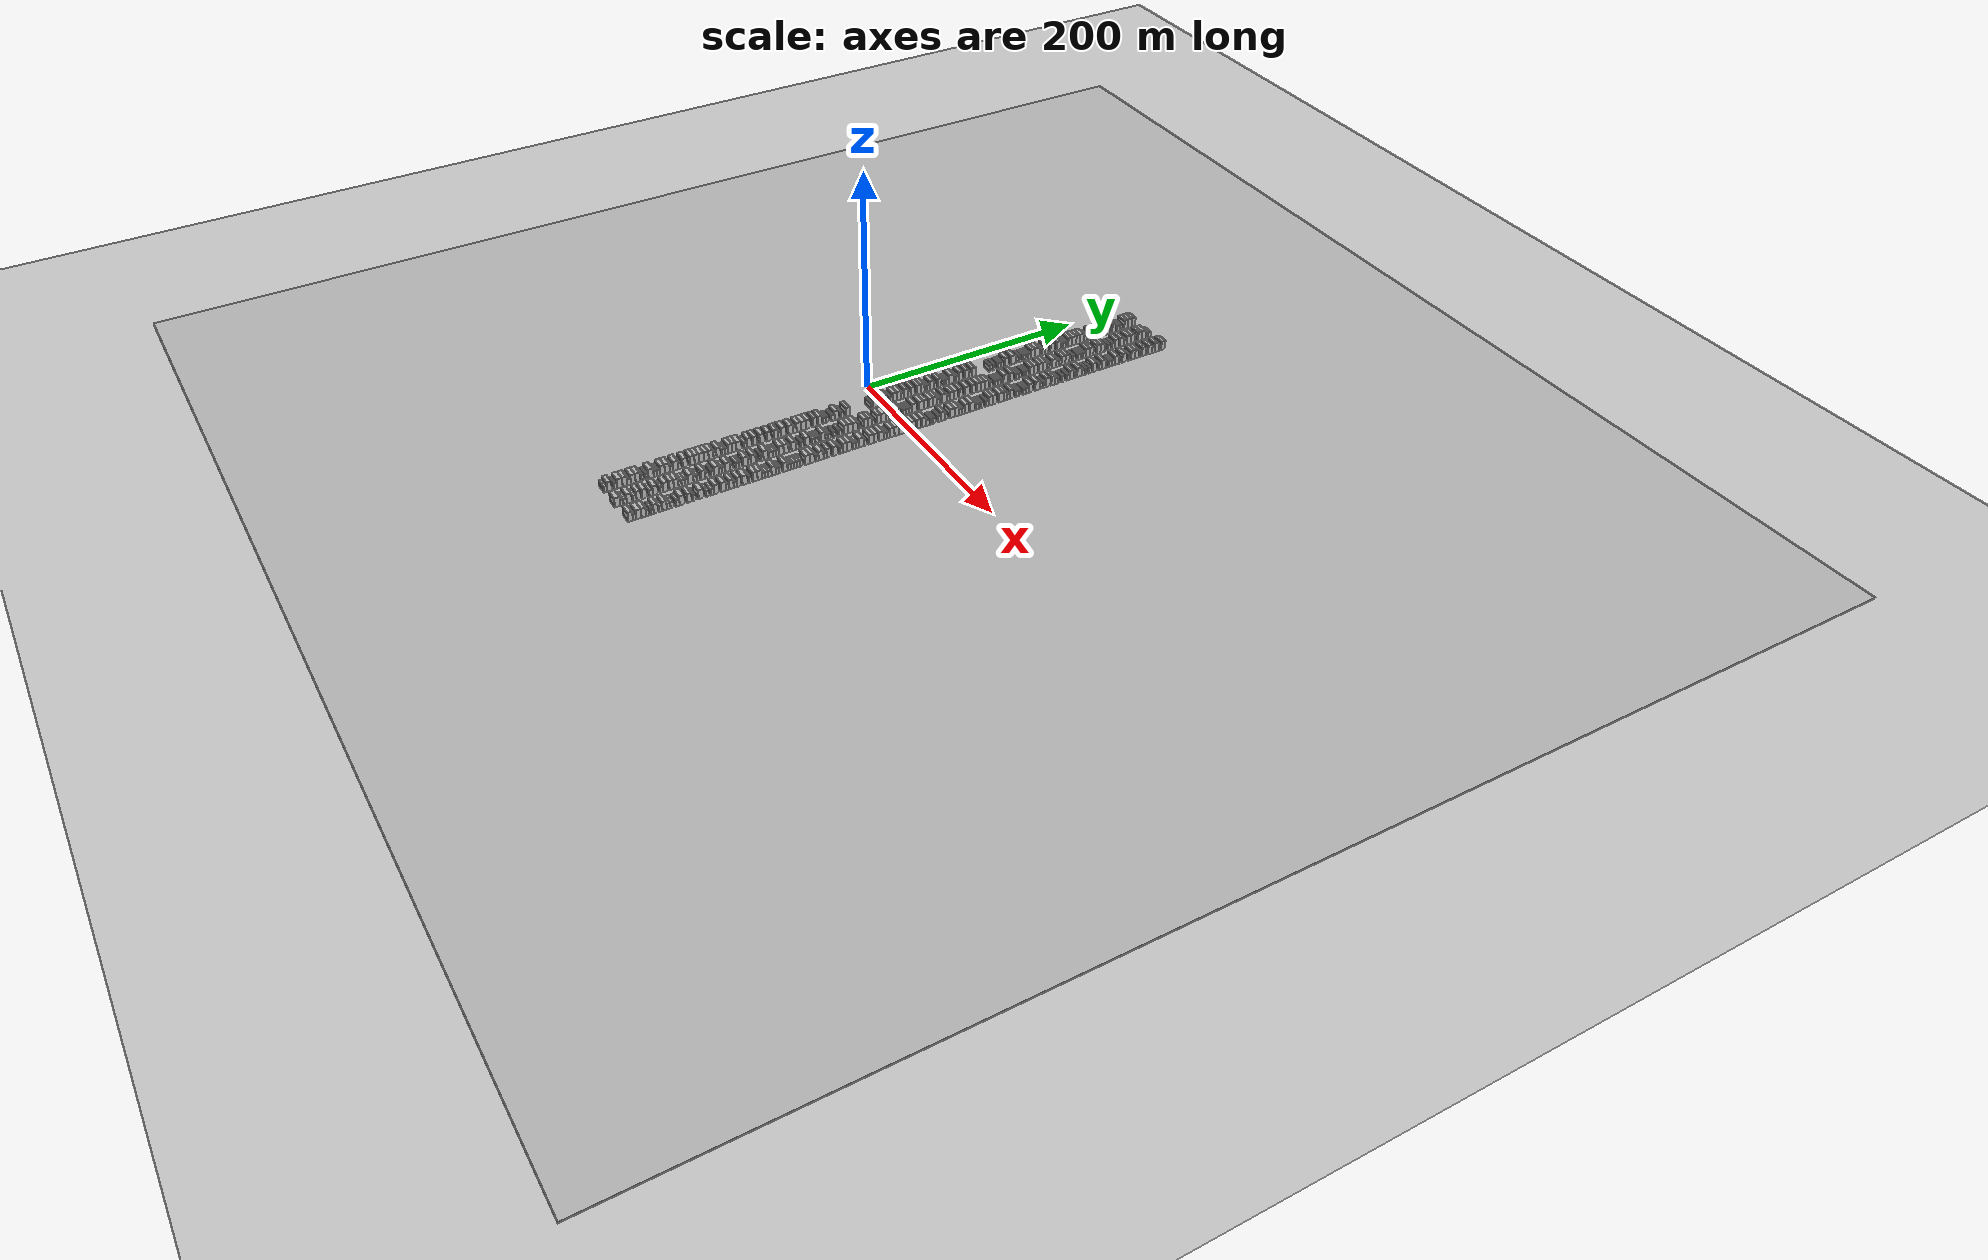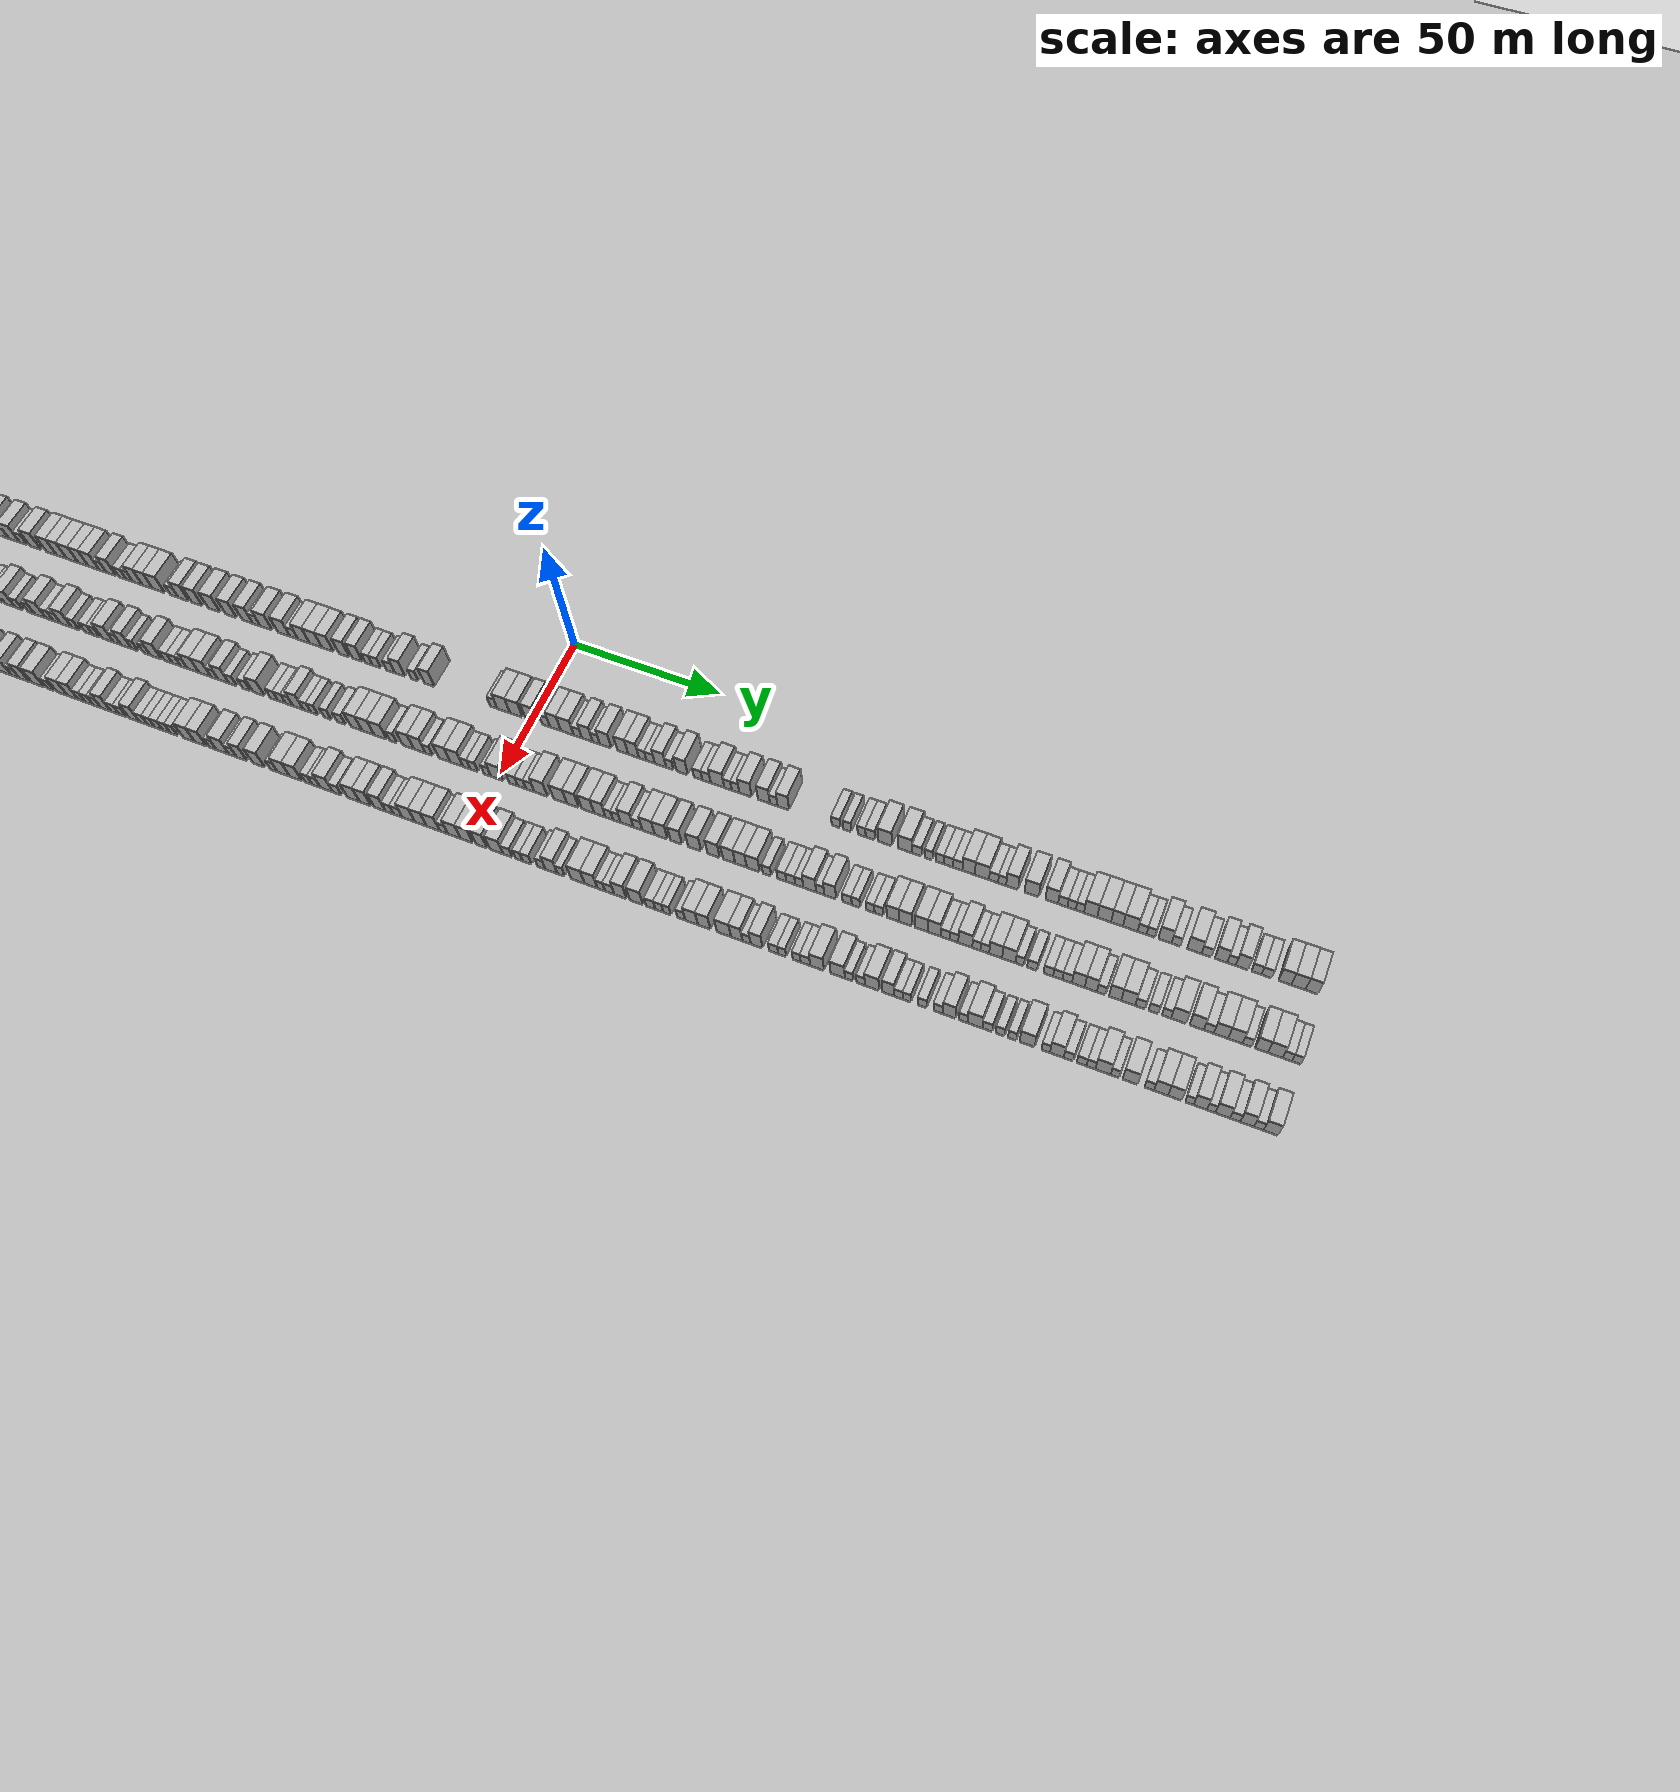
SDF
<?xml version="1.0" encoding="utf-8"?>

<sdf version="1.6">

   <world name="default">

      <gui fullscreen="0">

         <camera name="user_camera">

            <pose>-15 0 4.57585 0 0 0</pose>

            <view_controller>orbit</view_controller>

         </camera>

      </gui>

      <scene>

         <sky>

           <clouds>

             <speed>12</speed>

           </clouds>

         </sky>

         <ambient>0.4 0.4 0.4 1</ambient>

         <background>0.7 0.7 0.7 1</background>

         <shadows>1</shadows>

      </scene>

      <gravity>0 0 -9.8066</gravity>

      <magnetic_field>6e-06 2.3e-05 -4.2e-05</magnetic_field>

      <physics default="0" name="default_physics" type="ode">

         <ode>

            <solver>

               <type>quick</type>

               <iters>10</iters>

               <sor>1.0</sor>

               <use_dynamic_moi_rescaling>0</use_dynamic_moi_rescaling>

            </solver>

            <constraints>

               <cfm>0</cfm>

               <erp>0.2</erp>

               <contact_max_correcting_vel>100</contact_max_correcting_vel>

               <contact_surface_layer>0.001</contact_surface_layer>

            </constraints>

         </ode>

         <max_step_size>0.004</max_step_size>

         <real_time_factor>1</real_time_factor>

         <real_time_update_rate>250</real_time_update_rate>

      </physics>

      <light name="sun" type="directional">

         <cast_shadows>1</cast_shadows>

         <pose>0 0 10 0 0 0</pose>

         <diffuse>0.8 0.8 0.8 1</diffuse>

         <specular>0.2 0.2 0.2 1</specular>

         <attenuation>

            <range>1000</range>

            <constant>0.9</constant>

            <linear>0.01</linear>

            <quadratic>0.001</quadratic>

         </attenuation>

         <direction>-0.5 0.1 -0.9</direction>

      </light>

      <include>

         <name>ground_plane_1</name>

         <uri>model://HANNAS_ground_plane</uri>

         <pose>0 0 0  0 0 0</pose>

      </include>

      <include>

         <name>ground_plane_2</name>

         <uri>model://HANNAS_ground_plane</uri>

         <pose>100 0 0  0 0 0</pose>

      </include>

      <model name="building_1">

         <static>1</static>

         <pose frame="">25.0000 -246.6823 0 0.000000 0.000000 0.000000</pose>

         <link name="link">

            <pose frame="">0 0 3.00 0 0 0</pose>

            <collision name="collision">

               <geometry>

                  <box>

                     <size>10.0000 2.6353 6.0000</size>

                  </box>

               </geometry>

               <max_contacts>10</max_contacts>

               <surface>

                  <contact>

                     <ode/>

                  </contact>

                  <bounce/>

                  <friction>

                     <torsional>

                        <ode/>

                     </torsional>

                     <ode/>

                  </friction>

               </surface>

            </collision>

            <visual name="visual">

               <cast_shadows>0</cast_shadows>

               <geometry>

                  <box>

                     <size>10.0000 2.6353 6.0000</size>

                  </box>

               </geometry>

               <material>

                  <script>

                     <uri>model://HANNAS_wall/materials/scripts</uri>

                     <uri>model://HANNAS_wall/materials/textures</uri>

                     <name>vrc/HANNAS_wall</name>

                  </script>

               </material>

            </visual>

            <self_collide>0</self_collide>

            <enable_wind>0</enable_wind>

            <kinematic>0</kinematic>

         </link>

      </model>

      <model name="building_2">

         <static>1</static>

         <pose frame="">25.0000 -243.4748 0 0.000000 0.000000 0.000000</pose>

         <link name="link">

            <pose frame="">0 0 4.50 0 0 0</pose>

            <collision name="collision">

               <geometry>

                  <box>

                     <size>10.0000 3.7796 9.0000</size>

                  </box>

               </geometry>

               <max_contacts>10</max_contacts>

               <surface>

                  <contact>

                     <ode/>

                  </contact>

                  <bounce/>

                  <friction>

                     <torsional>

                        <ode/>

                     </torsional>

                     <ode/>

                  </friction>

               </surface>

            </collision>

            <visual name="visual">

               <cast_shadows>0</cast_shadows>

               <geometry>

                  <box>

                     <size>10.0000 3.7796 9.0000</size>

                  </box>

               </geometry>

               <material>

                  <script>

                     <uri>model://HANNAS_wall/materials/scripts</uri>

                     <uri>model://HANNAS_wall/materials/textures</uri>

                     <name>vrc/HANNAS_wall</name>

                  </script>

               </material>

            </visual>

            <self_collide>0</self_collide>

            <enable_wind>0</enable_wind>

            <kinematic>0</kinematic>

         </link>

      </model>

      <model name="building_3">

         <static>1</static>

         <pose frame="">25.0000 -238.3669 0 0.000000 0.000000 0.000000</pose>

         <link name="link">

            <pose frame="">0 0 3.00 0 0 0</pose>

            <collision name="collision">

               <geometry>

                  <box>

                     <size>10.0000 2.4362 6.0000</size>

                  </box>

               </geometry>

               <max_contacts>10</max_contacts>

               <surface>

                  <contact>

                     <ode/>

                  </contact>

                  <bounce/>

                  <friction>

                     <torsional>

                        <ode/>

                     </torsional>

                     <ode/>

                  </friction>

               </surface>

            </collision>

            <visual name="visual">

               <cast_shadows>0</cast_shadows>

               <geometry>

                  <box>

                     <size>10.0000 2.4362 6.0000</size>

                  </box>

               </geometry>

               <material>

                  <script>

                     <uri>model://HANNAS_wall/materials/scripts</uri>

                     <uri>model://HANNAS_wall/materials/textures</uri>

                     <name>vrc/HANNAS_wall</name>

                  </script>

               </material>

            </visual>

            <self_collide>0</self_collide>

            <enable_wind>0</enable_wind>

            <kinematic>0</kinematic>

         </link>

      </model>

      <model name="building_4">

         <static>1</static>

         <pose frame="">25.0000 -234.9206 0 0.000000 0.000000 0.000000</pose>

         <link name="link">

            <pose frame="">0 0 4.50 0 0 0</pose>

            <collision name="collision">

               <geometry>

                  <box>

                     <size>10.0000 4.4564 9.0000</size>

                  </box>

               </geometry>

               <max_contacts>10</max_contacts>

               <surface>

                  <contact>

                     <ode/>

                  </contact>

                  <bounce/>

                  <friction>

                     <torsional>

                        <ode/>

                     </torsional>

                     <ode/>

                  </friction>

               </surface>

            </collision>

            <visual name="visual">

               <cast_shadows>0</cast_shadows>

               <geometry>

                  <box>

                     <size>10.0000 4.4564 9.0000</size>

                  </box>

               </geometry>

               <material>

                  <script>

                     <uri>model://HANNAS_wall/materials/scripts</uri>

                     <uri>model://HANNAS_wall/materials/textures</uri>

                     <name>vrc/HANNAS_wall</name>

                  </script>

               </material>

            </visual>

            <self_collide>0</self_collide>

            <enable_wind>0</enable_wind>

            <kinematic>0</kinematic>

         </link>

      </model>

      <model name="building_5">

         <static>1</static>

         <pose frame="">25.0000 -230.7517 0 0.000000 0.000000 0.000000</pose>

         <link name="link">

            <pose frame="">0 0 4.50 0 0 0</pose>

            <collision name="collision">

               <geometry>

                  <box>

                     <size>10.0000 3.8816 9.0000</size>

                  </box>

               </geometry>

               <max_contacts>10</max_contacts>

               <surface>

                  <contact>

                     <ode/>

                  </contact>

                  <bounce/>

                  <friction>

                     <torsional>

                        <ode/>

                     </torsional>

                     <ode/>

                  </friction>

               </surface>

            </collision>

            <visual name="visual">

               <cast_shadows>0</cast_shadows>

               <geometry>

                  <box>

                     <size>10.0000 3.8816 9.0000</size>

                  </box>

               </geometry>

               <material>

                  <script>

                     <uri>model://HANNAS_wall/materials/scripts</uri>

                     <uri>model://HANNAS_wall/materials/textures</uri>

                     <name>vrc/HANNAS_wall</name>

                  </script>

               </material>

            </visual>

            <self_collide>0</self_collide>

            <enable_wind>0</enable_wind>

            <kinematic>0</kinematic>

         </link>

      </model>

      <model name="building_6">

         <static>1</static>

         <pose frame="">25.0000 -227.3172 0 0.000000 0.000000 0.000000</pose>

         <link name="link">

            <pose frame="">0 0 3.00 0 0 0</pose>

            <collision name="collision">

               <geometry>

                  <box>

                     <size>10.0000 2.9874 6.0000</size>

                  </box>

               </geometry>

               <max_contacts>10</max_contacts>

               <surface>

                  <contact>

                     <ode/>

                  </contact>

                  <bounce/>

                  <friction>

                     <torsional>

                        <ode/>

                     </torsional>

                     <ode/>

                  </friction>

               </surface>

            </collision>

            <visual name="visual">

               <cast_shadows>0</cast_shadows>

               <geometry>

                  <box>

                     <size>10.0000 2.9874 6.0000</size>

                  </box>

               </geometry>

               <material>

                  <script>

                     <uri>model://HANNAS_wall/materials/scripts</uri>

                     <uri>model://HANNAS_wall/materials/textures</uri>

                     <name>vrc/HANNAS_wall</name>

                  </script>

               </material>

            </visual>

            <self_collide>0</self_collide>

            <enable_wind>0</enable_wind>

            <kinematic>0</kinematic>

         </link>

      </model>

      <model name="building_7">

         <static>1</static>

         <pose frame="">25.0000 -223.8692 0 0.000000 0.000000 0.000000</pose>

         <link name="link">

            <pose frame="">0 0 4.50 0 0 0</pose>

            <collision name="collision">

               <geometry>

                  <box>

                     <size>10.0000 3.9086 9.0000</size>

                  </box>

               </geometry>

               <max_contacts>10</max_contacts>

               <surface>

                  <contact>

                     <ode/>

                  </contact>

                  <bounce/>

                  <friction>

                     <torsional>

                        <ode/>

                     </torsional>

                     <ode/>

                  </friction>

               </surface>

            </collision>

            <visual name="visual">

               <cast_shadows>0</cast_shadows>

               <geometry>

                  <box>

                     <size>10.0000 3.9086 9.0000</size>

                  </box>

               </geometry>

               <material>

                  <script>

                     <uri>model://HANNAS_wall/materials/scripts</uri>

                     <uri>model://HANNAS_wall/materials/textures</uri>

                     <name>vrc/HANNAS_wall</name>

                  </script>

               </material>

            </visual>

            <self_collide>0</self_collide>

            <enable_wind>0</enable_wind>

            <kinematic>0</kinematic>

         </link>

      </model>

      <model name="building_8">

         <static>1</static>

         <pose frame="">25.0000 -219.9311 0 0.000000 0.000000 0.000000</pose>

         <link name="link">

            <pose frame="">0 0 4.50 0 0 0</pose>

            <collision name="collision">

               <geometry>

                  <box>

                     <size>10.0000 3.9676 9.0000</size>

                  </box>

               </geometry>

               <max_contacts>10</max_contacts>

               <surface>

                  <contact>

                     <ode/>

                  </contact>

                  <bounce/>

                  <friction>

                     <torsional>

                        <ode/>

                     </torsional>

                     <ode/>

                  </friction>

               </surface>

            </collision>

            <visual name="visual">

               <cast_shadows>0</cast_shadows>

               <geometry>

                  <box>

                     <size>10.0000 3.9676 9.0000</size>

                  </box>

               </geometry>

               <material>

                  <script>

                     <uri>model://HANNAS_wall/materials/scripts</uri>

                     <uri>model://HANNAS_wall/materials/textures</uri>

                     <name>vrc/HANNAS_wall</name>

                  </script>

               </material>

            </visual>

            <self_collide>0</self_collide>

            <enable_wind>0</enable_wind>

            <kinematic>0</kinematic>

         </link>

      </model>

      <model name="building_9">

         <static>1</static>

         <pose frame="">25.0000 -215.7314 0 0.000000 0.000000 0.000000</pose>

         <link name="link">

            <pose frame="">0 0 3.00 0 0 0</pose>

            <collision name="collision">

               <geometry>

                  <box>

                     <size>10.0000 2.4318 6.0000</size>

                  </box>

               </geometry>

               <max_contacts>10</max_contacts>

               <surface>

                  <contact>

                     <ode/>

                  </contact>

                  <bounce/>

                  <friction>

                     <torsional>

                        <ode/>

                     </torsional>

                     <ode/>

                  </friction>

               </surface>

            </collision>

            <visual name="visual">

               <cast_shadows>0</cast_shadows>

               <geometry>

                  <box>

                     <size>10.0000 2.4318 6.0000</size>

                  </box>

               </geometry>

               <material>

                  <script>

                     <uri>model://HANNAS_wall/materials/scripts</uri>

                     <uri>model://HANNAS_wall/materials/textures</uri>

                     <name>vrc/HANNAS_wall</name>

                  </script>

               </material>

            </visual>

            <self_collide>0</self_collide>

            <enable_wind>0</enable_wind>

            <kinematic>0</kinematic>

         </link>

      </model>

      <model name="building_10">

         <static>1</static>

         <pose frame="">25.0000 -212.2890 0 0.000000 0.000000 0.000000</pose>

         <link name="link">

            <pose frame="">0 0 3.00 0 0 0</pose>

            <collision name="collision">

               <geometry>

                  <box>

                     <size>10.0000 2.4529 6.0000</size>

                  </box>

               </geometry>

               <max_contacts>10</max_contacts>

               <surface>

                  <contact>

                     <ode/>

                  </contact>

                  <bounce/>

                  <friction>

                     <torsional>

                        <ode/>

                     </torsional>

                     <ode/>

                  </friction>

               </surface>

            </collision>

            <visual name="visual">

               <cast_shadows>0</cast_shadows>

               <geometry>

                  <box>

                     <size>10.0000 2.4529 6.0000</size>

                  </box>

               </geometry>

               <material>

                  <script>

                     <uri>model://HANNAS_wall/materials/scripts</uri>

                     <uri>model://HANNAS_wall/materials/textures</uri>

                     <name>vrc/HANNAS_wall</name>

                  </script>

               </material>

            </visual>

            <self_collide>0</self_collide>

            <enable_wind>0</enable_wind>

            <kinematic>0</kinematic>

         </link>

      </model>

      <model name="building_11">

         <static>1</static>

         <pose frame="">25.0000 -208.8492 0 0.000000 0.000000 0.000000</pose>

         <link name="link">

            <pose frame="">0 0 4.50 0 0 0</pose>

            <collision name="collision">

               <geometry>

                  <box>

                     <size>10.0000 4.4268 9.0000</size>

                  </box>

               </geometry>

               <max_contacts>10</max_contacts>

               <surface>

                  <contact>

                     <ode/>

                  </contact>

                  <bounce/>

                  <friction>

                     <torsional>

                        <ode/>

                     </torsional>

                     <ode/>

                  </friction>

               </surface>

            </collision>

            <visual name="visual">

               <cast_shadows>0</cast_shadows>

               <geometry>

                  <box>

                     <size>10.0000 4.4268 9.0000</size>

                  </box>

               </geometry>

               <material>

                  <script>

                     <uri>model://HANNAS_wall/materials/scripts</uri>

                     <uri>model://HANNAS_wall/materials/textures</uri>

                     <name>vrc/HANNAS_wall</name>

                  </script>

               </material>

            </visual>

            <self_collide>0</self_collide>

            <enable_wind>0</enable_wind>

            <kinematic>0</kinematic>

         </link>

      </model>

      <model name="building_12">

         <static>1</static>

         <pose frame="">25.0000 -205.1444 0 0.000000 0.000000 0.000000</pose>

         <link name="link">

            <pose frame="">0 0 3.00 0 0 0</pose>

            <collision name="collision">

               <geometry>

                  <box>

                     <size>10.0000 2.9828 6.0000</size>

                  </box>

               </geometry>

               <max_contacts>10</max_contacts>

               <surface>

                  <contact>

                     <ode/>

                  </contact>

                  <bounce/>

                  <friction>

                     <torsional>

                        <ode/>

                     </torsional>

                     <ode/>

                  </friction>

               </surface>

            </collision>

            <visual name="visual">

               <cast_shadows>0</cast_shadows>

               <geometry>

                  <box>

                     <size>10.0000 2.9828 6.0000</size>

                  </box>

               </geometry>

               <material>

                  <script>

                     <uri>model://HANNAS_wall/materials/scripts</uri>

                     <uri>model://HANNAS_wall/materials/textures</uri>

                     <name>vrc/HANNAS_wall</name>

                  </script>

               </material>

            </visual>

            <self_collide>0</self_collide>

            <enable_wind>0</enable_wind>

            <kinematic>0</kinematic>

         </link>

      </model>

      <model name="building_13">

         <static>1</static>

         <pose frame="">25.0000 -202.4101 0 0.000000 0.000000 0.000000</pose>

         <link name="link">

            <pose frame="">0 0 3.00 0 0 0</pose>

            <collision name="collision">

               <geometry>

                  <box>

                     <size>10.0000 2.4857 6.0000</size>

                  </box>

               </geometry>

               <max_contacts>10</max_contacts>

               <surface>

                  <contact>

                     <ode/>

                  </contact>

                  <bounce/>

                  <friction>

                     <torsional>

                        <ode/>

                     </torsional>

                     <ode/>

                  </friction>

               </surface>

            </collision>

            <visual name="visual">

               <cast_shadows>0</cast_shadows>

               <geometry>

                  <box>

                     <size>10.0000 2.4857 6.0000</size>

                  </box>

               </geometry>

               <material>

                  <script>

                     <uri>model://HANNAS_wall/materials/scripts</uri>

                     <uri>model://HANNAS_wall/materials/textures</uri>

                     <name>vrc/HANNAS_wall</name>

                  </script>

               </material>

            </visual>

            <self_collide>0</self_collide>

            <enable_wind>0</enable_wind>

            <kinematic>0</kinematic>

         </link>

      </model>

      <model name="building_14">

         <static>1</static>

         <pose frame="">25.0000 -199.1796 0 0.000000 0.000000 0.000000</pose>

         <link name="link">

            <pose frame="">0 0 4.50 0 0 0</pose>

            <collision name="collision">

               <geometry>

                  <box>

                     <size>10.0000 3.9754 9.0000</size>

                  </box>

               </geometry>

               <max_contacts>10</max_contacts>

               <surface>

                  <contact>

                     <ode/>

                  </contact>

                  <bounce/>

                  <friction>

                     <torsional>

                        <ode/>

                     </torsional>

                     <ode/>

                  </friction>

               </surface>

            </collision>

            <visual name="visual">

               <cast_shadows>0</cast_shadows>

               <geometry>

                  <box>

                     <size>10.0000 3.9754 9.0000</size>

                  </box>

               </geometry>

               <material>

                  <script>

                     <uri>model://HANNAS_wall/materials/scripts</uri>

                     <uri>model://HANNAS_wall/materials/textures</uri>

                     <name>vrc/HANNAS_wall</name>

                  </script>

               </material>

            </visual>

            <self_collide>0</self_collide>

            <enable_wind>0</enable_wind>

            <kinematic>0</kinematic>

         </link>

      </model>

      <model name="building_15">

         <static>1</static>

         <pose frame="">25.0000 -195.0991 0 0.000000 0.000000 0.000000</pose>

         <link name="link">

            <pose frame="">0 0 4.50 0 0 0</pose>

            <collision name="collision">

               <geometry>

                  <box>

                     <size>10.0000 4.1856 9.0000</size>

                  </box>

               </geometry>

               <max_contacts>10</max_contacts>

               <surface>

                  <contact>

                     <ode/>

                  </contact>

                  <bounce/>

                  <friction>

                     <torsional>

                        <ode/>

                     </torsional>

                     <ode/>

                  </friction>

               </surface>

            </collision>

            <visual name="visual">

               <cast_shadows>0</cast_shadows>

               <geometry>

                  <box>

                     <size>10.0000 4.1856 9.0000</size>

                  </box>

               </geometry>

               <material>

                  <script>

                     <uri>model://HANNAS_wall/materials/scripts</uri>

                     <uri>model://HANNAS_wall/materials/textures</uri>

                     <name>vrc/HANNAS_wall</name>

                  </script>

               </material>

            </visual>

            <self_collide>0</self_collide>

            <enable_wind>0</enable_wind>

            <kinematic>0</kinematic>

         </link>

      </model>

      <model name="building_16">

         <static>1</static>

         <pose frame="">25.0000 -191.5469 0 0.000000 0.000000 0.000000</pose>

         <link name="link">

            <pose frame="">0 0 3.00 0 0 0</pose>

            <collision name="collision">

               <geometry>

                  <box>

                     <size>10.0000 2.9188 6.0000</size>

                  </box>

               </geometry>

               <max_contacts>10</max_contacts>

               <surface>

                  <contact>

                     <ode/>

                  </contact>

                  <bounce/>

                  <friction>

                     <torsional>

                        <ode/>

                     </torsional>

                     <ode/>

                  </friction>

               </surface>

            </collision>

            <visual name="visual">

               <cast_shadows>0</cast_shadows>

               <geometry>

                  <box>

                     <size>10.0000 2.9188 6.0000</size>

                  </box>

               </geometry>

               <material>

                  <script>

                     <uri>model://HANNAS_wall/materials/scripts</uri>

                     <uri>model://HANNAS_wall/materials/textures</uri>

                     <name>vrc/HANNAS_wall</name>

                  </script>

               </material>

            </visual>

            <self_collide>0</self_collide>

            <enable_wind>0</enable_wind>

            <kinematic>0</kinematic>

         </link>

      </model>

      <model name="building_17">

         <static>1</static>

         <pose frame="">25.0000 -188.0178 0 0.000000 0.000000 0.000000</pose>

         <link name="link">

            <pose frame="">0 0 4.50 0 0 0</pose>

            <collision name="collision">

               <geometry>

                  <box>

                     <size>10.0000 4.1394 9.0000</size>

                  </box>

               </geometry>

               <max_contacts>10</max_contacts>

               <surface>

                  <contact>

                     <ode/>

                  </contact>

                  <bounce/>

                  <friction>

                     <torsional>

                        <ode/>

                     </torsional>

                     <ode/>

                  </friction>

               </surface>

            </collision>

            <visual name="visual">

               <cast_shadows>0</cast_shadows>

               <geometry>

                  <box>

                     <size>10.0000 4.1394 9.0000</size>

                  </box>

               </geometry>

               <material>

                  <script>

                     <uri>model://HANNAS_wall/materials/scripts</uri>

                     <uri>model://HANNAS_wall/materials/textures</uri>

                     <name>vrc/HANNAS_wall</name>

                  </script>

               </material>

            </visual>

            <self_collide>0</self_collide>

            <enable_wind>0</enable_wind>

            <kinematic>0</kinematic>

         </link>

      </model>

      <model name="building_18">

         <static>1</static>

         <pose frame="">25.0000 -184.5007 0 0.000000 0.000000 0.000000</pose>

         <link name="link">

            <pose frame="">0 0 3.00 0 0 0</pose>

            <collision name="collision">

               <geometry>

                  <box>

                     <size>10.0000 2.8948 6.0000</size>

                  </box>

               </geometry>

               <max_contacts>10</max_contacts>

               <surface>

                  <contact>

                     <ode/>

                  </contact>

                  <bounce/>

                  <friction>

                     <torsional>

                        <ode/>

                     </torsional>

                     <ode/>

                  </friction>

               </surface>

            </collision>

            <visual name="visual">

               <cast_shadows>0</cast_shadows>

               <geometry>

                  <box>

                     <size>10.0000 2.8948 6.0000</size>

                  </box>

               </geometry>

               <material>

                  <script>

                     <uri>model://HANNAS_wall/materials/scripts</uri>

                     <uri>model://HANNAS_wall/materials/textures</uri>

                     <name>vrc/HANNAS_wall</name>

                  </script>

               </material>

            </visual>

            <self_collide>0</self_collide>

            <enable_wind>0</enable_wind>

            <kinematic>0</kinematic>

         </link>

      </model>

      <model name="building_19">

         <static>1</static>

         <pose frame="">25.0000 -179.9044 0 0.000000 0.000000 0.000000</pose>

         <link name="link">

            <pose frame="">0 0 4.50 0 0 0</pose>

            <collision name="collision">

               <geometry>

                  <box>

                     <size>10.0000 4.2978 9.0000</size>

                  </box>

               </geometry>

               <max_contacts>10</max_contacts>

               <surface>

                  <contact>

                     <ode/>

                  </contact>

                  <bounce/>

                  <friction>

                     <torsional>

                        <ode/>

                     </torsional>

                     <ode/>

                  </friction>

               </surface>

            </collision>

            <visual name="visual">

               <cast_shadows>0</cast_shadows>

               <geometry>

                  <box>

                     <size>10.0000 4.2978 9.0000</size>

                  </box>

               </geometry>

               <material>

                  <script>

                     <uri>model://HANNAS_wall/materials/scripts</uri>

                     <uri>model://HANNAS_wall/materials/textures</uri>

                     <name>vrc/HANNAS_wall</name>

                  </script>

               </material>

            </visual>

            <self_collide>0</self_collide>

            <enable_wind>0</enable_wind>

            <kinematic>0</kinematic>

         </link>

      </model>

      <model name="building_20">

         <static>1</static>

         <pose frame="">25.0000 -173.7915 0 0.000000 0.000000 0.000000</pose>

         <link name="link">

            <pose frame="">0 0 4.50 0 0 0</pose>

            <collision name="collision">

               <geometry>

                  <box>

                     <size>10.0000 3.9280 9.0000</size>

                  </box>

               </geometry>

               <max_contacts>10</max_contacts>

               <surface>

                  <contact>

                     <ode/>

                  </contact>

                  <bounce/>

                  <friction>

                     <torsional>

                        <ode/>

                     </torsional>

                     <ode/>

                  </friction>

               </surface>

            </collision>

            <visual name="visual">

               <cast_shadows>0</cast_shadows>

               <geometry>

                  <box>

                     <size>10.0000 3.9280 9.0000</size>

                  </box>

               </geometry>

               <material>

                  <script>

                     <uri>model://HANNAS_wall/materials/scripts</uri>

                     <uri>model://HANNAS_wall/materials/textures</uri>

                     <name>vrc/HANNAS_wall</name>

                  </script>

               </material>

            </visual>

            <self_collide>0</self_collide>

            <enable_wind>0</enable_wind>

            <kinematic>0</kinematic>

         </link>

      </model>

      <model name="building_21">

         <static>1</static>

         <pose frame="">25.0000 -169.8937 0 0.000000 0.000000 0.000000</pose>

         <link name="link">

            <pose frame="">0 0 4.50 0 0 0</pose>

            <collision name="collision">

               <geometry>

                  <box>

                     <size>10.0000 3.8677 9.0000</size>

                  </box>

               </geometry>

               <max_contacts>10</max_contacts>

               <surface>

                  <contact>

                     <ode/>

                  </contact>

                  <bounce/>

                  <friction>

                     <torsional>

                        <ode/>

                     </torsional>

                     <ode/>

                  </friction>

               </surface>

            </collision>

            <visual name="visual">

               <cast_shadows>0</cast_shadows>

               <geometry>

                  <box>

                     <size>10.0000 3.8677 9.0000</size>

                  </box>

               </geometry>

               <material>

                  <script>

                     <uri>model://HANNAS_wall/materials/scripts</uri>

                     <uri>model://HANNAS_wall/materials/textures</uri>

                     <name>vrc/HANNAS_wall</name>

                  </script>

               </material>

            </visual>

            <self_collide>0</self_collide>

            <enable_wind>0</enable_wind>

            <kinematic>0</kinematic>

         </link>

      </model>

      <model name="building_22">

         <static>1</static>

         <pose frame="">25.0000 -165.7522 0 0.000000 0.000000 0.000000</pose>

         <link name="link">

            <pose frame="">0 0 4.50 0 0 0</pose>

            <collision name="collision">

               <geometry>

                  <box>

                     <size>10.0000 4.4152 9.0000</size>

                  </box>

               </geometry>

               <max_contacts>10</max_contacts>

               <surface>

                  <contact>

                     <ode/>

                  </contact>

                  <bounce/>

                  <friction>

                     <torsional>

                        <ode/>

                     </torsional>

                     <ode/>

                  </friction>

               </surface>

            </collision>

            <visual name="visual">

               <cast_shadows>0</cast_shadows>

               <geometry>

                  <box>

                     <size>10.0000 4.4152 9.0000</size>

                  </box>

               </geometry>

               <material>

                  <script>

                     <uri>model://HANNAS_wall/materials/scripts</uri>

                     <uri>model://HANNAS_wall/materials/textures</uri>

                     <name>vrc/HANNAS_wall</name>

                  </script>

               </material>

            </visual>

            <self_collide>0</self_collide>

            <enable_wind>0</enable_wind>

            <kinematic>0</kinematic>

         </link>

      </model>

      <model name="building_23">

         <static>1</static>

         <pose frame="">25.0000 -161.6356 0 0.000000 0.000000 0.000000</pose>

         <link name="link">

            <pose frame="">0 0 4.50 0 0 0</pose>

            <collision name="collision">

               <geometry>

                  <box>

                     <size>10.0000 3.8179 9.0000</size>

                  </box>

               </geometry>

               <max_contacts>10</max_contacts>

               <surface>

                  <contact>

                     <ode/>

                  </contact>

                  <bounce/>

                  <friction>

                     <torsional>

                        <ode/>

                     </torsional>

                     <ode/>

                  </friction>

               </surface>

            </collision>

            <visual name="visual">

               <cast_shadows>0</cast_shadows>

               <geometry>

                  <box>

                     <size>10.0000 3.8179 9.0000</size>

                  </box>

               </geometry>

               <material>

                  <script>

                     <uri>model://HANNAS_wall/materials/scripts</uri>

                     <uri>model://HANNAS_wall/materials/textures</uri>

                     <name>vrc/HANNAS_wall</name>

                  </script>

               </material>

            </visual>

            <self_collide>0</self_collide>

            <enable_wind>0</enable_wind>

            <kinematic>0</kinematic>

         </link>

      </model>

      <model name="building_24">

         <static>1</static>

         <pose frame="">25.0000 -157.6680 0 0.000000 0.000000 0.000000</pose>

         <link name="link">

            <pose frame="">0 0 4.50 0 0 0</pose>

            <collision name="collision">

               <geometry>

                  <box>

                     <size>10.0000 4.1173 9.0000</size>

                  </box>

               </geometry>

               <max_contacts>10</max_contacts>

               <surface>

                  <contact>

                     <ode/>

                  </contact>

                  <bounce/>

                  <friction>

                     <torsional>

                        <ode/>

                     </torsional>

                     <ode/>

                  </friction>

               </surface>

            </collision>

            <visual name="visual">

               <cast_shadows>0</cast_shadows>

               <geometry>

                  <box>

                     <size>10.0000 4.1173 9.0000</size>

                  </box>

               </geometry>

               <material>

                  <script>

                     <uri>model://HANNAS_wall/materials/scripts</uri>

                     <uri>model://HANNAS_wall/materials/textures</uri>

                     <name>vrc/HANNAS_wall</name>

                  </script>

               </material>

            </visual>

            <self_collide>0</self_collide>

            <enable_wind>0</enable_wind>

            <kinematic>0</kinematic>

         </link>

      </model>

      <model name="building_25">

         <static>1</static>

         <pose frame="">25.0000 -154.2986 0 0.000000 0.000000 0.000000</pose>

         <link name="link">

            <pose frame="">0 0 3.00 0 0 0</pose>

            <collision name="collision">

               <geometry>

                  <box>

                     <size>10.0000 2.6216 6.0000</size>

                  </box>

               </geometry>

               <max_contacts>10</max_contacts>

               <surface>

                  <contact>

                     <ode/>

                  </contact>

                  <bounce/>

                  <friction>

                     <torsional>

                        <ode/>

                     </torsional>

                     <ode/>

                  </friction>

               </surface>

            </collision>

            <visual name="visual">

               <cast_shadows>0</cast_shadows>

               <geometry>

                  <box>

                     <size>10.0000 2.6216 6.0000</size>

                  </box>

               </geometry>

               <material>

                  <script>

                     <uri>model://HANNAS_wall/materials/scripts</uri>

                     <uri>model://HANNAS_wall/materials/textures</uri>

                     <name>vrc/HANNAS_wall</name>

                  </script>

               </material>

            </visual>

            <self_collide>0</self_collide>

            <enable_wind>0</enable_wind>

            <kinematic>0</kinematic>

         </link>

      </model>

      <model name="building_26">

         <static>1</static>

         <pose frame="">25.0000 -151.1317 0 0.000000 0.000000 0.000000</pose>

         <link name="link">

            <pose frame="">0 0 4.50 0 0 0</pose>

            <collision name="collision">

               <geometry>

                  <box>

                     <size>10.0000 3.7122 9.0000</size>

                  </box>

               </geometry>

               <max_contacts>10</max_contacts>

               <surface>

                  <contact>

                     <ode/>

                  </contact>

                  <bounce/>

                  <friction>

                     <torsional>

                        <ode/>

                     </torsional>

                     <ode/>

                  </friction>

               </surface>

            </collision>

            <visual name="visual">

               <cast_shadows>0</cast_shadows>

               <geometry>

                  <box>

                     <size>10.0000 3.7122 9.0000</size>

                  </box>

               </geometry>

               <material>

                  <script>

                     <uri>model://HANNAS_wall/materials/scripts</uri>

                     <uri>model://HANNAS_wall/materials/textures</uri>

                     <name>vrc/HANNAS_wall</name>

                  </script>

               </material>

            </visual>

            <self_collide>0</self_collide>

            <enable_wind>0</enable_wind>

            <kinematic>0</kinematic>

         </link>

      </model>

      <model name="building_27">

         <static>1</static>

         <pose frame="">25.0000 -146.8694 0 0.000000 0.000000 0.000000</pose>

         <link name="link">

            <pose frame="">0 0 3.00 0 0 0</pose>

            <collision name="collision">

               <geometry>

                  <box>

                     <size>10.0000 2.8124 6.0000</size>

                  </box>

               </geometry>

               <max_contacts>10</max_contacts>

               <surface>

                  <contact>

                     <ode/>

                  </contact>

                  <bounce/>

                  <friction>

                     <torsional>

                        <ode/>

                     </torsional>

                     <ode/>

                  </friction>

               </surface>

            </collision>

            <visual name="visual">

               <cast_shadows>0</cast_shadows>

               <geometry>

                  <box>

                     <size>10.0000 2.8124 6.0000</size>

                  </box>

               </geometry>

               <material>

                  <script>

                     <uri>model://HANNAS_wall/materials/scripts</uri>

                     <uri>model://HANNAS_wall/materials/textures</uri>

                     <name>vrc/HANNAS_wall</name>

                  </script>

               </material>

            </visual>

            <self_collide>0</self_collide>

            <enable_wind>0</enable_wind>

            <kinematic>0</kinematic>

         </link>

      </model>

      <model name="building_28">

         <static>1</static>

         <pose frame="">25.0000 -144.2595 0 0.000000 0.000000 0.000000</pose>

         <link name="link">

            <pose frame="">0 0 3.00 0 0 0</pose>

            <collision name="collision">

               <geometry>

                  <box>

                     <size>10.0000 2.4075 6.0000</size>

                  </box>

               </geometry>

               <max_contacts>10</max_contacts>

               <surface>

                  <contact>

                     <ode/>

                  </contact>

                  <bounce/>

                  <friction>

                     <torsional>

                        <ode/>

                     </torsional>

                     <ode/>

                  </friction>

               </surface>

            </collision>

            <visual name="visual">

               <cast_shadows>0</cast_shadows>

               <geometry>

                  <box>

                     <size>10.0000 2.4075 6.0000</size>

                  </box>

               </geometry>

               <material>

                  <script>

                     <uri>model://HANNAS_wall/materials/scripts</uri>

                     <uri>model://HANNAS_wall/materials/textures</uri>

                     <name>vrc/HANNAS_wall</name>

                  </script>

               </material>

            </visual>

            <self_collide>0</self_collide>

            <enable_wind>0</enable_wind>

            <kinematic>0</kinematic>

         </link>

      </model>

      <model name="building_29">

         <static>1</static>

         <pose frame="">25.0000 -141.2318 0 0.000000 0.000000 0.000000</pose>

         <link name="link">

            <pose frame="">0 0 4.50 0 0 0</pose>

            <collision name="collision">

               <geometry>

                  <box>

                     <size>10.0000 3.6478 9.0000</size>

                  </box>

               </geometry>

               <max_contacts>10</max_contacts>

               <surface>

                  <contact>

                     <ode/>

                  </contact>

                  <bounce/>

                  <friction>

                     <torsional>

                        <ode/>

                     </torsional>

                     <ode/>

                  </friction>

               </surface>

            </collision>

            <visual name="visual">

               <cast_shadows>0</cast_shadows>

               <geometry>

                  <box>

                     <size>10.0000 3.6478 9.0000</size>

                  </box>

               </geometry>

               <material>

                  <script>

                     <uri>model://HANNAS_wall/materials/scripts</uri>

                     <uri>model://HANNAS_wall/materials/textures</uri>

                     <name>vrc/HANNAS_wall</name>

                  </script>

               </material>

            </visual>

            <self_collide>0</self_collide>

            <enable_wind>0</enable_wind>

            <kinematic>0</kinematic>

         </link>

      </model>

      <model name="building_30">

         <static>1</static>

         <pose frame="">25.0000 -137.4980 0 0.000000 0.000000 0.000000</pose>

         <link name="link">

            <pose frame="">0 0 4.50 0 0 0</pose>

            <collision name="collision">

               <geometry>

                  <box>

                     <size>10.0000 3.8199 9.0000</size>

                  </box>

               </geometry>

               <max_contacts>10</max_contacts>

               <surface>

                  <contact>

                     <ode/>

                  </contact>

                  <bounce/>

                  <friction>

                     <torsional>

                        <ode/>

                     </torsional>

                     <ode/>

                  </friction>

               </surface>

            </collision>

            <visual name="visual">

               <cast_shadows>0</cast_shadows>

               <geometry>

                  <box>

                     <size>10.0000 3.8199 9.0000</size>

                  </box>

               </geometry>

               <material>

                  <script>

                     <uri>model://HANNAS_wall/materials/scripts</uri>

                     <uri>model://HANNAS_wall/materials/textures</uri>

                     <name>vrc/HANNAS_wall</name>

                  </script>

               </material>

            </visual>

            <self_collide>0</self_collide>

            <enable_wind>0</enable_wind>

            <kinematic>0</kinematic>

         </link>

      </model>

      <model name="building_31">

         <static>1</static>

         <pose frame="">25.0000 -133.3413 0 0.000000 0.000000 0.000000</pose>

         <link name="link">

            <pose frame="">0 0 4.50 0 0 0</pose>

            <collision name="collision">

               <geometry>

                  <box>

                     <size>10.0000 4.4935 9.0000</size>

                  </box>

               </geometry>

               <max_contacts>10</max_contacts>

               <surface>

                  <contact>

                     <ode/>

                  </contact>

                  <bounce/>

                  <friction>

                     <torsional>

                        <ode/>

                     </torsional>

                     <ode/>

                  </friction>

               </surface>

            </collision>

            <visual name="visual">

               <cast_shadows>0</cast_shadows>

               <geometry>

                  <box>

                     <size>10.0000 4.4935 9.0000</size>

                  </box>

               </geometry>

               <material>

                  <script>

                     <uri>model://HANNAS_wall/materials/scripts</uri>

                     <uri>model://HANNAS_wall/materials/textures</uri>

                     <name>vrc/HANNAS_wall</name>

                  </script>

               </material>

            </visual>

            <self_collide>0</self_collide>

            <enable_wind>0</enable_wind>

            <kinematic>0</kinematic>

         </link>

      </model>

      <model name="building_32">

         <static>1</static>

         <pose frame="">25.0000 -127.6372 0 0.000000 0.000000 0.000000</pose>

         <link name="link">

            <pose frame="">0 0 3.00 0 0 0</pose>

            <collision name="collision">

               <geometry>

                  <box>

                     <size>10.0000 2.9146 6.0000</size>

                  </box>

               </geometry>

               <max_contacts>10</max_contacts>

               <surface>

                  <contact>

                     <ode/>

                  </contact>

                  <bounce/>

                  <friction>

                     <torsional>

                        <ode/>

                     </torsional>

                     <ode/>

                  </friction>

               </surface>

            </collision>

            <visual name="visual">

               <cast_shadows>0</cast_shadows>

               <geometry>

                  <box>

                     <size>10.0000 2.9146 6.0000</size>

                  </box>

               </geometry>

               <material>

                  <script>

                     <uri>model://HANNAS_wall/materials/scripts</uri>

                     <uri>model://HANNAS_wall/materials/textures</uri>

                     <name>vrc/HANNAS_wall</name>

                  </script>

               </material>

            </visual>

            <self_collide>0</self_collide>

            <enable_wind>0</enable_wind>

            <kinematic>0</kinematic>

         </link>

      </model>

      <model name="building_33">

         <static>1</static>

         <pose frame="">25.0000 -124.1847 0 0.000000 0.000000 0.000000</pose>

         <link name="link">

            <pose frame="">0 0 4.50 0 0 0</pose>

            <collision name="collision">

               <geometry>

                  <box>

                     <size>10.0000 3.9905 9.0000</size>

                  </box>

               </geometry>

               <max_contacts>10</max_contacts>

               <surface>

                  <contact>

                     <ode/>

                  </contact>

                  <bounce/>

                  <friction>

                     <torsional>

                        <ode/>

                     </torsional>

                     <ode/>

                  </friction>

               </surface>

            </collision>

            <visual name="visual">

               <cast_shadows>0</cast_shadows>

               <geometry>

                  <box>

                     <size>10.0000 3.9905 9.0000</size>

                  </box>

               </geometry>

               <material>

                  <script>

                     <uri>model://HANNAS_wall/materials/scripts</uri>

                     <uri>model://HANNAS_wall/materials/textures</uri>

                     <name>vrc/HANNAS_wall</name>

                  </script>

               </material>

            </visual>

            <self_collide>0</self_collide>

            <enable_wind>0</enable_wind>

            <kinematic>0</kinematic>

         </link>

      </model>

      <model name="building_34">

         <static>1</static>

         <pose frame="">25.0000 -119.1687 0 0.000000 0.000000 0.000000</pose>

         <link name="link">

            <pose frame="">0 0 4.50 0 0 0</pose>

            <collision name="collision">

               <geometry>

                  <box>

                     <size>10.0000 4.0416 9.0000</size>

                  </box>

               </geometry>

               <max_contacts>10</max_contacts>

               <surface>

                  <contact>

                     <ode/>

                  </contact>

                  <bounce/>

                  <friction>

                     <torsional>

                        <ode/>

                     </torsional>

                     <ode/>

                  </friction>

               </surface>

            </collision>

            <visual name="visual">

               <cast_shadows>0</cast_shadows>

               <geometry>

                  <box>

                     <size>10.0000 4.0416 9.0000</size>

                  </box>

               </geometry>

               <material>

                  <script>

                     <uri>model://HANNAS_wall/materials/scripts</uri>

                     <uri>model://HANNAS_wall/materials/textures</uri>

                     <name>vrc/HANNAS_wall</name>

                  </script>

               </material>

            </visual>

            <self_collide>0</self_collide>

            <enable_wind>0</enable_wind>

            <kinematic>0</kinematic>

         </link>

      </model>

      <model name="building_35">

         <static>1</static>

         <pose frame="">25.0000 -112.9181 0 0.000000 0.000000 0.000000</pose>

         <link name="link">

            <pose frame="">0 0 4.50 0 0 0</pose>

            <collision name="collision">

               <geometry>

                  <box>

                     <size>10.0000 4.4596 9.0000</size>

                  </box>

               </geometry>

               <max_contacts>10</max_contacts>

               <surface>

                  <contact>

                     <ode/>

                  </contact>

                  <bounce/>

                  <friction>

                     <torsional>

                        <ode/>

                     </torsional>

                     <ode/>

                  </friction>

               </surface>

            </collision>

            <visual name="visual">

               <cast_shadows>0</cast_shadows>

               <geometry>

                  <box>

                     <size>10.0000 4.4596 9.0000</size>

                  </box>

               </geometry>

               <material>

                  <script>

                     <uri>model://HANNAS_wall/materials/scripts</uri>

                     <uri>model://HANNAS_wall/materials/textures</uri>

                     <name>vrc/HANNAS_wall</name>

                  </script>

               </material>

            </visual>

            <self_collide>0</self_collide>

            <enable_wind>0</enable_wind>

            <kinematic>0</kinematic>

         </link>

      </model>

      <model name="building_36">

         <static>1</static>

         <pose frame="">25.0000 -106.6314 0 0.000000 0.000000 0.000000</pose>

         <link name="link">

            <pose frame="">0 0 4.50 0 0 0</pose>

            <collision name="collision">

               <geometry>

                  <box>

                     <size>10.0000 4.1138 9.0000</size>

                  </box>

               </geometry>

               <max_contacts>10</max_contacts>

               <surface>

                  <contact>

                     <ode/>

                  </contact>

                  <bounce/>

                  <friction>

                     <torsional>

                        <ode/>

                     </torsional>

                     <ode/>

                  </friction>

               </surface>

            </collision>

            <visual name="visual">

               <cast_shadows>0</cast_shadows>

               <geometry>

                  <box>

                     <size>10.0000 4.1138 9.0000</size>

                  </box>

               </geometry>

               <material>

                  <script>

                     <uri>model://HANNAS_wall/materials/scripts</uri>

                     <uri>model://HANNAS_wall/materials/textures</uri>

                     <name>vrc/HANNAS_wall</name>

                  </script>

               </material>

            </visual>

            <self_collide>0</self_collide>

            <enable_wind>0</enable_wind>

            <kinematic>0</kinematic>

         </link>

      </model>

      <model name="building_37">

         <static>1</static>

         <pose frame="">25.0000 -100.6218 0 0.000000 0.000000 0.000000</pose>

         <link name="link">

            <pose frame="">0 0 4.50 0 0 0</pose>

            <collision name="collision">

               <geometry>

                  <box>

                     <size>10.0000 3.9053 9.0000</size>

                  </box>

               </geometry>

               <max_contacts>10</max_contacts>

               <surface>

                  <contact>

                     <ode/>

                  </contact>

                  <bounce/>

                  <friction>

                     <torsional>

                        <ode/>

                     </torsional>

                     <ode/>

                  </friction>

               </surface>

            </collision>

            <visual name="visual">

               <cast_shadows>0</cast_shadows>

               <geometry>

                  <box>

                     <size>10.0000 3.9053 9.0000</size>

                  </box>

               </geometry>

               <material>

                  <script>

                     <uri>model://HANNAS_wall/materials/scripts</uri>

                     <uri>model://HANNAS_wall/materials/textures</uri>

                     <name>vrc/HANNAS_wall</name>

                  </script>

               </material>

            </visual>

            <self_collide>0</self_collide>

            <enable_wind>0</enable_wind>

            <kinematic>0</kinematic>

         </link>

      </model>

      <model name="building_38">

         <static>1</static>

         <pose frame="">25.0000 -97.3314 0 0.000000 0.000000 0.000000</pose>

         <link name="link">

            <pose frame="">0 0 3.00 0 0 0</pose>

            <collision name="collision">

               <geometry>

                  <box>

                     <size>10.0000 2.6755 6.0000</size>

                  </box>

               </geometry>

               <max_contacts>10</max_contacts>

               <surface>

                  <contact>

                     <ode/>

                  </contact>

                  <bounce/>

                  <friction>

                     <torsional>

                        <ode/>

                     </torsional>

                     <ode/>

                  </friction>

               </surface>

            </collision>

            <visual name="visual">

               <cast_shadows>0</cast_shadows>

               <geometry>

                  <box>

                     <size>10.0000 2.6755 6.0000</size>

                  </box>

               </geometry>

               <material>

                  <script>

                     <uri>model://HANNAS_wall/materials/scripts</uri>

                     <uri>model://HANNAS_wall/materials/textures</uri>

                     <name>vrc/HANNAS_wall</name>

                  </script>

               </material>

            </visual>

            <self_collide>0</self_collide>

            <enable_wind>0</enable_wind>

            <kinematic>0</kinematic>

         </link>

      </model>

      <model name="building_39">

         <static>1</static>

         <pose frame="">25.0000 -93.7678 0 0.000000 0.000000 0.000000</pose>

         <link name="link">

            <pose frame="">0 0 4.50 0 0 0</pose>

            <collision name="collision">

               <geometry>

                  <box>

                     <size>10.0000 4.4518 9.0000</size>

                  </box>

               </geometry>

               <max_contacts>10</max_contacts>

               <surface>

                  <contact>

                     <ode/>

                  </contact>

                  <bounce/>

                  <friction>

                     <torsional>

                        <ode/>

                     </torsional>

                     <ode/>

                  </friction>

               </surface>

            </collision>

            <visual name="visual">

               <cast_shadows>0</cast_shadows>

               <geometry>

                  <box>

                     <size>10.0000 4.4518 9.0000</size>

                  </box>

               </geometry>

               <material>

                  <script>

                     <uri>model://HANNAS_wall/materials/scripts</uri>

                     <uri>model://HANNAS_wall/materials/textures</uri>

                     <name>vrc/HANNAS_wall</name>

                  </script>

               </material>

            </visual>

            <self_collide>0</self_collide>

            <enable_wind>0</enable_wind>

            <kinematic>0</kinematic>

         </link>

      </model>

      <model name="building_40">

         <static>1</static>

         <pose frame="">25.0000 -87.3503 0 0.000000 0.000000 0.000000</pose>

         <link name="link">

            <pose frame="">0 0 4.50 0 0 0</pose>

            <collision name="collision">

               <geometry>

                  <box>

                     <size>10.0000 4.3830 9.0000</size>

                  </box>

               </geometry>

               <max_contacts>10</max_contacts>

               <surface>

                  <contact>

                     <ode/>

                  </contact>

                  <bounce/>

                  <friction>

                     <torsional>

                        <ode/>

                     </torsional>

                     <ode/>

                  </friction>

               </surface>

            </collision>

            <visual name="visual">

               <cast_shadows>0</cast_shadows>

               <geometry>

                  <box>

                     <size>10.0000 4.3830 9.0000</size>

                  </box>

               </geometry>

               <material>

                  <script>

                     <uri>model://HANNAS_wall/materials/scripts</uri>

                     <uri>model://HANNAS_wall/materials/textures</uri>

                     <name>vrc/HANNAS_wall</name>

                  </script>

               </material>

            </visual>

            <self_collide>0</self_collide>

            <enable_wind>0</enable_wind>

            <kinematic>0</kinematic>

         </link>

      </model>

      <model name="building_41">

         <static>1</static>

         <pose frame="">25.0000 -83.7036 0 0.000000 0.000000 0.000000</pose>

         <link name="link">

            <pose frame="">0 0 3.00 0 0 0</pose>

            <collision name="collision">

               <geometry>

                  <box>

                     <size>10.0000 2.9104 6.0000</size>

                  </box>

               </geometry>

               <max_contacts>10</max_contacts>

               <surface>

                  <contact>

                     <ode/>

                  </contact>

                  <bounce/>

                  <friction>

                     <torsional>

                        <ode/>

                     </torsional>

                     <ode/>

                  </friction>

               </surface>

            </collision>

            <visual name="visual">

               <cast_shadows>0</cast_shadows>

               <geometry>

                  <box>

                     <size>10.0000 2.9104 6.0000</size>

                  </box>

               </geometry>

               <material>

                  <script>

                     <uri>model://HANNAS_wall/materials/scripts</uri>

                     <uri>model://HANNAS_wall/materials/textures</uri>

                     <name>vrc/HANNAS_wall</name>

                  </script>

               </material>

            </visual>

            <self_collide>0</self_collide>

            <enable_wind>0</enable_wind>

            <kinematic>0</kinematic>

         </link>

      </model>

      <model name="building_42">

         <static>1</static>

         <pose frame="">25.0000 -80.1847 0 0.000000 0.000000 0.000000</pose>

         <link name="link">

            <pose frame="">0 0 4.50 0 0 0</pose>

            <collision name="collision">

               <geometry>

                  <box>

                     <size>10.0000 4.1275 9.0000</size>

                  </box>

               </geometry>

               <max_contacts>10</max_contacts>

               <surface>

                  <contact>

                     <ode/>

                  </contact>

                  <bounce/>

                  <friction>

                     <torsional>

                        <ode/>

                     </torsional>

                     <ode/>

                  </friction>

               </surface>

            </collision>

            <visual name="visual">

               <cast_shadows>0</cast_shadows>

               <geometry>

                  <box>

                     <size>10.0000 4.1275 9.0000</size>

                  </box>

               </geometry>

               <material>

                  <script>

                     <uri>model://HANNAS_wall/materials/scripts</uri>

                     <uri>model://HANNAS_wall/materials/textures</uri>

                     <name>vrc/HANNAS_wall</name>

                  </script>

               </material>

            </visual>

            <self_collide>0</self_collide>

            <enable_wind>0</enable_wind>

            <kinematic>0</kinematic>

         </link>

      </model>

      <model name="building_43">

         <static>1</static>

         <pose frame="">25.0000 -75.8789 0 0.000000 0.000000 0.000000</pose>

         <link name="link">

            <pose frame="">0 0 4.50 0 0 0</pose>

            <collision name="collision">

               <geometry>

                  <box>

                     <size>10.0000 4.4840 9.0000</size>

                  </box>

               </geometry>

               <max_contacts>10</max_contacts>

               <surface>

                  <contact>

                     <ode/>

                  </contact>

                  <bounce/>

                  <friction>

                     <torsional>

                        <ode/>

                     </torsional>

                     <ode/>

                  </friction>

               </surface>

            </collision>

            <visual name="visual">

               <cast_shadows>0</cast_shadows>

               <geometry>

                  <box>

                     <size>10.0000 4.4840 9.0000</size>

                  </box>

               </geometry>

               <material>

                  <script>

                     <uri>model://HANNAS_wall/materials/scripts</uri>

                     <uri>model://HANNAS_wall/materials/textures</uri>

                     <name>vrc/HANNAS_wall</name>

                  </script>

               </material>

            </visual>

            <self_collide>0</self_collide>

            <enable_wind>0</enable_wind>

            <kinematic>0</kinematic>

         </link>

      </model>

      <model name="building_44">

         <static>1</static>

         <pose frame="">25.0000 -71.5884 0 0.000000 0.000000 0.000000</pose>

         <link name="link">

            <pose frame="">0 0 4.50 0 0 0</pose>

            <collision name="collision">

               <geometry>

                  <box>

                     <size>10.0000 4.0970 9.0000</size>

                  </box>

               </geometry>

               <max_contacts>10</max_contacts>

               <surface>

                  <contact>

                     <ode/>

                  </contact>

                  <bounce/>

                  <friction>

                     <torsional>

                        <ode/>

                     </torsional>

                     <ode/>

                  </friction>

               </surface>

            </collision>

            <visual name="visual">

               <cast_shadows>0</cast_shadows>

               <geometry>

                  <box>

                     <size>10.0000 4.0970 9.0000</size>

                  </box>

               </geometry>

               <material>

                  <script>

                     <uri>model://HANNAS_wall/materials/scripts</uri>

                     <uri>model://HANNAS_wall/materials/textures</uri>

                     <name>vrc/HANNAS_wall</name>

                  </script>

               </material>

            </visual>

            <self_collide>0</self_collide>

            <enable_wind>0</enable_wind>

            <kinematic>0</kinematic>

         </link>

      </model>

      <model name="building_45">

         <static>1</static>

         <pose frame="">25.0000 -65.6640 0 0.000000 0.000000 0.000000</pose>

         <link name="link">

            <pose frame="">0 0 4.50 0 0 0</pose>

            <collision name="collision">

               <geometry>

                  <box>

                     <size>10.0000 3.7519 9.0000</size>

                  </box>

               </geometry>

               <max_contacts>10</max_contacts>

               <surface>

                  <contact>

                     <ode/>

                  </contact>

                  <bounce/>

                  <friction>

                     <torsional>

                        <ode/>

                     </torsional>

                     <ode/>

                  </friction>

               </surface>

            </collision>

            <visual name="visual">

               <cast_shadows>0</cast_shadows>

               <geometry>

                  <box>

                     <size>10.0000 3.7519 9.0000</size>

                  </box>

               </geometry>

               <material>

                  <script>

                     <uri>model://HANNAS_wall/materials/scripts</uri>

                     <uri>model://HANNAS_wall/materials/textures</uri>

                     <name>vrc/HANNAS_wall</name>

                  </script>

               </material>

            </visual>

            <self_collide>0</self_collide>

            <enable_wind>0</enable_wind>

            <kinematic>0</kinematic>

         </link>

      </model>

      <model name="building_46">

         <static>1</static>

         <pose frame="">25.0000 -60.9775 0 0.000000 0.000000 0.000000</pose>

         <link name="link">

            <pose frame="">0 0 4.50 0 0 0</pose>

            <collision name="collision">

               <geometry>

                  <box>

                     <size>10.0000 3.6210 9.0000</size>

                  </box>

               </geometry>

               <max_contacts>10</max_contacts>

               <surface>

                  <contact>

                     <ode/>

                  </contact>

                  <bounce/>

                  <friction>

                     <torsional>

                        <ode/>

                     </torsional>

                     <ode/>

                  </friction>

               </surface>

            </collision>

            <visual name="visual">

               <cast_shadows>0</cast_shadows>

               <geometry>

                  <box>

                     <size>10.0000 3.6210 9.0000</size>

                  </box>

               </geometry>

               <material>

                  <script>

                     <uri>model://HANNAS_wall/materials/scripts</uri>

                     <uri>model://HANNAS_wall/materials/textures</uri>

                     <name>vrc/HANNAS_wall</name>

                  </script>

               </material>

            </visual>

            <self_collide>0</self_collide>

            <enable_wind>0</enable_wind>

            <kinematic>0</kinematic>

         </link>

      </model>

      <model name="building_47">

         <static>1</static>

         <pose frame="">25.0000 -56.8513 0 0.000000 0.000000 0.000000</pose>

         <link name="link">

            <pose frame="">0 0 3.00 0 0 0</pose>

            <collision name="collision">

               <geometry>

                  <box>

                     <size>10.0000 2.6314 6.0000</size>

                  </box>

               </geometry>

               <max_contacts>10</max_contacts>

               <surface>

                  <contact>

                     <ode/>

                  </contact>

                  <bounce/>

                  <friction>

                     <torsional>

                        <ode/>

                     </torsional>

                     <ode/>

                  </friction>

               </surface>

            </collision>

            <visual name="visual">

               <cast_shadows>0</cast_shadows>

               <geometry>

                  <box>

                     <size>10.0000 2.6314 6.0000</size>

                  </box>

               </geometry>

               <material>

                  <script>

                     <uri>model://HANNAS_wall/materials/scripts</uri>

                     <uri>model://HANNAS_wall/materials/textures</uri>

                     <name>vrc/HANNAS_wall</name>

                  </script>

               </material>

            </visual>

            <self_collide>0</self_collide>

            <enable_wind>0</enable_wind>

            <kinematic>0</kinematic>

         </link>

      </model>

      <model name="building_48">

         <static>1</static>

         <pose frame="">25.0000 -54.0766 0 0.000000 0.000000 0.000000</pose>

         <link name="link">

            <pose frame="">0 0 3.00 0 0 0</pose>

            <collision name="collision">

               <geometry>

                  <box>

                     <size>10.0000 2.9181 6.0000</size>

                  </box>

               </geometry>

               <max_contacts>10</max_contacts>

               <surface>

                  <contact>

                     <ode/>

                  </contact>

                  <bounce/>

                  <friction>

                     <torsional>

                        <ode/>

                     </torsional>

                     <ode/>

                  </friction>

               </surface>

            </collision>

            <visual name="visual">

               <cast_shadows>0</cast_shadows>

               <geometry>

                  <box>

                     <size>10.0000 2.9181 6.0000</size>

                  </box>

               </geometry>

               <material>

                  <script>

                     <uri>model://HANNAS_wall/materials/scripts</uri>

                     <uri>model://HANNAS_wall/materials/textures</uri>

                     <name>vrc/HANNAS_wall</name>

                  </script>

               </material>

            </visual>

            <self_collide>0</self_collide>

            <enable_wind>0</enable_wind>

            <kinematic>0</kinematic>

         </link>

      </model>

      <model name="building_49">

         <static>1</static>

         <pose frame="">25.0000 -49.1719 0 0.000000 0.000000 0.000000</pose>

         <link name="link">

            <pose frame="">0 0 3.00 0 0 0</pose>

            <collision name="collision">

               <geometry>

                  <box>

                     <size>10.0000 2.8913 6.0000</size>

                  </box>

               </geometry>

               <max_contacts>10</max_contacts>

               <surface>

                  <contact>

                     <ode/>

                  </contact>

                  <bounce/>

                  <friction>

                     <torsional>

                        <ode/>

                     </torsional>

                     <ode/>

                  </friction>

               </surface>

            </collision>

            <visual name="visual">

               <cast_shadows>0</cast_shadows>

               <geometry>

                  <box>

                     <size>10.0000 2.8913 6.0000</size>

                  </box>

               </geometry>

               <material>

                  <script>

                     <uri>model://HANNAS_wall/materials/scripts</uri>

                     <uri>model://HANNAS_wall/materials/textures</uri>

                     <name>vrc/HANNAS_wall</name>

                  </script>

               </material>

            </visual>

            <self_collide>0</self_collide>

            <enable_wind>0</enable_wind>

            <kinematic>0</kinematic>

         </link>

      </model>

      <model name="building_50">

         <static>1</static>

         <pose frame="">25.0000 -45.8430 0 0.000000 0.000000 0.000000</pose>

         <link name="link">

            <pose frame="">0 0 4.50 0 0 0</pose>

            <collision name="collision">

               <geometry>

                  <box>

                     <size>10.0000 3.7664 9.0000</size>

                  </box>

               </geometry>

               <max_contacts>10</max_contacts>

               <surface>

                  <contact>

                     <ode/>

                  </contact>

                  <bounce/>

                  <friction>

                     <torsional>

                        <ode/>

                     </torsional>

                     <ode/>

                  </friction>

               </surface>

            </collision>

            <visual name="visual">

               <cast_shadows>0</cast_shadows>

               <geometry>

                  <box>

                     <size>10.0000 3.7664 9.0000</size>

                  </box>

               </geometry>

               <material>

                  <script>

                     <uri>model://HANNAS_wall/materials/scripts</uri>

                     <uri>model://HANNAS_wall/materials/textures</uri>

                     <name>vrc/HANNAS_wall</name>

                  </script>

               </material>

            </visual>

            <self_collide>0</self_collide>

            <enable_wind>0</enable_wind>

            <kinematic>0</kinematic>

         </link>

      </model>

      <model name="building_51">

         <static>1</static>

         <pose frame="">25.0000 -40.6395 0 0.000000 0.000000 0.000000</pose>

         <link name="link">

            <pose frame="">0 0 3.00 0 0 0</pose>

            <collision name="collision">

               <geometry>

                  <box>

                     <size>10.0000 2.6405 6.0000</size>

                  </box>

               </geometry>

               <max_contacts>10</max_contacts>

               <surface>

                  <contact>

                     <ode/>

                  </contact>

                  <bounce/>

                  <friction>

                     <torsional>

                        <ode/>

                     </torsional>

                     <ode/>

                  </friction>

               </surface>

            </collision>

            <visual name="visual">

               <cast_shadows>0</cast_shadows>

               <geometry>

                  <box>

                     <size>10.0000 2.6405 6.0000</size>

                  </box>

               </geometry>

               <material>

                  <script>

                     <uri>model://HANNAS_wall/materials/scripts</uri>

                     <uri>model://HANNAS_wall/materials/textures</uri>

                     <name>vrc/HANNAS_wall</name>

                  </script>

               </material>

            </visual>

            <self_collide>0</self_collide>

            <enable_wind>0</enable_wind>

            <kinematic>0</kinematic>

         </link>

      </model>

      <model name="building_52">

         <static>1</static>

         <pose frame="">25.0000 -35.5148 0 0.000000 0.000000 0.000000</pose>

         <link name="link">

            <pose frame="">0 0 4.50 0 0 0</pose>

            <collision name="collision">

               <geometry>

                  <box>

                     <size>10.0000 3.6089 9.0000</size>

                  </box>

               </geometry>

               <max_contacts>10</max_contacts>

               <surface>

                  <contact>

                     <ode/>

                  </contact>

                  <bounce/>

                  <friction>

                     <torsional>

                        <ode/>

                     </torsional>

                     <ode/>

                  </friction>

               </surface>

            </collision>

            <visual name="visual">

               <cast_shadows>0</cast_shadows>

               <geometry>

                  <box>

                     <size>10.0000 3.6089 9.0000</size>

                  </box>

               </geometry>

               <material>

                  <script>

                     <uri>model://HANNAS_wall/materials/scripts</uri>

                     <uri>model://HANNAS_wall/materials/textures</uri>

                     <name>vrc/HANNAS_wall</name>

                  </script>

               </material>

            </visual>

            <self_collide>0</self_collide>

            <enable_wind>0</enable_wind>

            <kinematic>0</kinematic>

         </link>

      </model>

      <model name="building_53">

         <static>1</static>

         <pose frame="">25.0000 -13.0715 0 0.000000 0.000000 0.000000</pose>

         <link name="link">

            <pose frame="">0 0 3.00 0 0 0</pose>

            <collision name="collision">

               <geometry>

                  <box>

                     <size>10.0000 2.4259 6.0000</size>

                  </box>

               </geometry>

               <max_contacts>10</max_contacts>

               <surface>

                  <contact>

                     <ode/>

                  </contact>

                  <bounce/>

                  <friction>

                     <torsional>

                        <ode/>

                     </torsional>

                     <ode/>

                  </friction>

               </surface>

            </collision>

            <visual name="visual">

               <cast_shadows>0</cast_shadows>

               <geometry>

                  <box>

                     <size>10.0000 2.4259 6.0000</size>

                  </box>

               </geometry>

               <material>

                  <script>

                     <uri>model://HANNAS_wall/materials/scripts</uri>

                     <uri>model://HANNAS_wall/materials/textures</uri>

                     <name>vrc/HANNAS_wall</name>

                  </script>

               </material>

            </visual>

            <self_collide>0</self_collide>

            <enable_wind>0</enable_wind>

            <kinematic>0</kinematic>

         </link>

      </model>

      <model name="building_54">

         <static>1</static>

         <pose frame="">25.0000 -9.6508 0 0.000000 0.000000 0.000000</pose>

         <link name="link">

            <pose frame="">0 0 4.50 0 0 0</pose>

            <collision name="collision">

               <geometry>

                  <box>

                     <size>10.0000 4.4154 9.0000</size>

                  </box>

               </geometry>

               <max_contacts>10</max_contacts>

               <surface>

                  <contact>

                     <ode/>

                  </contact>

                  <bounce/>

                  <friction>

                     <torsional>

                        <ode/>

                     </torsional>

                     <ode/>

                  </friction>

               </surface>

            </collision>

            <visual name="visual">

               <cast_shadows>0</cast_shadows>

               <geometry>

                  <box>

                     <size>10.0000 4.4154 9.0000</size>

                  </box>

               </geometry>

               <material>

                  <script>

                     <uri>model://HANNAS_wall/materials/scripts</uri>

                     <uri>model://HANNAS_wall/materials/textures</uri>

                     <name>vrc/HANNAS_wall</name>

                  </script>

               </material>

            </visual>

            <self_collide>0</self_collide>

            <enable_wind>0</enable_wind>

            <kinematic>0</kinematic>

         </link>

      </model>

      <model name="building_55">

         <static>1</static>

         <pose frame="">25.0000 -5.2784 0 0.000000 0.000000 0.000000</pose>

         <link name="link">

            <pose frame="">0 0 4.50 0 0 0</pose>

            <collision name="collision">

               <geometry>

                  <box>

                     <size>10.0000 4.3294 9.0000</size>

                  </box>

               </geometry>

               <max_contacts>10</max_contacts>

               <surface>

                  <contact>

                     <ode/>

                  </contact>

                  <bounce/>

                  <friction>

                     <torsional>

                        <ode/>

                     </torsional>

                     <ode/>

                  </friction>

               </surface>

            </collision>

            <visual name="visual">

               <cast_shadows>0</cast_shadows>

               <geometry>

                  <box>

                     <size>10.0000 4.3294 9.0000</size>

                  </box>

               </geometry>

               <material>

                  <script>

                     <uri>model://HANNAS_wall/materials/scripts</uri>

                     <uri>model://HANNAS_wall/materials/textures</uri>

                     <name>vrc/HANNAS_wall</name>

                  </script>

               </material>

            </visual>

            <self_collide>0</self_collide>

            <enable_wind>0</enable_wind>

            <kinematic>0</kinematic>

         </link>

      </model>

      <model name="building_56">

         <static>1</static>

         <pose frame="">25.0000 -0.2715 0 0.000000 0.000000 0.000000</pose>

         <link name="link">

            <pose frame="">0 0 4.50 0 0 0</pose>

            <collision name="collision">

               <geometry>

                  <box>

                     <size>10.0000 3.6845 9.0000</size>

                  </box>

               </geometry>

               <max_contacts>10</max_contacts>

               <surface>

                  <contact>

                     <ode/>

                  </contact>

                  <bounce/>

                  <friction>

                     <torsional>

                        <ode/>

                     </torsional>

                     <ode/>

                  </friction>

               </surface>

            </collision>

            <visual name="visual">

               <cast_shadows>0</cast_shadows>

               <geometry>

                  <box>

                     <size>10.0000 3.6845 9.0000</size>

                  </box>

               </geometry>

               <material>

                  <script>

                     <uri>model://HANNAS_wall/materials/scripts</uri>

                     <uri>model://HANNAS_wall/materials/textures</uri>

                     <name>vrc/HANNAS_wall</name>

                  </script>

               </material>

            </visual>

            <self_collide>0</self_collide>

            <enable_wind>0</enable_wind>

            <kinematic>0</kinematic>

         </link>

      </model>

      <model name="building_57">

         <static>1</static>

         <pose frame="">25.0000 4.9167 0 0.000000 0.000000 0.000000</pose>

         <link name="link">

            <pose frame="">0 0 3.00 0 0 0</pose>

            <collision name="collision">

               <geometry>

                  <box>

                     <size>10.0000 2.6919 6.0000</size>

                  </box>

               </geometry>

               <max_contacts>10</max_contacts>

               <surface>

                  <contact>

                     <ode/>

                  </contact>

                  <bounce/>

                  <friction>

                     <torsional>

                        <ode/>

                     </torsional>

                     <ode/>

                  </friction>

               </surface>

            </collision>

            <visual name="visual">

               <cast_shadows>0</cast_shadows>

               <geometry>

                  <box>

                     <size>10.0000 2.6919 6.0000</size>

                  </box>

               </geometry>

               <material>

                  <script>

                     <uri>model://HANNAS_wall/materials/scripts</uri>

                     <uri>model://HANNAS_wall/materials/textures</uri>

                     <name>vrc/HANNAS_wall</name>

                  </script>

               </material>

            </visual>

            <self_collide>0</self_collide>

            <enable_wind>0</enable_wind>

            <kinematic>0</kinematic>

         </link>

      </model>

      <model name="building_58">

         <static>1</static>

         <pose frame="">25.0000 8.1320 0 0.000000 0.000000 0.000000</pose>

         <link name="link">

            <pose frame="">0 0 4.50 0 0 0</pose>

            <collision name="collision">

               <geometry>

                  <box>

                     <size>10.0000 3.7387 9.0000</size>

                  </box>

               </geometry>

               <max_contacts>10</max_contacts>

               <surface>

                  <contact>

                     <ode/>

                  </contact>

                  <bounce/>

                  <friction>

                     <torsional>

                        <ode/>

                     </torsional>

                     <ode/>

                  </friction>

               </surface>

            </collision>

            <visual name="visual">

               <cast_shadows>0</cast_shadows>

               <geometry>

                  <box>

                     <size>10.0000 3.7387 9.0000</size>

                  </box>

               </geometry>

               <material>

                  <script>

                     <uri>model://HANNAS_wall/materials/scripts</uri>

                     <uri>model://HANNAS_wall/materials/textures</uri>

                     <name>vrc/HANNAS_wall</name>

                  </script>

               </material>

            </visual>

            <self_collide>0</self_collide>

            <enable_wind>0</enable_wind>

            <kinematic>0</kinematic>

         </link>

      </model>

      <model name="building_59">

         <static>1</static>

         <pose frame="">25.0000 12.1919 0 0.000000 0.000000 0.000000</pose>

         <link name="link">

            <pose frame="">0 0 4.50 0 0 0</pose>

            <collision name="collision">

               <geometry>

                  <box>

                     <size>10.0000 4.3811 9.0000</size>

                  </box>

               </geometry>

               <max_contacts>10</max_contacts>

               <surface>

                  <contact>

                     <ode/>

                  </contact>

                  <bounce/>

                  <friction>

                     <torsional>

                        <ode/>

                     </torsional>

                     <ode/>

                  </friction>

               </surface>

            </collision>

            <visual name="visual">

               <cast_shadows>0</cast_shadows>

               <geometry>

                  <box>

                     <size>10.0000 4.3811 9.0000</size>

                  </box>

               </geometry>

               <material>

                  <script>

                     <uri>model://HANNAS_wall/materials/scripts</uri>

                     <uri>model://HANNAS_wall/materials/textures</uri>

                     <name>vrc/HANNAS_wall</name>

                  </script>

               </material>

            </visual>

            <self_collide>0</self_collide>

            <enable_wind>0</enable_wind>

            <kinematic>0</kinematic>

         </link>

      </model>

      <model name="building_60">

         <static>1</static>

         <pose frame="">25.0000 15.7522 0 0.000000 0.000000 0.000000</pose>

         <link name="link">

            <pose frame="">0 0 3.00 0 0 0</pose>

            <collision name="collision">

               <geometry>

                  <box>

                     <size>10.0000 2.7394 6.0000</size>

                  </box>

               </geometry>

               <max_contacts>10</max_contacts>

               <surface>

                  <contact>

                     <ode/>

                  </contact>

                  <bounce/>

                  <friction>

                     <torsional>

                        <ode/>

                     </torsional>

                     <ode/>

                  </friction>

               </surface>

            </collision>

            <visual name="visual">

               <cast_shadows>0</cast_shadows>

               <geometry>

                  <box>

                     <size>10.0000 2.7394 6.0000</size>

                  </box>

               </geometry>

               <material>

                  <script>

                     <uri>model://HANNAS_wall/materials/scripts</uri>

                     <uri>model://HANNAS_wall/materials/textures</uri>

                     <name>vrc/HANNAS_wall</name>

                  </script>

               </material>

            </visual>

            <self_collide>0</self_collide>

            <enable_wind>0</enable_wind>

            <kinematic>0</kinematic>

         </link>

      </model>

      <model name="building_61">

         <static>1</static>

         <pose frame="">25.0000 18.9589 0 0.000000 0.000000 0.000000</pose>

         <link name="link">

            <pose frame="">0 0 4.50 0 0 0</pose>

            <collision name="collision">

               <geometry>

                  <box>

                     <size>10.0000 3.6740 9.0000</size>

                  </box>

               </geometry>

               <max_contacts>10</max_contacts>

               <surface>

                  <contact>

                     <ode/>

                  </contact>

                  <bounce/>

                  <friction>

                     <torsional>

                        <ode/>

                     </torsional>

                     <ode/>

                  </friction>

               </surface>

            </collision>

            <visual name="visual">

               <cast_shadows>0</cast_shadows>

               <geometry>

                  <box>

                     <size>10.0000 3.6740 9.0000</size>

                  </box>

               </geometry>

               <material>

                  <script>

                     <uri>model://HANNAS_wall/materials/scripts</uri>

                     <uri>model://HANNAS_wall/materials/textures</uri>

                     <name>vrc/HANNAS_wall</name>

                  </script>

               </material>

            </visual>

            <self_collide>0</self_collide>

            <enable_wind>0</enable_wind>

            <kinematic>0</kinematic>

         </link>

      </model>

      <model name="building_62">

         <static>1</static>

         <pose frame="">25.0000 22.0451 0 0.000000 0.000000 0.000000</pose>

         <link name="link">

            <pose frame="">0 0 3.00 0 0 0</pose>

            <collision name="collision">

               <geometry>

                  <box>

                     <size>10.0000 2.4986 6.0000</size>

                  </box>

               </geometry>

               <max_contacts>10</max_contacts>

               <surface>

                  <contact>

                     <ode/>

                  </contact>

                  <bounce/>

                  <friction>

                     <torsional>

                        <ode/>

                     </torsional>

                     <ode/>

                  </friction>

               </surface>

            </collision>

            <visual name="visual">

               <cast_shadows>0</cast_shadows>

               <geometry>

                  <box>

                     <size>10.0000 2.4986 6.0000</size>

                  </box>

               </geometry>

               <material>

                  <script>

                     <uri>model://HANNAS_wall/materials/scripts</uri>

                     <uri>model://HANNAS_wall/materials/textures</uri>

                     <name>vrc/HANNAS_wall</name>

                  </script>

               </material>

            </visual>

            <self_collide>0</self_collide>

            <enable_wind>0</enable_wind>

            <kinematic>0</kinematic>

         </link>

      </model>

      <model name="building_63">

         <static>1</static>

         <pose frame="">25.0000 25.2321 0 0.000000 0.000000 0.000000</pose>

         <link name="link">

            <pose frame="">0 0 4.50 0 0 0</pose>

            <collision name="collision">

               <geometry>

                  <box>

                     <size>10.0000 3.8754 9.0000</size>

                  </box>

               </geometry>

               <max_contacts>10</max_contacts>

               <surface>

                  <contact>

                     <ode/>

                  </contact>

                  <bounce/>

                  <friction>

                     <torsional>

                        <ode/>

                     </torsional>

                     <ode/>

                  </friction>

               </surface>

            </collision>

            <visual name="visual">

               <cast_shadows>0</cast_shadows>

               <geometry>

                  <box>

                     <size>10.0000 3.8754 9.0000</size>

                  </box>

               </geometry>

               <material>

                  <script>

                     <uri>model://HANNAS_wall/materials/scripts</uri>

                     <uri>model://HANNAS_wall/materials/textures</uri>

                     <name>vrc/HANNAS_wall</name>

                  </script>

               </material>

            </visual>

            <self_collide>0</self_collide>

            <enable_wind>0</enable_wind>

            <kinematic>0</kinematic>

         </link>

      </model>

      <model name="building_64">

         <static>1</static>

         <pose frame="">25.0000 30.9867 0 0.000000 0.000000 0.000000</pose>

         <link name="link">

            <pose frame="">0 0 4.50 0 0 0</pose>

            <collision name="collision">

               <geometry>

                  <box>

                     <size>10.0000 3.6338 9.0000</size>

                  </box>

               </geometry>

               <max_contacts>10</max_contacts>

               <surface>

                  <contact>

                     <ode/>

                  </contact>

                  <bounce/>

                  <friction>

                     <torsional>

                        <ode/>

                     </torsional>

                     <ode/>

                  </friction>

               </surface>

            </collision>

            <visual name="visual">

               <cast_shadows>0</cast_shadows>

               <geometry>

                  <box>

                     <size>10.0000 3.6338 9.0000</size>

                  </box>

               </geometry>

               <material>

                  <script>

                     <uri>model://HANNAS_wall/materials/scripts</uri>

                     <uri>model://HANNAS_wall/materials/textures</uri>

                     <name>vrc/HANNAS_wall</name>

                  </script>

               </material>

            </visual>

            <self_collide>0</self_collide>

            <enable_wind>0</enable_wind>

            <kinematic>0</kinematic>

         </link>

      </model>

      <model name="building_65">

         <static>1</static>

         <pose frame="">25.0000 34.6218 0 0.000000 0.000000 0.000000</pose>

         <link name="link">

            <pose frame="">0 0 4.50 0 0 0</pose>

            <collision name="collision">

               <geometry>

                  <box>

                     <size>10.0000 3.6363 9.0000</size>

                  </box>

               </geometry>

               <max_contacts>10</max_contacts>

               <surface>

                  <contact>

                     <ode/>

                  </contact>

                  <bounce/>

                  <friction>

                     <torsional>

                        <ode/>

                     </torsional>

                     <ode/>

                  </friction>

               </surface>

            </collision>

            <visual name="visual">

               <cast_shadows>0</cast_shadows>

               <geometry>

                  <box>

                     <size>10.0000 3.6363 9.0000</size>

                  </box>

               </geometry>

               <material>

                  <script>

                     <uri>model://HANNAS_wall/materials/scripts</uri>

                     <uri>model://HANNAS_wall/materials/textures</uri>

                     <name>vrc/HANNAS_wall</name>

                  </script>

               </material>

            </visual>

            <self_collide>0</self_collide>

            <enable_wind>0</enable_wind>

            <kinematic>0</kinematic>

         </link>

      </model>

      <model name="building_66">

         <static>1</static>

         <pose frame="">25.0000 37.7038 0 0.000000 0.000000 0.000000</pose>

         <link name="link">

            <pose frame="">0 0 3.00 0 0 0</pose>

            <collision name="collision">

               <geometry>

                  <box>

                     <size>10.0000 2.5278 6.0000</size>

                  </box>

               </geometry>

               <max_contacts>10</max_contacts>

               <surface>

                  <contact>

                     <ode/>

                  </contact>

                  <bounce/>

                  <friction>

                     <torsional>

                        <ode/>

                     </torsional>

                     <ode/>

                  </friction>

               </surface>

            </collision>

            <visual name="visual">

               <cast_shadows>0</cast_shadows>

               <geometry>

                  <box>

                     <size>10.0000 2.5278 6.0000</size>

                  </box>

               </geometry>

               <material>

                  <script>

                     <uri>model://HANNAS_wall/materials/scripts</uri>

                     <uri>model://HANNAS_wall/materials/textures</uri>

                     <name>vrc/HANNAS_wall</name>

                  </script>

               </material>

            </visual>

            <self_collide>0</self_collide>

            <enable_wind>0</enable_wind>

            <kinematic>0</kinematic>

         </link>

      </model>

      <model name="building_67">

         <static>1</static>

         <pose frame="">25.0000 40.3643 0 0.000000 0.000000 0.000000</pose>

         <link name="link">

            <pose frame="">0 0 3.00 0 0 0</pose>

            <collision name="collision">

               <geometry>

                  <box>

                     <size>10.0000 2.7931 6.0000</size>

                  </box>

               </geometry>

               <max_contacts>10</max_contacts>

               <surface>

                  <contact>

                     <ode/>

                  </contact>

                  <bounce/>

                  <friction>

                     <torsional>

                        <ode/>

                     </torsional>

                     <ode/>

                  </friction>

               </surface>

            </collision>

            <visual name="visual">

               <cast_shadows>0</cast_shadows>

               <geometry>

                  <box>

                     <size>10.0000 2.7931 6.0000</size>

                  </box>

               </geometry>

               <material>

                  <script>

                     <uri>model://HANNAS_wall/materials/scripts</uri>

                     <uri>model://HANNAS_wall/materials/textures</uri>

                     <name>vrc/HANNAS_wall</name>

                  </script>

               </material>

            </visual>

            <self_collide>0</self_collide>

            <enable_wind>0</enable_wind>

            <kinematic>0</kinematic>

         </link>

      </model>

      <model name="building_68">

         <static>1</static>

         <pose frame="">25.0000 43.6511 0 0.000000 0.000000 0.000000</pose>

         <link name="link">

            <pose frame="">0 0 4.50 0 0 0</pose>

            <collision name="collision">

               <geometry>

                  <box>

                     <size>10.0000 3.7807 9.0000</size>

                  </box>

               </geometry>

               <max_contacts>10</max_contacts>

               <surface>

                  <contact>

                     <ode/>

                  </contact>

                  <bounce/>

                  <friction>

                     <torsional>

                        <ode/>

                     </torsional>

                     <ode/>

                  </friction>

               </surface>

            </collision>

            <visual name="visual">

               <cast_shadows>0</cast_shadows>

               <geometry>

                  <box>

                     <size>10.0000 3.7807 9.0000</size>

                  </box>

               </geometry>

               <material>

                  <script>

                     <uri>model://HANNAS_wall/materials/scripts</uri>

                     <uri>model://HANNAS_wall/materials/textures</uri>

                     <name>vrc/HANNAS_wall</name>

                  </script>

               </material>

            </visual>

            <self_collide>0</self_collide>

            <enable_wind>0</enable_wind>

            <kinematic>0</kinematic>

         </link>

      </model>

      <model name="building_69">

         <static>1</static>

         <pose frame="">25.0000 46.7654 0 0.000000 0.000000 0.000000</pose>

         <link name="link">

            <pose frame="">0 0 3.00 0 0 0</pose>

            <collision name="collision">

               <geometry>

                  <box>

                     <size>10.0000 2.4479 6.0000</size>

                  </box>

               </geometry>

               <max_contacts>10</max_contacts>

               <surface>

                  <contact>

                     <ode/>

                  </contact>

                  <bounce/>

                  <friction>

                     <torsional>

                        <ode/>

                     </torsional>

                     <ode/>

                  </friction>

               </surface>

            </collision>

            <visual name="visual">

               <cast_shadows>0</cast_shadows>

               <geometry>

                  <box>

                     <size>10.0000 2.4479 6.0000</size>

                  </box>

               </geometry>

               <material>

                  <script>

                     <uri>model://HANNAS_wall/materials/scripts</uri>

                     <uri>model://HANNAS_wall/materials/textures</uri>

                     <name>vrc/HANNAS_wall</name>

                  </script>

               </material>

            </visual>

            <self_collide>0</self_collide>

            <enable_wind>0</enable_wind>

            <kinematic>0</kinematic>

         </link>

      </model>

      <model name="building_70">

         <static>1</static>

         <pose frame="">25.0000 50.8747 0 0.000000 0.000000 0.000000</pose>

         <link name="link">

            <pose frame="">0 0 4.50 0 0 0</pose>

            <collision name="collision">

               <geometry>

                  <box>

                     <size>10.0000 3.7705 9.0000</size>

                  </box>

               </geometry>

               <max_contacts>10</max_contacts>

               <surface>

                  <contact>

                     <ode/>

                  </contact>

                  <bounce/>

                  <friction>

                     <torsional>

                        <ode/>

                     </torsional>

                     <ode/>

                  </friction>

               </surface>

            </collision>

            <visual name="visual">

               <cast_shadows>0</cast_shadows>

               <geometry>

                  <box>

                     <size>10.0000 3.7705 9.0000</size>

                  </box>

               </geometry>

               <material>

                  <script>

                     <uri>model://HANNAS_wall/materials/scripts</uri>

                     <uri>model://HANNAS_wall/materials/textures</uri>

                     <name>vrc/HANNAS_wall</name>

                  </script>

               </material>

            </visual>

            <self_collide>0</self_collide>

            <enable_wind>0</enable_wind>

            <kinematic>0</kinematic>

         </link>

      </model>

      <model name="building_71">

         <static>1</static>

         <pose frame="">25.0000 56.1491 0 0.000000 0.000000 0.000000</pose>

         <link name="link">

            <pose frame="">0 0 3.00 0 0 0</pose>

            <collision name="collision">

               <geometry>

                  <box>

                     <size>10.0000 2.7782 6.0000</size>

                  </box>

               </geometry>

               <max_contacts>10</max_contacts>

               <surface>

                  <contact>

                     <ode/>

                  </contact>

                  <bounce/>

                  <friction>

                     <torsional>

                        <ode/>

                     </torsional>

                     <ode/>

                  </friction>

               </surface>

            </collision>

            <visual name="visual">

               <cast_shadows>0</cast_shadows>

               <geometry>

                  <box>

                     <size>10.0000 2.7782 6.0000</size>

                  </box>

               </geometry>

               <material>

                  <script>

                     <uri>model://HANNAS_wall/materials/scripts</uri>

                     <uri>model://HANNAS_wall/materials/textures</uri>

                     <name>vrc/HANNAS_wall</name>

                  </script>

               </material>

            </visual>

            <self_collide>0</self_collide>

            <enable_wind>0</enable_wind>

            <kinematic>0</kinematic>

         </link>

      </model>

      <model name="building_72">

         <static>1</static>

         <pose frame="">25.0000 58.9557 0 0.000000 0.000000 0.000000</pose>

         <link name="link">

            <pose frame="">0 0 3.00 0 0 0</pose>

            <collision name="collision">

               <geometry>

                  <box>

                     <size>10.0000 2.8350 6.0000</size>

                  </box>

               </geometry>

               <max_contacts>10</max_contacts>

               <surface>

                  <contact>

                     <ode/>

                  </contact>

                  <bounce/>

                  <friction>

                     <torsional>

                        <ode/>

                     </torsional>

                     <ode/>

                  </friction>

               </surface>

            </collision>

            <visual name="visual">

               <cast_shadows>0</cast_shadows>

               <geometry>

                  <box>

                     <size>10.0000 2.8350 6.0000</size>

                  </box>

               </geometry>

               <material>

                  <script>

                     <uri>model://HANNAS_wall/materials/scripts</uri>

                     <uri>model://HANNAS_wall/materials/textures</uri>

                     <name>vrc/HANNAS_wall</name>

                  </script>

               </material>

            </visual>

            <self_collide>0</self_collide>

            <enable_wind>0</enable_wind>

            <kinematic>0</kinematic>

         </link>

      </model>

      <model name="building_73">

         <static>1</static>

         <pose frame="">25.0000 62.5901 0 0.000000 0.000000 0.000000</pose>

         <link name="link">

            <pose frame="">0 0 4.50 0 0 0</pose>

            <collision name="collision">

               <geometry>

                  <box>

                     <size>10.0000 4.4339 9.0000</size>

                  </box>

               </geometry>

               <max_contacts>10</max_contacts>

               <surface>

                  <contact>

                     <ode/>

                  </contact>

                  <bounce/>

                  <friction>

                     <torsional>

                        <ode/>

                     </torsional>

                     <ode/>

                  </friction>

               </surface>

            </collision>

            <visual name="visual">

               <cast_shadows>0</cast_shadows>

               <geometry>

                  <box>

                     <size>10.0000 4.4339 9.0000</size>

                  </box>

               </geometry>

               <material>

                  <script>

                     <uri>model://HANNAS_wall/materials/scripts</uri>

                     <uri>model://HANNAS_wall/materials/textures</uri>

                     <name>vrc/HANNAS_wall</name>

                  </script>

               </material>

            </visual>

            <self_collide>0</self_collide>

            <enable_wind>0</enable_wind>

            <kinematic>0</kinematic>

         </link>

      </model>

      <model name="building_74">

         <static>1</static>

         <pose frame="">25.0000 66.0363 0 0.000000 0.000000 0.000000</pose>

         <link name="link">

            <pose frame="">0 0 3.00 0 0 0</pose>

            <collision name="collision">

               <geometry>

                  <box>

                     <size>10.0000 2.4584 6.0000</size>

                  </box>

               </geometry>

               <max_contacts>10</max_contacts>

               <surface>

                  <contact>

                     <ode/>

                  </contact>

                  <bounce/>

                  <friction>

                     <torsional>

                        <ode/>

                     </torsional>

                     <ode/>

                  </friction>

               </surface>

            </collision>

            <visual name="visual">

               <cast_shadows>0</cast_shadows>

               <geometry>

                  <box>

                     <size>10.0000 2.4584 6.0000</size>

                  </box>

               </geometry>

               <material>

                  <script>

                     <uri>model://HANNAS_wall/materials/scripts</uri>

                     <uri>model://HANNAS_wall/materials/textures</uri>

                     <name>vrc/HANNAS_wall</name>

                  </script>

               </material>

            </visual>

            <self_collide>0</self_collide>

            <enable_wind>0</enable_wind>

            <kinematic>0</kinematic>

         </link>

      </model>

      <model name="building_75">

         <static>1</static>

         <pose frame="">25.0000 68.5160 0 0.000000 0.000000 0.000000</pose>

         <link name="link">

            <pose frame="">0 0 3.00 0 0 0</pose>

            <collision name="collision">

               <geometry>

                  <box>

                     <size>10.0000 2.5010 6.0000</size>

                  </box>

               </geometry>

               <max_contacts>10</max_contacts>

               <surface>

                  <contact>

                     <ode/>

                  </contact>

                  <bounce/>

                  <friction>

                     <torsional>

                        <ode/>

                     </torsional>

                     <ode/>

                  </friction>

               </surface>

            </collision>

            <visual name="visual">

               <cast_shadows>0</cast_shadows>

               <geometry>

                  <box>

                     <size>10.0000 2.5010 6.0000</size>

                  </box>

               </geometry>

               <material>

                  <script>

                     <uri>model://HANNAS_wall/materials/scripts</uri>

                     <uri>model://HANNAS_wall/materials/textures</uri>

                     <name>vrc/HANNAS_wall</name>

                  </script>

               </material>

            </visual>

            <self_collide>0</self_collide>

            <enable_wind>0</enable_wind>

            <kinematic>0</kinematic>

         </link>

      </model>

      <model name="building_76">

         <static>1</static>

         <pose frame="">25.0000 71.8077 0 0.000000 0.000000 0.000000</pose>

         <link name="link">

            <pose frame="">0 0 4.50 0 0 0</pose>

            <collision name="collision">

               <geometry>

                  <box>

                     <size>10.0000 4.0823 9.0000</size>

                  </box>

               </geometry>

               <max_contacts>10</max_contacts>

               <surface>

                  <contact>

                     <ode/>

                  </contact>

                  <bounce/>

                  <friction>

                     <torsional>

                        <ode/>

                     </torsional>

                     <ode/>

                  </friction>

               </surface>

            </collision>

            <visual name="visual">

               <cast_shadows>0</cast_shadows>

               <geometry>

                  <box>

                     <size>10.0000 4.0823 9.0000</size>

                  </box>

               </geometry>

               <material>

                  <script>

                     <uri>model://HANNAS_wall/materials/scripts</uri>

                     <uri>model://HANNAS_wall/materials/textures</uri>

                     <name>vrc/HANNAS_wall</name>

                  </script>

               </material>

            </visual>

            <self_collide>0</self_collide>

            <enable_wind>0</enable_wind>

            <kinematic>0</kinematic>

         </link>

      </model>

      <model name="building_77">

         <static>1</static>

         <pose frame="">25.0000 77.8161 0 0.000000 0.000000 0.000000</pose>

         <link name="link">

            <pose frame="">0 0 4.50 0 0 0</pose>

            <collision name="collision">

               <geometry>

                  <box>

                     <size>10.0000 3.9346 9.0000</size>

                  </box>

               </geometry>

               <max_contacts>10</max_contacts>

               <surface>

                  <contact>

                     <ode/>

                  </contact>

                  <bounce/>

                  <friction>

                     <torsional>

                        <ode/>

                     </torsional>

                     <ode/>

                  </friction>

               </surface>

            </collision>

            <visual name="visual">

               <cast_shadows>0</cast_shadows>

               <geometry>

                  <box>

                     <size>10.0000 3.9346 9.0000</size>

                  </box>

               </geometry>

               <material>

                  <script>

                     <uri>model://HANNAS_wall/materials/scripts</uri>

                     <uri>model://HANNAS_wall/materials/textures</uri>

                     <name>vrc/HANNAS_wall</name>

                  </script>

               </material>

            </visual>

            <self_collide>0</self_collide>

            <enable_wind>0</enable_wind>

            <kinematic>0</kinematic>

         </link>

      </model>

      <model name="building_78">

         <static>1</static>

         <pose frame="">25.0000 81.0321 0 0.000000 0.000000 0.000000</pose>

         <link name="link">

            <pose frame="">0 0 3.00 0 0 0</pose>

            <collision name="collision">

               <geometry>

                  <box>

                     <size>10.0000 2.4973 6.0000</size>

                  </box>

               </geometry>

               <max_contacts>10</max_contacts>

               <surface>

                  <contact>

                     <ode/>

                  </contact>

                  <bounce/>

                  <friction>

                     <torsional>

                        <ode/>

                     </torsional>

                     <ode/>

                  </friction>

               </surface>

            </collision>

            <visual name="visual">

               <cast_shadows>0</cast_shadows>

               <geometry>

                  <box>

                     <size>10.0000 2.4973 6.0000</size>

                  </box>

               </geometry>

               <material>

                  <script>

                     <uri>model://HANNAS_wall/materials/scripts</uri>

                     <uri>model://HANNAS_wall/materials/textures</uri>

                     <name>vrc/HANNAS_wall</name>

                  </script>

               </material>

            </visual>

            <self_collide>0</self_collide>

            <enable_wind>0</enable_wind>

            <kinematic>0</kinematic>

         </link>

      </model>

      <model name="building_79">

         <static>1</static>

         <pose frame="">25.0000 84.1722 0 0.000000 0.000000 0.000000</pose>

         <link name="link">

            <pose frame="">0 0 4.50 0 0 0</pose>

            <collision name="collision">

               <geometry>

                  <box>

                     <size>10.0000 3.7828 9.0000</size>

                  </box>

               </geometry>

               <max_contacts>10</max_contacts>

               <surface>

                  <contact>

                     <ode/>

                  </contact>

                  <bounce/>

                  <friction>

                     <torsional>

                        <ode/>

                     </torsional>

                     <ode/>

                  </friction>

               </surface>

            </collision>

            <visual name="visual">

               <cast_shadows>0</cast_shadows>

               <geometry>

                  <box>

                     <size>10.0000 3.7828 9.0000</size>

                  </box>

               </geometry>

               <material>

                  <script>

                     <uri>model://HANNAS_wall/materials/scripts</uri>

                     <uri>model://HANNAS_wall/materials/textures</uri>

                     <name>vrc/HANNAS_wall</name>

                  </script>

               </material>

            </visual>

            <self_collide>0</self_collide>

            <enable_wind>0</enable_wind>

            <kinematic>0</kinematic>

         </link>

      </model>

      <model name="building_80">

         <static>1</static>

         <pose frame="">25.0000 101.2119 0 0.000000 0.000000 0.000000</pose>

         <link name="link">

            <pose frame="">0 0 3.00 0 0 0</pose>

            <collision name="collision">

               <geometry>

                  <box>

                     <size>10.0000 2.7655 6.0000</size>

                  </box>

               </geometry>

               <max_contacts>10</max_contacts>

               <surface>

                  <contact>

                     <ode/>

                  </contact>

                  <bounce/>

                  <friction>

                     <torsional>

                        <ode/>

                     </torsional>

                     <ode/>

                  </friction>

               </surface>

            </collision>

            <visual name="visual">

               <cast_shadows>0</cast_shadows>

               <geometry>

                  <box>

                     <size>10.0000 2.7655 6.0000</size>

                  </box>

               </geometry>

               <material>

                  <script>

                     <uri>model://HANNAS_wall/materials/scripts</uri>

                     <uri>model://HANNAS_wall/materials/textures</uri>

                     <name>vrc/HANNAS_wall</name>

                  </script>

               </material>

            </visual>

            <self_collide>0</self_collide>

            <enable_wind>0</enable_wind>

            <kinematic>0</kinematic>

         </link>

      </model>

      <model name="building_81">

         <static>1</static>

         <pose frame="">25.0000 104.8791 0 0.000000 0.000000 0.000000</pose>

         <link name="link">

            <pose frame="">0 0 3.00 0 0 0</pose>

            <collision name="collision">

               <geometry>

                  <box>

                     <size>10.0000 2.5690 6.0000</size>

                  </box>

               </geometry>

               <max_contacts>10</max_contacts>

               <surface>

                  <contact>

                     <ode/>

                  </contact>

                  <bounce/>

                  <friction>

                     <torsional>

                        <ode/>

                     </torsional>

                     <ode/>

                  </friction>

               </surface>

            </collision>

            <visual name="visual">

               <cast_shadows>0</cast_shadows>

               <geometry>

                  <box>

                     <size>10.0000 2.5690 6.0000</size>

                  </box>

               </geometry>

               <material>

                  <script>

                     <uri>model://HANNAS_wall/materials/scripts</uri>

                     <uri>model://HANNAS_wall/materials/textures</uri>

                     <name>vrc/HANNAS_wall</name>

                  </script>

               </material>

            </visual>

            <self_collide>0</self_collide>

            <enable_wind>0</enable_wind>

            <kinematic>0</kinematic>

         </link>

      </model>

      <model name="building_82">

         <static>1</static>

         <pose frame="">25.0000 109.4383 0 0.000000 0.000000 0.000000</pose>

         <link name="link">

            <pose frame="">0 0 3.00 0 0 0</pose>

            <collision name="collision">

               <geometry>

                  <box>

                     <size>10.0000 2.5493 6.0000</size>

                  </box>

               </geometry>

               <max_contacts>10</max_contacts>

               <surface>

                  <contact>

                     <ode/>

                  </contact>

                  <bounce/>

                  <friction>

                     <torsional>

                        <ode/>

                     </torsional>

                     <ode/>

                  </friction>

               </surface>

            </collision>

            <visual name="visual">

               <cast_shadows>0</cast_shadows>

               <geometry>

                  <box>

                     <size>10.0000 2.5493 6.0000</size>

                  </box>

               </geometry>

               <material>

                  <script>

                     <uri>model://HANNAS_wall/materials/scripts</uri>

                     <uri>model://HANNAS_wall/materials/textures</uri>

                     <name>vrc/HANNAS_wall</name>

                  </script>

               </material>

            </visual>

            <self_collide>0</self_collide>

            <enable_wind>0</enable_wind>

            <kinematic>0</kinematic>

         </link>

      </model>

      <model name="building_83">

         <static>1</static>

         <pose frame="">25.0000 112.1952 0 0.000000 0.000000 0.000000</pose>

         <link name="link">

            <pose frame="">0 0 3.00 0 0 0</pose>

            <collision name="collision">

               <geometry>

                  <box>

                     <size>10.0000 2.9646 6.0000</size>

                  </box>

               </geometry>

               <max_contacts>10</max_contacts>

               <surface>

                  <contact>

                     <ode/>

                  </contact>

                  <bounce/>

                  <friction>

                     <torsional>

                        <ode/>

                     </torsional>

                     <ode/>

                  </friction>

               </surface>

            </collision>

            <visual name="visual">

               <cast_shadows>0</cast_shadows>

               <geometry>

                  <box>

                     <size>10.0000 2.9646 6.0000</size>

                  </box>

               </geometry>

               <material>

                  <script>

                     <uri>model://HANNAS_wall/materials/scripts</uri>

                     <uri>model://HANNAS_wall/materials/textures</uri>

                     <name>vrc/HANNAS_wall</name>

                  </script>

               </material>

            </visual>

            <self_collide>0</self_collide>

            <enable_wind>0</enable_wind>

            <kinematic>0</kinematic>

         </link>

      </model>

      <model name="building_84">

         <static>1</static>

         <pose frame="">25.0000 116.8782 0 0.000000 0.000000 0.000000</pose>

         <link name="link">

            <pose frame="">0 0 4.50 0 0 0</pose>

            <collision name="collision">

               <geometry>

                  <box>

                     <size>10.0000 4.4013 9.0000</size>

                  </box>

               </geometry>

               <max_contacts>10</max_contacts>

               <surface>

                  <contact>

                     <ode/>

                  </contact>

                  <bounce/>

                  <friction>

                     <torsional>

                        <ode/>

                     </torsional>

                     <ode/>

                  </friction>

               </surface>

            </collision>

            <visual name="visual">

               <cast_shadows>0</cast_shadows>

               <geometry>

                  <box>

                     <size>10.0000 4.4013 9.0000</size>

                  </box>

               </geometry>

               <material>

                  <script>

                     <uri>model://HANNAS_wall/materials/scripts</uri>

                     <uri>model://HANNAS_wall/materials/textures</uri>

                     <name>vrc/HANNAS_wall</name>

                  </script>

               </material>

            </visual>

            <self_collide>0</self_collide>

            <enable_wind>0</enable_wind>

            <kinematic>0</kinematic>

         </link>

      </model>

      <model name="building_85">

         <static>1</static>

         <pose frame="">25.0000 123.3040 0 0.000000 0.000000 0.000000</pose>

         <link name="link">

            <pose frame="">0 0 4.50 0 0 0</pose>

            <collision name="collision">

               <geometry>

                  <box>

                     <size>10.0000 4.4503 9.0000</size>

                  </box>

               </geometry>

               <max_contacts>10</max_contacts>

               <surface>

                  <contact>

                     <ode/>

                  </contact>

                  <bounce/>

                  <friction>

                     <torsional>

                        <ode/>

                     </torsional>

                     <ode/>

                  </friction>

               </surface>

            </collision>

            <visual name="visual">

               <cast_shadows>0</cast_shadows>

               <geometry>

                  <box>

                     <size>10.0000 4.4503 9.0000</size>

                  </box>

               </geometry>

               <material>

                  <script>

                     <uri>model://HANNAS_wall/materials/scripts</uri>

                     <uri>model://HANNAS_wall/materials/textures</uri>

                     <name>vrc/HANNAS_wall</name>

                  </script>

               </material>

            </visual>

            <self_collide>0</self_collide>

            <enable_wind>0</enable_wind>

            <kinematic>0</kinematic>

         </link>

      </model>

      <model name="building_86">

         <static>1</static>

         <pose frame="">25.0000 127.0189 0 0.000000 0.000000 0.000000</pose>

         <link name="link">

            <pose frame="">0 0 3.00 0 0 0</pose>

            <collision name="collision">

               <geometry>

                  <box>

                     <size>10.0000 2.9796 6.0000</size>

                  </box>

               </geometry>

               <max_contacts>10</max_contacts>

               <surface>

                  <contact>

                     <ode/>

                  </contact>

                  <bounce/>

                  <friction>

                     <torsional>

                        <ode/>

                     </torsional>

                     <ode/>

                  </friction>

               </surface>

            </collision>

            <visual name="visual">

               <cast_shadows>0</cast_shadows>

               <geometry>

                  <box>

                     <size>10.0000 2.9796 6.0000</size>

                  </box>

               </geometry>

               <material>

                  <script>

                     <uri>model://HANNAS_wall/materials/scripts</uri>

                     <uri>model://HANNAS_wall/materials/textures</uri>

                     <name>vrc/HANNAS_wall</name>

                  </script>

               </material>

            </visual>

            <self_collide>0</self_collide>

            <enable_wind>0</enable_wind>

            <kinematic>0</kinematic>

         </link>

      </model>

      <model name="building_87">

         <static>1</static>

         <pose frame="">25.0000 130.7237 0 0.000000 0.000000 0.000000</pose>

         <link name="link">

            <pose frame="">0 0 3.00 0 0 0</pose>

            <collision name="collision">

               <geometry>

                  <box>

                     <size>10.0000 2.4298 6.0000</size>

                  </box>

               </geometry>

               <max_contacts>10</max_contacts>

               <surface>

                  <contact>

                     <ode/>

                  </contact>

                  <bounce/>

                  <friction>

                     <torsional>

                        <ode/>

                     </torsional>

                     <ode/>

                  </friction>

               </surface>

            </collision>

            <visual name="visual">

               <cast_shadows>0</cast_shadows>

               <geometry>

                  <box>

                     <size>10.0000 2.4298 6.0000</size>

                  </box>

               </geometry>

               <material>

                  <script>

                     <uri>model://HANNAS_wall/materials/scripts</uri>

                     <uri>model://HANNAS_wall/materials/textures</uri>

                     <name>vrc/HANNAS_wall</name>

                  </script>

               </material>

            </visual>

            <self_collide>0</self_collide>

            <enable_wind>0</enable_wind>

            <kinematic>0</kinematic>

         </link>

      </model>

      <model name="building_88">

         <static>1</static>

         <pose frame="">25.0000 134.2324 0 0.000000 0.000000 0.000000</pose>

         <link name="link">

            <pose frame="">0 0 3.00 0 0 0</pose>

            <collision name="collision">

               <geometry>

                  <box>

                     <size>10.0000 2.5876 6.0000</size>

                  </box>

               </geometry>

               <max_contacts>10</max_contacts>

               <surface>

                  <contact>

                     <ode/>

                  </contact>

                  <bounce/>

                  <friction>

                     <torsional>

                        <ode/>

                     </torsional>

                     <ode/>

                  </friction>

               </surface>

            </collision>

            <visual name="visual">

               <cast_shadows>0</cast_shadows>

               <geometry>

                  <box>

                     <size>10.0000 2.5876 6.0000</size>

                  </box>

               </geometry>

               <material>

                  <script>

                     <uri>model://HANNAS_wall/materials/scripts</uri>

                     <uri>model://HANNAS_wall/materials/textures</uri>

                     <name>vrc/HANNAS_wall</name>

                  </script>

               </material>

            </visual>

            <self_collide>0</self_collide>

            <enable_wind>0</enable_wind>

            <kinematic>0</kinematic>

         </link>

      </model>

      <model name="building_89">

         <static>1</static>

         <pose frame="">25.0000 137.0098 0 0.000000 0.000000 0.000000</pose>

         <link name="link">

            <pose frame="">0 0 3.00 0 0 0</pose>

            <collision name="collision">

               <geometry>

                  <box>

                     <size>10.0000 2.9673 6.0000</size>

                  </box>

               </geometry>

               <max_contacts>10</max_contacts>

               <surface>

                  <contact>

                     <ode/>

                  </contact>

                  <bounce/>

                  <friction>

                     <torsional>

                        <ode/>

                     </torsional>

                     <ode/>

                  </friction>

               </surface>

            </collision>

            <visual name="visual">

               <cast_shadows>0</cast_shadows>

               <geometry>

                  <box>

                     <size>10.0000 2.9673 6.0000</size>

                  </box>

               </geometry>

               <material>

                  <script>

                     <uri>model://HANNAS_wall/materials/scripts</uri>

                     <uri>model://HANNAS_wall/materials/textures</uri>

                     <name>vrc/HANNAS_wall</name>

                  </script>

               </material>

            </visual>

            <self_collide>0</self_collide>

            <enable_wind>0</enable_wind>

            <kinematic>0</kinematic>

         </link>

      </model>

      <model name="building_90">

         <static>1</static>

         <pose frame="">25.0000 139.9342 0 0.000000 0.000000 0.000000</pose>

         <link name="link">

            <pose frame="">0 0 3.00 0 0 0</pose>

            <collision name="collision">

               <geometry>

                  <box>

                     <size>10.0000 2.8815 6.0000</size>

                  </box>

               </geometry>

               <max_contacts>10</max_contacts>

               <surface>

                  <contact>

                     <ode/>

                  </contact>

                  <bounce/>

                  <friction>

                     <torsional>

                        <ode/>

                     </torsional>

                     <ode/>

                  </friction>

               </surface>

            </collision>

            <visual name="visual">

               <cast_shadows>0</cast_shadows>

               <geometry>

                  <box>

                     <size>10.0000 2.8815 6.0000</size>

                  </box>

               </geometry>

               <material>

                  <script>

                     <uri>model://HANNAS_wall/materials/scripts</uri>

                     <uri>model://HANNAS_wall/materials/textures</uri>

                     <name>vrc/HANNAS_wall</name>

                  </script>

               </material>

            </visual>

            <self_collide>0</self_collide>

            <enable_wind>0</enable_wind>

            <kinematic>0</kinematic>

         </link>

      </model>

      <model name="building_91">

         <static>1</static>

         <pose frame="">25.0000 143.3357 0 0.000000 0.000000 0.000000</pose>

         <link name="link">

            <pose frame="">0 0 4.50 0 0 0</pose>

            <collision name="collision">

               <geometry>

                  <box>

                     <size>10.0000 3.9215 9.0000</size>

                  </box>

               </geometry>

               <max_contacts>10</max_contacts>

               <surface>

                  <contact>

                     <ode/>

                  </contact>

                  <bounce/>

                  <friction>

                     <torsional>

                        <ode/>

                     </torsional>

                     <ode/>

                  </friction>

               </surface>

            </collision>

            <visual name="visual">

               <cast_shadows>0</cast_shadows>

               <geometry>

                  <box>

                     <size>10.0000 3.9215 9.0000</size>

                  </box>

               </geometry>

               <material>

                  <script>

                     <uri>model://HANNAS_wall/materials/scripts</uri>

                     <uri>model://HANNAS_wall/materials/textures</uri>

                     <name>vrc/HANNAS_wall</name>

                  </script>

               </material>

            </visual>

            <self_collide>0</self_collide>

            <enable_wind>0</enable_wind>

            <kinematic>0</kinematic>

         </link>

      </model>

      <model name="building_92">

         <static>1</static>

         <pose frame="">25.0000 147.5176 0 0.000000 0.000000 0.000000</pose>

         <link name="link">

            <pose frame="">0 0 4.50 0 0 0</pose>

            <collision name="collision">

               <geometry>

                  <box>

                     <size>10.0000 4.4425 9.0000</size>

                  </box>

               </geometry>

               <max_contacts>10</max_contacts>

               <surface>

                  <contact>

                     <ode/>

                  </contact>

                  <bounce/>

                  <friction>

                     <torsional>

                        <ode/>

                     </torsional>

                     <ode/>

                  </friction>

               </surface>

            </collision>

            <visual name="visual">

               <cast_shadows>0</cast_shadows>

               <geometry>

                  <box>

                     <size>10.0000 4.4425 9.0000</size>

                  </box>

               </geometry>

               <material>

                  <script>

                     <uri>model://HANNAS_wall/materials/scripts</uri>

                     <uri>model://HANNAS_wall/materials/textures</uri>

                     <name>vrc/HANNAS_wall</name>

                  </script>

               </material>

            </visual>

            <self_collide>0</self_collide>

            <enable_wind>0</enable_wind>

            <kinematic>0</kinematic>

         </link>

      </model>

      <model name="building_93">

         <static>1</static>

         <pose frame="">25.0000 151.1389 0 0.000000 0.000000 0.000000</pose>

         <link name="link">

            <pose frame="">0 0 3.00 0 0 0</pose>

            <collision name="collision">

               <geometry>

                  <box>

                     <size>10.0000 2.7999 6.0000</size>

                  </box>

               </geometry>

               <max_contacts>10</max_contacts>

               <surface>

                  <contact>

                     <ode/>

                  </contact>

                  <bounce/>

                  <friction>

                     <torsional>

                        <ode/>

                     </torsional>

                     <ode/>

                  </friction>

               </surface>

            </collision>

            <visual name="visual">

               <cast_shadows>0</cast_shadows>

               <geometry>

                  <box>

                     <size>10.0000 2.7999 6.0000</size>

                  </box>

               </geometry>

               <material>

                  <script>

                     <uri>model://HANNAS_wall/materials/scripts</uri>

                     <uri>model://HANNAS_wall/materials/textures</uri>

                     <name>vrc/HANNAS_wall</name>

                  </script>

               </material>

            </visual>

            <self_collide>0</self_collide>

            <enable_wind>0</enable_wind>

            <kinematic>0</kinematic>

         </link>

      </model>

      <model name="building_94">

         <static>1</static>

         <pose frame="">25.0000 153.7896 0 0.000000 0.000000 0.000000</pose>

         <link name="link">

            <pose frame="">0 0 3.00 0 0 0</pose>

            <collision name="collision">

               <geometry>

                  <box>

                     <size>10.0000 2.5015 6.0000</size>

                  </box>

               </geometry>

               <max_contacts>10</max_contacts>

               <surface>

                  <contact>

                     <ode/>

                  </contact>

                  <bounce/>

                  <friction>

                     <torsional>

                        <ode/>

                     </torsional>

                     <ode/>

                  </friction>

               </surface>

            </collision>

            <visual name="visual">

               <cast_shadows>0</cast_shadows>

               <geometry>

                  <box>

                     <size>10.0000 2.5015 6.0000</size>

                  </box>

               </geometry>

               <material>

                  <script>

                     <uri>model://HANNAS_wall/materials/scripts</uri>

                     <uri>model://HANNAS_wall/materials/textures</uri>

                     <name>vrc/HANNAS_wall</name>

                  </script>

               </material>

            </visual>

            <self_collide>0</self_collide>

            <enable_wind>0</enable_wind>

            <kinematic>0</kinematic>

         </link>

      </model>

      <model name="building_95">

         <static>1</static>

         <pose frame="">25.0000 156.9067 0 0.000000 0.000000 0.000000</pose>

         <link name="link">

            <pose frame="">0 0 4.50 0 0 0</pose>

            <collision name="collision">

               <geometry>

                  <box>

                     <size>10.0000 3.7327 9.0000</size>

                  </box>

               </geometry>

               <max_contacts>10</max_contacts>

               <surface>

                  <contact>

                     <ode/>

                  </contact>

                  <bounce/>

                  <friction>

                     <torsional>

                        <ode/>

                     </torsional>

                     <ode/>

                  </friction>

               </surface>

            </collision>

            <visual name="visual">

               <cast_shadows>0</cast_shadows>

               <geometry>

                  <box>

                     <size>10.0000 3.7327 9.0000</size>

                  </box>

               </geometry>

               <material>

                  <script>

                     <uri>model://HANNAS_wall/materials/scripts</uri>

                     <uri>model://HANNAS_wall/materials/textures</uri>

                     <name>vrc/HANNAS_wall</name>

                  </script>

               </material>

            </visual>

            <self_collide>0</self_collide>

            <enable_wind>0</enable_wind>

            <kinematic>0</kinematic>

         </link>

      </model>

      <model name="building_96">

         <static>1</static>

         <pose frame="">25.0000 162.9964 0 0.000000 0.000000 0.000000</pose>

         <link name="link">

            <pose frame="">0 0 4.50 0 0 0</pose>

            <collision name="collision">

               <geometry>

                  <box>

                     <size>10.0000 4.4465 9.0000</size>

                  </box>

               </geometry>

               <max_contacts>10</max_contacts>

               <surface>

                  <contact>

                     <ode/>

                  </contact>

                  <bounce/>

                  <friction>

                     <torsional>

                        <ode/>

                     </torsional>

                     <ode/>

                  </friction>

               </surface>

            </collision>

            <visual name="visual">

               <cast_shadows>0</cast_shadows>

               <geometry>

                  <box>

                     <size>10.0000 4.4465 9.0000</size>

                  </box>

               </geometry>

               <material>

                  <script>

                     <uri>model://HANNAS_wall/materials/scripts</uri>

                     <uri>model://HANNAS_wall/materials/textures</uri>

                     <name>vrc/HANNAS_wall</name>

                  </script>

               </material>

            </visual>

            <self_collide>0</self_collide>

            <enable_wind>0</enable_wind>

            <kinematic>0</kinematic>

         </link>

      </model>

      <model name="building_97">

         <static>1</static>

         <pose frame="">25.0000 169.1531 0 0.000000 0.000000 0.000000</pose>

         <link name="link">

            <pose frame="">0 0 4.50 0 0 0</pose>

            <collision name="collision">

               <geometry>

                  <box>

                     <size>10.0000 3.8670 9.0000</size>

                  </box>

               </geometry>

               <max_contacts>10</max_contacts>

               <surface>

                  <contact>

                     <ode/>

                  </contact>

                  <bounce/>

                  <friction>

                     <torsional>

                        <ode/>

                     </torsional>

                     <ode/>

                  </friction>

               </surface>

            </collision>

            <visual name="visual">

               <cast_shadows>0</cast_shadows>

               <geometry>

                  <box>

                     <size>10.0000 3.8670 9.0000</size>

                  </box>

               </geometry>

               <material>

                  <script>

                     <uri>model://HANNAS_wall/materials/scripts</uri>

                     <uri>model://HANNAS_wall/materials/textures</uri>

                     <name>vrc/HANNAS_wall</name>

                  </script>

               </material>

            </visual>

            <self_collide>0</self_collide>

            <enable_wind>0</enable_wind>

            <kinematic>0</kinematic>

         </link>

      </model>

      <model name="building_98">

         <static>1</static>

         <pose frame="">25.0000 172.5302 0 0.000000 0.000000 0.000000</pose>

         <link name="link">

            <pose frame="">0 0 3.00 0 0 0</pose>

            <collision name="collision">

               <geometry>

                  <box>

                     <size>10.0000 2.8871 6.0000</size>

                  </box>

               </geometry>

               <max_contacts>10</max_contacts>

               <surface>

                  <contact>

                     <ode/>

                  </contact>

                  <bounce/>

                  <friction>

                     <torsional>

                        <ode/>

                     </torsional>

                     <ode/>

                  </friction>

               </surface>

            </collision>

            <visual name="visual">

               <cast_shadows>0</cast_shadows>

               <geometry>

                  <box>

                     <size>10.0000 2.8871 6.0000</size>

                  </box>

               </geometry>

               <material>

                  <script>

                     <uri>model://HANNAS_wall/materials/scripts</uri>

                     <uri>model://HANNAS_wall/materials/textures</uri>

                     <name>vrc/HANNAS_wall</name>

                  </script>

               </material>

            </visual>

            <self_collide>0</self_collide>

            <enable_wind>0</enable_wind>

            <kinematic>0</kinematic>

         </link>

      </model>

      <model name="building_99">

         <static>1</static>

         <pose frame="">25.0000 175.2540 0 0.000000 0.000000 0.000000</pose>

         <link name="link">

            <pose frame="">0 0 3.00 0 0 0</pose>

            <collision name="collision">

               <geometry>

                  <box>

                     <size>10.0000 2.5605 6.0000</size>

                  </box>

               </geometry>

               <max_contacts>10</max_contacts>

               <surface>

                  <contact>

                     <ode/>

                  </contact>

                  <bounce/>

                  <friction>

                     <torsional>

                        <ode/>

                     </torsional>

                     <ode/>

                  </friction>

               </surface>

            </collision>

            <visual name="visual">

               <cast_shadows>0</cast_shadows>

               <geometry>

                  <box>

                     <size>10.0000 2.5605 6.0000</size>

                  </box>

               </geometry>

               <material>

                  <script>

                     <uri>model://HANNAS_wall/materials/scripts</uri>

                     <uri>model://HANNAS_wall/materials/textures</uri>

                     <name>vrc/HANNAS_wall</name>

                  </script>

               </material>

            </visual>

            <self_collide>0</self_collide>

            <enable_wind>0</enable_wind>

            <kinematic>0</kinematic>

         </link>

      </model>

      <model name="building_100">

         <static>1</static>

         <pose frame="">25.0000 177.7992 0 0.000000 0.000000 0.000000</pose>

         <link name="link">

            <pose frame="">0 0 3.00 0 0 0</pose>

            <collision name="collision">

               <geometry>

                  <box>

                     <size>10.0000 2.5300 6.0000</size>

                  </box>

               </geometry>

               <max_contacts>10</max_contacts>

               <surface>

                  <contact>

                     <ode/>

                  </contact>

                  <bounce/>

                  <friction>

                     <torsional>

                        <ode/>

                     </torsional>

                     <ode/>

                  </friction>

               </surface>

            </collision>

            <visual name="visual">

               <cast_shadows>0</cast_shadows>

               <geometry>

                  <box>

                     <size>10.0000 2.5300 6.0000</size>

                  </box>

               </geometry>

               <material>

                  <script>

                     <uri>model://HANNAS_wall/materials/scripts</uri>

                     <uri>model://HANNAS_wall/materials/textures</uri>

                     <name>vrc/HANNAS_wall</name>

                  </script>

               </material>

            </visual>

            <self_collide>0</self_collide>

            <enable_wind>0</enable_wind>

            <kinematic>0</kinematic>

         </link>

      </model>

      <model name="building_101">

         <static>1</static>

         <pose frame="">25.0000 181.0884 0 0.000000 0.000000 0.000000</pose>

         <link name="link">

            <pose frame="">0 0 4.50 0 0 0</pose>

            <collision name="collision">

               <geometry>

                  <box>

                     <size>10.0000 4.0484 9.0000</size>

                  </box>

               </geometry>

               <max_contacts>10</max_contacts>

               <surface>

                  <contact>

                     <ode/>

                  </contact>

                  <bounce/>

                  <friction>

                     <torsional>

                        <ode/>

                     </torsional>

                     <ode/>

                  </friction>

               </surface>

            </collision>

            <visual name="visual">

               <cast_shadows>0</cast_shadows>

               <geometry>

                  <box>

                     <size>10.0000 4.0484 9.0000</size>

                  </box>

               </geometry>

               <material>

                  <script>

                     <uri>model://HANNAS_wall/materials/scripts</uri>

                     <uri>model://HANNAS_wall/materials/textures</uri>

                     <name>vrc/HANNAS_wall</name>

                  </script>

               </material>

            </visual>

            <self_collide>0</self_collide>

            <enable_wind>0</enable_wind>

            <kinematic>0</kinematic>

         </link>

      </model>

      <model name="building_102">

         <static>1</static>

         <pose frame="">25.0000 185.2376 0 0.000000 0.000000 0.000000</pose>

         <link name="link">

            <pose frame="">0 0 4.50 0 0 0</pose>

            <collision name="collision">

               <geometry>

                  <box>

                     <size>10.0000 4.2500 9.0000</size>

                  </box>

               </geometry>

               <max_contacts>10</max_contacts>

               <surface>

                  <contact>

                     <ode/>

                  </contact>

                  <bounce/>

                  <friction>

                     <torsional>

                        <ode/>

                     </torsional>

                     <ode/>

                  </friction>

               </surface>

            </collision>

            <visual name="visual">

               <cast_shadows>0</cast_shadows>

               <geometry>

                  <box>

                     <size>10.0000 4.2500 9.0000</size>

                  </box>

               </geometry>

               <material>

                  <script>

                     <uri>model://HANNAS_wall/materials/scripts</uri>

                     <uri>model://HANNAS_wall/materials/textures</uri>

                     <name>vrc/HANNAS_wall</name>

                  </script>

               </material>

            </visual>

            <self_collide>0</self_collide>

            <enable_wind>0</enable_wind>

            <kinematic>0</kinematic>

         </link>

      </model>

      <model name="building_103">

         <static>1</static>

         <pose frame="">25.0000 189.1665 0 0.000000 0.000000 0.000000</pose>

         <link name="link">

            <pose frame="">0 0 4.50 0 0 0</pose>

            <collision name="collision">

               <geometry>

                  <box>

                     <size>10.0000 3.6077 9.0000</size>

                  </box>

               </geometry>

               <max_contacts>10</max_contacts>

               <surface>

                  <contact>

                     <ode/>

                  </contact>

                  <bounce/>

                  <friction>

                     <torsional>

                        <ode/>

                     </torsional>

                     <ode/>

                  </friction>

               </surface>

            </collision>

            <visual name="visual">

               <cast_shadows>0</cast_shadows>

               <geometry>

                  <box>

                     <size>10.0000 3.6077 9.0000</size>

                  </box>

               </geometry>

               <material>

                  <script>

                     <uri>model://HANNAS_wall/materials/scripts</uri>

                     <uri>model://HANNAS_wall/materials/textures</uri>

                     <name>vrc/HANNAS_wall</name>

                  </script>

               </material>

            </visual>

            <self_collide>0</self_collide>

            <enable_wind>0</enable_wind>

            <kinematic>0</kinematic>

         </link>

      </model>

      <model name="building_104">

         <static>1</static>

         <pose frame="">25.0000 193.1754 0 0.000000 0.000000 0.000000</pose>

         <link name="link">

            <pose frame="">0 0 4.50 0 0 0</pose>

            <collision name="collision">

               <geometry>

                  <box>

                     <size>10.0000 4.4101 9.0000</size>

                  </box>

               </geometry>

               <max_contacts>10</max_contacts>

               <surface>

                  <contact>

                     <ode/>

                  </contact>

                  <bounce/>

                  <friction>

                     <torsional>

                        <ode/>

                     </torsional>

                     <ode/>

                  </friction>

               </surface>

            </collision>

            <visual name="visual">

               <cast_shadows>0</cast_shadows>

               <geometry>

                  <box>

                     <size>10.0000 4.4101 9.0000</size>

                  </box>

               </geometry>

               <material>

                  <script>

                     <uri>model://HANNAS_wall/materials/scripts</uri>

                     <uri>model://HANNAS_wall/materials/textures</uri>

                     <name>vrc/HANNAS_wall</name>

                  </script>

               </material>

            </visual>

            <self_collide>0</self_collide>

            <enable_wind>0</enable_wind>

            <kinematic>0</kinematic>

         </link>

      </model>

      <model name="building_105">

         <static>1</static>

         <pose frame="">25.0000 196.7265 0 0.000000 0.000000 0.000000</pose>

         <link name="link">

            <pose frame="">0 0 3.00 0 0 0</pose>

            <collision name="collision">

               <geometry>

                  <box>

                     <size>10.0000 2.6920 6.0000</size>

                  </box>

               </geometry>

               <max_contacts>10</max_contacts>

               <surface>

                  <contact>

                     <ode/>

                  </contact>

                  <bounce/>

                  <friction>

                     <torsional>

                        <ode/>

                     </torsional>

                     <ode/>

                  </friction>

               </surface>

            </collision>

            <visual name="visual">

               <cast_shadows>0</cast_shadows>

               <geometry>

                  <box>

                     <size>10.0000 2.6920 6.0000</size>

                  </box>

               </geometry>

               <material>

                  <script>

                     <uri>model://HANNAS_wall/materials/scripts</uri>

                     <uri>model://HANNAS_wall/materials/textures</uri>

                     <name>vrc/HANNAS_wall</name>

                  </script>

               </material>

            </visual>

            <self_collide>0</self_collide>

            <enable_wind>0</enable_wind>

            <kinematic>0</kinematic>

         </link>

      </model>

      <model name="building_106">

         <static>1</static>

         <pose frame="">25.0000 199.3588 0 0.000000 0.000000 0.000000</pose>

         <link name="link">

            <pose frame="">0 0 3.00 0 0 0</pose>

            <collision name="collision">

               <geometry>

                  <box>

                     <size>10.0000 2.5725 6.0000</size>

                  </box>

               </geometry>

               <max_contacts>10</max_contacts>

               <surface>

                  <contact>

                     <ode/>

                  </contact>

                  <bounce/>

                  <friction>

                     <torsional>

                        <ode/>

                     </torsional>

                     <ode/>

                  </friction>

               </surface>

            </collision>

            <visual name="visual">

               <cast_shadows>0</cast_shadows>

               <geometry>

                  <box>

                     <size>10.0000 2.5725 6.0000</size>

                  </box>

               </geometry>

               <material>

                  <script>

                     <uri>model://HANNAS_wall/materials/scripts</uri>

                     <uri>model://HANNAS_wall/materials/textures</uri>

                     <name>vrc/HANNAS_wall</name>

                  </script>

               </material>

            </visual>

            <self_collide>0</self_collide>

            <enable_wind>0</enable_wind>

            <kinematic>0</kinematic>

         </link>

      </model>

      <model name="building_107">

         <static>1</static>

         <pose frame="">25.0000 203.6347 0 0.000000 0.000000 0.000000</pose>

         <link name="link">

            <pose frame="">0 0 4.50 0 0 0</pose>

            <collision name="collision">

               <geometry>

                  <box>

                     <size>10.0000 3.9793 9.0000</size>

                  </box>

               </geometry>

               <max_contacts>10</max_contacts>

               <surface>

                  <contact>

                     <ode/>

                  </contact>

                  <bounce/>

                  <friction>

                     <torsional>

                        <ode/>

                     </torsional>

                     <ode/>

                  </friction>

               </surface>

            </collision>

            <visual name="visual">

               <cast_shadows>0</cast_shadows>

               <geometry>

                  <box>

                     <size>10.0000 3.9793 9.0000</size>

                  </box>

               </geometry>

               <material>

                  <script>

                     <uri>model://HANNAS_wall/materials/scripts</uri>

                     <uri>model://HANNAS_wall/materials/textures</uri>

                     <name>vrc/HANNAS_wall</name>

                  </script>

               </material>

            </visual>

            <self_collide>0</self_collide>

            <enable_wind>0</enable_wind>

            <kinematic>0</kinematic>

         </link>

      </model>

      <model name="building_108">

         <static>1</static>

         <pose frame="">25.0000 206.9692 0 0.000000 0.000000 0.000000</pose>

         <link name="link">

            <pose frame="">0 0 3.00 0 0 0</pose>

            <collision name="collision">

               <geometry>

                  <box>

                     <size>10.0000 2.6899 6.0000</size>

                  </box>

               </geometry>

               <max_contacts>10</max_contacts>

               <surface>

                  <contact>

                     <ode/>

                  </contact>

                  <bounce/>

                  <friction>

                     <torsional>

                        <ode/>

                     </torsional>

                     <ode/>

                  </friction>

               </surface>

            </collision>

            <visual name="visual">

               <cast_shadows>0</cast_shadows>

               <geometry>

                  <box>

                     <size>10.0000 2.6899 6.0000</size>

                  </box>

               </geometry>

               <material>

                  <script>

                     <uri>model://HANNAS_wall/materials/scripts</uri>

                     <uri>model://HANNAS_wall/materials/textures</uri>

                     <name>vrc/HANNAS_wall</name>

                  </script>

               </material>

            </visual>

            <self_collide>0</self_collide>

            <enable_wind>0</enable_wind>

            <kinematic>0</kinematic>

         </link>

      </model>

      <model name="building_109">

         <static>1</static>

         <pose frame="">25.0000 212.4853 0 0.000000 0.000000 0.000000</pose>

         <link name="link">

            <pose frame="">0 0 4.50 0 0 0</pose>

            <collision name="collision">

               <geometry>

                  <box>

                     <size>10.0000 4.3423 9.0000</size>

                  </box>

               </geometry>

               <max_contacts>10</max_contacts>

               <surface>

                  <contact>

                     <ode/>

                  </contact>

                  <bounce/>

                  <friction>

                     <torsional>

                        <ode/>

                     </torsional>

                     <ode/>

                  </friction>

               </surface>

            </collision>

            <visual name="visual">

               <cast_shadows>0</cast_shadows>

               <geometry>

                  <box>

                     <size>10.0000 4.3423 9.0000</size>

                  </box>

               </geometry>

               <material>

                  <script>

                     <uri>model://HANNAS_wall/materials/scripts</uri>

                     <uri>model://HANNAS_wall/materials/textures</uri>

                     <name>vrc/HANNAS_wall</name>

                  </script>

               </material>

            </visual>

            <self_collide>0</self_collide>

            <enable_wind>0</enable_wind>

            <kinematic>0</kinematic>

         </link>

      </model>

      <model name="building_110">

         <static>1</static>

         <pose frame="">25.0000 216.1326 0 0.000000 0.000000 0.000000</pose>

         <link name="link">

            <pose frame="">0 0 3.00 0 0 0</pose>

            <collision name="collision">

               <geometry>

                  <box>

                     <size>10.0000 2.9524 6.0000</size>

                  </box>

               </geometry>

               <max_contacts>10</max_contacts>

               <surface>

                  <contact>

                     <ode/>

                  </contact>

                  <bounce/>

                  <friction>

                     <torsional>

                        <ode/>

                     </torsional>

                     <ode/>

                  </friction>

               </surface>

            </collision>

            <visual name="visual">

               <cast_shadows>0</cast_shadows>

               <geometry>

                  <box>

                     <size>10.0000 2.9524 6.0000</size>

                  </box>

               </geometry>

               <material>

                  <script>

                     <uri>model://HANNAS_wall/materials/scripts</uri>

                     <uri>model://HANNAS_wall/materials/textures</uri>

                     <name>vrc/HANNAS_wall</name>

                  </script>

               </material>

            </visual>

            <self_collide>0</self_collide>

            <enable_wind>0</enable_wind>

            <kinematic>0</kinematic>

         </link>

      </model>

      <model name="building_111">

         <static>1</static>

         <pose frame="">25.0000 220.4530 0 0.000000 0.000000 0.000000</pose>

         <link name="link">

            <pose frame="">0 0 4.50 0 0 0</pose>

            <collision name="collision">

               <geometry>

                  <box>

                     <size>10.0000 3.6884 9.0000</size>

                  </box>

               </geometry>

               <max_contacts>10</max_contacts>

               <surface>

                  <contact>

                     <ode/>

                  </contact>

                  <bounce/>

                  <friction>

                     <torsional>

                        <ode/>

                     </torsional>

                     <ode/>

                  </friction>

               </surface>

            </collision>

            <visual name="visual">

               <cast_shadows>0</cast_shadows>

               <geometry>

                  <box>

                     <size>10.0000 3.6884 9.0000</size>

                  </box>

               </geometry>

               <material>

                  <script>

                     <uri>model://HANNAS_wall/materials/scripts</uri>

                     <uri>model://HANNAS_wall/materials/textures</uri>

                     <name>vrc/HANNAS_wall</name>

                  </script>

               </material>

            </visual>

            <self_collide>0</self_collide>

            <enable_wind>0</enable_wind>

            <kinematic>0</kinematic>

         </link>

      </model>

      <model name="building_112">

         <static>1</static>

         <pose frame="">25.0000 223.5583 0 0.000000 0.000000 0.000000</pose>

         <link name="link">

            <pose frame="">0 0 3.00 0 0 0</pose>

            <collision name="collision">

               <geometry>

                  <box>

                     <size>10.0000 2.5222 6.0000</size>

                  </box>

               </geometry>

               <max_contacts>10</max_contacts>

               <surface>

                  <contact>

                     <ode/>

                  </contact>

                  <bounce/>

                  <friction>

                     <torsional>

                        <ode/>

                     </torsional>

                     <ode/>

                  </friction>

               </surface>

            </collision>

            <visual name="visual">

               <cast_shadows>0</cast_shadows>

               <geometry>

                  <box>

                     <size>10.0000 2.5222 6.0000</size>

                  </box>

               </geometry>

               <material>

                  <script>

                     <uri>model://HANNAS_wall/materials/scripts</uri>

                     <uri>model://HANNAS_wall/materials/textures</uri>

                     <name>vrc/HANNAS_wall</name>

                  </script>

               </material>

            </visual>

            <self_collide>0</self_collide>

            <enable_wind>0</enable_wind>

            <kinematic>0</kinematic>

         </link>

      </model>

      <model name="building_113">

         <static>1</static>

         <pose frame="">25.0000 226.6686 0 0.000000 0.000000 0.000000</pose>

         <link name="link">

            <pose frame="">0 0 4.50 0 0 0</pose>

            <collision name="collision">

               <geometry>

                  <box>

                     <size>10.0000 3.6984 9.0000</size>

                  </box>

               </geometry>

               <max_contacts>10</max_contacts>

               <surface>

                  <contact>

                     <ode/>

                  </contact>

                  <bounce/>

                  <friction>

                     <torsional>

                        <ode/>

                     </torsional>

                     <ode/>

                  </friction>

               </surface>

            </collision>

            <visual name="visual">

               <cast_shadows>0</cast_shadows>

               <geometry>

                  <box>

                     <size>10.0000 3.6984 9.0000</size>

                  </box>

               </geometry>

               <material>

                  <script>

                     <uri>model://HANNAS_wall/materials/scripts</uri>

                     <uri>model://HANNAS_wall/materials/textures</uri>

                     <name>vrc/HANNAS_wall</name>

                  </script>

               </material>

            </visual>

            <self_collide>0</self_collide>

            <enable_wind>0</enable_wind>

            <kinematic>0</kinematic>

         </link>

      </model>

      <model name="building_114">

         <static>1</static>

         <pose frame="">25.0000 231.0175 0 0.000000 0.000000 0.000000</pose>

         <link name="link">

            <pose frame="">0 0 3.00 0 0 0</pose>

            <collision name="collision">

               <geometry>

                  <box>

                     <size>10.0000 2.9995 6.0000</size>

                  </box>

               </geometry>

               <max_contacts>10</max_contacts>

               <surface>

                  <contact>

                     <ode/>

                  </contact>

                  <bounce/>

                  <friction>

                     <torsional>

                        <ode/>

                     </torsional>

                     <ode/>

                  </friction>

               </surface>

            </collision>

            <visual name="visual">

               <cast_shadows>0</cast_shadows>

               <geometry>

                  <box>

                     <size>10.0000 2.9995 6.0000</size>

                  </box>

               </geometry>

               <material>

                  <script>

                     <uri>model://HANNAS_wall/materials/scripts</uri>

                     <uri>model://HANNAS_wall/materials/textures</uri>

                     <name>vrc/HANNAS_wall</name>

                  </script>

               </material>

            </visual>

            <self_collide>0</self_collide>

            <enable_wind>0</enable_wind>

            <kinematic>0</kinematic>

         </link>

      </model>

      <model name="building_115">

         <static>1</static>

         <pose frame="">25.0000 233.9949 0 0.000000 0.000000 0.000000</pose>

         <link name="link">

            <pose frame="">0 0 3.00 0 0 0</pose>

            <collision name="collision">

               <geometry>

                  <box>

                     <size>10.0000 2.9553 6.0000</size>

                  </box>

               </geometry>

               <max_contacts>10</max_contacts>

               <surface>

                  <contact>

                     <ode/>

                  </contact>

                  <bounce/>

                  <friction>

                     <torsional>

                        <ode/>

                     </torsional>

                     <ode/>

                  </friction>

               </surface>

            </collision>

            <visual name="visual">

               <cast_shadows>0</cast_shadows>

               <geometry>

                  <box>

                     <size>10.0000 2.9553 6.0000</size>

                  </box>

               </geometry>

               <material>

                  <script>

                     <uri>model://HANNAS_wall/materials/scripts</uri>

                     <uri>model://HANNAS_wall/materials/textures</uri>

                     <name>vrc/HANNAS_wall</name>

                  </script>

               </material>

            </visual>

            <self_collide>0</self_collide>

            <enable_wind>0</enable_wind>

            <kinematic>0</kinematic>

         </link>

      </model>

      <model name="building_116">

         <static>1</static>

         <pose frame="">25.0000 239.3454 0 0.000000 0.000000 0.000000</pose>

         <link name="link">

            <pose frame="">0 0 4.50 0 0 0</pose>

            <collision name="collision">

               <geometry>

                  <box>

                     <size>10.0000 3.7455 9.0000</size>

                  </box>

               </geometry>

               <max_contacts>10</max_contacts>

               <surface>

                  <contact>

                     <ode/>

                  </contact>

                  <bounce/>

                  <friction>

                     <torsional>

                        <ode/>

                     </torsional>

                     <ode/>

                  </friction>

               </surface>

            </collision>

            <visual name="visual">

               <cast_shadows>0</cast_shadows>

               <geometry>

                  <box>

                     <size>10.0000 3.7455 9.0000</size>

                  </box>

               </geometry>

               <material>

                  <script>

                     <uri>model://HANNAS_wall/materials/scripts</uri>

                     <uri>model://HANNAS_wall/materials/textures</uri>

                     <name>vrc/HANNAS_wall</name>

                  </script>

               </material>

            </visual>

            <self_collide>0</self_collide>

            <enable_wind>0</enable_wind>

            <kinematic>0</kinematic>

         </link>

      </model>

      <model name="building_117">

         <static>1</static>

         <pose frame="">25.0000 243.2962 0 0.000000 0.000000 0.000000</pose>

         <link name="link">

            <pose frame="">0 0 4.50 0 0 0</pose>

            <collision name="collision">

               <geometry>

                  <box>

                     <size>10.0000 4.1560 9.0000</size>

                  </box>

               </geometry>

               <max_contacts>10</max_contacts>

               <surface>

                  <contact>

                     <ode/>

                  </contact>

                  <bounce/>

                  <friction>

                     <torsional>

                        <ode/>

                     </torsional>

                     <ode/>

                  </friction>

               </surface>

            </collision>

            <visual name="visual">

               <cast_shadows>0</cast_shadows>

               <geometry>

                  <box>

                     <size>10.0000 4.1560 9.0000</size>

                  </box>

               </geometry>

               <material>

                  <script>

                     <uri>model://HANNAS_wall/materials/scripts</uri>

                     <uri>model://HANNAS_wall/materials/textures</uri>

                     <name>vrc/HANNAS_wall</name>

                  </script>

               </material>

            </visual>

            <self_collide>0</self_collide>

            <enable_wind>0</enable_wind>

            <kinematic>0</kinematic>

         </link>

      </model>

      <model name="building_118">

         <static>1</static>

         <pose frame="">25.0000 247.1995 0 0.000000 0.000000 0.000000</pose>

         <link name="link">

            <pose frame="">0 0 4.50 0 0 0</pose>

            <collision name="collision">

               <geometry>

                  <box>

                     <size>10.0000 3.6506 9.0000</size>

                  </box>

               </geometry>

               <max_contacts>10</max_contacts>

               <surface>

                  <contact>

                     <ode/>

                  </contact>

                  <bounce/>

                  <friction>

                     <torsional>

                        <ode/>

                     </torsional>

                     <ode/>

                  </friction>

               </surface>

            </collision>

            <visual name="visual">

               <cast_shadows>0</cast_shadows>

               <geometry>

                  <box>

                     <size>10.0000 3.6506 9.0000</size>

                  </box>

               </geometry>

               <material>

                  <script>

                     <uri>model://HANNAS_wall/materials/scripts</uri>

                     <uri>model://HANNAS_wall/materials/textures</uri>

                     <name>vrc/HANNAS_wall</name>

                  </script>

               </material>

            </visual>

            <self_collide>0</self_collide>

            <enable_wind>0</enable_wind>

            <kinematic>0</kinematic>

         </link>

      </model>

      <model name="building_119">

         <static>1</static>

         <pose frame="">47.0000 -245.7677 0 0.000000 0.000000 0.000000</pose>

         <link name="link">

            <pose frame="">0 0 4.50 0 0 0</pose>

            <collision name="collision">

               <geometry>

                  <box>

                     <size>10.0000 4.4645 9.0000</size>

                  </box>

               </geometry>

               <max_contacts>10</max_contacts>

               <surface>

                  <contact>

                     <ode/>

                  </contact>

                  <bounce/>

                  <friction>

                     <torsional>

                        <ode/>

                     </torsional>

                     <ode/>

                  </friction>

               </surface>

            </collision>

            <visual name="visual">

               <cast_shadows>0</cast_shadows>

               <geometry>

                  <box>

                     <size>10.0000 4.4645 9.0000</size>

                  </box>

               </geometry>

               <material>

                  <script>

                     <uri>model://HANNAS_wall/materials/scripts</uri>

                     <uri>model://HANNAS_wall/materials/textures</uri>

                     <name>vrc/HANNAS_wall</name>

                  </script>

               </material>

            </visual>

            <self_collide>0</self_collide>

            <enable_wind>0</enable_wind>

            <kinematic>0</kinematic>

         </link>

      </model>

      <model name="building_120">

         <static>1</static>

         <pose frame="">47.0000 -242.2309 0 0.000000 0.000000 0.000000</pose>

         <link name="link">

            <pose frame="">0 0 3.00 0 0 0</pose>

            <collision name="collision">

               <geometry>

                  <box>

                     <size>10.0000 2.6091 6.0000</size>

                  </box>

               </geometry>

               <max_contacts>10</max_contacts>

               <surface>

                  <contact>

                     <ode/>

                  </contact>

                  <bounce/>

                  <friction>

                     <torsional>

                        <ode/>

                     </torsional>

                     <ode/>

                  </friction>

               </surface>

            </collision>

            <visual name="visual">

               <cast_shadows>0</cast_shadows>

               <geometry>

                  <box>

                     <size>10.0000 2.6091 6.0000</size>

                  </box>

               </geometry>

               <material>

                  <script>

                     <uri>model://HANNAS_wall/materials/scripts</uri>

                     <uri>model://HANNAS_wall/materials/textures</uri>

                     <name>vrc/HANNAS_wall</name>

                  </script>

               </material>

            </visual>

            <self_collide>0</self_collide>

            <enable_wind>0</enable_wind>

            <kinematic>0</kinematic>

         </link>

      </model>

      <model name="building_121">

         <static>1</static>

         <pose frame="">47.0000 -239.5658 0 0.000000 0.000000 0.000000</pose>

         <link name="link">

            <pose frame="">0 0 3.00 0 0 0</pose>

            <collision name="collision">

               <geometry>

                  <box>

                     <size>10.0000 2.7212 6.0000</size>

                  </box>

               </geometry>

               <max_contacts>10</max_contacts>

               <surface>

                  <contact>

                     <ode/>

                  </contact>

                  <bounce/>

                  <friction>

                     <torsional>

                        <ode/>

                     </torsional>

                     <ode/>

                  </friction>

               </surface>

            </collision>

            <visual name="visual">

               <cast_shadows>0</cast_shadows>

               <geometry>

                  <box>

                     <size>10.0000 2.7212 6.0000</size>

                  </box>

               </geometry>

               <material>

                  <script>

                     <uri>model://HANNAS_wall/materials/scripts</uri>

                     <uri>model://HANNAS_wall/materials/textures</uri>

                     <name>vrc/HANNAS_wall</name>

                  </script>

               </material>

            </visual>

            <self_collide>0</self_collide>

            <enable_wind>0</enable_wind>

            <kinematic>0</kinematic>

         </link>

      </model>

      <model name="building_122">

         <static>1</static>

         <pose frame="">47.0000 -236.0998 0 0.000000 0.000000 0.000000</pose>

         <link name="link">

            <pose frame="">0 0 4.50 0 0 0</pose>

            <collision name="collision">

               <geometry>

                  <box>

                     <size>10.0000 4.2108 9.0000</size>

                  </box>

               </geometry>

               <max_contacts>10</max_contacts>

               <surface>

                  <contact>

                     <ode/>

                  </contact>

                  <bounce/>

                  <friction>

                     <torsional>

                        <ode/>

                     </torsional>

                     <ode/>

                  </friction>

               </surface>

            </collision>

            <visual name="visual">

               <cast_shadows>0</cast_shadows>

               <geometry>

                  <box>

                     <size>10.0000 4.2108 9.0000</size>

                  </box>

               </geometry>

               <material>

                  <script>

                     <uri>model://HANNAS_wall/materials/scripts</uri>

                     <uri>model://HANNAS_wall/materials/textures</uri>

                     <name>vrc/HANNAS_wall</name>

                  </script>

               </material>

            </visual>

            <self_collide>0</self_collide>

            <enable_wind>0</enable_wind>

            <kinematic>0</kinematic>

         </link>

      </model>

      <model name="building_123">

         <static>1</static>

         <pose frame="">47.0000 -231.5869 0 0.000000 0.000000 0.000000</pose>

         <link name="link">

            <pose frame="">0 0 3.00 0 0 0</pose>

            <collision name="collision">

               <geometry>

                  <box>

                     <size>10.0000 2.8149 6.0000</size>

                  </box>

               </geometry>

               <max_contacts>10</max_contacts>

               <surface>

                  <contact>

                     <ode/>

                  </contact>

                  <bounce/>

                  <friction>

                     <torsional>

                        <ode/>

                     </torsional>

                     <ode/>

                  </friction>

               </surface>

            </collision>

            <visual name="visual">

               <cast_shadows>0</cast_shadows>

               <geometry>

                  <box>

                     <size>10.0000 2.8149 6.0000</size>

                  </box>

               </geometry>

               <material>

                  <script>

                     <uri>model://HANNAS_wall/materials/scripts</uri>

                     <uri>model://HANNAS_wall/materials/textures</uri>

                     <name>vrc/HANNAS_wall</name>

                  </script>

               </material>

            </visual>

            <self_collide>0</self_collide>

            <enable_wind>0</enable_wind>

            <kinematic>0</kinematic>

         </link>

      </model>

      <model name="building_124">

         <static>1</static>

         <pose frame="">47.0000 -228.3459 0 0.000000 0.000000 0.000000</pose>

         <link name="link">

            <pose frame="">0 0 4.50 0 0 0</pose>

            <collision name="collision">

               <geometry>

                  <box>

                     <size>10.0000 3.6670 9.0000</size>

                  </box>

               </geometry>

               <max_contacts>10</max_contacts>

               <surface>

                  <contact>

                     <ode/>

                  </contact>

                  <bounce/>

                  <friction>

                     <torsional>

                        <ode/>

                     </torsional>

                     <ode/>

                  </friction>

               </surface>

            </collision>

            <visual name="visual">

               <cast_shadows>0</cast_shadows>

               <geometry>

                  <box>

                     <size>10.0000 3.6670 9.0000</size>

                  </box>

               </geometry>

               <material>

                  <script>

                     <uri>model://HANNAS_wall/materials/scripts</uri>

                     <uri>model://HANNAS_wall/materials/textures</uri>

                     <name>vrc/HANNAS_wall</name>

                  </script>

               </material>

            </visual>

            <self_collide>0</self_collide>

            <enable_wind>0</enable_wind>

            <kinematic>0</kinematic>

         </link>

      </model>

      <model name="building_125">

         <static>1</static>

         <pose frame="">47.0000 -223.4941 0 0.000000 0.000000 0.000000</pose>

         <link name="link">

            <pose frame="">0 0 4.50 0 0 0</pose>

            <collision name="collision">

               <geometry>

                  <box>

                     <size>10.0000 4.0366 9.0000</size>

                  </box>

               </geometry>

               <max_contacts>10</max_contacts>

               <surface>

                  <contact>

                     <ode/>

                  </contact>

                  <bounce/>

                  <friction>

                     <torsional>

                        <ode/>

                     </torsional>

                     <ode/>

                  </friction>

               </surface>

            </collision>

            <visual name="visual">

               <cast_shadows>0</cast_shadows>

               <geometry>

                  <box>

                     <size>10.0000 4.0366 9.0000</size>

                  </box>

               </geometry>

               <material>

                  <script>

                     <uri>model://HANNAS_wall/materials/scripts</uri>

                     <uri>model://HANNAS_wall/materials/textures</uri>

                     <name>vrc/HANNAS_wall</name>

                  </script>

               </material>

            </visual>

            <self_collide>0</self_collide>

            <enable_wind>0</enable_wind>

            <kinematic>0</kinematic>

         </link>

      </model>

      <model name="building_126">

         <static>1</static>

         <pose frame="">47.0000 -218.0312 0 0.000000 0.000000 0.000000</pose>

         <link name="link">

            <pose frame="">0 0 3.00 0 0 0</pose>

            <collision name="collision">

               <geometry>

                  <box>

                     <size>10.0000 2.8892 6.0000</size>

                  </box>

               </geometry>

               <max_contacts>10</max_contacts>

               <surface>

                  <contact>

                     <ode/>

                  </contact>

                  <bounce/>

                  <friction>

                     <torsional>

                        <ode/>

                     </torsional>

                     <ode/>

                  </friction>

               </surface>

            </collision>

            <visual name="visual">

               <cast_shadows>0</cast_shadows>

               <geometry>

                  <box>

                     <size>10.0000 2.8892 6.0000</size>

                  </box>

               </geometry>

               <material>

                  <script>

                     <uri>model://HANNAS_wall/materials/scripts</uri>

                     <uri>model://HANNAS_wall/materials/textures</uri>

                     <name>vrc/HANNAS_wall</name>

                  </script>

               </material>

            </visual>

            <self_collide>0</self_collide>

            <enable_wind>0</enable_wind>

            <kinematic>0</kinematic>

         </link>

      </model>

      <model name="building_127">

         <static>1</static>

         <pose frame="">47.0000 -214.5091 0 0.000000 0.000000 0.000000</pose>

         <link name="link">

            <pose frame="">0 0 4.50 0 0 0</pose>

            <collision name="collision">

               <geometry>

                  <box>

                     <size>10.0000 4.1549 9.0000</size>

                  </box>

               </geometry>

               <max_contacts>10</max_contacts>

               <surface>

                  <contact>

                     <ode/>

                  </contact>

                  <bounce/>

                  <friction>

                     <torsional>

                        <ode/>

                     </torsional>

                     <ode/>

                  </friction>

               </surface>

            </collision>

            <visual name="visual">

               <cast_shadows>0</cast_shadows>

               <geometry>

                  <box>

                     <size>10.0000 4.1549 9.0000</size>

                  </box>

               </geometry>

               <material>

                  <script>

                     <uri>model://HANNAS_wall/materials/scripts</uri>

                     <uri>model://HANNAS_wall/materials/textures</uri>

                     <name>vrc/HANNAS_wall</name>

                  </script>

               </material>

            </visual>

            <self_collide>0</self_collide>

            <enable_wind>0</enable_wind>

            <kinematic>0</kinematic>

         </link>

      </model>

      <model name="building_128">

         <static>1</static>

         <pose frame="">47.0000 -209.1983 0 0.000000 0.000000 0.000000</pose>

         <link name="link">

            <pose frame="">0 0 3.00 0 0 0</pose>

            <collision name="collision">

               <geometry>

                  <box>

                     <size>10.0000 2.4667 6.0000</size>

                  </box>

               </geometry>

               <max_contacts>10</max_contacts>

               <surface>

                  <contact>

                     <ode/>

                  </contact>

                  <bounce/>

                  <friction>

                     <torsional>

                        <ode/>

                     </torsional>

                     <ode/>

                  </friction>

               </surface>

            </collision>

            <visual name="visual">

               <cast_shadows>0</cast_shadows>

               <geometry>

                  <box>

                     <size>10.0000 2.4667 6.0000</size>

                  </box>

               </geometry>

               <material>

                  <script>

                     <uri>model://HANNAS_wall/materials/scripts</uri>

                     <uri>model://HANNAS_wall/materials/textures</uri>

                     <name>vrc/HANNAS_wall</name>

                  </script>

               </material>

            </visual>

            <self_collide>0</self_collide>

            <enable_wind>0</enable_wind>

            <kinematic>0</kinematic>

         </link>

      </model>

      <model name="building_129">

         <static>1</static>

         <pose frame="">47.0000 -205.8632 0 0.000000 0.000000 0.000000</pose>

         <link name="link">

            <pose frame="">0 0 4.50 0 0 0</pose>

            <collision name="collision">

               <geometry>

                  <box>

                     <size>10.0000 4.2034 9.0000</size>

                  </box>

               </geometry>

               <max_contacts>10</max_contacts>

               <surface>

                  <contact>

                     <ode/>

                  </contact>

                  <bounce/>

                  <friction>

                     <torsional>

                        <ode/>

                     </torsional>

                     <ode/>

                  </friction>

               </surface>

            </collision>

            <visual name="visual">

               <cast_shadows>0</cast_shadows>

               <geometry>

                  <box>

                     <size>10.0000 4.2034 9.0000</size>

                  </box>

               </geometry>

               <material>

                  <script>

                     <uri>model://HANNAS_wall/materials/scripts</uri>

                     <uri>model://HANNAS_wall/materials/textures</uri>

                     <name>vrc/HANNAS_wall</name>

                  </script>

               </material>

            </visual>

            <self_collide>0</self_collide>

            <enable_wind>0</enable_wind>

            <kinematic>0</kinematic>

         </link>

      </model>

      <model name="building_130">

         <static>1</static>

         <pose frame="">47.0000 -200.9301 0 0.000000 0.000000 0.000000</pose>

         <link name="link">

            <pose frame="">0 0 4.50 0 0 0</pose>

            <collision name="collision">

               <geometry>

                  <box>

                     <size>10.0000 3.6627 9.0000</size>

                  </box>

               </geometry>

               <max_contacts>10</max_contacts>

               <surface>

                  <contact>

                     <ode/>

                  </contact>

                  <bounce/>

                  <friction>

                     <torsional>

                        <ode/>

                     </torsional>

                     <ode/>

                  </friction>

               </surface>

            </collision>

            <visual name="visual">

               <cast_shadows>0</cast_shadows>

               <geometry>

                  <box>

                     <size>10.0000 3.6627 9.0000</size>

                  </box>

               </geometry>

               <material>

                  <script>

                     <uri>model://HANNAS_wall/materials/scripts</uri>

                     <uri>model://HANNAS_wall/materials/textures</uri>

                     <name>vrc/HANNAS_wall</name>

                  </script>

               </material>

            </visual>

            <self_collide>0</self_collide>

            <enable_wind>0</enable_wind>

            <kinematic>0</kinematic>

         </link>

      </model>

      <model name="building_131">

         <static>1</static>

         <pose frame="">47.0000 -197.1742 0 0.000000 0.000000 0.000000</pose>

         <link name="link">

            <pose frame="">0 0 4.50 0 0 0</pose>

            <collision name="collision">

               <geometry>

                  <box>

                     <size>10.0000 3.8491 9.0000</size>

                  </box>

               </geometry>

               <max_contacts>10</max_contacts>

               <surface>

                  <contact>

                     <ode/>

                  </contact>

                  <bounce/>

                  <friction>

                     <torsional>

                        <ode/>

                     </torsional>

                     <ode/>

                  </friction>

               </surface>

            </collision>

            <visual name="visual">

               <cast_shadows>0</cast_shadows>

               <geometry>

                  <box>

                     <size>10.0000 3.8491 9.0000</size>

                  </box>

               </geometry>

               <material>

                  <script>

                     <uri>model://HANNAS_wall/materials/scripts</uri>

                     <uri>model://HANNAS_wall/materials/textures</uri>

                     <name>vrc/HANNAS_wall</name>

                  </script>

               </material>

            </visual>

            <self_collide>0</self_collide>

            <enable_wind>0</enable_wind>

            <kinematic>0</kinematic>

         </link>

      </model>

      <model name="building_132">

         <static>1</static>

         <pose frame="">47.0000 -193.9425 0 0.000000 0.000000 0.000000</pose>

         <link name="link">

            <pose frame="">0 0 3.00 0 0 0</pose>

            <collision name="collision">

               <geometry>

                  <box>

                     <size>10.0000 2.6144 6.0000</size>

                  </box>

               </geometry>

               <max_contacts>10</max_contacts>

               <surface>

                  <contact>

                     <ode/>

                  </contact>

                  <bounce/>

                  <friction>

                     <torsional>

                        <ode/>

                     </torsional>

                     <ode/>

                  </friction>

               </surface>

            </collision>

            <visual name="visual">

               <cast_shadows>0</cast_shadows>

               <geometry>

                  <box>

                     <size>10.0000 2.6144 6.0000</size>

                  </box>

               </geometry>

               <material>

                  <script>

                     <uri>model://HANNAS_wall/materials/scripts</uri>

                     <uri>model://HANNAS_wall/materials/textures</uri>

                     <name>vrc/HANNAS_wall</name>

                  </script>

               </material>

            </visual>

            <self_collide>0</self_collide>

            <enable_wind>0</enable_wind>

            <kinematic>0</kinematic>

         </link>

      </model>

      <model name="building_133">

         <static>1</static>

         <pose frame="">47.0000 -191.1678 0 0.000000 0.000000 0.000000</pose>

         <link name="link">

            <pose frame="">0 0 3.00 0 0 0</pose>

            <collision name="collision">

               <geometry>

                  <box>

                     <size>10.0000 2.9351 6.0000</size>

                  </box>

               </geometry>

               <max_contacts>10</max_contacts>

               <surface>

                  <contact>

                     <ode/>

                  </contact>

                  <bounce/>

                  <friction>

                     <torsional>

                        <ode/>

                     </torsional>

                     <ode/>

                  </friction>

               </surface>

            </collision>

            <visual name="visual">

               <cast_shadows>0</cast_shadows>

               <geometry>

                  <box>

                     <size>10.0000 2.9351 6.0000</size>

                  </box>

               </geometry>

               <material>

                  <script>

                     <uri>model://HANNAS_wall/materials/scripts</uri>

                     <uri>model://HANNAS_wall/materials/textures</uri>

                     <name>vrc/HANNAS_wall</name>

                  </script>

               </material>

            </visual>

            <self_collide>0</self_collide>

            <enable_wind>0</enable_wind>

            <kinematic>0</kinematic>

         </link>

      </model>

      <model name="building_134">

         <static>1</static>

         <pose frame="">47.0000 -188.3075 0 0.000000 0.000000 0.000000</pose>

         <link name="link">

            <pose frame="">0 0 3.00 0 0 0</pose>

            <collision name="collision">

               <geometry>

                  <box>

                     <size>10.0000 2.7853 6.0000</size>

                  </box>

               </geometry>

               <max_contacts>10</max_contacts>

               <surface>

                  <contact>

                     <ode/>

                  </contact>

                  <bounce/>

                  <friction>

                     <torsional>

                        <ode/>

                     </torsional>

                     <ode/>

                  </friction>

               </surface>

            </collision>

            <visual name="visual">

               <cast_shadows>0</cast_shadows>

               <geometry>

                  <box>

                     <size>10.0000 2.7853 6.0000</size>

                  </box>

               </geometry>

               <material>

                  <script>

                     <uri>model://HANNAS_wall/materials/scripts</uri>

                     <uri>model://HANNAS_wall/materials/textures</uri>

                     <name>vrc/HANNAS_wall</name>

                  </script>

               </material>

            </visual>

            <self_collide>0</self_collide>

            <enable_wind>0</enable_wind>

            <kinematic>0</kinematic>

         </link>

      </model>

      <model name="building_135">

         <static>1</static>

         <pose frame="">47.0000 -184.7114 0 0.000000 0.000000 0.000000</pose>

         <link name="link">

            <pose frame="">0 0 4.50 0 0 0</pose>

            <collision name="collision">

               <geometry>

                  <box>

                     <size>10.0000 4.4069 9.0000</size>

                  </box>

               </geometry>

               <max_contacts>10</max_contacts>

               <surface>

                  <contact>

                     <ode/>

                  </contact>

                  <bounce/>

                  <friction>

                     <torsional>

                        <ode/>

                     </torsional>

                     <ode/>

                  </friction>

               </surface>

            </collision>

            <visual name="visual">

               <cast_shadows>0</cast_shadows>

               <geometry>

                  <box>

                     <size>10.0000 4.4069 9.0000</size>

                  </box>

               </geometry>

               <material>

                  <script>

                     <uri>model://HANNAS_wall/materials/scripts</uri>

                     <uri>model://HANNAS_wall/materials/textures</uri>

                     <name>vrc/HANNAS_wall</name>

                  </script>

               </material>

            </visual>

            <self_collide>0</self_collide>

            <enable_wind>0</enable_wind>

            <kinematic>0</kinematic>

         </link>

      </model>

      <model name="building_136">

         <static>1</static>

         <pose frame="">47.0000 -181.1659 0 0.000000 0.000000 0.000000</pose>

         <link name="link">

            <pose frame="">0 0 3.00 0 0 0</pose>

            <collision name="collision">

               <geometry>

                  <box>

                     <size>10.0000 2.6843 6.0000</size>

                  </box>

               </geometry>

               <max_contacts>10</max_contacts>

               <surface>

                  <contact>

                     <ode/>

                  </contact>

                  <bounce/>

                  <friction>

                     <torsional>

                        <ode/>

                     </torsional>

                     <ode/>

                  </friction>

               </surface>

            </collision>

            <visual name="visual">

               <cast_shadows>0</cast_shadows>

               <geometry>

                  <box>

                     <size>10.0000 2.6843 6.0000</size>

                  </box>

               </geometry>

               <material>

                  <script>

                     <uri>model://HANNAS_wall/materials/scripts</uri>

                     <uri>model://HANNAS_wall/materials/textures</uri>

                     <name>vrc/HANNAS_wall</name>

                  </script>

               </material>

            </visual>

            <self_collide>0</self_collide>

            <enable_wind>0</enable_wind>

            <kinematic>0</kinematic>

         </link>

      </model>

      <model name="building_137">

         <static>1</static>

         <pose frame="">47.0000 -178.5065 0 0.000000 0.000000 0.000000</pose>

         <link name="link">

            <pose frame="">0 0 3.00 0 0 0</pose>

            <collision name="collision">

               <geometry>

                  <box>

                     <size>10.0000 2.6346 6.0000</size>

                  </box>

               </geometry>

               <max_contacts>10</max_contacts>

               <surface>

                  <contact>

                     <ode/>

                  </contact>

                  <bounce/>

                  <friction>

                     <torsional>

                        <ode/>

                     </torsional>

                     <ode/>

                  </friction>

               </surface>

            </collision>

            <visual name="visual">

               <cast_shadows>0</cast_shadows>

               <geometry>

                  <box>

                     <size>10.0000 2.6346 6.0000</size>

                  </box>

               </geometry>

               <material>

                  <script>

                     <uri>model://HANNAS_wall/materials/scripts</uri>

                     <uri>model://HANNAS_wall/materials/textures</uri>

                     <name>vrc/HANNAS_wall</name>

                  </script>

               </material>

            </visual>

            <self_collide>0</self_collide>

            <enable_wind>0</enable_wind>

            <kinematic>0</kinematic>

         </link>

      </model>

      <model name="building_138">

         <static>1</static>

         <pose frame="">47.0000 -174.2958 0 0.000000 0.000000 0.000000</pose>

         <link name="link">

            <pose frame="">0 0 4.50 0 0 0</pose>

            <collision name="collision">

               <geometry>

                  <box>

                     <size>10.0000 3.7867 9.0000</size>

                  </box>

               </geometry>

               <max_contacts>10</max_contacts>

               <surface>

                  <contact>

                     <ode/>

                  </contact>

                  <bounce/>

                  <friction>

                     <torsional>

                        <ode/>

                     </torsional>

                     <ode/>

                  </friction>

               </surface>

            </collision>

            <visual name="visual">

               <cast_shadows>0</cast_shadows>

               <geometry>

                  <box>

                     <size>10.0000 3.7867 9.0000</size>

                  </box>

               </geometry>

               <material>

                  <script>

                     <uri>model://HANNAS_wall/materials/scripts</uri>

                     <uri>model://HANNAS_wall/materials/textures</uri>

                     <name>vrc/HANNAS_wall</name>

                  </script>

               </material>

            </visual>

            <self_collide>0</self_collide>

            <enable_wind>0</enable_wind>

            <kinematic>0</kinematic>

         </link>

      </model>

      <model name="building_139">

         <static>1</static>

         <pose frame="">47.0000 -170.9310 0 0.000000 0.000000 0.000000</pose>

         <link name="link">

            <pose frame="">0 0 3.00 0 0 0</pose>

            <collision name="collision">

               <geometry>

                  <box>

                     <size>10.0000 2.9429 6.0000</size>

                  </box>

               </geometry>

               <max_contacts>10</max_contacts>

               <surface>

                  <contact>

                     <ode/>

                  </contact>

                  <bounce/>

                  <friction>

                     <torsional>

                        <ode/>

                     </torsional>

                     <ode/>

                  </friction>

               </surface>

            </collision>

            <visual name="visual">

               <cast_shadows>0</cast_shadows>

               <geometry>

                  <box>

                     <size>10.0000 2.9429 6.0000</size>

                  </box>

               </geometry>

               <material>

                  <script>

                     <uri>model://HANNAS_wall/materials/scripts</uri>

                     <uri>model://HANNAS_wall/materials/textures</uri>

                     <name>vrc/HANNAS_wall</name>

                  </script>

               </material>

            </visual>

            <self_collide>0</self_collide>

            <enable_wind>0</enable_wind>

            <kinematic>0</kinematic>

         </link>

      </model>

      <model name="building_140">

         <static>1</static>

         <pose frame="">47.0000 -166.2429 0 0.000000 0.000000 0.000000</pose>

         <link name="link">

            <pose frame="">0 0 3.00 0 0 0</pose>

            <collision name="collision">

               <geometry>

                  <box>

                     <size>10.0000 2.4333 6.0000</size>

                  </box>

               </geometry>

               <max_contacts>10</max_contacts>

               <surface>

                  <contact>

                     <ode/>

                  </contact>

                  <bounce/>

                  <friction>

                     <torsional>

                        <ode/>

                     </torsional>

                     <ode/>

                  </friction>

               </surface>

            </collision>

            <visual name="visual">

               <cast_shadows>0</cast_shadows>

               <geometry>

                  <box>

                     <size>10.0000 2.4333 6.0000</size>

                  </box>

               </geometry>

               <material>

                  <script>

                     <uri>model://HANNAS_wall/materials/scripts</uri>

                     <uri>model://HANNAS_wall/materials/textures</uri>

                     <name>vrc/HANNAS_wall</name>

                  </script>

               </material>

            </visual>

            <self_collide>0</self_collide>

            <enable_wind>0</enable_wind>

            <kinematic>0</kinematic>

         </link>

      </model>

      <model name="building_141">

         <static>1</static>

         <pose frame="">47.0000 -162.9278 0 0.000000 0.000000 0.000000</pose>

         <link name="link">

            <pose frame="">0 0 4.50 0 0 0</pose>

            <collision name="collision">

               <geometry>

                  <box>

                     <size>10.0000 4.1970 9.0000</size>

                  </box>

               </geometry>

               <max_contacts>10</max_contacts>

               <surface>

                  <contact>

                     <ode/>

                  </contact>

                  <bounce/>

                  <friction>

                     <torsional>

                        <ode/>

                     </torsional>

                     <ode/>

                  </friction>

               </surface>

            </collision>

            <visual name="visual">

               <cast_shadows>0</cast_shadows>

               <geometry>

                  <box>

                     <size>10.0000 4.1970 9.0000</size>

                  </box>

               </geometry>

               <material>

                  <script>

                     <uri>model://HANNAS_wall/materials/scripts</uri>

                     <uri>model://HANNAS_wall/materials/textures</uri>

                     <name>vrc/HANNAS_wall</name>

                  </script>

               </material>

            </visual>

            <self_collide>0</self_collide>

            <enable_wind>0</enable_wind>

            <kinematic>0</kinematic>

         </link>

      </model>

      <model name="building_142">

         <static>1</static>

         <pose frame="">47.0000 -159.4751 0 0.000000 0.000000 0.000000</pose>

         <link name="link">

            <pose frame="">0 0 3.00 0 0 0</pose>

            <collision name="collision">

               <geometry>

                  <box>

                     <size>10.0000 2.7083 6.0000</size>

                  </box>

               </geometry>

               <max_contacts>10</max_contacts>

               <surface>

                  <contact>

                     <ode/>

                  </contact>

                  <bounce/>

                  <friction>

                     <torsional>

                        <ode/>

                     </torsional>

                     <ode/>

                  </friction>

               </surface>

            </collision>

            <visual name="visual">

               <cast_shadows>0</cast_shadows>

               <geometry>

                  <box>

                     <size>10.0000 2.7083 6.0000</size>

                  </box>

               </geometry>

               <material>

                  <script>

                     <uri>model://HANNAS_wall/materials/scripts</uri>

                     <uri>model://HANNAS_wall/materials/textures</uri>

                     <name>vrc/HANNAS_wall</name>

                  </script>

               </material>

            </visual>

            <self_collide>0</self_collide>

            <enable_wind>0</enable_wind>

            <kinematic>0</kinematic>

         </link>

      </model>

      <model name="building_143">

         <static>1</static>

         <pose frame="">47.0000 -156.7263 0 0.000000 0.000000 0.000000</pose>

         <link name="link">

            <pose frame="">0 0 3.00 0 0 0</pose>

            <collision name="collision">

               <geometry>

                  <box>

                     <size>10.0000 2.7892 6.0000</size>

                  </box>

               </geometry>

               <max_contacts>10</max_contacts>

               <surface>

                  <contact>

                     <ode/>

                  </contact>

                  <bounce/>

                  <friction>

                     <torsional>

                        <ode/>

                     </torsional>

                     <ode/>

                  </friction>

               </surface>

            </collision>

            <visual name="visual">

               <cast_shadows>0</cast_shadows>

               <geometry>

                  <box>

                     <size>10.0000 2.7892 6.0000</size>

                  </box>

               </geometry>

               <material>

                  <script>

                     <uri>model://HANNAS_wall/materials/scripts</uri>

                     <uri>model://HANNAS_wall/materials/textures</uri>

                     <name>vrc/HANNAS_wall</name>

                  </script>

               </material>

            </visual>

            <self_collide>0</self_collide>

            <enable_wind>0</enable_wind>

            <kinematic>0</kinematic>

         </link>

      </model>

      <model name="building_144">

         <static>1</static>

         <pose frame="">47.0000 -153.3008 0 0.000000 0.000000 0.000000</pose>

         <link name="link">

            <pose frame="">0 0 4.50 0 0 0</pose>

            <collision name="collision">

               <geometry>

                  <box>

                     <size>10.0000 4.0619 9.0000</size>

                  </box>

               </geometry>

               <max_contacts>10</max_contacts>

               <surface>

                  <contact>

                     <ode/>

                  </contact>

                  <bounce/>

                  <friction>

                     <torsional>

                        <ode/>

                     </torsional>

                     <ode/>

                  </friction>

               </surface>

            </collision>

            <visual name="visual">

               <cast_shadows>0</cast_shadows>

               <geometry>

                  <box>

                     <size>10.0000 4.0619 9.0000</size>

                  </box>

               </geometry>

               <material>

                  <script>

                     <uri>model://HANNAS_wall/materials/scripts</uri>

                     <uri>model://HANNAS_wall/materials/textures</uri>

                     <name>vrc/HANNAS_wall</name>

                  </script>

               </material>

            </visual>

            <self_collide>0</self_collide>

            <enable_wind>0</enable_wind>

            <kinematic>0</kinematic>

         </link>

      </model>

      <model name="building_145">

         <static>1</static>

         <pose frame="">47.0000 -149.7954 0 0.000000 0.000000 0.000000</pose>

         <link name="link">

            <pose frame="">0 0 3.00 0 0 0</pose>

            <collision name="collision">

               <geometry>

                  <box>

                     <size>10.0000 2.9490 6.0000</size>

                  </box>

               </geometry>

               <max_contacts>10</max_contacts>

               <surface>

                  <contact>

                     <ode/>

                  </contact>

                  <bounce/>

                  <friction>

                     <torsional>

                        <ode/>

                     </torsional>

                     <ode/>

                  </friction>

               </surface>

            </collision>

            <visual name="visual">

               <cast_shadows>0</cast_shadows>

               <geometry>

                  <box>

                     <size>10.0000 2.9490 6.0000</size>

                  </box>

               </geometry>

               <material>

                  <script>

                     <uri>model://HANNAS_wall/materials/scripts</uri>

                     <uri>model://HANNAS_wall/materials/textures</uri>

                     <name>vrc/HANNAS_wall</name>

                  </script>

               </material>

            </visual>

            <self_collide>0</self_collide>

            <enable_wind>0</enable_wind>

            <kinematic>0</kinematic>

         </link>

      </model>

      <model name="building_146">

         <static>1</static>

         <pose frame="">47.0000 -144.8355 0 0.000000 0.000000 0.000000</pose>

         <link name="link">

            <pose frame="">0 0 3.00 0 0 0</pose>

            <collision name="collision">

               <geometry>

                  <box>

                     <size>10.0000 2.9708 6.0000</size>

                  </box>

               </geometry>

               <max_contacts>10</max_contacts>

               <surface>

                  <contact>

                     <ode/>

                  </contact>

                  <bounce/>

                  <friction>

                     <torsional>

                        <ode/>

                     </torsional>

                     <ode/>

                  </friction>

               </surface>

            </collision>

            <visual name="visual">

               <cast_shadows>0</cast_shadows>

               <geometry>

                  <box>

                     <size>10.0000 2.9708 6.0000</size>

                  </box>

               </geometry>

               <material>

                  <script>

                     <uri>model://HANNAS_wall/materials/scripts</uri>

                     <uri>model://HANNAS_wall/materials/textures</uri>

                     <name>vrc/HANNAS_wall</name>

                  </script>

               </material>

            </visual>

            <self_collide>0</self_collide>

            <enable_wind>0</enable_wind>

            <kinematic>0</kinematic>

         </link>

      </model>

      <model name="building_147">

         <static>1</static>

         <pose frame="">47.0000 -142.1214 0 0.000000 0.000000 0.000000</pose>

         <link name="link">

            <pose frame="">0 0 3.00 0 0 0</pose>

            <collision name="collision">

               <geometry>

                  <box>

                     <size>10.0000 2.4573 6.0000</size>

                  </box>

               </geometry>

               <max_contacts>10</max_contacts>

               <surface>

                  <contact>

                     <ode/>

                  </contact>

                  <bounce/>

                  <friction>

                     <torsional>

                        <ode/>

                     </torsional>

                     <ode/>

                  </friction>

               </surface>

            </collision>

            <visual name="visual">

               <cast_shadows>0</cast_shadows>

               <geometry>

                  <box>

                     <size>10.0000 2.4573 6.0000</size>

                  </box>

               </geometry>

               <material>

                  <script>

                     <uri>model://HANNAS_wall/materials/scripts</uri>

                     <uri>model://HANNAS_wall/materials/textures</uri>

                     <name>vrc/HANNAS_wall</name>

                  </script>

               </material>

            </visual>

            <self_collide>0</self_collide>

            <enable_wind>0</enable_wind>

            <kinematic>0</kinematic>

         </link>

      </model>

      <model name="building_148">

         <static>1</static>

         <pose frame="">47.0000 -137.8067 0 0.000000 0.000000 0.000000</pose>

         <link name="link">

            <pose frame="">0 0 4.50 0 0 0</pose>

            <collision name="collision">

               <geometry>

                  <box>

                     <size>10.0000 4.1722 9.0000</size>

                  </box>

               </geometry>

               <max_contacts>10</max_contacts>

               <surface>

                  <contact>

                     <ode/>

                  </contact>

                  <bounce/>

                  <friction>

                     <torsional>

                        <ode/>

                     </torsional>

                     <ode/>

                  </friction>

               </surface>

            </collision>

            <visual name="visual">

               <cast_shadows>0</cast_shadows>

               <geometry>

                  <box>

                     <size>10.0000 4.1722 9.0000</size>

                  </box>

               </geometry>

               <material>

                  <script>

                     <uri>model://HANNAS_wall/materials/scripts</uri>

                     <uri>model://HANNAS_wall/materials/textures</uri>

                     <name>vrc/HANNAS_wall</name>

                  </script>

               </material>

            </visual>

            <self_collide>0</self_collide>

            <enable_wind>0</enable_wind>

            <kinematic>0</kinematic>

         </link>

      </model>

      <model name="building_149">

         <static>1</static>

         <pose frame="">47.0000 -134.3171 0 0.000000 0.000000 0.000000</pose>

         <link name="link">

            <pose frame="">0 0 3.00 0 0 0</pose>

            <collision name="collision">

               <geometry>

                  <box>

                     <size>10.0000 2.8071 6.0000</size>

                  </box>

               </geometry>

               <max_contacts>10</max_contacts>

               <surface>

                  <contact>

                     <ode/>

                  </contact>

                  <bounce/>

                  <friction>

                     <torsional>

                        <ode/>

                     </torsional>

                     <ode/>

                  </friction>

               </surface>

            </collision>

            <visual name="visual">

               <cast_shadows>0</cast_shadows>

               <geometry>

                  <box>

                     <size>10.0000 2.8071 6.0000</size>

                  </box>

               </geometry>

               <material>

                  <script>

                     <uri>model://HANNAS_wall/materials/scripts</uri>

                     <uri>model://HANNAS_wall/materials/textures</uri>

                     <name>vrc/HANNAS_wall</name>

                  </script>

               </material>

            </visual>

            <self_collide>0</self_collide>

            <enable_wind>0</enable_wind>

            <kinematic>0</kinematic>

         </link>

      </model>

      <model name="building_150">

         <static>1</static>

         <pose frame="">47.0000 -131.0233 0 0.000000 0.000000 0.000000</pose>

         <link name="link">

            <pose frame="">0 0 4.50 0 0 0</pose>

            <collision name="collision">

               <geometry>

                  <box>

                     <size>10.0000 3.7806 9.0000</size>

                  </box>

               </geometry>

               <max_contacts>10</max_contacts>

               <surface>

                  <contact>

                     <ode/>

                  </contact>

                  <bounce/>

                  <friction>

                     <torsional>

                        <ode/>

                     </torsional>

                     <ode/>

                  </friction>

               </surface>

            </collision>

            <visual name="visual">

               <cast_shadows>0</cast_shadows>

               <geometry>

                  <box>

                     <size>10.0000 3.7806 9.0000</size>

                  </box>

               </geometry>

               <material>

                  <script>

                     <uri>model://HANNAS_wall/materials/scripts</uri>

                     <uri>model://HANNAS_wall/materials/textures</uri>

                     <name>vrc/HANNAS_wall</name>

                  </script>

               </material>

            </visual>

            <self_collide>0</self_collide>

            <enable_wind>0</enable_wind>

            <kinematic>0</kinematic>

         </link>

      </model>

      <model name="building_151">

         <static>1</static>

         <pose frame="">47.0000 -127.9169 0 0.000000 0.000000 0.000000</pose>

         <link name="link">

            <pose frame="">0 0 3.00 0 0 0</pose>

            <collision name="collision">

               <geometry>

                  <box>

                     <size>10.0000 2.4321 6.0000</size>

                  </box>

               </geometry>

               <max_contacts>10</max_contacts>

               <surface>

                  <contact>

                     <ode/>

                  </contact>

                  <bounce/>

                  <friction>

                     <torsional>

                        <ode/>

                     </torsional>

                     <ode/>

                  </friction>

               </surface>

            </collision>

            <visual name="visual">

               <cast_shadows>0</cast_shadows>

               <geometry>

                  <box>

                     <size>10.0000 2.4321 6.0000</size>

                  </box>

               </geometry>

               <material>

                  <script>

                     <uri>model://HANNAS_wall/materials/scripts</uri>

                     <uri>model://HANNAS_wall/materials/textures</uri>

                     <name>vrc/HANNAS_wall</name>

                  </script>

               </material>

            </visual>

            <self_collide>0</self_collide>

            <enable_wind>0</enable_wind>

            <kinematic>0</kinematic>

         </link>

      </model>

      <model name="building_152">

         <static>1</static>

         <pose frame="">47.0000 -123.4876 0 0.000000 0.000000 0.000000</pose>

         <link name="link">

            <pose frame="">0 0 3.00 0 0 0</pose>

            <collision name="collision">

               <geometry>

                  <box>

                     <size>10.0000 2.4264 6.0000</size>

                  </box>

               </geometry>

               <max_contacts>10</max_contacts>

               <surface>

                  <contact>

                     <ode/>

                  </contact>

                  <bounce/>

                  <friction>

                     <torsional>

                        <ode/>

                     </torsional>

                     <ode/>

                  </friction>

               </surface>

            </collision>

            <visual name="visual">

               <cast_shadows>0</cast_shadows>

               <geometry>

                  <box>

                     <size>10.0000 2.4264 6.0000</size>

                  </box>

               </geometry>

               <material>

                  <script>

                     <uri>model://HANNAS_wall/materials/scripts</uri>

                     <uri>model://HANNAS_wall/materials/textures</uri>

                     <name>vrc/HANNAS_wall</name>

                  </script>

               </material>

            </visual>

            <self_collide>0</self_collide>

            <enable_wind>0</enable_wind>

            <kinematic>0</kinematic>

         </link>

      </model>

      <model name="building_153">

         <static>1</static>

         <pose frame="">47.0000 -120.2264 0 0.000000 0.000000 0.000000</pose>

         <link name="link">

            <pose frame="">0 0 4.50 0 0 0</pose>

            <collision name="collision">

               <geometry>

                  <box>

                     <size>10.0000 4.0959 9.0000</size>

                  </box>

               </geometry>

               <max_contacts>10</max_contacts>

               <surface>

                  <contact>

                     <ode/>

                  </contact>

                  <bounce/>

                  <friction>

                     <torsional>

                        <ode/>

                     </torsional>

                     <ode/>

                  </friction>

               </surface>

            </collision>

            <visual name="visual">

               <cast_shadows>0</cast_shadows>

               <geometry>

                  <box>

                     <size>10.0000 4.0959 9.0000</size>

                  </box>

               </geometry>

               <material>

                  <script>

                     <uri>model://HANNAS_wall/materials/scripts</uri>

                     <uri>model://HANNAS_wall/materials/textures</uri>

                     <name>vrc/HANNAS_wall</name>

                  </script>

               </material>

            </visual>

            <self_collide>0</self_collide>

            <enable_wind>0</enable_wind>

            <kinematic>0</kinematic>

         </link>

      </model>

      <model name="building_154">

         <static>1</static>

         <pose frame="">47.0000 -115.6942 0 0.000000 0.000000 0.000000</pose>

         <link name="link">

            <pose frame="">0 0 3.00 0 0 0</pose>

            <collision name="collision">

               <geometry>

                  <box>

                     <size>10.0000 2.9686 6.0000</size>

                  </box>

               </geometry>

               <max_contacts>10</max_contacts>

               <surface>

                  <contact>

                     <ode/>

                  </contact>

                  <bounce/>

                  <friction>

                     <torsional>

                        <ode/>

                     </torsional>

                     <ode/>

                  </friction>

               </surface>

            </collision>

            <visual name="visual">

               <cast_shadows>0</cast_shadows>

               <geometry>

                  <box>

                     <size>10.0000 2.9686 6.0000</size>

                  </box>

               </geometry>

               <material>

                  <script>

                     <uri>model://HANNAS_wall/materials/scripts</uri>

                     <uri>model://HANNAS_wall/materials/textures</uri>

                     <name>vrc/HANNAS_wall</name>

                  </script>

               </material>

            </visual>

            <self_collide>0</self_collide>

            <enable_wind>0</enable_wind>

            <kinematic>0</kinematic>

         </link>

      </model>

      <model name="building_155">

         <static>1</static>

         <pose frame="">47.0000 -112.7504 0 0.000000 0.000000 0.000000</pose>

         <link name="link">

            <pose frame="">0 0 3.00 0 0 0</pose>

            <collision name="collision">

               <geometry>

                  <box>

                     <size>10.0000 2.9190 6.0000</size>

                  </box>

               </geometry>

               <max_contacts>10</max_contacts>

               <surface>

                  <contact>

                     <ode/>

                  </contact>

                  <bounce/>

                  <friction>

                     <torsional>

                        <ode/>

                     </torsional>

                     <ode/>

                  </friction>

               </surface>

            </collision>

            <visual name="visual">

               <cast_shadows>0</cast_shadows>

               <geometry>

                  <box>

                     <size>10.0000 2.9190 6.0000</size>

                  </box>

               </geometry>

               <material>

                  <script>

                     <uri>model://HANNAS_wall/materials/scripts</uri>

                     <uri>model://HANNAS_wall/materials/textures</uri>

                     <name>vrc/HANNAS_wall</name>

                  </script>

               </material>

            </visual>

            <self_collide>0</self_collide>

            <enable_wind>0</enable_wind>

            <kinematic>0</kinematic>

         </link>

      </model>

      <model name="building_156">

         <static>1</static>

         <pose frame="">47.0000 -110.0682 0 0.000000 0.000000 0.000000</pose>

         <link name="link">

            <pose frame="">0 0 3.00 0 0 0</pose>

            <collision name="collision">

               <geometry>

                  <box>

                     <size>10.0000 2.4454 6.0000</size>

                  </box>

               </geometry>

               <max_contacts>10</max_contacts>

               <surface>

                  <contact>

                     <ode/>

                  </contact>

                  <bounce/>

                  <friction>

                     <torsional>

                        <ode/>

                     </torsional>

                     <ode/>

                  </friction>

               </surface>

            </collision>

            <visual name="visual">

               <cast_shadows>0</cast_shadows>

               <geometry>

                  <box>

                     <size>10.0000 2.4454 6.0000</size>

                  </box>

               </geometry>

               <material>

                  <script>

                     <uri>model://HANNAS_wall/materials/scripts</uri>

                     <uri>model://HANNAS_wall/materials/textures</uri>

                     <name>vrc/HANNAS_wall</name>

                  </script>

               </material>

            </visual>

            <self_collide>0</self_collide>

            <enable_wind>0</enable_wind>

            <kinematic>0</kinematic>

         </link>

      </model>

      <model name="building_157">

         <static>1</static>

         <pose frame="">47.0000 -106.7144 0 0.000000 0.000000 0.000000</pose>

         <link name="link">

            <pose frame="">0 0 4.50 0 0 0</pose>

            <collision name="collision">

               <geometry>

                  <box>

                     <size>10.0000 4.2621 9.0000</size>

                  </box>

               </geometry>

               <max_contacts>10</max_contacts>

               <surface>

                  <contact>

                     <ode/>

                  </contact>

                  <bounce/>

                  <friction>

                     <torsional>

                        <ode/>

                     </torsional>

                     <ode/>

                  </friction>

               </surface>

            </collision>

            <visual name="visual">

               <cast_shadows>0</cast_shadows>

               <geometry>

                  <box>

                     <size>10.0000 4.2621 9.0000</size>

                  </box>

               </geometry>

               <material>

                  <script>

                     <uri>model://HANNAS_wall/materials/scripts</uri>

                     <uri>model://HANNAS_wall/materials/textures</uri>

                     <name>vrc/HANNAS_wall</name>

                  </script>

               </material>

            </visual>

            <self_collide>0</self_collide>

            <enable_wind>0</enable_wind>

            <kinematic>0</kinematic>

         </link>

      </model>

      <model name="building_158">

         <static>1</static>

         <pose frame="">47.0000 -102.4196 0 0.000000 0.000000 0.000000</pose>

         <link name="link">

            <pose frame="">0 0 4.50 0 0 0</pose>

            <collision name="collision">

               <geometry>

                  <box>

                     <size>10.0000 4.3275 9.0000</size>

                  </box>

               </geometry>

               <max_contacts>10</max_contacts>

               <surface>

                  <contact>

                     <ode/>

                  </contact>

                  <bounce/>

                  <friction>

                     <torsional>

                        <ode/>

                     </torsional>

                     <ode/>

                  </friction>

               </surface>

            </collision>

            <visual name="visual">

               <cast_shadows>0</cast_shadows>

               <geometry>

                  <box>

                     <size>10.0000 4.3275 9.0000</size>

                  </box>

               </geometry>

               <material>

                  <script>

                     <uri>model://HANNAS_wall/materials/scripts</uri>

                     <uri>model://HANNAS_wall/materials/textures</uri>

                     <name>vrc/HANNAS_wall</name>

                  </script>

               </material>

            </visual>

            <self_collide>0</self_collide>

            <enable_wind>0</enable_wind>

            <kinematic>0</kinematic>

         </link>

      </model>

      <model name="building_159">

         <static>1</static>

         <pose frame="">47.0000 -98.9668 0 0.000000 0.000000 0.000000</pose>

         <link name="link">

            <pose frame="">0 0 3.00 0 0 0</pose>

            <collision name="collision">

               <geometry>

                  <box>

                     <size>10.0000 2.5781 6.0000</size>

                  </box>

               </geometry>

               <max_contacts>10</max_contacts>

               <surface>

                  <contact>

                     <ode/>

                  </contact>

                  <bounce/>

                  <friction>

                     <torsional>

                        <ode/>

                     </torsional>

                     <ode/>

                  </friction>

               </surface>

            </collision>

            <visual name="visual">

               <cast_shadows>0</cast_shadows>

               <geometry>

                  <box>

                     <size>10.0000 2.5781 6.0000</size>

                  </box>

               </geometry>

               <material>

                  <script>

                     <uri>model://HANNAS_wall/materials/scripts</uri>

                     <uri>model://HANNAS_wall/materials/textures</uri>

                     <name>vrc/HANNAS_wall</name>

                  </script>

               </material>

            </visual>

            <self_collide>0</self_collide>

            <enable_wind>0</enable_wind>

            <kinematic>0</kinematic>

         </link>

      </model>

      <model name="building_160">

         <static>1</static>

         <pose frame="">47.0000 -95.7285 0 0.000000 0.000000 0.000000</pose>

         <link name="link">

            <pose frame="">0 0 4.50 0 0 0</pose>

            <collision name="collision">

               <geometry>

                  <box>

                     <size>10.0000 3.8985 9.0000</size>

                  </box>

               </geometry>

               <max_contacts>10</max_contacts>

               <surface>

                  <contact>

                     <ode/>

                  </contact>

                  <bounce/>

                  <friction>

                     <torsional>

                        <ode/>

                     </torsional>

                     <ode/>

                  </friction>

               </surface>

            </collision>

            <visual name="visual">

               <cast_shadows>0</cast_shadows>

               <geometry>

                  <box>

                     <size>10.0000 3.8985 9.0000</size>

                  </box>

               </geometry>

               <material>

                  <script>

                     <uri>model://HANNAS_wall/materials/scripts</uri>

                     <uri>model://HANNAS_wall/materials/textures</uri>

                     <name>vrc/HANNAS_wall</name>

                  </script>

               </material>

            </visual>

            <self_collide>0</self_collide>

            <enable_wind>0</enable_wind>

            <kinematic>0</kinematic>

         </link>

      </model>

      <model name="building_161">

         <static>1</static>

         <pose frame="">47.0000 -92.3996 0 0.000000 0.000000 0.000000</pose>

         <link name="link">

            <pose frame="">0 0 3.00 0 0 0</pose>

            <collision name="collision">

               <geometry>

                  <box>

                     <size>10.0000 2.7593 6.0000</size>

                  </box>

               </geometry>

               <max_contacts>10</max_contacts>

               <surface>

                  <contact>

                     <ode/>

                  </contact>

                  <bounce/>

                  <friction>

                     <torsional>

                        <ode/>

                     </torsional>

                     <ode/>

                  </friction>

               </surface>

            </collision>

            <visual name="visual">

               <cast_shadows>0</cast_shadows>

               <geometry>

                  <box>

                     <size>10.0000 2.7593 6.0000</size>

                  </box>

               </geometry>

               <material>

                  <script>

                     <uri>model://HANNAS_wall/materials/scripts</uri>

                     <uri>model://HANNAS_wall/materials/textures</uri>

                     <name>vrc/HANNAS_wall</name>

                  </script>

               </material>

            </visual>

            <self_collide>0</self_collide>

            <enable_wind>0</enable_wind>

            <kinematic>0</kinematic>

         </link>

      </model>

      <model name="building_162">

         <static>1</static>

         <pose frame="">47.0000 -87.6293 0 0.000000 0.000000 0.000000</pose>

         <link name="link">

            <pose frame="">0 0 3.00 0 0 0</pose>

            <collision name="collision">

               <geometry>

                  <box>

                     <size>10.0000 2.7813 6.0000</size>

                  </box>

               </geometry>

               <max_contacts>10</max_contacts>

               <surface>

                  <contact>

                     <ode/>

                  </contact>

                  <bounce/>

                  <friction>

                     <torsional>

                        <ode/>

                     </torsional>

                     <ode/>

                  </friction>

               </surface>

            </collision>

            <visual name="visual">

               <cast_shadows>0</cast_shadows>

               <geometry>

                  <box>

                     <size>10.0000 2.7813 6.0000</size>

                  </box>

               </geometry>

               <material>

                  <script>

                     <uri>model://HANNAS_wall/materials/scripts</uri>

                     <uri>model://HANNAS_wall/materials/textures</uri>

                     <name>vrc/HANNAS_wall</name>

                  </script>

               </material>

            </visual>

            <self_collide>0</self_collide>

            <enable_wind>0</enable_wind>

            <kinematic>0</kinematic>

         </link>

      </model>

      <model name="building_163">

         <static>1</static>

         <pose frame="">47.0000 -83.1682 0 0.000000 0.000000 0.000000</pose>

         <link name="link">

            <pose frame="">0 0 4.50 0 0 0</pose>

            <collision name="collision">

               <geometry>

                  <box>

                     <size>10.0000 4.1408 9.0000</size>

                  </box>

               </geometry>

               <max_contacts>10</max_contacts>

               <surface>

                  <contact>

                     <ode/>

                  </contact>

                  <bounce/>

                  <friction>

                     <torsional>

                        <ode/>

                     </torsional>

                     <ode/>

                  </friction>

               </surface>

            </collision>

            <visual name="visual">

               <cast_shadows>0</cast_shadows>

               <geometry>

                  <box>

                     <size>10.0000 4.1408 9.0000</size>

                  </box>

               </geometry>

               <material>

                  <script>

                     <uri>model://HANNAS_wall/materials/scripts</uri>

                     <uri>model://HANNAS_wall/materials/textures</uri>

                     <name>vrc/HANNAS_wall</name>

                  </script>

               </material>

            </visual>

            <self_collide>0</self_collide>

            <enable_wind>0</enable_wind>

            <kinematic>0</kinematic>

         </link>

      </model>

      <model name="building_164">

         <static>1</static>

         <pose frame="">47.0000 -77.7043 0 0.000000 0.000000 0.000000</pose>

         <link name="link">

            <pose frame="">0 0 3.00 0 0 0</pose>

            <collision name="collision">

               <geometry>

                  <box>

                     <size>10.0000 2.7871 6.0000</size>

                  </box>

               </geometry>

               <max_contacts>10</max_contacts>

               <surface>

                  <contact>

                     <ode/>

                  </contact>

                  <bounce/>

                  <friction>

                     <torsional>

                        <ode/>

                     </torsional>

                     <ode/>

                  </friction>

               </surface>

            </collision>

            <visual name="visual">

               <cast_shadows>0</cast_shadows>

               <geometry>

                  <box>

                     <size>10.0000 2.7871 6.0000</size>

                  </box>

               </geometry>

               <material>

                  <script>

                     <uri>model://HANNAS_wall/materials/scripts</uri>

                     <uri>model://HANNAS_wall/materials/textures</uri>

                     <name>vrc/HANNAS_wall</name>

                  </script>

               </material>

            </visual>

            <self_collide>0</self_collide>

            <enable_wind>0</enable_wind>

            <kinematic>0</kinematic>

         </link>

      </model>

      <model name="building_165">

         <static>1</static>

         <pose frame="">47.0000 -74.9298 0 0.000000 0.000000 0.000000</pose>

         <link name="link">

            <pose frame="">0 0 3.00 0 0 0</pose>

            <collision name="collision">

               <geometry>

                  <box>

                     <size>10.0000 2.7617 6.0000</size>

                  </box>

               </geometry>

               <max_contacts>10</max_contacts>

               <surface>

                  <contact>

                     <ode/>

                  </contact>

                  <bounce/>

                  <friction>

                     <torsional>

                        <ode/>

                     </torsional>

                     <ode/>

                  </friction>

               </surface>

            </collision>

            <visual name="visual">

               <cast_shadows>0</cast_shadows>

               <geometry>

                  <box>

                     <size>10.0000 2.7617 6.0000</size>

                  </box>

               </geometry>

               <material>

                  <script>

                     <uri>model://HANNAS_wall/materials/scripts</uri>

                     <uri>model://HANNAS_wall/materials/textures</uri>

                     <name>vrc/HANNAS_wall</name>

                  </script>

               </material>

            </visual>

            <self_collide>0</self_collide>

            <enable_wind>0</enable_wind>

            <kinematic>0</kinematic>

         </link>

      </model>

      <model name="building_166">

         <static>1</static>

         <pose frame="">47.0000 -72.2760 0 0.000000 0.000000 0.000000</pose>

         <link name="link">

            <pose frame="">0 0 3.00 0 0 0</pose>

            <collision name="collision">

               <geometry>

                  <box>

                     <size>10.0000 2.5460 6.0000</size>

                  </box>

               </geometry>

               <max_contacts>10</max_contacts>

               <surface>

                  <contact>

                     <ode/>

                  </contact>

                  <bounce/>

                  <friction>

                     <torsional>

                        <ode/>

                     </torsional>

                     <ode/>

                  </friction>

               </surface>

            </collision>

            <visual name="visual">

               <cast_shadows>0</cast_shadows>

               <geometry>

                  <box>

                     <size>10.0000 2.5460 6.0000</size>

                  </box>

               </geometry>

               <material>

                  <script>

                     <uri>model://HANNAS_wall/materials/scripts</uri>

                     <uri>model://HANNAS_wall/materials/textures</uri>

                     <name>vrc/HANNAS_wall</name>

                  </script>

               </material>

            </visual>

            <self_collide>0</self_collide>

            <enable_wind>0</enable_wind>

            <kinematic>0</kinematic>

         </link>

      </model>

      <model name="building_167">

         <static>1</static>

         <pose frame="">47.0000 -69.1542 0 0.000000 0.000000 0.000000</pose>

         <link name="link">

            <pose frame="">0 0 4.50 0 0 0</pose>

            <collision name="collision">

               <geometry>

                  <box>

                     <size>10.0000 3.6977 9.0000</size>

                  </box>

               </geometry>

               <max_contacts>10</max_contacts>

               <surface>

                  <contact>

                     <ode/>

                  </contact>

                  <bounce/>

                  <friction>

                     <torsional>

                        <ode/>

                     </torsional>

                     <ode/>

                  </friction>

               </surface>

            </collision>

            <visual name="visual">

               <cast_shadows>0</cast_shadows>

               <geometry>

                  <box>

                     <size>10.0000 3.6977 9.0000</size>

                  </box>

               </geometry>

               <material>

                  <script>

                     <uri>model://HANNAS_wall/materials/scripts</uri>

                     <uri>model://HANNAS_wall/materials/textures</uri>

                     <name>vrc/HANNAS_wall</name>

                  </script>

               </material>

            </visual>

            <self_collide>0</self_collide>

            <enable_wind>0</enable_wind>

            <kinematic>0</kinematic>

         </link>

      </model>

      <model name="building_168">

         <static>1</static>

         <pose frame="">47.0000 -65.9804 0 0.000000 0.000000 0.000000</pose>

         <link name="link">

            <pose frame="">0 0 3.00 0 0 0</pose>

            <collision name="collision">

               <geometry>

                  <box>

                     <size>10.0000 2.6498 6.0000</size>

                  </box>

               </geometry>

               <max_contacts>10</max_contacts>

               <surface>

                  <contact>

                     <ode/>

                  </contact>

                  <bounce/>

                  <friction>

                     <torsional>

                        <ode/>

                     </torsional>

                     <ode/>

                  </friction>

               </surface>

            </collision>

            <visual name="visual">

               <cast_shadows>0</cast_shadows>

               <geometry>

                  <box>

                     <size>10.0000 2.6498 6.0000</size>

                  </box>

               </geometry>

               <material>

                  <script>

                     <uri>model://HANNAS_wall/materials/scripts</uri>

                     <uri>model://HANNAS_wall/materials/textures</uri>

                     <name>vrc/HANNAS_wall</name>

                  </script>

               </material>

            </visual>

            <self_collide>0</self_collide>

            <enable_wind>0</enable_wind>

            <kinematic>0</kinematic>

         </link>

      </model>

      <model name="building_169">

         <static>1</static>

         <pose frame="">47.0000 -63.3798 0 0.000000 0.000000 0.000000</pose>

         <link name="link">

            <pose frame="">0 0 3.00 0 0 0</pose>

            <collision name="collision">

               <geometry>

                  <box>

                     <size>10.0000 2.5513 6.0000</size>

                  </box>

               </geometry>

               <max_contacts>10</max_contacts>

               <surface>

                  <contact>

                     <ode/>

                  </contact>

                  <bounce/>

                  <friction>

                     <torsional>

                        <ode/>

                     </torsional>

                     <ode/>

                  </friction>

               </surface>

            </collision>

            <visual name="visual">

               <cast_shadows>0</cast_shadows>

               <geometry>

                  <box>

                     <size>10.0000 2.5513 6.0000</size>

                  </box>

               </geometry>

               <material>

                  <script>

                     <uri>model://HANNAS_wall/materials/scripts</uri>

                     <uri>model://HANNAS_wall/materials/textures</uri>

                     <name>vrc/HANNAS_wall</name>

                  </script>

               </material>

            </visual>

            <self_collide>0</self_collide>

            <enable_wind>0</enable_wind>

            <kinematic>0</kinematic>

         </link>

      </model>

      <model name="building_170">

         <static>1</static>

         <pose frame="">47.0000 -58.7973 0 0.000000 0.000000 0.000000</pose>

         <link name="link">

            <pose frame="">0 0 3.00 0 0 0</pose>

            <collision name="collision">

               <geometry>

                  <box>

                     <size>10.0000 2.6137 6.0000</size>

                  </box>

               </geometry>

               <max_contacts>10</max_contacts>

               <surface>

                  <contact>

                     <ode/>

                  </contact>

                  <bounce/>

                  <friction>

                     <torsional>

                        <ode/>

                     </torsional>

                     <ode/>

                  </friction>

               </surface>

            </collision>

            <visual name="visual">

               <cast_shadows>0</cast_shadows>

               <geometry>

                  <box>

                     <size>10.0000 2.6137 6.0000</size>

                  </box>

               </geometry>

               <material>

                  <script>

                     <uri>model://HANNAS_wall/materials/scripts</uri>

                     <uri>model://HANNAS_wall/materials/textures</uri>

                     <name>vrc/HANNAS_wall</name>

                  </script>

               </material>

            </visual>

            <self_collide>0</self_collide>

            <enable_wind>0</enable_wind>

            <kinematic>0</kinematic>

         </link>

      </model>

      <model name="building_171">

         <static>1</static>

         <pose frame="">47.0000 -54.0409 0 0.000000 0.000000 0.000000</pose>

         <link name="link">

            <pose frame="">0 0 3.00 0 0 0</pose>

            <collision name="collision">

               <geometry>

                  <box>

                     <size>10.0000 2.8991 6.0000</size>

                  </box>

               </geometry>

               <max_contacts>10</max_contacts>

               <surface>

                  <contact>

                     <ode/>

                  </contact>

                  <bounce/>

                  <friction>

                     <torsional>

                        <ode/>

                     </torsional>

                     <ode/>

                  </friction>

               </surface>

            </collision>

            <visual name="visual">

               <cast_shadows>0</cast_shadows>

               <geometry>

                  <box>

                     <size>10.0000 2.8991 6.0000</size>

                  </box>

               </geometry>

               <material>

                  <script>

                     <uri>model://HANNAS_wall/materials/scripts</uri>

                     <uri>model://HANNAS_wall/materials/textures</uri>

                     <name>vrc/HANNAS_wall</name>

                  </script>

               </material>

            </visual>

            <self_collide>0</self_collide>

            <enable_wind>0</enable_wind>

            <kinematic>0</kinematic>

         </link>

      </model>

      <model name="building_172">

         <static>1</static>

         <pose frame="">47.0000 -48.6638 0 0.000000 0.000000 0.000000</pose>

         <link name="link">

            <pose frame="">0 0 4.50 0 0 0</pose>

            <collision name="collision">

               <geometry>

                  <box>

                     <size>10.0000 3.8551 9.0000</size>

                  </box>

               </geometry>

               <max_contacts>10</max_contacts>

               <surface>

                  <contact>

                     <ode/>

                  </contact>

                  <bounce/>

                  <friction>

                     <torsional>

                        <ode/>

                     </torsional>

                     <ode/>

                  </friction>

               </surface>

            </collision>

            <visual name="visual">

               <cast_shadows>0</cast_shadows>

               <geometry>

                  <box>

                     <size>10.0000 3.8551 9.0000</size>

                  </box>

               </geometry>

               <material>

                  <script>

                     <uri>model://HANNAS_wall/materials/scripts</uri>

                     <uri>model://HANNAS_wall/materials/textures</uri>

                     <name>vrc/HANNAS_wall</name>

                  </script>

               </material>

            </visual>

            <self_collide>0</self_collide>

            <enable_wind>0</enable_wind>

            <kinematic>0</kinematic>

         </link>

      </model>

      <model name="building_173">

         <static>1</static>

         <pose frame="">47.0000 -44.6332 0 0.000000 0.000000 0.000000</pose>

         <link name="link">

            <pose frame="">0 0 4.50 0 0 0</pose>

            <collision name="collision">

               <geometry>

                  <box>

                     <size>10.0000 4.2063 9.0000</size>

                  </box>

               </geometry>

               <max_contacts>10</max_contacts>

               <surface>

                  <contact>

                     <ode/>

                  </contact>

                  <bounce/>

                  <friction>

                     <torsional>

                        <ode/>

                     </torsional>

                     <ode/>

                  </friction>

               </surface>

            </collision>

            <visual name="visual">

               <cast_shadows>0</cast_shadows>

               <geometry>

                  <box>

                     <size>10.0000 4.2063 9.0000</size>

                  </box>

               </geometry>

               <material>

                  <script>

                     <uri>model://HANNAS_wall/materials/scripts</uri>

                     <uri>model://HANNAS_wall/materials/textures</uri>

                     <name>vrc/HANNAS_wall</name>

                  </script>

               </material>

            </visual>

            <self_collide>0</self_collide>

            <enable_wind>0</enable_wind>

            <kinematic>0</kinematic>

         </link>

      </model>

      <model name="building_174">

         <static>1</static>

         <pose frame="">47.0000 -40.3350 0 0.000000 0.000000 0.000000</pose>

         <link name="link">

            <pose frame="">0 0 4.50 0 0 0</pose>

            <collision name="collision">

               <geometry>

                  <box>

                     <size>10.0000 4.3901 9.0000</size>

                  </box>

               </geometry>

               <max_contacts>10</max_contacts>

               <surface>

                  <contact>

                     <ode/>

                  </contact>

                  <bounce/>

                  <friction>

                     <torsional>

                        <ode/>

                     </torsional>

                     <ode/>

                  </friction>

               </surface>

            </collision>

            <visual name="visual">

               <cast_shadows>0</cast_shadows>

               <geometry>

                  <box>

                     <size>10.0000 4.3901 9.0000</size>

                  </box>

               </geometry>

               <material>

                  <script>

                     <uri>model://HANNAS_wall/materials/scripts</uri>

                     <uri>model://HANNAS_wall/materials/textures</uri>

                     <name>vrc/HANNAS_wall</name>

                  </script>

               </material>

            </visual>

            <self_collide>0</self_collide>

            <enable_wind>0</enable_wind>

            <kinematic>0</kinematic>

         </link>

      </model>

      <model name="building_175">

         <static>1</static>

         <pose frame="">47.0000 -35.9000 0 0.000000 0.000000 0.000000</pose>

         <link name="link">

            <pose frame="">0 0 3.00 0 0 0</pose>

            <collision name="collision">

               <geometry>

                  <box>

                     <size>10.0000 2.4799 6.0000</size>

                  </box>

               </geometry>

               <max_contacts>10</max_contacts>

               <surface>

                  <contact>

                     <ode/>

                  </contact>

                  <bounce/>

                  <friction>

                     <torsional>

                        <ode/>

                     </torsional>

                     <ode/>

                  </friction>

               </surface>

            </collision>

            <visual name="visual">

               <cast_shadows>0</cast_shadows>

               <geometry>

                  <box>

                     <size>10.0000 2.4799 6.0000</size>

                  </box>

               </geometry>

               <material>

                  <script>

                     <uri>model://HANNAS_wall/materials/scripts</uri>

                     <uri>model://HANNAS_wall/materials/textures</uri>

                     <name>vrc/HANNAS_wall</name>

                  </script>

               </material>

            </visual>

            <self_collide>0</self_collide>

            <enable_wind>0</enable_wind>

            <kinematic>0</kinematic>

         </link>

      </model>

      <model name="building_176">

         <static>1</static>

         <pose frame="">47.0000 -30.7206 0 0.000000 0.000000 0.000000</pose>

         <link name="link">

            <pose frame="">0 0 4.50 0 0 0</pose>

            <collision name="collision">

               <geometry>

                  <box>

                     <size>10.0000 3.8787 9.0000</size>

                  </box>

               </geometry>

               <max_contacts>10</max_contacts>

               <surface>

                  <contact>

                     <ode/>

                  </contact>

                  <bounce/>

                  <friction>

                     <torsional>

                        <ode/>

                     </torsional>

                     <ode/>

                  </friction>

               </surface>

            </collision>

            <visual name="visual">

               <cast_shadows>0</cast_shadows>

               <geometry>

                  <box>

                     <size>10.0000 3.8787 9.0000</size>

                  </box>

               </geometry>

               <material>

                  <script>

                     <uri>model://HANNAS_wall/materials/scripts</uri>

                     <uri>model://HANNAS_wall/materials/textures</uri>

                     <name>vrc/HANNAS_wall</name>

                  </script>

               </material>

            </visual>

            <self_collide>0</self_collide>

            <enable_wind>0</enable_wind>

            <kinematic>0</kinematic>

         </link>

      </model>

      <model name="building_177">

         <static>1</static>

         <pose frame="">47.0000 -26.7974 0 0.000000 0.000000 0.000000</pose>

         <link name="link">

            <pose frame="">0 0 4.50 0 0 0</pose>

            <collision name="collision">

               <geometry>

                  <box>

                     <size>10.0000 3.9677 9.0000</size>

                  </box>

               </geometry>

               <max_contacts>10</max_contacts>

               <surface>

                  <contact>

                     <ode/>

                  </contact>

                  <bounce/>

                  <friction>

                     <torsional>

                        <ode/>

                     </torsional>

                     <ode/>

                  </friction>

               </surface>

            </collision>

            <visual name="visual">

               <cast_shadows>0</cast_shadows>

               <geometry>

                  <box>

                     <size>10.0000 3.9677 9.0000</size>

                  </box>

               </geometry>

               <material>

                  <script>

                     <uri>model://HANNAS_wall/materials/scripts</uri>

                     <uri>model://HANNAS_wall/materials/textures</uri>

                     <name>vrc/HANNAS_wall</name>

                  </script>

               </material>

            </visual>

            <self_collide>0</self_collide>

            <enable_wind>0</enable_wind>

            <kinematic>0</kinematic>

         </link>

      </model>

      <model name="building_178">

         <static>1</static>

         <pose frame="">47.0000 -23.5356 0 0.000000 0.000000 0.000000</pose>

         <link name="link">

            <pose frame="">0 0 3.00 0 0 0</pose>

            <collision name="collision">

               <geometry>

                  <box>

                     <size>10.0000 2.5561 6.0000</size>

                  </box>

               </geometry>

               <max_contacts>10</max_contacts>

               <surface>

                  <contact>

                     <ode/>

                  </contact>

                  <bounce/>

                  <friction>

                     <torsional>

                        <ode/>

                     </torsional>

                     <ode/>

                  </friction>

               </surface>

            </collision>

            <visual name="visual">

               <cast_shadows>0</cast_shadows>

               <geometry>

                  <box>

                     <size>10.0000 2.5561 6.0000</size>

                  </box>

               </geometry>

               <material>

                  <script>

                     <uri>model://HANNAS_wall/materials/scripts</uri>

                     <uri>model://HANNAS_wall/materials/textures</uri>

                     <name>vrc/HANNAS_wall</name>

                  </script>

               </material>

            </visual>

            <self_collide>0</self_collide>

            <enable_wind>0</enable_wind>

            <kinematic>0</kinematic>

         </link>

      </model>

      <model name="building_179">

         <static>1</static>

         <pose frame="">47.0000 -18.2836 0 0.000000 0.000000 0.000000</pose>

         <link name="link">

            <pose frame="">0 0 4.50 0 0 0</pose>

            <collision name="collision">

               <geometry>

                  <box>

                     <size>10.0000 3.9479 9.0000</size>

                  </box>

               </geometry>

               <max_contacts>10</max_contacts>

               <surface>

                  <contact>

                     <ode/>

                  </contact>

                  <bounce/>

                  <friction>

                     <torsional>

                        <ode/>

                     </torsional>

                     <ode/>

                  </friction>

               </surface>

            </collision>

            <visual name="visual">

               <cast_shadows>0</cast_shadows>

               <geometry>

                  <box>

                     <size>10.0000 3.9479 9.0000</size>

                  </box>

               </geometry>

               <material>

                  <script>

                     <uri>model://HANNAS_wall/materials/scripts</uri>

                     <uri>model://HANNAS_wall/materials/textures</uri>

                     <name>vrc/HANNAS_wall</name>

                  </script>

               </material>

            </visual>

            <self_collide>0</self_collide>

            <enable_wind>0</enable_wind>

            <kinematic>0</kinematic>

         </link>

      </model>

      <model name="building_180">

         <static>1</static>

         <pose frame="">47.0000 -14.1208 0 0.000000 0.000000 0.000000</pose>

         <link name="link">

            <pose frame="">0 0 4.50 0 0 0</pose>

            <collision name="collision">

               <geometry>

                  <box>

                     <size>10.0000 4.3777 9.0000</size>

                  </box>

               </geometry>

               <max_contacts>10</max_contacts>

               <surface>

                  <contact>

                     <ode/>

                  </contact>

                  <bounce/>

                  <friction>

                     <torsional>

                        <ode/>

                     </torsional>

                     <ode/>

                  </friction>

               </surface>

            </collision>

            <visual name="visual">

               <cast_shadows>0</cast_shadows>

               <geometry>

                  <box>

                     <size>10.0000 4.3777 9.0000</size>

                  </box>

               </geometry>

               <material>

                  <script>

                     <uri>model://HANNAS_wall/materials/scripts</uri>

                     <uri>model://HANNAS_wall/materials/textures</uri>

                     <name>vrc/HANNAS_wall</name>

                  </script>

               </material>

            </visual>

            <self_collide>0</self_collide>

            <enable_wind>0</enable_wind>

            <kinematic>0</kinematic>

         </link>

      </model>

      <model name="building_181">

         <static>1</static>

         <pose frame="">47.0000 -10.7243 0 0.000000 0.000000 0.000000</pose>

         <link name="link">

            <pose frame="">0 0 3.00 0 0 0</pose>

            <collision name="collision">

               <geometry>

                  <box>

                     <size>10.0000 2.4152 6.0000</size>

                  </box>

               </geometry>

               <max_contacts>10</max_contacts>

               <surface>

                  <contact>

                     <ode/>

                  </contact>

                  <bounce/>

                  <friction>

                     <torsional>

                        <ode/>

                     </torsional>

                     <ode/>

                  </friction>

               </surface>

            </collision>

            <visual name="visual">

               <cast_shadows>0</cast_shadows>

               <geometry>

                  <box>

                     <size>10.0000 2.4152 6.0000</size>

                  </box>

               </geometry>

               <material>

                  <script>

                     <uri>model://HANNAS_wall/materials/scripts</uri>

                     <uri>model://HANNAS_wall/materials/textures</uri>

                     <name>vrc/HANNAS_wall</name>

                  </script>

               </material>

            </visual>

            <self_collide>0</self_collide>

            <enable_wind>0</enable_wind>

            <kinematic>0</kinematic>

         </link>

      </model>

      <model name="building_182">

         <static>1</static>

         <pose frame="">47.0000 -8.1660 0 0.000000 0.000000 0.000000</pose>

         <link name="link">

            <pose frame="">0 0 3.00 0 0 0</pose>

            <collision name="collision">

               <geometry>

                  <box>

                     <size>10.0000 2.7015 6.0000</size>

                  </box>

               </geometry>

               <max_contacts>10</max_contacts>

               <surface>

                  <contact>

                     <ode/>

                  </contact>

                  <bounce/>

                  <friction>

                     <torsional>

                        <ode/>

                     </torsional>

                     <ode/>

                  </friction>

               </surface>

            </collision>

            <visual name="visual">

               <cast_shadows>0</cast_shadows>

               <geometry>

                  <box>

                     <size>10.0000 2.7015 6.0000</size>

                  </box>

               </geometry>

               <material>

                  <script>

                     <uri>model://HANNAS_wall/materials/scripts</uri>

                     <uri>model://HANNAS_wall/materials/textures</uri>

                     <name>vrc/HANNAS_wall</name>

                  </script>

               </material>

            </visual>

            <self_collide>0</self_collide>

            <enable_wind>0</enable_wind>

            <kinematic>0</kinematic>

         </link>

      </model>

      <model name="building_183">

         <static>1</static>

         <pose frame="">47.0000 -3.6055 0 0.000000 0.000000 0.000000</pose>

         <link name="link">

            <pose frame="">0 0 3.00 0 0 0</pose>

            <collision name="collision">

               <geometry>

                  <box>

                     <size>10.0000 2.4195 6.0000</size>

                  </box>

               </geometry>

               <max_contacts>10</max_contacts>

               <surface>

                  <contact>

                     <ode/>

                  </contact>

                  <bounce/>

                  <friction>

                     <torsional>

                        <ode/>

                     </torsional>

                     <ode/>

                  </friction>

               </surface>

            </collision>

            <visual name="visual">

               <cast_shadows>0</cast_shadows>

               <geometry>

                  <box>

                     <size>10.0000 2.4195 6.0000</size>

                  </box>

               </geometry>

               <material>

                  <script>

                     <uri>model://HANNAS_wall/materials/scripts</uri>

                     <uri>model://HANNAS_wall/materials/textures</uri>

                     <name>vrc/HANNAS_wall</name>

                  </script>

               </material>

            </visual>

            <self_collide>0</self_collide>

            <enable_wind>0</enable_wind>

            <kinematic>0</kinematic>

         </link>

      </model>

      <model name="building_184">

         <static>1</static>

         <pose frame="">47.0000 -0.3115 0 0.000000 0.000000 0.000000</pose>

         <link name="link">

            <pose frame="">0 0 4.50 0 0 0</pose>

            <collision name="collision">

               <geometry>

                  <box>

                     <size>10.0000 4.1685 9.0000</size>

                  </box>

               </geometry>

               <max_contacts>10</max_contacts>

               <surface>

                  <contact>

                     <ode/>

                  </contact>

                  <bounce/>

                  <friction>

                     <torsional>

                        <ode/>

                     </torsional>

                     <ode/>

                  </friction>

               </surface>

            </collision>

            <visual name="visual">

               <cast_shadows>0</cast_shadows>

               <geometry>

                  <box>

                     <size>10.0000 4.1685 9.0000</size>

                  </box>

               </geometry>

               <material>

                  <script>

                     <uri>model://HANNAS_wall/materials/scripts</uri>

                     <uri>model://HANNAS_wall/materials/textures</uri>

                     <name>vrc/HANNAS_wall</name>

                  </script>

               </material>

            </visual>

            <self_collide>0</self_collide>

            <enable_wind>0</enable_wind>

            <kinematic>0</kinematic>

         </link>

      </model>

      <model name="building_185">

         <static>1</static>

         <pose frame="">47.0000 5.1976 0 0.000000 0.000000 0.000000</pose>

         <link name="link">

            <pose frame="">0 0 3.00 0 0 0</pose>

            <collision name="collision">

               <geometry>

                  <box>

                     <size>10.0000 2.8498 6.0000</size>

                  </box>

               </geometry>

               <max_contacts>10</max_contacts>

               <surface>

                  <contact>

                     <ode/>

                  </contact>

                  <bounce/>

                  <friction>

                     <torsional>

                        <ode/>

                     </torsional>

                     <ode/>

                  </friction>

               </surface>

            </collision>

            <visual name="visual">

               <cast_shadows>0</cast_shadows>

               <geometry>

                  <box>

                     <size>10.0000 2.8498 6.0000</size>

                  </box>

               </geometry>

               <material>

                  <script>

                     <uri>model://HANNAS_wall/materials/scripts</uri>

                     <uri>model://HANNAS_wall/materials/textures</uri>

                     <name>vrc/HANNAS_wall</name>

                  </script>

               </material>

            </visual>

            <self_collide>0</self_collide>

            <enable_wind>0</enable_wind>

            <kinematic>0</kinematic>

         </link>

      </model>

      <model name="building_186">

         <static>1</static>

         <pose frame="">47.0000 8.0181 0 0.000000 0.000000 0.000000</pose>

         <link name="link">

            <pose frame="">0 0 3.00 0 0 0</pose>

            <collision name="collision">

               <geometry>

                  <box>

                     <size>10.0000 2.7913 6.0000</size>

                  </box>

               </geometry>

               <max_contacts>10</max_contacts>

               <surface>

                  <contact>

                     <ode/>

                  </contact>

                  <bounce/>

                  <friction>

                     <torsional>

                        <ode/>

                     </torsional>

                     <ode/>

                  </friction>

               </surface>

            </collision>

            <visual name="visual">

               <cast_shadows>0</cast_shadows>

               <geometry>

                  <box>

                     <size>10.0000 2.7913 6.0000</size>

                  </box>

               </geometry>

               <material>

                  <script>

                     <uri>model://HANNAS_wall/materials/scripts</uri>

                     <uri>model://HANNAS_wall/materials/textures</uri>

                     <name>vrc/HANNAS_wall</name>

                  </script>

               </material>

            </visual>

            <self_collide>0</self_collide>

            <enable_wind>0</enable_wind>

            <kinematic>0</kinematic>

         </link>

      </model>

      <model name="building_187">

         <static>1</static>

         <pose frame="">47.0000 10.8010 0 0.000000 0.000000 0.000000</pose>

         <link name="link">

            <pose frame="">0 0 3.00 0 0 0</pose>

            <collision name="collision">

               <geometry>

                  <box>

                     <size>10.0000 2.7745 6.0000</size>

                  </box>

               </geometry>

               <max_contacts>10</max_contacts>

               <surface>

                  <contact>

                     <ode/>

                  </contact>

                  <bounce/>

                  <friction>

                     <torsional>

                        <ode/>

                     </torsional>

                     <ode/>

                  </friction>

               </surface>

            </collision>

            <visual name="visual">

               <cast_shadows>0</cast_shadows>

               <geometry>

                  <box>

                     <size>10.0000 2.7745 6.0000</size>

                  </box>

               </geometry>

               <material>

                  <script>

                     <uri>model://HANNAS_wall/materials/scripts</uri>

                     <uri>model://HANNAS_wall/materials/textures</uri>

                     <name>vrc/HANNAS_wall</name>

                  </script>

               </material>

            </visual>

            <self_collide>0</self_collide>

            <enable_wind>0</enable_wind>

            <kinematic>0</kinematic>

         </link>

      </model>

      <model name="building_188">

         <static>1</static>

         <pose frame="">47.0000 14.4254 0 0.000000 0.000000 0.000000</pose>

         <link name="link">

            <pose frame="">0 0 4.50 0 0 0</pose>

            <collision name="collision">

               <geometry>

                  <box>

                     <size>10.0000 4.4743 9.0000</size>

                  </box>

               </geometry>

               <max_contacts>10</max_contacts>

               <surface>

                  <contact>

                     <ode/>

                  </contact>

                  <bounce/>

                  <friction>

                     <torsional>

                        <ode/>

                     </torsional>

                     <ode/>

                  </friction>

               </surface>

            </collision>

            <visual name="visual">

               <cast_shadows>0</cast_shadows>

               <geometry>

                  <box>

                     <size>10.0000 4.4743 9.0000</size>

                  </box>

               </geometry>

               <material>

                  <script>

                     <uri>model://HANNAS_wall/materials/scripts</uri>

                     <uri>model://HANNAS_wall/materials/textures</uri>

                     <name>vrc/HANNAS_wall</name>

                  </script>

               </material>

            </visual>

            <self_collide>0</self_collide>

            <enable_wind>0</enable_wind>

            <kinematic>0</kinematic>

         </link>

      </model>

      <model name="building_189">

         <static>1</static>

         <pose frame="">47.0000 20.8934 0 0.000000 0.000000 0.000000</pose>

         <link name="link">

            <pose frame="">0 0 4.50 0 0 0</pose>

            <collision name="collision">

               <geometry>

                  <box>

                     <size>10.0000 4.4619 9.0000</size>

                  </box>

               </geometry>

               <max_contacts>10</max_contacts>

               <surface>

                  <contact>

                     <ode/>

                  </contact>

                  <bounce/>

                  <friction>

                     <torsional>

                        <ode/>

                     </torsional>

                     <ode/>

                  </friction>

               </surface>

            </collision>

            <visual name="visual">

               <cast_shadows>0</cast_shadows>

               <geometry>

                  <box>

                     <size>10.0000 4.4619 9.0000</size>

                  </box>

               </geometry>

               <material>

                  <script>

                     <uri>model://HANNAS_wall/materials/scripts</uri>

                     <uri>model://HANNAS_wall/materials/textures</uri>

                     <name>vrc/HANNAS_wall</name>

                  </script>

               </material>

            </visual>

            <self_collide>0</self_collide>

            <enable_wind>0</enable_wind>

            <kinematic>0</kinematic>

         </link>

      </model>

      <model name="building_190">

         <static>1</static>

         <pose frame="">47.0000 25.0932 0 0.000000 0.000000 0.000000</pose>

         <link name="link">

            <pose frame="">0 0 4.50 0 0 0</pose>

            <collision name="collision">

               <geometry>

                  <box>

                     <size>10.0000 3.9375 9.0000</size>

                  </box>

               </geometry>

               <max_contacts>10</max_contacts>

               <surface>

                  <contact>

                     <ode/>

                  </contact>

                  <bounce/>

                  <friction>

                     <torsional>

                        <ode/>

                     </torsional>

                     <ode/>

                  </friction>

               </surface>

            </collision>

            <visual name="visual">

               <cast_shadows>0</cast_shadows>

               <geometry>

                  <box>

                     <size>10.0000 3.9375 9.0000</size>

                  </box>

               </geometry>

               <material>

                  <script>

                     <uri>model://HANNAS_wall/materials/scripts</uri>

                     <uri>model://HANNAS_wall/materials/textures</uri>

                     <name>vrc/HANNAS_wall</name>

                  </script>

               </material>

            </visual>

            <self_collide>0</self_collide>

            <enable_wind>0</enable_wind>

            <kinematic>0</kinematic>

         </link>

      </model>

      <model name="building_191">

         <static>1</static>

         <pose frame="">47.0000 30.0962 0 0.000000 0.000000 0.000000</pose>

         <link name="link">

            <pose frame="">0 0 4.50 0 0 0</pose>

            <collision name="collision">

               <geometry>

                  <box>

                     <size>10.0000 4.0685 9.0000</size>

                  </box>

               </geometry>

               <max_contacts>10</max_contacts>

               <surface>

                  <contact>

                     <ode/>

                  </contact>

                  <bounce/>

                  <friction>

                     <torsional>

                        <ode/>

                     </torsional>

                     <ode/>

                  </friction>

               </surface>

            </collision>

            <visual name="visual">

               <cast_shadows>0</cast_shadows>

               <geometry>

                  <box>

                     <size>10.0000 4.0685 9.0000</size>

                  </box>

               </geometry>

               <material>

                  <script>

                     <uri>model://HANNAS_wall/materials/scripts</uri>

                     <uri>model://HANNAS_wall/materials/textures</uri>

                     <name>vrc/HANNAS_wall</name>

                  </script>

               </material>

            </visual>

            <self_collide>0</self_collide>

            <enable_wind>0</enable_wind>

            <kinematic>0</kinematic>

         </link>

      </model>

      <model name="building_192">

         <static>1</static>

         <pose frame="">47.0000 34.0385 0 0.000000 0.000000 0.000000</pose>

         <link name="link">

            <pose frame="">0 0 4.50 0 0 0</pose>

            <collision name="collision">

               <geometry>

                  <box>

                     <size>10.0000 3.8162 9.0000</size>

                  </box>

               </geometry>

               <max_contacts>10</max_contacts>

               <surface>

                  <contact>

                     <ode/>

                  </contact>

                  <bounce/>

                  <friction>

                     <torsional>

                        <ode/>

                     </torsional>

                     <ode/>

                  </friction>

               </surface>

            </collision>

            <visual name="visual">

               <cast_shadows>0</cast_shadows>

               <geometry>

                  <box>

                     <size>10.0000 3.8162 9.0000</size>

                  </box>

               </geometry>

               <material>

                  <script>

                     <uri>model://HANNAS_wall/materials/scripts</uri>

                     <uri>model://HANNAS_wall/materials/textures</uri>

                     <name>vrc/HANNAS_wall</name>

                  </script>

               </material>

            </visual>

            <self_collide>0</self_collide>

            <enable_wind>0</enable_wind>

            <kinematic>0</kinematic>

         </link>

      </model>

      <model name="building_193">

         <static>1</static>

         <pose frame="">47.0000 37.1531 0 0.000000 0.000000 0.000000</pose>

         <link name="link">

            <pose frame="">0 0 3.00 0 0 0</pose>

            <collision name="collision">

               <geometry>

                  <box>

                     <size>10.0000 2.4130 6.0000</size>

                  </box>

               </geometry>

               <max_contacts>10</max_contacts>

               <surface>

                  <contact>

                     <ode/>

                  </contact>

                  <bounce/>

                  <friction>

                     <torsional>

                        <ode/>

                     </torsional>

                     <ode/>

                  </friction>

               </surface>

            </collision>

            <visual name="visual">

               <cast_shadows>0</cast_shadows>

               <geometry>

                  <box>

                     <size>10.0000 2.4130 6.0000</size>

                  </box>

               </geometry>

               <material>

                  <script>

                     <uri>model://HANNAS_wall/materials/scripts</uri>

                     <uri>model://HANNAS_wall/materials/textures</uri>

                     <name>vrc/HANNAS_wall</name>

                  </script>

               </material>

            </visual>

            <self_collide>0</self_collide>

            <enable_wind>0</enable_wind>

            <kinematic>0</kinematic>

         </link>

      </model>

      <model name="building_194">

         <static>1</static>

         <pose frame="">47.0000 39.6184 0 0.000000 0.000000 0.000000</pose>

         <link name="link">

            <pose frame="">0 0 3.00 0 0 0</pose>

            <collision name="collision">

               <geometry>

                  <box>

                     <size>10.0000 2.5175 6.0000</size>

                  </box>

               </geometry>

               <max_contacts>10</max_contacts>

               <surface>

                  <contact>

                     <ode/>

                  </contact>

                  <bounce/>

                  <friction>

                     <torsional>

                        <ode/>

                     </torsional>

                     <ode/>

                  </friction>

               </surface>

            </collision>

            <visual name="visual">

               <cast_shadows>0</cast_shadows>

               <geometry>

                  <box>

                     <size>10.0000 2.5175 6.0000</size>

                  </box>

               </geometry>

               <material>

                  <script>

                     <uri>model://HANNAS_wall/materials/scripts</uri>

                     <uri>model://HANNAS_wall/materials/textures</uri>

                     <name>vrc/HANNAS_wall</name>

                  </script>

               </material>

            </visual>

            <self_collide>0</self_collide>

            <enable_wind>0</enable_wind>

            <kinematic>0</kinematic>

         </link>

      </model>

      <model name="building_195">

         <static>1</static>

         <pose frame="">47.0000 42.9629 0 0.000000 0.000000 0.000000</pose>

         <link name="link">

            <pose frame="">0 0 4.50 0 0 0</pose>

            <collision name="collision">

               <geometry>

                  <box>

                     <size>10.0000 4.1716 9.0000</size>

                  </box>

               </geometry>

               <max_contacts>10</max_contacts>

               <surface>

                  <contact>

                     <ode/>

                  </contact>

                  <bounce/>

                  <friction>

                     <torsional>

                        <ode/>

                     </torsional>

                     <ode/>

                  </friction>

               </surface>

            </collision>

            <visual name="visual">

               <cast_shadows>0</cast_shadows>

               <geometry>

                  <box>

                     <size>10.0000 4.1716 9.0000</size>

                  </box>

               </geometry>

               <material>

                  <script>

                     <uri>model://HANNAS_wall/materials/scripts</uri>

                     <uri>model://HANNAS_wall/materials/textures</uri>

                     <name>vrc/HANNAS_wall</name>

                  </script>

               </material>

            </visual>

            <self_collide>0</self_collide>

            <enable_wind>0</enable_wind>

            <kinematic>0</kinematic>

         </link>

      </model>

      <model name="building_196">

         <static>1</static>

         <pose frame="">47.0000 46.5400 0 0.000000 0.000000 0.000000</pose>

         <link name="link">

            <pose frame="">0 0 3.00 0 0 0</pose>

            <collision name="collision">

               <geometry>

                  <box>

                     <size>10.0000 2.9826 6.0000</size>

                  </box>

               </geometry>

               <max_contacts>10</max_contacts>

               <surface>

                  <contact>

                     <ode/>

                  </contact>

                  <bounce/>

                  <friction>

                     <torsional>

                        <ode/>

                     </torsional>

                     <ode/>

                  </friction>

               </surface>

            </collision>

            <visual name="visual">

               <cast_shadows>0</cast_shadows>

               <geometry>

                  <box>

                     <size>10.0000 2.9826 6.0000</size>

                  </box>

               </geometry>

               <material>

                  <script>

                     <uri>model://HANNAS_wall/materials/scripts</uri>

                     <uri>model://HANNAS_wall/materials/textures</uri>

                     <name>vrc/HANNAS_wall</name>

                  </script>

               </material>

            </visual>

            <self_collide>0</self_collide>

            <enable_wind>0</enable_wind>

            <kinematic>0</kinematic>

         </link>

      </model>

      <model name="building_197">

         <static>1</static>

         <pose frame="">47.0000 50.0915 0 0.000000 0.000000 0.000000</pose>

         <link name="link">

            <pose frame="">0 0 4.50 0 0 0</pose>

            <collision name="collision">

               <geometry>

                  <box>

                     <size>10.0000 4.1204 9.0000</size>

                  </box>

               </geometry>

               <max_contacts>10</max_contacts>

               <surface>

                  <contact>

                     <ode/>

                  </contact>

                  <bounce/>

                  <friction>

                     <torsional>

                        <ode/>

                     </torsional>

                     <ode/>

                  </friction>

               </surface>

            </collision>

            <visual name="visual">

               <cast_shadows>0</cast_shadows>

               <geometry>

                  <box>

                     <size>10.0000 4.1204 9.0000</size>

                  </box>

               </geometry>

               <material>

                  <script>

                     <uri>model://HANNAS_wall/materials/scripts</uri>

                     <uri>model://HANNAS_wall/materials/textures</uri>

                     <name>vrc/HANNAS_wall</name>

                  </script>

               </material>

            </visual>

            <self_collide>0</self_collide>

            <enable_wind>0</enable_wind>

            <kinematic>0</kinematic>

         </link>

      </model>

      <model name="building_198">

         <static>1</static>

         <pose frame="">47.0000 54.2253 0 0.000000 0.000000 0.000000</pose>

         <link name="link">

            <pose frame="">0 0 4.50 0 0 0</pose>

            <collision name="collision">

               <geometry>

                  <box>

                     <size>10.0000 4.1473 9.0000</size>

                  </box>

               </geometry>

               <max_contacts>10</max_contacts>

               <surface>

                  <contact>

                     <ode/>

                  </contact>

                  <bounce/>

                  <friction>

                     <torsional>

                        <ode/>

                     </torsional>

                     <ode/>

                  </friction>

               </surface>

            </collision>

            <visual name="visual">

               <cast_shadows>0</cast_shadows>

               <geometry>

                  <box>

                     <size>10.0000 4.1473 9.0000</size>

                  </box>

               </geometry>

               <material>

                  <script>

                     <uri>model://HANNAS_wall/materials/scripts</uri>

                     <uri>model://HANNAS_wall/materials/textures</uri>

                     <name>vrc/HANNAS_wall</name>

                  </script>

               </material>

            </visual>

            <self_collide>0</self_collide>

            <enable_wind>0</enable_wind>

            <kinematic>0</kinematic>

         </link>

      </model>

      <model name="building_199">

         <static>1</static>

         <pose frame="">47.0000 59.1625 0 0.000000 0.000000 0.000000</pose>

         <link name="link">

            <pose frame="">0 0 4.50 0 0 0</pose>

            <collision name="collision">

               <geometry>

                  <box>

                     <size>10.0000 3.7270 9.0000</size>

                  </box>

               </geometry>

               <max_contacts>10</max_contacts>

               <surface>

                  <contact>

                     <ode/>

                  </contact>

                  <bounce/>

                  <friction>

                     <torsional>

                        <ode/>

                     </torsional>

                     <ode/>

                  </friction>

               </surface>

            </collision>

            <visual name="visual">

               <cast_shadows>0</cast_shadows>

               <geometry>

                  <box>

                     <size>10.0000 3.7270 9.0000</size>

                  </box>

               </geometry>

               <material>

                  <script>

                     <uri>model://HANNAS_wall/materials/scripts</uri>

                     <uri>model://HANNAS_wall/materials/textures</uri>

                     <name>vrc/HANNAS_wall</name>

                  </script>

               </material>

            </visual>

            <self_collide>0</self_collide>

            <enable_wind>0</enable_wind>

            <kinematic>0</kinematic>

         </link>

      </model>

      <model name="building_200">

         <static>1</static>

         <pose frame="">47.0000 65.1436 0 0.000000 0.000000 0.000000</pose>

         <link name="link">

            <pose frame="">0 0 4.50 0 0 0</pose>

            <collision name="collision">

               <geometry>

                  <box>

                     <size>10.0000 4.2352 9.0000</size>

                  </box>

               </geometry>

               <max_contacts>10</max_contacts>

               <surface>

                  <contact>

                     <ode/>

                  </contact>

                  <bounce/>

                  <friction>

                     <torsional>

                        <ode/>

                     </torsional>

                     <ode/>

                  </friction>

               </surface>

            </collision>

            <visual name="visual">

               <cast_shadows>0</cast_shadows>

               <geometry>

                  <box>

                     <size>10.0000 4.2352 9.0000</size>

                  </box>

               </geometry>

               <material>

                  <script>

                     <uri>model://HANNAS_wall/materials/scripts</uri>

                     <uri>model://HANNAS_wall/materials/textures</uri>

                     <name>vrc/HANNAS_wall</name>

                  </script>

               </material>

            </visual>

            <self_collide>0</self_collide>

            <enable_wind>0</enable_wind>

            <kinematic>0</kinematic>

         </link>

      </model>

      <model name="building_201">

         <static>1</static>

         <pose frame="">47.0000 71.2750 0 0.000000 0.000000 0.000000</pose>

         <link name="link">

            <pose frame="">0 0 4.50 0 0 0</pose>

            <collision name="collision">

               <geometry>

                  <box>

                     <size>10.0000 4.0276 9.0000</size>

                  </box>

               </geometry>

               <max_contacts>10</max_contacts>

               <surface>

                  <contact>

                     <ode/>

                  </contact>

                  <bounce/>

                  <friction>

                     <torsional>

                        <ode/>

                     </torsional>

                     <ode/>

                  </friction>

               </surface>

            </collision>

            <visual name="visual">

               <cast_shadows>0</cast_shadows>

               <geometry>

                  <box>

                     <size>10.0000 4.0276 9.0000</size>

                  </box>

               </geometry>

               <material>

                  <script>

                     <uri>model://HANNAS_wall/materials/scripts</uri>

                     <uri>model://HANNAS_wall/materials/textures</uri>

                     <name>vrc/HANNAS_wall</name>

                  </script>

               </material>

            </visual>

            <self_collide>0</self_collide>

            <enable_wind>0</enable_wind>

            <kinematic>0</kinematic>

         </link>

      </model>

      <model name="building_202">

         <static>1</static>

         <pose frame="">47.0000 76.2498 0 0.000000 0.000000 0.000000</pose>

         <link name="link">

            <pose frame="">0 0 4.50 0 0 0</pose>

            <collision name="collision">

               <geometry>

                  <box>

                     <size>10.0000 3.9221 9.0000</size>

                  </box>

               </geometry>

               <max_contacts>10</max_contacts>

               <surface>

                  <contact>

                     <ode/>

                  </contact>

                  <bounce/>

                  <friction>

                     <torsional>

                        <ode/>

                     </torsional>

                     <ode/>

                  </friction>

               </surface>

            </collision>

            <visual name="visual">

               <cast_shadows>0</cast_shadows>

               <geometry>

                  <box>

                     <size>10.0000 3.9221 9.0000</size>

                  </box>

               </geometry>

               <material>

                  <script>

                     <uri>model://HANNAS_wall/materials/scripts</uri>

                     <uri>model://HANNAS_wall/materials/textures</uri>

                     <name>vrc/HANNAS_wall</name>

                  </script>

               </material>

            </visual>

            <self_collide>0</self_collide>

            <enable_wind>0</enable_wind>

            <kinematic>0</kinematic>

         </link>

      </model>

      <model name="building_203">

         <static>1</static>

         <pose frame="">47.0000 80.0890 0 0.000000 0.000000 0.000000</pose>

         <link name="link">

            <pose frame="">0 0 4.50 0 0 0</pose>

            <collision name="collision">

               <geometry>

                  <box>

                     <size>10.0000 3.7563 9.0000</size>

                  </box>

               </geometry>

               <max_contacts>10</max_contacts>

               <surface>

                  <contact>

                     <ode/>

                  </contact>

                  <bounce/>

                  <friction>

                     <torsional>

                        <ode/>

                     </torsional>

                     <ode/>

                  </friction>

               </surface>

            </collision>

            <visual name="visual">

               <cast_shadows>0</cast_shadows>

               <geometry>

                  <box>

                     <size>10.0000 3.7563 9.0000</size>

                  </box>

               </geometry>

               <material>

                  <script>

                     <uri>model://HANNAS_wall/materials/scripts</uri>

                     <uri>model://HANNAS_wall/materials/textures</uri>

                     <name>vrc/HANNAS_wall</name>

                  </script>

               </material>

            </visual>

            <self_collide>0</self_collide>

            <enable_wind>0</enable_wind>

            <kinematic>0</kinematic>

         </link>

      </model>

      <model name="building_204">

         <static>1</static>

         <pose frame="">47.0000 84.0319 0 0.000000 0.000000 0.000000</pose>

         <link name="link">

            <pose frame="">0 0 4.50 0 0 0</pose>

            <collision name="collision">

               <geometry>

                  <box>

                     <size>10.0000 4.1295 9.0000</size>

                  </box>

               </geometry>

               <max_contacts>10</max_contacts>

               <surface>

                  <contact>

                     <ode/>

                  </contact>

                  <bounce/>

                  <friction>

                     <torsional>

                        <ode/>

                     </torsional>

                     <ode/>

                  </friction>

               </surface>

            </collision>

            <visual name="visual">

               <cast_shadows>0</cast_shadows>

               <geometry>

                  <box>

                     <size>10.0000 4.1295 9.0000</size>

                  </box>

               </geometry>

               <material>

                  <script>

                     <uri>model://HANNAS_wall/materials/scripts</uri>

                     <uri>model://HANNAS_wall/materials/textures</uri>

                     <name>vrc/HANNAS_wall</name>

                  </script>

               </material>

            </visual>

            <self_collide>0</self_collide>

            <enable_wind>0</enable_wind>

            <kinematic>0</kinematic>

         </link>

      </model>

      <model name="building_205">

         <static>1</static>

         <pose frame="">47.0000 88.4395 0 0.000000 0.000000 0.000000</pose>

         <link name="link">

            <pose frame="">0 0 3.00 0 0 0</pose>

            <collision name="collision">

               <geometry>

                  <box>

                     <size>10.0000 2.6857 6.0000</size>

                  </box>

               </geometry>

               <max_contacts>10</max_contacts>

               <surface>

                  <contact>

                     <ode/>

                  </contact>

                  <bounce/>

                  <friction>

                     <torsional>

                        <ode/>

                     </torsional>

                     <ode/>

                  </friction>

               </surface>

            </collision>

            <visual name="visual">

               <cast_shadows>0</cast_shadows>

               <geometry>

                  <box>

                     <size>10.0000 2.6857 6.0000</size>

                  </box>

               </geometry>

               <material>

                  <script>

                     <uri>model://HANNAS_wall/materials/scripts</uri>

                     <uri>model://HANNAS_wall/materials/textures</uri>

                     <name>vrc/HANNAS_wall</name>

                  </script>

               </material>

            </visual>

            <self_collide>0</self_collide>

            <enable_wind>0</enable_wind>

            <kinematic>0</kinematic>

         </link>

      </model>

      <model name="building_206">

         <static>1</static>

         <pose frame="">47.0000 93.1734 0 0.000000 0.000000 0.000000</pose>

         <link name="link">

            <pose frame="">0 0 3.00 0 0 0</pose>

            <collision name="collision">

               <geometry>

                  <box>

                     <size>10.0000 2.7821 6.0000</size>

                  </box>

               </geometry>

               <max_contacts>10</max_contacts>

               <surface>

                  <contact>

                     <ode/>

                  </contact>

                  <bounce/>

                  <friction>

                     <torsional>

                        <ode/>

                     </torsional>

                     <ode/>

                  </friction>

               </surface>

            </collision>

            <visual name="visual">

               <cast_shadows>0</cast_shadows>

               <geometry>

                  <box>

                     <size>10.0000 2.7821 6.0000</size>

                  </box>

               </geometry>

               <material>

                  <script>

                     <uri>model://HANNAS_wall/materials/scripts</uri>

                     <uri>model://HANNAS_wall/materials/textures</uri>

                     <name>vrc/HANNAS_wall</name>

                  </script>

               </material>

            </visual>

            <self_collide>0</self_collide>

            <enable_wind>0</enable_wind>

            <kinematic>0</kinematic>

         </link>

      </model>

      <model name="building_207">

         <static>1</static>

         <pose frame="">47.0000 96.0093 0 0.000000 0.000000 0.000000</pose>

         <link name="link">

            <pose frame="">0 0 3.00 0 0 0</pose>

            <collision name="collision">

               <geometry>

                  <box>

                     <size>10.0000 2.8899 6.0000</size>

                  </box>

               </geometry>

               <max_contacts>10</max_contacts>

               <surface>

                  <contact>

                     <ode/>

                  </contact>

                  <bounce/>

                  <friction>

                     <torsional>

                        <ode/>

                     </torsional>

                     <ode/>

                  </friction>

               </surface>

            </collision>

            <visual name="visual">

               <cast_shadows>0</cast_shadows>

               <geometry>

                  <box>

                     <size>10.0000 2.8899 6.0000</size>

                  </box>

               </geometry>

               <material>

                  <script>

                     <uri>model://HANNAS_wall/materials/scripts</uri>

                     <uri>model://HANNAS_wall/materials/textures</uri>

                     <name>vrc/HANNAS_wall</name>

                  </script>

               </material>

            </visual>

            <self_collide>0</self_collide>

            <enable_wind>0</enable_wind>

            <kinematic>0</kinematic>

         </link>

      </model>

      <model name="building_208">

         <static>1</static>

         <pose frame="">47.0000 98.7379 0 0.000000 0.000000 0.000000</pose>

         <link name="link">

            <pose frame="">0 0 3.00 0 0 0</pose>

            <collision name="collision">

               <geometry>

                  <box>

                     <size>10.0000 2.5672 6.0000</size>

                  </box>

               </geometry>

               <max_contacts>10</max_contacts>

               <surface>

                  <contact>

                     <ode/>

                  </contact>

                  <bounce/>

                  <friction>

                     <torsional>

                        <ode/>

                     </torsional>

                     <ode/>

                  </friction>

               </surface>

            </collision>

            <visual name="visual">

               <cast_shadows>0</cast_shadows>

               <geometry>

                  <box>

                     <size>10.0000 2.5672 6.0000</size>

                  </box>

               </geometry>

               <material>

                  <script>

                     <uri>model://HANNAS_wall/materials/scripts</uri>

                     <uri>model://HANNAS_wall/materials/textures</uri>

                     <name>vrc/HANNAS_wall</name>

                  </script>

               </material>

            </visual>

            <self_collide>0</self_collide>

            <enable_wind>0</enable_wind>

            <kinematic>0</kinematic>

         </link>

      </model>

      <model name="building_209">

         <static>1</static>

         <pose frame="">47.0000 102.0580 0 0.000000 0.000000 0.000000</pose>

         <link name="link">

            <pose frame="">0 0 4.50 0 0 0</pose>

            <collision name="collision">

               <geometry>

                  <box>

                     <size>10.0000 4.0730 9.0000</size>

                  </box>

               </geometry>

               <max_contacts>10</max_contacts>

               <surface>

                  <contact>

                     <ode/>

                  </contact>

                  <bounce/>

                  <friction>

                     <torsional>

                        <ode/>

                     </torsional>

                     <ode/>

                  </friction>

               </surface>

            </collision>

            <visual name="visual">

               <cast_shadows>0</cast_shadows>

               <geometry>

                  <box>

                     <size>10.0000 4.0730 9.0000</size>

                  </box>

               </geometry>

               <material>

                  <script>

                     <uri>model://HANNAS_wall/materials/scripts</uri>

                     <uri>model://HANNAS_wall/materials/textures</uri>

                     <name>vrc/HANNAS_wall</name>

                  </script>

               </material>

            </visual>

            <self_collide>0</self_collide>

            <enable_wind>0</enable_wind>

            <kinematic>0</kinematic>

         </link>

      </model>

      <model name="building_210">

         <static>1</static>

         <pose frame="">47.0000 105.3585 0 0.000000 0.000000 0.000000</pose>

         <link name="link">

            <pose frame="">0 0 3.00 0 0 0</pose>

            <collision name="collision">

               <geometry>

                  <box>

                     <size>10.0000 2.5282 6.0000</size>

                  </box>

               </geometry>

               <max_contacts>10</max_contacts>

               <surface>

                  <contact>

                     <ode/>

                  </contact>

                  <bounce/>

                  <friction>

                     <torsional>

                        <ode/>

                     </torsional>

                     <ode/>

                  </friction>

               </surface>

            </collision>

            <visual name="visual">

               <cast_shadows>0</cast_shadows>

               <geometry>

                  <box>

                     <size>10.0000 2.5282 6.0000</size>

                  </box>

               </geometry>

               <material>

                  <script>

                     <uri>model://HANNAS_wall/materials/scripts</uri>

                     <uri>model://HANNAS_wall/materials/textures</uri>

                     <name>vrc/HANNAS_wall</name>

                  </script>

               </material>

            </visual>

            <self_collide>0</self_collide>

            <enable_wind>0</enable_wind>

            <kinematic>0</kinematic>

         </link>

      </model>

      <model name="building_211">

         <static>1</static>

         <pose frame="">47.0000 108.5027 0 0.000000 0.000000 0.000000</pose>

         <link name="link">

            <pose frame="">0 0 4.50 0 0 0</pose>

            <collision name="collision">

               <geometry>

                  <box>

                     <size>10.0000 3.7601 9.0000</size>

                  </box>

               </geometry>

               <max_contacts>10</max_contacts>

               <surface>

                  <contact>

                     <ode/>

                  </contact>

                  <bounce/>

                  <friction>

                     <torsional>

                        <ode/>

                     </torsional>

                     <ode/>

                  </friction>

               </surface>

            </collision>

            <visual name="visual">

               <cast_shadows>0</cast_shadows>

               <geometry>

                  <box>

                     <size>10.0000 3.7601 9.0000</size>

                  </box>

               </geometry>

               <material>

                  <script>

                     <uri>model://HANNAS_wall/materials/scripts</uri>

                     <uri>model://HANNAS_wall/materials/textures</uri>

                     <name>vrc/HANNAS_wall</name>

                  </script>

               </material>

            </visual>

            <self_collide>0</self_collide>

            <enable_wind>0</enable_wind>

            <kinematic>0</kinematic>

         </link>

      </model>

      <model name="building_212">

         <static>1</static>

         <pose frame="">47.0000 113.8342 0 0.000000 0.000000 0.000000</pose>

         <link name="link">

            <pose frame="">0 0 3.00 0 0 0</pose>

            <collision name="collision">

               <geometry>

                  <box>

                     <size>10.0000 2.9029 6.0000</size>

                  </box>

               </geometry>

               <max_contacts>10</max_contacts>

               <surface>

                  <contact>

                     <ode/>

                  </contact>

                  <bounce/>

                  <friction>

                     <torsional>

                        <ode/>

                     </torsional>

                     <ode/>

                  </friction>

               </surface>

            </collision>

            <visual name="visual">

               <cast_shadows>0</cast_shadows>

               <geometry>

                  <box>

                     <size>10.0000 2.9029 6.0000</size>

                  </box>

               </geometry>

               <material>

                  <script>

                     <uri>model://HANNAS_wall/materials/scripts</uri>

                     <uri>model://HANNAS_wall/materials/textures</uri>

                     <name>vrc/HANNAS_wall</name>

                  </script>

               </material>

            </visual>

            <self_collide>0</self_collide>

            <enable_wind>0</enable_wind>

            <kinematic>0</kinematic>

         </link>

      </model>

      <model name="building_213">

         <static>1</static>

         <pose frame="">47.0000 116.5658 0 0.000000 0.000000 0.000000</pose>

         <link name="link">

            <pose frame="">0 0 3.00 0 0 0</pose>

            <collision name="collision">

               <geometry>

                  <box>

                     <size>10.0000 2.5604 6.0000</size>

                  </box>

               </geometry>

               <max_contacts>10</max_contacts>

               <surface>

                  <contact>

                     <ode/>

                  </contact>

                  <bounce/>

                  <friction>

                     <torsional>

                        <ode/>

                     </torsional>

                     <ode/>

                  </friction>

               </surface>

            </collision>

            <visual name="visual">

               <cast_shadows>0</cast_shadows>

               <geometry>

                  <box>

                     <size>10.0000 2.5604 6.0000</size>

                  </box>

               </geometry>

               <material>

                  <script>

                     <uri>model://HANNAS_wall/materials/scripts</uri>

                     <uri>model://HANNAS_wall/materials/textures</uri>

                     <name>vrc/HANNAS_wall</name>

                  </script>

               </material>

            </visual>

            <self_collide>0</self_collide>

            <enable_wind>0</enable_wind>

            <kinematic>0</kinematic>

         </link>

      </model>

      <model name="building_214">

         <static>1</static>

         <pose frame="">47.0000 121.1324 0 0.000000 0.000000 0.000000</pose>

         <link name="link">

            <pose frame="">0 0 3.00 0 0 0</pose>

            <collision name="collision">

               <geometry>

                  <box>

                     <size>10.0000 2.5727 6.0000</size>

                  </box>

               </geometry>

               <max_contacts>10</max_contacts>

               <surface>

                  <contact>

                     <ode/>

                  </contact>

                  <bounce/>

                  <friction>

                     <torsional>

                        <ode/>

                     </torsional>

                     <ode/>

                  </friction>

               </surface>

            </collision>

            <visual name="visual">

               <cast_shadows>0</cast_shadows>

               <geometry>

                  <box>

                     <size>10.0000 2.5727 6.0000</size>

                  </box>

               </geometry>

               <material>

                  <script>

                     <uri>model://HANNAS_wall/materials/scripts</uri>

                     <uri>model://HANNAS_wall/materials/textures</uri>

                     <name>vrc/HANNAS_wall</name>

                  </script>

               </material>

            </visual>

            <self_collide>0</self_collide>

            <enable_wind>0</enable_wind>

            <kinematic>0</kinematic>

         </link>

      </model>

      <model name="building_215">

         <static>1</static>

         <pose frame="">47.0000 123.8304 0 0.000000 0.000000 0.000000</pose>

         <link name="link">

            <pose frame="">0 0 3.00 0 0 0</pose>

            <collision name="collision">

               <geometry>

                  <box>

                     <size>10.0000 2.8232 6.0000</size>

                  </box>

               </geometry>

               <max_contacts>10</max_contacts>

               <surface>

                  <contact>

                     <ode/>

                  </contact>

                  <bounce/>

                  <friction>

                     <torsional>

                        <ode/>

                     </torsional>

                     <ode/>

                  </friction>

               </surface>

            </collision>

            <visual name="visual">

               <cast_shadows>0</cast_shadows>

               <geometry>

                  <box>

                     <size>10.0000 2.8232 6.0000</size>

                  </box>

               </geometry>

               <material>

                  <script>

                     <uri>model://HANNAS_wall/materials/scripts</uri>

                     <uri>model://HANNAS_wall/materials/textures</uri>

                     <name>vrc/HANNAS_wall</name>

                  </script>

               </material>

            </visual>

            <self_collide>0</self_collide>

            <enable_wind>0</enable_wind>

            <kinematic>0</kinematic>

         </link>

      </model>

      <model name="building_216">

         <static>1</static>

         <pose frame="">47.0000 128.1667 0 0.000000 0.000000 0.000000</pose>

         <link name="link">

            <pose frame="">0 0 4.50 0 0 0</pose>

            <collision name="collision">

               <geometry>

                  <box>

                     <size>10.0000 3.8495 9.0000</size>

                  </box>

               </geometry>

               <max_contacts>10</max_contacts>

               <surface>

                  <contact>

                     <ode/>

                  </contact>

                  <bounce/>

                  <friction>

                     <torsional>

                        <ode/>

                     </torsional>

                     <ode/>

                  </friction>

               </surface>

            </collision>

            <visual name="visual">

               <cast_shadows>0</cast_shadows>

               <geometry>

                  <box>

                     <size>10.0000 3.8495 9.0000</size>

                  </box>

               </geometry>

               <material>

                  <script>

                     <uri>model://HANNAS_wall/materials/scripts</uri>

                     <uri>model://HANNAS_wall/materials/textures</uri>

                     <name>vrc/HANNAS_wall</name>

                  </script>

               </material>

            </visual>

            <self_collide>0</self_collide>

            <enable_wind>0</enable_wind>

            <kinematic>0</kinematic>

         </link>

      </model>

      <model name="building_217">

         <static>1</static>

         <pose frame="">47.0000 132.1046 0 0.000000 0.000000 0.000000</pose>

         <link name="link">

            <pose frame="">0 0 4.50 0 0 0</pose>

            <collision name="collision">

               <geometry>

                  <box>

                     <size>10.0000 4.0261 9.0000</size>

                  </box>

               </geometry>

               <max_contacts>10</max_contacts>

               <surface>

                  <contact>

                     <ode/>

                  </contact>

                  <bounce/>

                  <friction>

                     <torsional>

                        <ode/>

                     </torsional>

                     <ode/>

                  </friction>

               </surface>

            </collision>

            <visual name="visual">

               <cast_shadows>0</cast_shadows>

               <geometry>

                  <box>

                     <size>10.0000 4.0261 9.0000</size>

                  </box>

               </geometry>

               <material>

                  <script>

                     <uri>model://HANNAS_wall/materials/scripts</uri>

                     <uri>model://HANNAS_wall/materials/textures</uri>

                     <name>vrc/HANNAS_wall</name>

                  </script>

               </material>

            </visual>

            <self_collide>0</self_collide>

            <enable_wind>0</enable_wind>

            <kinematic>0</kinematic>

         </link>

      </model>

      <model name="building_218">

         <static>1</static>

         <pose frame="">47.0000 137.1034 0 0.000000 0.000000 0.000000</pose>

         <link name="link">

            <pose frame="">0 0 4.50 0 0 0</pose>

            <collision name="collision">

               <geometry>

                  <box>

                     <size>10.0000 3.9715 9.0000</size>

                  </box>

               </geometry>

               <max_contacts>10</max_contacts>

               <surface>

                  <contact>

                     <ode/>

                  </contact>

                  <bounce/>

                  <friction>

                     <torsional>

                        <ode/>

                     </torsional>

                     <ode/>

                  </friction>

               </surface>

            </collision>

            <visual name="visual">

               <cast_shadows>0</cast_shadows>

               <geometry>

                  <box>

                     <size>10.0000 3.9715 9.0000</size>

                  </box>

               </geometry>

               <material>

                  <script>

                     <uri>model://HANNAS_wall/materials/scripts</uri>

                     <uri>model://HANNAS_wall/materials/textures</uri>

                     <name>vrc/HANNAS_wall</name>

                  </script>

               </material>

            </visual>

            <self_collide>0</self_collide>

            <enable_wind>0</enable_wind>

            <kinematic>0</kinematic>

         </link>

      </model>

      <model name="building_219">

         <static>1</static>

         <pose frame="">47.0000 141.0083 0 0.000000 0.000000 0.000000</pose>

         <link name="link">

            <pose frame="">0 0 4.50 0 0 0</pose>

            <collision name="collision">

               <geometry>

                  <box>

                     <size>10.0000 3.8384 9.0000</size>

                  </box>

               </geometry>

               <max_contacts>10</max_contacts>

               <surface>

                  <contact>

                     <ode/>

                  </contact>

                  <bounce/>

                  <friction>

                     <torsional>

                        <ode/>

                     </torsional>

                     <ode/>

                  </friction>

               </surface>

            </collision>

            <visual name="visual">

               <cast_shadows>0</cast_shadows>

               <geometry>

                  <box>

                     <size>10.0000 3.8384 9.0000</size>

                  </box>

               </geometry>

               <material>

                  <script>

                     <uri>model://HANNAS_wall/materials/scripts</uri>

                     <uri>model://HANNAS_wall/materials/textures</uri>

                     <name>vrc/HANNAS_wall</name>

                  </script>

               </material>

            </visual>

            <self_collide>0</self_collide>

            <enable_wind>0</enable_wind>

            <kinematic>0</kinematic>

         </link>

      </model>

      <model name="building_220">

         <static>1</static>

         <pose frame="">47.0000 144.3387 0 0.000000 0.000000 0.000000</pose>

         <link name="link">

            <pose frame="">0 0 3.00 0 0 0</pose>

            <collision name="collision">

               <geometry>

                  <box>

                     <size>10.0000 2.8223 6.0000</size>

                  </box>

               </geometry>

               <max_contacts>10</max_contacts>

               <surface>

                  <contact>

                     <ode/>

                  </contact>

                  <bounce/>

                  <friction>

                     <torsional>

                        <ode/>

                     </torsional>

                     <ode/>

                  </friction>

               </surface>

            </collision>

            <visual name="visual">

               <cast_shadows>0</cast_shadows>

               <geometry>

                  <box>

                     <size>10.0000 2.8223 6.0000</size>

                  </box>

               </geometry>

               <material>

                  <script>

                     <uri>model://HANNAS_wall/materials/scripts</uri>

                     <uri>model://HANNAS_wall/materials/textures</uri>

                     <name>vrc/HANNAS_wall</name>

                  </script>

               </material>

            </visual>

            <self_collide>0</self_collide>

            <enable_wind>0</enable_wind>

            <kinematic>0</kinematic>

         </link>

      </model>

      <model name="building_221">

         <static>1</static>

         <pose frame="">47.0000 147.0625 0 0.000000 0.000000 0.000000</pose>

         <link name="link">

            <pose frame="">0 0 3.00 0 0 0</pose>

            <collision name="collision">

               <geometry>

                  <box>

                     <size>10.0000 2.6254 6.0000</size>

                  </box>

               </geometry>

               <max_contacts>10</max_contacts>

               <surface>

                  <contact>

                     <ode/>

                  </contact>

                  <bounce/>

                  <friction>

                     <torsional>

                        <ode/>

                     </torsional>

                     <ode/>

                  </friction>

               </surface>

            </collision>

            <visual name="visual">

               <cast_shadows>0</cast_shadows>

               <geometry>

                  <box>

                     <size>10.0000 2.6254 6.0000</size>

                  </box>

               </geometry>

               <material>

                  <script>

                     <uri>model://HANNAS_wall/materials/scripts</uri>

                     <uri>model://HANNAS_wall/materials/textures</uri>

                     <name>vrc/HANNAS_wall</name>

                  </script>

               </material>

            </visual>

            <self_collide>0</self_collide>

            <enable_wind>0</enable_wind>

            <kinematic>0</kinematic>

         </link>

      </model>

      <model name="building_222">

         <static>1</static>

         <pose frame="">47.0000 150.5226 0 0.000000 0.000000 0.000000</pose>

         <link name="link">

            <pose frame="">0 0 4.50 0 0 0</pose>

            <collision name="collision">

               <geometry>

                  <box>

                     <size>10.0000 4.2948 9.0000</size>

                  </box>

               </geometry>

               <max_contacts>10</max_contacts>

               <surface>

                  <contact>

                     <ode/>

                  </contact>

                  <bounce/>

                  <friction>

                     <torsional>

                        <ode/>

                     </torsional>

                     <ode/>

                  </friction>

               </surface>

            </collision>

            <visual name="visual">

               <cast_shadows>0</cast_shadows>

               <geometry>

                  <box>

                     <size>10.0000 4.2948 9.0000</size>

                  </box>

               </geometry>

               <material>

                  <script>

                     <uri>model://HANNAS_wall/materials/scripts</uri>

                     <uri>model://HANNAS_wall/materials/textures</uri>

                     <name>vrc/HANNAS_wall</name>

                  </script>

               </material>

            </visual>

            <self_collide>0</self_collide>

            <enable_wind>0</enable_wind>

            <kinematic>0</kinematic>

         </link>

      </model>

      <model name="building_223">

         <static>1</static>

         <pose frame="">47.0000 153.9206 0 0.000000 0.000000 0.000000</pose>

         <link name="link">

            <pose frame="">0 0 3.00 0 0 0</pose>

            <collision name="collision">

               <geometry>

                  <box>

                     <size>10.0000 2.5011 6.0000</size>

                  </box>

               </geometry>

               <max_contacts>10</max_contacts>

               <surface>

                  <contact>

                     <ode/>

                  </contact>

                  <bounce/>

                  <friction>

                     <torsional>

                        <ode/>

                     </torsional>

                     <ode/>

                  </friction>

               </surface>

            </collision>

            <visual name="visual">

               <cast_shadows>0</cast_shadows>

               <geometry>

                  <box>

                     <size>10.0000 2.5011 6.0000</size>

                  </box>

               </geometry>

               <material>

                  <script>

                     <uri>model://HANNAS_wall/materials/scripts</uri>

                     <uri>model://HANNAS_wall/materials/textures</uri>

                     <name>vrc/HANNAS_wall</name>

                  </script>

               </material>

            </visual>

            <self_collide>0</self_collide>

            <enable_wind>0</enable_wind>

            <kinematic>0</kinematic>

         </link>

      </model>

      <model name="building_224">

         <static>1</static>

         <pose frame="">47.0000 156.5076 0 0.000000 0.000000 0.000000</pose>

         <link name="link">

            <pose frame="">0 0 3.00 0 0 0</pose>

            <collision name="collision">

               <geometry>

                  <box>

                     <size>10.0000 2.6729 6.0000</size>

                  </box>

               </geometry>

               <max_contacts>10</max_contacts>

               <surface>

                  <contact>

                     <ode/>

                  </contact>

                  <bounce/>

                  <friction>

                     <torsional>

                        <ode/>

                     </torsional>

                     <ode/>

                  </friction>

               </surface>

            </collision>

            <visual name="visual">

               <cast_shadows>0</cast_shadows>

               <geometry>

                  <box>

                     <size>10.0000 2.6729 6.0000</size>

                  </box>

               </geometry>

               <material>

                  <script>

                     <uri>model://HANNAS_wall/materials/scripts</uri>

                     <uri>model://HANNAS_wall/materials/textures</uri>

                     <name>vrc/HANNAS_wall</name>

                  </script>

               </material>

            </visual>

            <self_collide>0</self_collide>

            <enable_wind>0</enable_wind>

            <kinematic>0</kinematic>

         </link>

      </model>

      <model name="building_225">

         <static>1</static>

         <pose frame="">47.0000 159.8294 0 0.000000 0.000000 0.000000</pose>

         <link name="link">

            <pose frame="">0 0 4.50 0 0 0</pose>

            <collision name="collision">

               <geometry>

                  <box>

                     <size>10.0000 3.9707 9.0000</size>

                  </box>

               </geometry>

               <max_contacts>10</max_contacts>

               <surface>

                  <contact>

                     <ode/>

                  </contact>

                  <bounce/>

                  <friction>

                     <torsional>

                        <ode/>

                     </torsional>

                     <ode/>

                  </friction>

               </surface>

            </collision>

            <visual name="visual">

               <cast_shadows>0</cast_shadows>

               <geometry>

                  <box>

                     <size>10.0000 3.9707 9.0000</size>

                  </box>

               </geometry>

               <material>

                  <script>

                     <uri>model://HANNAS_wall/materials/scripts</uri>

                     <uri>model://HANNAS_wall/materials/textures</uri>

                     <name>vrc/HANNAS_wall</name>

                  </script>

               </material>

            </visual>

            <self_collide>0</self_collide>

            <enable_wind>0</enable_wind>

            <kinematic>0</kinematic>

         </link>

      </model>

      <model name="building_226">

         <static>1</static>

         <pose frame="">47.0000 163.8632 0 0.000000 0.000000 0.000000</pose>

         <link name="link">

            <pose frame="">0 0 4.50 0 0 0</pose>

            <collision name="collision">

               <geometry>

                  <box>

                     <size>10.0000 4.0968 9.0000</size>

                  </box>

               </geometry>

               <max_contacts>10</max_contacts>

               <surface>

                  <contact>

                     <ode/>

                  </contact>

                  <bounce/>

                  <friction>

                     <torsional>

                        <ode/>

                     </torsional>

                     <ode/>

                  </friction>

               </surface>

            </collision>

            <visual name="visual">

               <cast_shadows>0</cast_shadows>

               <geometry>

                  <box>

                     <size>10.0000 4.0968 9.0000</size>

                  </box>

               </geometry>

               <material>

                  <script>

                     <uri>model://HANNAS_wall/materials/scripts</uri>

                     <uri>model://HANNAS_wall/materials/textures</uri>

                     <name>vrc/HANNAS_wall</name>

                  </script>

               </material>

            </visual>

            <self_collide>0</self_collide>

            <enable_wind>0</enable_wind>

            <kinematic>0</kinematic>

         </link>

      </model>

      <model name="building_227">

         <static>1</static>

         <pose frame="">47.0000 167.1614 0 0.000000 0.000000 0.000000</pose>

         <link name="link">

            <pose frame="">0 0 3.00 0 0 0</pose>

            <collision name="collision">

               <geometry>

                  <box>

                     <size>10.0000 2.4997 6.0000</size>

                  </box>

               </geometry>

               <max_contacts>10</max_contacts>

               <surface>

                  <contact>

                     <ode/>

                  </contact>

                  <bounce/>

                  <friction>

                     <torsional>

                        <ode/>

                     </torsional>

                     <ode/>

                  </friction>

               </surface>

            </collision>

            <visual name="visual">

               <cast_shadows>0</cast_shadows>

               <geometry>

                  <box>

                     <size>10.0000 2.4997 6.0000</size>

                  </box>

               </geometry>

               <material>

                  <script>

                     <uri>model://HANNAS_wall/materials/scripts</uri>

                     <uri>model://HANNAS_wall/materials/textures</uri>

                     <name>vrc/HANNAS_wall</name>

                  </script>

               </material>

            </visual>

            <self_collide>0</self_collide>

            <enable_wind>0</enable_wind>

            <kinematic>0</kinematic>

         </link>

      </model>

      <model name="building_228">

         <static>1</static>

         <pose frame="">47.0000 170.8980 0 0.000000 0.000000 0.000000</pose>

         <link name="link">

            <pose frame="">0 0 3.00 0 0 0</pose>

            <collision name="collision">

               <geometry>

                  <box>

                     <size>10.0000 2.9734 6.0000</size>

                  </box>

               </geometry>

               <max_contacts>10</max_contacts>

               <surface>

                  <contact>

                     <ode/>

                  </contact>

                  <bounce/>

                  <friction>

                     <torsional>

                        <ode/>

                     </torsional>

                     <ode/>

                  </friction>

               </surface>

            </collision>

            <visual name="visual">

               <cast_shadows>0</cast_shadows>

               <geometry>

                  <box>

                     <size>10.0000 2.9734 6.0000</size>

                  </box>

               </geometry>

               <material>

                  <script>

                     <uri>model://HANNAS_wall/materials/scripts</uri>

                     <uri>model://HANNAS_wall/materials/textures</uri>

                     <name>vrc/HANNAS_wall</name>

                  </script>

               </material>

            </visual>

            <self_collide>0</self_collide>

            <enable_wind>0</enable_wind>

            <kinematic>0</kinematic>

         </link>

      </model>

      <model name="building_229">

         <static>1</static>

         <pose frame="">47.0000 175.8263 0 0.000000 0.000000 0.000000</pose>

         <link name="link">

            <pose frame="">0 0 3.00 0 0 0</pose>

            <collision name="collision">

               <geometry>

                  <box>

                     <size>10.0000 2.8833 6.0000</size>

                  </box>

               </geometry>

               <max_contacts>10</max_contacts>

               <surface>

                  <contact>

                     <ode/>

                  </contact>

                  <bounce/>

                  <friction>

                     <torsional>

                        <ode/>

                     </torsional>

                     <ode/>

                  </friction>

               </surface>

            </collision>

            <visual name="visual">

               <cast_shadows>0</cast_shadows>

               <geometry>

                  <box>

                     <size>10.0000 2.8833 6.0000</size>

                  </box>

               </geometry>

               <material>

                  <script>

                     <uri>model://HANNAS_wall/materials/scripts</uri>

                     <uri>model://HANNAS_wall/materials/textures</uri>

                     <name>vrc/HANNAS_wall</name>

                  </script>

               </material>

            </visual>

            <self_collide>0</self_collide>

            <enable_wind>0</enable_wind>

            <kinematic>0</kinematic>

         </link>

      </model>

      <model name="building_230">

         <static>1</static>

         <pose frame="">47.0000 178.6715 0 0.000000 0.000000 0.000000</pose>

         <link name="link">

            <pose frame="">0 0 3.00 0 0 0</pose>

            <collision name="collision">

               <geometry>

                  <box>

                     <size>10.0000 2.8072 6.0000</size>

                  </box>

               </geometry>

               <max_contacts>10</max_contacts>

               <surface>

                  <contact>

                     <ode/>

                  </contact>

                  <bounce/>

                  <friction>

                     <torsional>

                        <ode/>

                     </torsional>

                     <ode/>

                  </friction>

               </surface>

            </collision>

            <visual name="visual">

               <cast_shadows>0</cast_shadows>

               <geometry>

                  <box>

                     <size>10.0000 2.8072 6.0000</size>

                  </box>

               </geometry>

               <material>

                  <script>

                     <uri>model://HANNAS_wall/materials/scripts</uri>

                     <uri>model://HANNAS_wall/materials/textures</uri>

                     <name>vrc/HANNAS_wall</name>

                  </script>

               </material>

            </visual>

            <self_collide>0</self_collide>

            <enable_wind>0</enable_wind>

            <kinematic>0</kinematic>

         </link>

      </model>

      <model name="building_231">

         <static>1</static>

         <pose frame="">47.0000 181.5113 0 0.000000 0.000000 0.000000</pose>

         <link name="link">

            <pose frame="">0 0 3.00 0 0 0</pose>

            <collision name="collision">

               <geometry>

                  <box>

                     <size>10.0000 2.8724 6.0000</size>

                  </box>

               </geometry>

               <max_contacts>10</max_contacts>

               <surface>

                  <contact>

                     <ode/>

                  </contact>

                  <bounce/>

                  <friction>

                     <torsional>

                        <ode/>

                     </torsional>

                     <ode/>

                  </friction>

               </surface>

            </collision>

            <visual name="visual">

               <cast_shadows>0</cast_shadows>

               <geometry>

                  <box>

                     <size>10.0000 2.8724 6.0000</size>

                  </box>

               </geometry>

               <material>

                  <script>

                     <uri>model://HANNAS_wall/materials/scripts</uri>

                     <uri>model://HANNAS_wall/materials/textures</uri>

                     <name>vrc/HANNAS_wall</name>

                  </script>

               </material>

            </visual>

            <self_collide>0</self_collide>

            <enable_wind>0</enable_wind>

            <kinematic>0</kinematic>

         </link>

      </model>

      <model name="building_232">

         <static>1</static>

         <pose frame="">47.0000 184.8608 0 0.000000 0.000000 0.000000</pose>

         <link name="link">

            <pose frame="">0 0 4.50 0 0 0</pose>

            <collision name="collision">

               <geometry>

                  <box>

                     <size>10.0000 3.8266 9.0000</size>

                  </box>

               </geometry>

               <max_contacts>10</max_contacts>

               <surface>

                  <contact>

                     <ode/>

                  </contact>

                  <bounce/>

                  <friction>

                     <torsional>

                        <ode/>

                     </torsional>

                     <ode/>

                  </friction>

               </surface>

            </collision>

            <visual name="visual">

               <cast_shadows>0</cast_shadows>

               <geometry>

                  <box>

                     <size>10.0000 3.8266 9.0000</size>

                  </box>

               </geometry>

               <material>

                  <script>

                     <uri>model://HANNAS_wall/materials/scripts</uri>

                     <uri>model://HANNAS_wall/materials/textures</uri>

                     <name>vrc/HANNAS_wall</name>

                  </script>

               </material>

            </visual>

            <self_collide>0</self_collide>

            <enable_wind>0</enable_wind>

            <kinematic>0</kinematic>

         </link>

      </model>

      <model name="building_233">

         <static>1</static>

         <pose frame="">47.0000 188.5838 0 0.000000 0.000000 0.000000</pose>

         <link name="link">

            <pose frame="">0 0 4.50 0 0 0</pose>

            <collision name="collision">

               <geometry>

                  <box>

                     <size>10.0000 3.6194 9.0000</size>

                  </box>

               </geometry>

               <max_contacts>10</max_contacts>

               <surface>

                  <contact>

                     <ode/>

                  </contact>

                  <bounce/>

                  <friction>

                     <torsional>

                        <ode/>

                     </torsional>

                     <ode/>

                  </friction>

               </surface>

            </collision>

            <visual name="visual">

               <cast_shadows>0</cast_shadows>

               <geometry>

                  <box>

                     <size>10.0000 3.6194 9.0000</size>

                  </box>

               </geometry>

               <material>

                  <script>

                     <uri>model://HANNAS_wall/materials/scripts</uri>

                     <uri>model://HANNAS_wall/materials/textures</uri>

                     <name>vrc/HANNAS_wall</name>

                  </script>

               </material>

            </visual>

            <self_collide>0</self_collide>

            <enable_wind>0</enable_wind>

            <kinematic>0</kinematic>

         </link>

      </model>

      <model name="building_234">

         <static>1</static>

         <pose frame="">47.0000 191.7106 0 0.000000 0.000000 0.000000</pose>

         <link name="link">

            <pose frame="">0 0 3.00 0 0 0</pose>

            <collision name="collision">

               <geometry>

                  <box>

                     <size>10.0000 2.6343 6.0000</size>

                  </box>

               </geometry>

               <max_contacts>10</max_contacts>

               <surface>

                  <contact>

                     <ode/>

                  </contact>

                  <bounce/>

                  <friction>

                     <torsional>

                        <ode/>

                     </torsional>

                     <ode/>

                  </friction>

               </surface>

            </collision>

            <visual name="visual">

               <cast_shadows>0</cast_shadows>

               <geometry>

                  <box>

                     <size>10.0000 2.6343 6.0000</size>

                  </box>

               </geometry>

               <material>

                  <script>

                     <uri>model://HANNAS_wall/materials/scripts</uri>

                     <uri>model://HANNAS_wall/materials/textures</uri>

                     <name>vrc/HANNAS_wall</name>

                  </script>

               </material>

            </visual>

            <self_collide>0</self_collide>

            <enable_wind>0</enable_wind>

            <kinematic>0</kinematic>

         </link>

      </model>

      <model name="building_235">

         <static>1</static>

         <pose frame="">47.0000 195.8484 0 0.000000 0.000000 0.000000</pose>

         <link name="link">

            <pose frame="">0 0 4.50 0 0 0</pose>

            <collision name="collision">

               <geometry>

                  <box>

                     <size>10.0000 3.6412 9.0000</size>

                  </box>

               </geometry>

               <max_contacts>10</max_contacts>

               <surface>

                  <contact>

                     <ode/>

                  </contact>

                  <bounce/>

                  <friction>

                     <torsional>

                        <ode/>

                     </torsional>

                     <ode/>

                  </friction>

               </surface>

            </collision>

            <visual name="visual">

               <cast_shadows>0</cast_shadows>

               <geometry>

                  <box>

                     <size>10.0000 3.6412 9.0000</size>

                  </box>

               </geometry>

               <material>

                  <script>

                     <uri>model://HANNAS_wall/materials/scripts</uri>

                     <uri>model://HANNAS_wall/materials/textures</uri>

                     <name>vrc/HANNAS_wall</name>

                  </script>

               </material>

            </visual>

            <self_collide>0</self_collide>

            <enable_wind>0</enable_wind>

            <kinematic>0</kinematic>

         </link>

      </model>

      <model name="building_236">

         <static>1</static>

         <pose frame="">47.0000 199.7650 0 0.000000 0.000000 0.000000</pose>

         <link name="link">

            <pose frame="">0 0 4.50 0 0 0</pose>

            <collision name="collision">

               <geometry>

                  <box>

                     <size>10.0000 4.1920 9.0000</size>

                  </box>

               </geometry>

               <max_contacts>10</max_contacts>

               <surface>

                  <contact>

                     <ode/>

                  </contact>

                  <bounce/>

                  <friction>

                     <torsional>

                        <ode/>

                     </torsional>

                     <ode/>

                  </friction>

               </surface>

            </collision>

            <visual name="visual">

               <cast_shadows>0</cast_shadows>

               <geometry>

                  <box>

                     <size>10.0000 4.1920 9.0000</size>

                  </box>

               </geometry>

               <material>

                  <script>

                     <uri>model://HANNAS_wall/materials/scripts</uri>

                     <uri>model://HANNAS_wall/materials/textures</uri>

                     <name>vrc/HANNAS_wall</name>

                  </script>

               </material>

            </visual>

            <self_collide>0</self_collide>

            <enable_wind>0</enable_wind>

            <kinematic>0</kinematic>

         </link>

      </model>

      <model name="building_237">

         <static>1</static>

         <pose frame="">47.0000 203.3105 0 0.000000 0.000000 0.000000</pose>

         <link name="link">

            <pose frame="">0 0 3.00 0 0 0</pose>

            <collision name="collision">

               <geometry>

                  <box>

                     <size>10.0000 2.8990 6.0000</size>

                  </box>

               </geometry>

               <max_contacts>10</max_contacts>

               <surface>

                  <contact>

                     <ode/>

                  </contact>

                  <bounce/>

                  <friction>

                     <torsional>

                        <ode/>

                     </torsional>

                     <ode/>

                  </friction>

               </surface>

            </collision>

            <visual name="visual">

               <cast_shadows>0</cast_shadows>

               <geometry>

                  <box>

                     <size>10.0000 2.8990 6.0000</size>

                  </box>

               </geometry>

               <material>

                  <script>

                     <uri>model://HANNAS_wall/materials/scripts</uri>

                     <uri>model://HANNAS_wall/materials/textures</uri>

                     <name>vrc/HANNAS_wall</name>

                  </script>

               </material>

            </visual>

            <self_collide>0</self_collide>

            <enable_wind>0</enable_wind>

            <kinematic>0</kinematic>

         </link>

      </model>

      <model name="building_238">

         <static>1</static>

         <pose frame="">47.0000 207.2339 0 0.000000 0.000000 0.000000</pose>

         <link name="link">

            <pose frame="">0 0 3.00 0 0 0</pose>

            <collision name="collision">

               <geometry>

                  <box>

                     <size>10.0000 2.9478 6.0000</size>

                  </box>

               </geometry>

               <max_contacts>10</max_contacts>

               <surface>

                  <contact>

                     <ode/>

                  </contact>

                  <bounce/>

                  <friction>

                     <torsional>

                        <ode/>

                     </torsional>

                     <ode/>

                  </friction>

               </surface>

            </collision>

            <visual name="visual">

               <cast_shadows>0</cast_shadows>

               <geometry>

                  <box>

                     <size>10.0000 2.9478 6.0000</size>

                  </box>

               </geometry>

               <material>

                  <script>

                     <uri>model://HANNAS_wall/materials/scripts</uri>

                     <uri>model://HANNAS_wall/materials/textures</uri>

                     <name>vrc/HANNAS_wall</name>

                  </script>

               </material>

            </visual>

            <self_collide>0</self_collide>

            <enable_wind>0</enable_wind>

            <kinematic>0</kinematic>

         </link>

      </model>

      <model name="building_239">

         <static>1</static>

         <pose frame="">47.0000 211.0773 0 0.000000 0.000000 0.000000</pose>

         <link name="link">

            <pose frame="">0 0 3.00 0 0 0</pose>

            <collision name="collision">

               <geometry>

                  <box>

                     <size>10.0000 2.7388 6.0000</size>

                  </box>

               </geometry>

               <max_contacts>10</max_contacts>

               <surface>

                  <contact>

                     <ode/>

                  </contact>

                  <bounce/>

                  <friction>

                     <torsional>

                        <ode/>

                     </torsional>

                     <ode/>

                  </friction>

               </surface>

            </collision>

            <visual name="visual">

               <cast_shadows>0</cast_shadows>

               <geometry>

                  <box>

                     <size>10.0000 2.7388 6.0000</size>

                  </box>

               </geometry>

               <material>

                  <script>

                     <uri>model://HANNAS_wall/materials/scripts</uri>

                     <uri>model://HANNAS_wall/materials/textures</uri>

                     <name>vrc/HANNAS_wall</name>

                  </script>

               </material>

            </visual>

            <self_collide>0</self_collide>

            <enable_wind>0</enable_wind>

            <kinematic>0</kinematic>

         </link>

      </model>

      <model name="building_240">

         <static>1</static>

         <pose frame="">47.0000 214.6597 0 0.000000 0.000000 0.000000</pose>

         <link name="link">

            <pose frame="">0 0 4.50 0 0 0</pose>

            <collision name="collision">

               <geometry>

                  <box>

                     <size>10.0000 4.4260 9.0000</size>

                  </box>

               </geometry>

               <max_contacts>10</max_contacts>

               <surface>

                  <contact>

                     <ode/>

                  </contact>

                  <bounce/>

                  <friction>

                     <torsional>

                        <ode/>

                     </torsional>

                     <ode/>

                  </friction>

               </surface>

            </collision>

            <visual name="visual">

               <cast_shadows>0</cast_shadows>

               <geometry>

                  <box>

                     <size>10.0000 4.4260 9.0000</size>

                  </box>

               </geometry>

               <material>

                  <script>

                     <uri>model://HANNAS_wall/materials/scripts</uri>

                     <uri>model://HANNAS_wall/materials/textures</uri>

                     <name>vrc/HANNAS_wall</name>

                  </script>

               </material>

            </visual>

            <self_collide>0</self_collide>

            <enable_wind>0</enable_wind>

            <kinematic>0</kinematic>

         </link>

      </model>

      <model name="building_241">

         <static>1</static>

         <pose frame="">47.0000 219.9526 0 0.000000 0.000000 0.000000</pose>

         <link name="link">

            <pose frame="">0 0 4.50 0 0 0</pose>

            <collision name="collision">

               <geometry>

                  <box>

                     <size>10.0000 4.1597 9.0000</size>

                  </box>

               </geometry>

               <max_contacts>10</max_contacts>

               <surface>

                  <contact>

                     <ode/>

                  </contact>

                  <bounce/>

                  <friction>

                     <torsional>

                        <ode/>

                     </torsional>

                     <ode/>

                  </friction>

               </surface>

            </collision>

            <visual name="visual">

               <cast_shadows>0</cast_shadows>

               <geometry>

                  <box>

                     <size>10.0000 4.1597 9.0000</size>

                  </box>

               </geometry>

               <material>

                  <script>

                     <uri>model://HANNAS_wall/materials/scripts</uri>

                     <uri>model://HANNAS_wall/materials/textures</uri>

                     <name>vrc/HANNAS_wall</name>

                  </script>

               </material>

            </visual>

            <self_collide>0</self_collide>

            <enable_wind>0</enable_wind>

            <kinematic>0</kinematic>

         </link>

      </model>

      <model name="building_242">

         <static>1</static>

         <pose frame="">47.0000 223.4879 0 0.000000 0.000000 0.000000</pose>

         <link name="link">

            <pose frame="">0 0 3.00 0 0 0</pose>

            <collision name="collision">

               <geometry>

                  <box>

                     <size>10.0000 2.9110 6.0000</size>

                  </box>

               </geometry>

               <max_contacts>10</max_contacts>

               <surface>

                  <contact>

                     <ode/>

                  </contact>

                  <bounce/>

                  <friction>

                     <torsional>

                        <ode/>

                     </torsional>

                     <ode/>

                  </friction>

               </surface>

            </collision>

            <visual name="visual">

               <cast_shadows>0</cast_shadows>

               <geometry>

                  <box>

                     <size>10.0000 2.9110 6.0000</size>

                  </box>

               </geometry>

               <material>

                  <script>

                     <uri>model://HANNAS_wall/materials/scripts</uri>

                     <uri>model://HANNAS_wall/materials/textures</uri>

                     <name>vrc/HANNAS_wall</name>

                  </script>

               </material>

            </visual>

            <self_collide>0</self_collide>

            <enable_wind>0</enable_wind>

            <kinematic>0</kinematic>

         </link>

      </model>

      <model name="building_243">

         <static>1</static>

         <pose frame="">47.0000 227.0237 0 0.000000 0.000000 0.000000</pose>

         <link name="link">

            <pose frame="">0 0 4.50 0 0 0</pose>

            <collision name="collision">

               <geometry>

                  <box>

                     <size>10.0000 4.1606 9.0000</size>

                  </box>

               </geometry>

               <max_contacts>10</max_contacts>

               <surface>

                  <contact>

                     <ode/>

                  </contact>

                  <bounce/>

                  <friction>

                     <torsional>

                        <ode/>

                     </torsional>

                     <ode/>

                  </friction>

               </surface>

            </collision>

            <visual name="visual">

               <cast_shadows>0</cast_shadows>

               <geometry>

                  <box>

                     <size>10.0000 4.1606 9.0000</size>

                  </box>

               </geometry>

               <material>

                  <script>

                     <uri>model://HANNAS_wall/materials/scripts</uri>

                     <uri>model://HANNAS_wall/materials/textures</uri>

                     <name>vrc/HANNAS_wall</name>

                  </script>

               </material>

            </visual>

            <self_collide>0</self_collide>

            <enable_wind>0</enable_wind>

            <kinematic>0</kinematic>

         </link>

      </model>

      <model name="building_244">

         <static>1</static>

         <pose frame="">47.0000 231.2136 0 0.000000 0.000000 0.000000</pose>

         <link name="link">

            <pose frame="">0 0 4.50 0 0 0</pose>

            <collision name="collision">

               <geometry>

                  <box>

                     <size>10.0000 4.2192 9.0000</size>

                  </box>

               </geometry>

               <max_contacts>10</max_contacts>

               <surface>

                  <contact>

                     <ode/>

                  </contact>

                  <bounce/>

                  <friction>

                     <torsional>

                        <ode/>

                     </torsional>

                     <ode/>

                  </friction>

               </surface>

            </collision>

            <visual name="visual">

               <cast_shadows>0</cast_shadows>

               <geometry>

                  <box>

                     <size>10.0000 4.2192 9.0000</size>

                  </box>

               </geometry>

               <material>

                  <script>

                     <uri>model://HANNAS_wall/materials/scripts</uri>

                     <uri>model://HANNAS_wall/materials/textures</uri>

                     <name>vrc/HANNAS_wall</name>

                  </script>

               </material>

            </visual>

            <self_collide>0</self_collide>

            <enable_wind>0</enable_wind>

            <kinematic>0</kinematic>

         </link>

      </model>

      <model name="building_245">

         <static>1</static>

         <pose frame="">47.0000 234.6272 0 0.000000 0.000000 0.000000</pose>

         <link name="link">

            <pose frame="">0 0 3.00 0 0 0</pose>

            <collision name="collision">

               <geometry>

                  <box>

                     <size>10.0000 2.6081 6.0000</size>

                  </box>

               </geometry>

               <max_contacts>10</max_contacts>

               <surface>

                  <contact>

                     <ode/>

                  </contact>

                  <bounce/>

                  <friction>

                     <torsional>

                        <ode/>

                     </torsional>

                     <ode/>

                  </friction>

               </surface>

            </collision>

            <visual name="visual">

               <cast_shadows>0</cast_shadows>

               <geometry>

                  <box>

                     <size>10.0000 2.6081 6.0000</size>

                  </box>

               </geometry>

               <material>

                  <script>

                     <uri>model://HANNAS_wall/materials/scripts</uri>

                     <uri>model://HANNAS_wall/materials/textures</uri>

                     <name>vrc/HANNAS_wall</name>

                  </script>

               </material>

            </visual>

            <self_collide>0</self_collide>

            <enable_wind>0</enable_wind>

            <kinematic>0</kinematic>

         </link>

      </model>

      <model name="building_246">

         <static>1</static>

         <pose frame="">47.0000 238.7909 0 0.000000 0.000000 0.000000</pose>

         <link name="link">

            <pose frame="">0 0 4.50 0 0 0</pose>

            <collision name="collision">

               <geometry>

                  <box>

                     <size>10.0000 3.7192 9.0000</size>

                  </box>

               </geometry>

               <max_contacts>10</max_contacts>

               <surface>

                  <contact>

                     <ode/>

                  </contact>

                  <bounce/>

                  <friction>

                     <torsional>

                        <ode/>

                     </torsional>

                     <ode/>

                  </friction>

               </surface>

            </collision>

            <visual name="visual">

               <cast_shadows>0</cast_shadows>

               <geometry>

                  <box>

                     <size>10.0000 3.7192 9.0000</size>

                  </box>

               </geometry>

               <material>

                  <script>

                     <uri>model://HANNAS_wall/materials/scripts</uri>

                     <uri>model://HANNAS_wall/materials/textures</uri>

                     <name>vrc/HANNAS_wall</name>

                  </script>

               </material>

            </visual>

            <self_collide>0</self_collide>

            <enable_wind>0</enable_wind>

            <kinematic>0</kinematic>

         </link>

      </model>

      <model name="building_247">

         <static>1</static>

         <pose frame="">47.0000 242.7802 0 0.000000 0.000000 0.000000</pose>

         <link name="link">

            <pose frame="">0 0 4.50 0 0 0</pose>

            <collision name="collision">

               <geometry>

                  <box>

                     <size>10.0000 4.2595 9.0000</size>

                  </box>

               </geometry>

               <max_contacts>10</max_contacts>

               <surface>

                  <contact>

                     <ode/>

                  </contact>

                  <bounce/>

                  <friction>

                     <torsional>

                        <ode/>

                     </torsional>

                     <ode/>

                  </friction>

               </surface>

            </collision>

            <visual name="visual">

               <cast_shadows>0</cast_shadows>

               <geometry>

                  <box>

                     <size>10.0000 4.2595 9.0000</size>

                  </box>

               </geometry>

               <material>

                  <script>

                     <uri>model://HANNAS_wall/materials/scripts</uri>

                     <uri>model://HANNAS_wall/materials/textures</uri>

                     <name>vrc/HANNAS_wall</name>

                  </script>

               </material>

            </visual>

            <self_collide>0</self_collide>

            <enable_wind>0</enable_wind>

            <kinematic>0</kinematic>

         </link>

      </model>

      <model name="building_248">

         <static>1</static>

         <pose frame="">47.0000 246.2589 0 0.000000 0.000000 0.000000</pose>

         <link name="link">

            <pose frame="">0 0 3.00 0 0 0</pose>

            <collision name="collision">

               <geometry>

                  <box>

                     <size>10.0000 2.6980 6.0000</size>

                  </box>

               </geometry>

               <max_contacts>10</max_contacts>

               <surface>

                  <contact>

                     <ode/>

                  </contact>

                  <bounce/>

                  <friction>

                     <torsional>

                        <ode/>

                     </torsional>

                     <ode/>

                  </friction>

               </surface>

            </collision>

            <visual name="visual">

               <cast_shadows>0</cast_shadows>

               <geometry>

                  <box>

                     <size>10.0000 2.6980 6.0000</size>

                  </box>

               </geometry>

               <material>

                  <script>

                     <uri>model://HANNAS_wall/materials/scripts</uri>

                     <uri>model://HANNAS_wall/materials/textures</uri>

                     <name>vrc/HANNAS_wall</name>

                  </script>

               </material>

            </visual>

            <self_collide>0</self_collide>

            <enable_wind>0</enable_wind>

            <kinematic>0</kinematic>

         </link>

      </model>

      <model name="building_249">

         <static>1</static>

         <pose frame="">47.0000 248.8628 0 0.000000 0.000000 0.000000</pose>

         <link name="link">

            <pose frame="">0 0 3.00 0 0 0</pose>

            <collision name="collision">

               <geometry>

                  <box>

                     <size>10.0000 2.5099 6.0000</size>

                  </box>

               </geometry>

               <max_contacts>10</max_contacts>

               <surface>

                  <contact>

                     <ode/>

                  </contact>

                  <bounce/>

                  <friction>

                     <torsional>

                        <ode/>

                     </torsional>

                     <ode/>

                  </friction>

               </surface>

            </collision>

            <visual name="visual">

               <cast_shadows>0</cast_shadows>

               <geometry>

                  <box>

                     <size>10.0000 2.5099 6.0000</size>

                  </box>

               </geometry>

               <material>

                  <script>

                     <uri>model://HANNAS_wall/materials/scripts</uri>

                     <uri>model://HANNAS_wall/materials/textures</uri>

                     <name>vrc/HANNAS_wall</name>

                  </script>

               </material>

            </visual>

            <self_collide>0</self_collide>

            <enable_wind>0</enable_wind>

            <kinematic>0</kinematic>

         </link>

      </model>

      <model name="building_250">

         <static>1</static>

         <pose frame="">69.0000 -244.1309 0 0.000000 0.000000 0.000000</pose>

         <link name="link">

            <pose frame="">0 0 4.50 0 0 0</pose>

            <collision name="collision">

               <geometry>

                  <box>

                     <size>10.0000 3.7382 9.0000</size>

                  </box>

               </geometry>

               <max_contacts>10</max_contacts>

               <surface>

                  <contact>

                     <ode/>

                  </contact>

                  <bounce/>

                  <friction>

                     <torsional>

                        <ode/>

                     </torsional>

                     <ode/>

                  </friction>

               </surface>

            </collision>

            <visual name="visual">

               <cast_shadows>0</cast_shadows>

               <geometry>

                  <box>

                     <size>10.0000 3.7382 9.0000</size>

                  </box>

               </geometry>

               <material>

                  <script>

                     <uri>model://HANNAS_wall/materials/scripts</uri>

                     <uri>model://HANNAS_wall/materials/textures</uri>

                     <name>vrc/HANNAS_wall</name>

                  </script>

               </material>

            </visual>

            <self_collide>0</self_collide>

            <enable_wind>0</enable_wind>

            <kinematic>0</kinematic>

         </link>

      </model>

      <model name="building_251">

         <static>1</static>

         <pose frame="">69.0000 -240.9376 0 0.000000 0.000000 0.000000</pose>

         <link name="link">

            <pose frame="">0 0 3.00 0 0 0</pose>

            <collision name="collision">

               <geometry>

                  <box>

                     <size>10.0000 2.6484 6.0000</size>

                  </box>

               </geometry>

               <max_contacts>10</max_contacts>

               <surface>

                  <contact>

                     <ode/>

                  </contact>

                  <bounce/>

                  <friction>

                     <torsional>

                        <ode/>

                     </torsional>

                     <ode/>

                  </friction>

               </surface>

            </collision>

            <visual name="visual">

               <cast_shadows>0</cast_shadows>

               <geometry>

                  <box>

                     <size>10.0000 2.6484 6.0000</size>

                  </box>

               </geometry>

               <material>

                  <script>

                     <uri>model://HANNAS_wall/materials/scripts</uri>

                     <uri>model://HANNAS_wall/materials/textures</uri>

                     <name>vrc/HANNAS_wall</name>

                  </script>

               </material>

            </visual>

            <self_collide>0</self_collide>

            <enable_wind>0</enable_wind>

            <kinematic>0</kinematic>

         </link>

      </model>

      <model name="building_252">

         <static>1</static>

         <pose frame="">69.0000 -237.4472 0 0.000000 0.000000 0.000000</pose>

         <link name="link">

            <pose frame="">0 0 4.50 0 0 0</pose>

            <collision name="collision">

               <geometry>

                  <box>

                     <size>10.0000 4.3323 9.0000</size>

                  </box>

               </geometry>

               <max_contacts>10</max_contacts>

               <surface>

                  <contact>

                     <ode/>

                  </contact>

                  <bounce/>

                  <friction>

                     <torsional>

                        <ode/>

                     </torsional>

                     <ode/>

                  </friction>

               </surface>

            </collision>

            <visual name="visual">

               <cast_shadows>0</cast_shadows>

               <geometry>

                  <box>

                     <size>10.0000 4.3323 9.0000</size>

                  </box>

               </geometry>

               <material>

                  <script>

                     <uri>model://HANNAS_wall/materials/scripts</uri>

                     <uri>model://HANNAS_wall/materials/textures</uri>

                     <name>vrc/HANNAS_wall</name>

                  </script>

               </material>

            </visual>

            <self_collide>0</self_collide>

            <enable_wind>0</enable_wind>

            <kinematic>0</kinematic>

         </link>

      </model>

      <model name="building_253">

         <static>1</static>

         <pose frame="">69.0000 -233.4022 0 0.000000 0.000000 0.000000</pose>

         <link name="link">

            <pose frame="">0 0 4.50 0 0 0</pose>

            <collision name="collision">

               <geometry>

                  <box>

                     <size>10.0000 3.7578 9.0000</size>

                  </box>

               </geometry>

               <max_contacts>10</max_contacts>

               <surface>

                  <contact>

                     <ode/>

                  </contact>

                  <bounce/>

                  <friction>

                     <torsional>

                        <ode/>

                     </torsional>

                     <ode/>

                  </friction>

               </surface>

            </collision>

            <visual name="visual">

               <cast_shadows>0</cast_shadows>

               <geometry>

                  <box>

                     <size>10.0000 3.7578 9.0000</size>

                  </box>

               </geometry>

               <material>

                  <script>

                     <uri>model://HANNAS_wall/materials/scripts</uri>

                     <uri>model://HANNAS_wall/materials/textures</uri>

                     <name>vrc/HANNAS_wall</name>

                  </script>

               </material>

            </visual>

            <self_collide>0</self_collide>

            <enable_wind>0</enable_wind>

            <kinematic>0</kinematic>

         </link>

      </model>

      <model name="building_254">

         <static>1</static>

         <pose frame="">69.0000 -230.1285 0 0.000000 0.000000 0.000000</pose>

         <link name="link">

            <pose frame="">0 0 3.00 0 0 0</pose>

            <collision name="collision">

               <geometry>

                  <box>

                     <size>10.0000 2.7895 6.0000</size>

                  </box>

               </geometry>

               <max_contacts>10</max_contacts>

               <surface>

                  <contact>

                     <ode/>

                  </contact>

                  <bounce/>

                  <friction>

                     <torsional>

                        <ode/>

                     </torsional>

                     <ode/>

                  </friction>

               </surface>

            </collision>

            <visual name="visual">

               <cast_shadows>0</cast_shadows>

               <geometry>

                  <box>

                     <size>10.0000 2.7895 6.0000</size>

                  </box>

               </geometry>

               <material>

                  <script>

                     <uri>model://HANNAS_wall/materials/scripts</uri>

                     <uri>model://HANNAS_wall/materials/textures</uri>

                     <name>vrc/HANNAS_wall</name>

                  </script>

               </material>

            </visual>

            <self_collide>0</self_collide>

            <enable_wind>0</enable_wind>

            <kinematic>0</kinematic>

         </link>

      </model>

      <model name="building_255">

         <static>1</static>

         <pose frame="">69.0000 -226.5180 0 0.000000 0.000000 0.000000</pose>

         <link name="link">

            <pose frame="">0 0 3.00 0 0 0</pose>

            <collision name="collision">

               <geometry>

                  <box>

                     <size>10.0000 2.4316 6.0000</size>

                  </box>

               </geometry>

               <max_contacts>10</max_contacts>

               <surface>

                  <contact>

                     <ode/>

                  </contact>

                  <bounce/>

                  <friction>

                     <torsional>

                        <ode/>

                     </torsional>

                     <ode/>

                  </friction>

               </surface>

            </collision>

            <visual name="visual">

               <cast_shadows>0</cast_shadows>

               <geometry>

                  <box>

                     <size>10.0000 2.4316 6.0000</size>

                  </box>

               </geometry>

               <material>

                  <script>

                     <uri>model://HANNAS_wall/materials/scripts</uri>

                     <uri>model://HANNAS_wall/materials/textures</uri>

                     <name>vrc/HANNAS_wall</name>

                  </script>

               </material>

            </visual>

            <self_collide>0</self_collide>

            <enable_wind>0</enable_wind>

            <kinematic>0</kinematic>

         </link>

      </model>

      <model name="building_256">

         <static>1</static>

         <pose frame="">69.0000 -223.4877 0 0.000000 0.000000 0.000000</pose>

         <link name="link">

            <pose frame="">0 0 4.50 0 0 0</pose>

            <collision name="collision">

               <geometry>

                  <box>

                     <size>10.0000 3.6289 9.0000</size>

                  </box>

               </geometry>

               <max_contacts>10</max_contacts>

               <surface>

                  <contact>

                     <ode/>

                  </contact>

                  <bounce/>

                  <friction>

                     <torsional>

                        <ode/>

                     </torsional>

                     <ode/>

                  </friction>

               </surface>

            </collision>

            <visual name="visual">

               <cast_shadows>0</cast_shadows>

               <geometry>

                  <box>

                     <size>10.0000 3.6289 9.0000</size>

                  </box>

               </geometry>

               <material>

                  <script>

                     <uri>model://HANNAS_wall/materials/scripts</uri>

                     <uri>model://HANNAS_wall/materials/textures</uri>

                     <name>vrc/HANNAS_wall</name>

                  </script>

               </material>

            </visual>

            <self_collide>0</self_collide>

            <enable_wind>0</enable_wind>

            <kinematic>0</kinematic>

         </link>

      </model>

      <model name="building_257">

         <static>1</static>

         <pose frame="">69.0000 -219.3445 0 0.000000 0.000000 0.000000</pose>

         <link name="link">

            <pose frame="">0 0 3.00 0 0 0</pose>

            <collision name="collision">

               <geometry>

                  <box>

                     <size>10.0000 2.6574 6.0000</size>

                  </box>

               </geometry>

               <max_contacts>10</max_contacts>

               <surface>

                  <contact>

                     <ode/>

                  </contact>

                  <bounce/>

                  <friction>

                     <torsional>

                        <ode/>

                     </torsional>

                     <ode/>

                  </friction>

               </surface>

            </collision>

            <visual name="visual">

               <cast_shadows>0</cast_shadows>

               <geometry>

                  <box>

                     <size>10.0000 2.6574 6.0000</size>

                  </box>

               </geometry>

               <material>

                  <script>

                     <uri>model://HANNAS_wall/materials/scripts</uri>

                     <uri>model://HANNAS_wall/materials/textures</uri>

                     <name>vrc/HANNAS_wall</name>

                  </script>

               </material>

            </visual>

            <self_collide>0</self_collide>

            <enable_wind>0</enable_wind>

            <kinematic>0</kinematic>

         </link>

      </model>

      <model name="building_258">

         <static>1</static>

         <pose frame="">69.0000 -216.2067 0 0.000000 0.000000 0.000000</pose>

         <link name="link">

            <pose frame="">0 0 4.50 0 0 0</pose>

            <collision name="collision">

               <geometry>

                  <box>

                     <size>10.0000 3.6182 9.0000</size>

                  </box>

               </geometry>

               <max_contacts>10</max_contacts>

               <surface>

                  <contact>

                     <ode/>

                  </contact>

                  <bounce/>

                  <friction>

                     <torsional>

                        <ode/>

                     </torsional>

                     <ode/>

                  </friction>

               </surface>

            </collision>

            <visual name="visual">

               <cast_shadows>0</cast_shadows>

               <geometry>

                  <box>

                     <size>10.0000 3.6182 9.0000</size>

                  </box>

               </geometry>

               <material>

                  <script>

                     <uri>model://HANNAS_wall/materials/scripts</uri>

                     <uri>model://HANNAS_wall/materials/textures</uri>

                     <name>vrc/HANNAS_wall</name>

                  </script>

               </material>

            </visual>

            <self_collide>0</self_collide>

            <enable_wind>0</enable_wind>

            <kinematic>0</kinematic>

         </link>

      </model>

      <model name="building_259">

         <static>1</static>

         <pose frame="">69.0000 -212.9076 0 0.000000 0.000000 0.000000</pose>

         <link name="link">

            <pose frame="">0 0 3.00 0 0 0</pose>

            <collision name="collision">

               <geometry>

                  <box>

                     <size>10.0000 2.9801 6.0000</size>

                  </box>

               </geometry>

               <max_contacts>10</max_contacts>

               <surface>

                  <contact>

                     <ode/>

                  </contact>

                  <bounce/>

                  <friction>

                     <torsional>

                        <ode/>

                     </torsional>

                     <ode/>

                  </friction>

               </surface>

            </collision>

            <visual name="visual">

               <cast_shadows>0</cast_shadows>

               <geometry>

                  <box>

                     <size>10.0000 2.9801 6.0000</size>

                  </box>

               </geometry>

               <material>

                  <script>

                     <uri>model://HANNAS_wall/materials/scripts</uri>

                     <uri>model://HANNAS_wall/materials/textures</uri>

                     <name>vrc/HANNAS_wall</name>

                  </script>

               </material>

            </visual>

            <self_collide>0</self_collide>

            <enable_wind>0</enable_wind>

            <kinematic>0</kinematic>

         </link>

      </model>

      <model name="building_260">

         <static>1</static>

         <pose frame="">69.0000 -210.0120 0 0.000000 0.000000 0.000000</pose>

         <link name="link">

            <pose frame="">0 0 3.00 0 0 0</pose>

            <collision name="collision">

               <geometry>

                  <box>

                     <size>10.0000 2.8113 6.0000</size>

                  </box>

               </geometry>

               <max_contacts>10</max_contacts>

               <surface>

                  <contact>

                     <ode/>

                  </contact>

                  <bounce/>

                  <friction>

                     <torsional>

                        <ode/>

                     </torsional>

                     <ode/>

                  </friction>

               </surface>

            </collision>

            <visual name="visual">

               <cast_shadows>0</cast_shadows>

               <geometry>

                  <box>

                     <size>10.0000 2.8113 6.0000</size>

                  </box>

               </geometry>

               <material>

                  <script>

                     <uri>model://HANNAS_wall/materials/scripts</uri>

                     <uri>model://HANNAS_wall/materials/textures</uri>

                     <name>vrc/HANNAS_wall</name>

                  </script>

               </material>

            </visual>

            <self_collide>0</self_collide>

            <enable_wind>0</enable_wind>

            <kinematic>0</kinematic>

         </link>

      </model>

      <model name="building_261">

         <static>1</static>

         <pose frame="">69.0000 -205.2342 0 0.000000 0.000000 0.000000</pose>

         <link name="link">

            <pose frame="">0 0 3.00 0 0 0</pose>

            <collision name="collision">

               <geometry>

                  <box>

                     <size>10.0000 2.7444 6.0000</size>

                  </box>

               </geometry>

               <max_contacts>10</max_contacts>

               <surface>

                  <contact>

                     <ode/>

                  </contact>

                  <bounce/>

                  <friction>

                     <torsional>

                        <ode/>

                     </torsional>

                     <ode/>

                  </friction>

               </surface>

            </collision>

            <visual name="visual">

               <cast_shadows>0</cast_shadows>

               <geometry>

                  <box>

                     <size>10.0000 2.7444 6.0000</size>

                  </box>

               </geometry>

               <material>

                  <script>

                     <uri>model://HANNAS_wall/materials/scripts</uri>

                     <uri>model://HANNAS_wall/materials/textures</uri>

                     <name>vrc/HANNAS_wall</name>

                  </script>

               </material>

            </visual>

            <self_collide>0</self_collide>

            <enable_wind>0</enable_wind>

            <kinematic>0</kinematic>

         </link>

      </model>

      <model name="building_262">

         <static>1</static>

         <pose frame="">69.0000 -201.6439 0 0.000000 0.000000 0.000000</pose>

         <link name="link">

            <pose frame="">0 0 4.50 0 0 0</pose>

            <collision name="collision">

               <geometry>

                  <box>

                     <size>10.0000 4.4362 9.0000</size>

                  </box>

               </geometry>

               <max_contacts>10</max_contacts>

               <surface>

                  <contact>

                     <ode/>

                  </contact>

                  <bounce/>

                  <friction>

                     <torsional>

                        <ode/>

                     </torsional>

                     <ode/>

                  </friction>

               </surface>

            </collision>

            <visual name="visual">

               <cast_shadows>0</cast_shadows>

               <geometry>

                  <box>

                     <size>10.0000 4.4362 9.0000</size>

                  </box>

               </geometry>

               <material>

                  <script>

                     <uri>model://HANNAS_wall/materials/scripts</uri>

                     <uri>model://HANNAS_wall/materials/textures</uri>

                     <name>vrc/HANNAS_wall</name>

                  </script>

               </material>

            </visual>

            <self_collide>0</self_collide>

            <enable_wind>0</enable_wind>

            <kinematic>0</kinematic>

         </link>

      </model>

      <model name="building_263">

         <static>1</static>

         <pose frame="">69.0000 -195.5803 0 0.000000 0.000000 0.000000</pose>

         <link name="link">

            <pose frame="">0 0 4.50 0 0 0</pose>

            <collision name="collision">

               <geometry>

                  <box>

                     <size>10.0000 3.6910 9.0000</size>

                  </box>

               </geometry>

               <max_contacts>10</max_contacts>

               <surface>

                  <contact>

                     <ode/>

                  </contact>

                  <bounce/>

                  <friction>

                     <torsional>

                        <ode/>

                     </torsional>

                     <ode/>

                  </friction>

               </surface>

            </collision>

            <visual name="visual">

               <cast_shadows>0</cast_shadows>

               <geometry>

                  <box>

                     <size>10.0000 3.6910 9.0000</size>

                  </box>

               </geometry>

               <material>

                  <script>

                     <uri>model://HANNAS_wall/materials/scripts</uri>

                     <uri>model://HANNAS_wall/materials/textures</uri>

                     <name>vrc/HANNAS_wall</name>

                  </script>

               </material>

            </visual>

            <self_collide>0</self_collide>

            <enable_wind>0</enable_wind>

            <kinematic>0</kinematic>

         </link>

      </model>

      <model name="building_264">

         <static>1</static>

         <pose frame="">69.0000 -191.3663 0 0.000000 0.000000 0.000000</pose>

         <link name="link">

            <pose frame="">0 0 3.00 0 0 0</pose>

            <collision name="collision">

               <geometry>

                  <box>

                     <size>10.0000 2.7369 6.0000</size>

                  </box>

               </geometry>

               <max_contacts>10</max_contacts>

               <surface>

                  <contact>

                     <ode/>

                  </contact>

                  <bounce/>

                  <friction>

                     <torsional>

                        <ode/>

                     </torsional>

                     <ode/>

                  </friction>

               </surface>

            </collision>

            <visual name="visual">

               <cast_shadows>0</cast_shadows>

               <geometry>

                  <box>

                     <size>10.0000 2.7369 6.0000</size>

                  </box>

               </geometry>

               <material>

                  <script>

                     <uri>model://HANNAS_wall/materials/scripts</uri>

                     <uri>model://HANNAS_wall/materials/textures</uri>

                     <name>vrc/HANNAS_wall</name>

                  </script>

               </material>

            </visual>

            <self_collide>0</self_collide>

            <enable_wind>0</enable_wind>

            <kinematic>0</kinematic>

         </link>

      </model>

      <model name="building_265">

         <static>1</static>

         <pose frame="">69.0000 -185.7615 0 0.000000 0.000000 0.000000</pose>

         <link name="link">

            <pose frame="">0 0 4.50 0 0 0</pose>

            <collision name="collision">

               <geometry>

                  <box>

                     <size>10.0000 4.4728 9.0000</size>

                  </box>

               </geometry>

               <max_contacts>10</max_contacts>

               <surface>

                  <contact>

                     <ode/>

                  </contact>

                  <bounce/>

                  <friction>

                     <torsional>

                        <ode/>

                     </torsional>

                     <ode/>

                  </friction>

               </surface>

            </collision>

            <visual name="visual">

               <cast_shadows>0</cast_shadows>

               <geometry>

                  <box>

                     <size>10.0000 4.4728 9.0000</size>

                  </box>

               </geometry>

               <material>

                  <script>

                     <uri>model://HANNAS_wall/materials/scripts</uri>

                     <uri>model://HANNAS_wall/materials/textures</uri>

                     <name>vrc/HANNAS_wall</name>

                  </script>

               </material>

            </visual>

            <self_collide>0</self_collide>

            <enable_wind>0</enable_wind>

            <kinematic>0</kinematic>

         </link>

      </model>

      <model name="building_266">

         <static>1</static>

         <pose frame="">69.0000 -180.1710 0 0.000000 0.000000 0.000000</pose>

         <link name="link">

            <pose frame="">0 0 3.00 0 0 0</pose>

            <collision name="collision">

               <geometry>

                  <box>

                     <size>10.0000 2.7082 6.0000</size>

                  </box>

               </geometry>

               <max_contacts>10</max_contacts>

               <surface>

                  <contact>

                     <ode/>

                  </contact>

                  <bounce/>

                  <friction>

                     <torsional>

                        <ode/>

                     </torsional>

                     <ode/>

                  </friction>

               </surface>

            </collision>

            <visual name="visual">

               <cast_shadows>0</cast_shadows>

               <geometry>

                  <box>

                     <size>10.0000 2.7082 6.0000</size>

                  </box>

               </geometry>

               <material>

                  <script>

                     <uri>model://HANNAS_wall/materials/scripts</uri>

                     <uri>model://HANNAS_wall/materials/textures</uri>

                     <name>vrc/HANNAS_wall</name>

                  </script>

               </material>

            </visual>

            <self_collide>0</self_collide>

            <enable_wind>0</enable_wind>

            <kinematic>0</kinematic>

         </link>

      </model>

      <model name="building_267">

         <static>1</static>

         <pose frame="">69.0000 -176.3705 0 0.000000 0.000000 0.000000</pose>

         <link name="link">

            <pose frame="">0 0 3.00 0 0 0</pose>

            <collision name="collision">

               <geometry>

                  <box>

                     <size>10.0000 2.8929 6.0000</size>

                  </box>

               </geometry>

               <max_contacts>10</max_contacts>

               <surface>

                  <contact>

                     <ode/>

                  </contact>

                  <bounce/>

                  <friction>

                     <torsional>

                        <ode/>

                     </torsional>

                     <ode/>

                  </friction>

               </surface>

            </collision>

            <visual name="visual">

               <cast_shadows>0</cast_shadows>

               <geometry>

                  <box>

                     <size>10.0000 2.8929 6.0000</size>

                  </box>

               </geometry>

               <material>

                  <script>

                     <uri>model://HANNAS_wall/materials/scripts</uri>

                     <uri>model://HANNAS_wall/materials/textures</uri>

                     <name>vrc/HANNAS_wall</name>

                  </script>

               </material>

            </visual>

            <self_collide>0</self_collide>

            <enable_wind>0</enable_wind>

            <kinematic>0</kinematic>

         </link>

      </model>

      <model name="building_268">

         <static>1</static>

         <pose frame="">69.0000 -172.8992 0 0.000000 0.000000 0.000000</pose>

         <link name="link">

            <pose frame="">0 0 4.50 0 0 0</pose>

            <collision name="collision">

               <geometry>

                  <box>

                     <size>10.0000 4.0497 9.0000</size>

                  </box>

               </geometry>

               <max_contacts>10</max_contacts>

               <surface>

                  <contact>

                     <ode/>

                  </contact>

                  <bounce/>

                  <friction>

                     <torsional>

                        <ode/>

                     </torsional>

                     <ode/>

                  </friction>

               </surface>

            </collision>

            <visual name="visual">

               <cast_shadows>0</cast_shadows>

               <geometry>

                  <box>

                     <size>10.0000 4.0497 9.0000</size>

                  </box>

               </geometry>

               <material>

                  <script>

                     <uri>model://HANNAS_wall/materials/scripts</uri>

                     <uri>model://HANNAS_wall/materials/textures</uri>

                     <name>vrc/HANNAS_wall</name>

                  </script>

               </material>

            </visual>

            <self_collide>0</self_collide>

            <enable_wind>0</enable_wind>

            <kinematic>0</kinematic>

         </link>

      </model>

      <model name="building_269">

         <static>1</static>

         <pose frame="">69.0000 -166.8790 0 0.000000 0.000000 0.000000</pose>

         <link name="link">

            <pose frame="">0 0 4.50 0 0 0</pose>

            <collision name="collision">

               <geometry>

                  <box>

                     <size>10.0000 3.9907 9.0000</size>

                  </box>

               </geometry>

               <max_contacts>10</max_contacts>

               <surface>

                  <contact>

                     <ode/>

                  </contact>

                  <bounce/>

                  <friction>

                     <torsional>

                        <ode/>

                     </torsional>

                     <ode/>

                  </friction>

               </surface>

            </collision>

            <visual name="visual">

               <cast_shadows>0</cast_shadows>

               <geometry>

                  <box>

                     <size>10.0000 3.9907 9.0000</size>

                  </box>

               </geometry>

               <material>

                  <script>

                     <uri>model://HANNAS_wall/materials/scripts</uri>

                     <uri>model://HANNAS_wall/materials/textures</uri>

                     <name>vrc/HANNAS_wall</name>

                  </script>

               </material>

            </visual>

            <self_collide>0</self_collide>

            <enable_wind>0</enable_wind>

            <kinematic>0</kinematic>

         </link>

      </model>

      <model name="building_270">

         <static>1</static>

         <pose frame="">69.0000 -163.4657 0 0.000000 0.000000 0.000000</pose>

         <link name="link">

            <pose frame="">0 0 3.00 0 0 0</pose>

            <collision name="collision">

               <geometry>

                  <box>

                     <size>10.0000 2.8358 6.0000</size>

                  </box>

               </geometry>

               <max_contacts>10</max_contacts>

               <surface>

                  <contact>

                     <ode/>

                  </contact>

                  <bounce/>

                  <friction>

                     <torsional>

                        <ode/>

                     </torsional>

                     <ode/>

                  </friction>

               </surface>

            </collision>

            <visual name="visual">

               <cast_shadows>0</cast_shadows>

               <geometry>

                  <box>

                     <size>10.0000 2.8358 6.0000</size>

                  </box>

               </geometry>

               <material>

                  <script>

                     <uri>model://HANNAS_wall/materials/scripts</uri>

                     <uri>model://HANNAS_wall/materials/textures</uri>

                     <name>vrc/HANNAS_wall</name>

                  </script>

               </material>

            </visual>

            <self_collide>0</self_collide>

            <enable_wind>0</enable_wind>

            <kinematic>0</kinematic>

         </link>

      </model>

      <model name="building_271">

         <static>1</static>

         <pose frame="">69.0000 -160.2161 0 0.000000 0.000000 0.000000</pose>

         <link name="link">

            <pose frame="">0 0 4.50 0 0 0</pose>

            <collision name="collision">

               <geometry>

                  <box>

                     <size>10.0000 3.6635 9.0000</size>

                  </box>

               </geometry>

               <max_contacts>10</max_contacts>

               <surface>

                  <contact>

                     <ode/>

                  </contact>

                  <bounce/>

                  <friction>

                     <torsional>

                        <ode/>

                     </torsional>

                     <ode/>

                  </friction>

               </surface>

            </collision>

            <visual name="visual">

               <cast_shadows>0</cast_shadows>

               <geometry>

                  <box>

                     <size>10.0000 3.6635 9.0000</size>

                  </box>

               </geometry>

               <material>

                  <script>

                     <uri>model://HANNAS_wall/materials/scripts</uri>

                     <uri>model://HANNAS_wall/materials/textures</uri>

                     <name>vrc/HANNAS_wall</name>

                  </script>

               </material>

            </visual>

            <self_collide>0</self_collide>

            <enable_wind>0</enable_wind>

            <kinematic>0</kinematic>

         </link>

      </model>

      <model name="building_272">

         <static>1</static>

         <pose frame="">69.0000 -156.9940 0 0.000000 0.000000 0.000000</pose>

         <link name="link">

            <pose frame="">0 0 3.00 0 0 0</pose>

            <collision name="collision">

               <geometry>

                  <box>

                     <size>10.0000 2.7805 6.0000</size>

                  </box>

               </geometry>

               <max_contacts>10</max_contacts>

               <surface>

                  <contact>

                     <ode/>

                  </contact>

                  <bounce/>

                  <friction>

                     <torsional>

                        <ode/>

                     </torsional>

                     <ode/>

                  </friction>

               </surface>

            </collision>

            <visual name="visual">

               <cast_shadows>0</cast_shadows>

               <geometry>

                  <box>

                     <size>10.0000 2.7805 6.0000</size>

                  </box>

               </geometry>

               <material>

                  <script>

                     <uri>model://HANNAS_wall/materials/scripts</uri>

                     <uri>model://HANNAS_wall/materials/textures</uri>

                     <name>vrc/HANNAS_wall</name>

                  </script>

               </material>

            </visual>

            <self_collide>0</self_collide>

            <enable_wind>0</enable_wind>

            <kinematic>0</kinematic>

         </link>

      </model>

      <model name="building_273">

         <static>1</static>

         <pose frame="">69.0000 -153.7385 0 0.000000 0.000000 0.000000</pose>

         <link name="link">

            <pose frame="">0 0 4.50 0 0 0</pose>

            <collision name="collision">

               <geometry>

                  <box>

                     <size>10.0000 3.7305 9.0000</size>

                  </box>

               </geometry>

               <max_contacts>10</max_contacts>

               <surface>

                  <contact>

                     <ode/>

                  </contact>

                  <bounce/>

                  <friction>

                     <torsional>

                        <ode/>

                     </torsional>

                     <ode/>

                  </friction>

               </surface>

            </collision>

            <visual name="visual">

               <cast_shadows>0</cast_shadows>

               <geometry>

                  <box>

                     <size>10.0000 3.7305 9.0000</size>

                  </box>

               </geometry>

               <material>

                  <script>

                     <uri>model://HANNAS_wall/materials/scripts</uri>

                     <uri>model://HANNAS_wall/materials/textures</uri>

                     <name>vrc/HANNAS_wall</name>

                  </script>

               </material>

            </visual>

            <self_collide>0</self_collide>

            <enable_wind>0</enable_wind>

            <kinematic>0</kinematic>

         </link>

      </model>

      <model name="building_274">

         <static>1</static>

         <pose frame="">69.0000 -148.6379 0 0.000000 0.000000 0.000000</pose>

         <link name="link">

            <pose frame="">0 0 4.50 0 0 0</pose>

            <collision name="collision">

               <geometry>

                  <box>

                     <size>10.0000 4.4707 9.0000</size>

                  </box>

               </geometry>

               <max_contacts>10</max_contacts>

               <surface>

                  <contact>

                     <ode/>

                  </contact>

                  <bounce/>

                  <friction>

                     <torsional>

                        <ode/>

                     </torsional>

                     <ode/>

                  </friction>

               </surface>

            </collision>

            <visual name="visual">

               <cast_shadows>0</cast_shadows>

               <geometry>

                  <box>

                     <size>10.0000 4.4707 9.0000</size>

                  </box>

               </geometry>

               <material>

                  <script>

                     <uri>model://HANNAS_wall/materials/scripts</uri>

                     <uri>model://HANNAS_wall/materials/textures</uri>

                     <name>vrc/HANNAS_wall</name>

                  </script>

               </material>

            </visual>

            <self_collide>0</self_collide>

            <enable_wind>0</enable_wind>

            <kinematic>0</kinematic>

         </link>

      </model>

      <model name="building_275">

         <static>1</static>

         <pose frame="">69.0000 -144.1582 0 0.000000 0.000000 0.000000</pose>

         <link name="link">

            <pose frame="">0 0 3.00 0 0 0</pose>

            <collision name="collision">

               <geometry>

                  <box>

                     <size>10.0000 2.4888 6.0000</size>

                  </box>

               </geometry>

               <max_contacts>10</max_contacts>

               <surface>

                  <contact>

                     <ode/>

                  </contact>

                  <bounce/>

                  <friction>

                     <torsional>

                        <ode/>

                     </torsional>

                     <ode/>

                  </friction>

               </surface>

            </collision>

            <visual name="visual">

               <cast_shadows>0</cast_shadows>

               <geometry>

                  <box>

                     <size>10.0000 2.4888 6.0000</size>

                  </box>

               </geometry>

               <material>

                  <script>

                     <uri>model://HANNAS_wall/materials/scripts</uri>

                     <uri>model://HANNAS_wall/materials/textures</uri>

                     <name>vrc/HANNAS_wall</name>

                  </script>

               </material>

            </visual>

            <self_collide>0</self_collide>

            <enable_wind>0</enable_wind>

            <kinematic>0</kinematic>

         </link>

      </model>

      <model name="building_276">

         <static>1</static>

         <pose frame="">69.0000 -139.9264 0 0.000000 0.000000 0.000000</pose>

         <link name="link">

            <pose frame="">0 0 4.50 0 0 0</pose>

            <collision name="collision">

               <geometry>

                  <box>

                     <size>10.0000 3.9747 9.0000</size>

                  </box>

               </geometry>

               <max_contacts>10</max_contacts>

               <surface>

                  <contact>

                     <ode/>

                  </contact>

                  <bounce/>

                  <friction>

                     <torsional>

                        <ode/>

                     </torsional>

                     <ode/>

                  </friction>

               </surface>

            </collision>

            <visual name="visual">

               <cast_shadows>0</cast_shadows>

               <geometry>

                  <box>

                     <size>10.0000 3.9747 9.0000</size>

                  </box>

               </geometry>

               <material>

                  <script>

                     <uri>model://HANNAS_wall/materials/scripts</uri>

                     <uri>model://HANNAS_wall/materials/textures</uri>

                     <name>vrc/HANNAS_wall</name>

                  </script>

               </material>

            </visual>

            <self_collide>0</self_collide>

            <enable_wind>0</enable_wind>

            <kinematic>0</kinematic>

         </link>

      </model>

      <model name="building_277">

         <static>1</static>

         <pose frame="">69.0000 -135.9903 0 0.000000 0.000000 0.000000</pose>

         <link name="link">

            <pose frame="">0 0 4.50 0 0 0</pose>

            <collision name="collision">

               <geometry>

                  <box>

                     <size>10.0000 3.8975 9.0000</size>

                  </box>

               </geometry>

               <max_contacts>10</max_contacts>

               <surface>

                  <contact>

                     <ode/>

                  </contact>

                  <bounce/>

                  <friction>

                     <torsional>

                        <ode/>

                     </torsional>

                     <ode/>

                  </friction>

               </surface>

            </collision>

            <visual name="visual">

               <cast_shadows>0</cast_shadows>

               <geometry>

                  <box>

                     <size>10.0000 3.8975 9.0000</size>

                  </box>

               </geometry>

               <material>

                  <script>

                     <uri>model://HANNAS_wall/materials/scripts</uri>

                     <uri>model://HANNAS_wall/materials/textures</uri>

                     <name>vrc/HANNAS_wall</name>

                  </script>

               </material>

            </visual>

            <self_collide>0</self_collide>

            <enable_wind>0</enable_wind>

            <kinematic>0</kinematic>

         </link>

      </model>

      <model name="building_278">

         <static>1</static>

         <pose frame="">69.0000 -132.7406 0 0.000000 0.000000 0.000000</pose>

         <link name="link">

            <pose frame="">0 0 3.00 0 0 0</pose>

            <collision name="collision">

               <geometry>

                  <box>

                     <size>10.0000 2.6018 6.0000</size>

                  </box>

               </geometry>

               <max_contacts>10</max_contacts>

               <surface>

                  <contact>

                     <ode/>

                  </contact>

                  <bounce/>

                  <friction>

                     <torsional>

                        <ode/>

                     </torsional>

                     <ode/>

                  </friction>

               </surface>

            </collision>

            <visual name="visual">

               <cast_shadows>0</cast_shadows>

               <geometry>

                  <box>

                     <size>10.0000 2.6018 6.0000</size>

                  </box>

               </geometry>

               <material>

                  <script>

                     <uri>model://HANNAS_wall/materials/scripts</uri>

                     <uri>model://HANNAS_wall/materials/textures</uri>

                     <name>vrc/HANNAS_wall</name>

                  </script>

               </material>

            </visual>

            <self_collide>0</self_collide>

            <enable_wind>0</enable_wind>

            <kinematic>0</kinematic>

         </link>

      </model>

      <model name="building_279">

         <static>1</static>

         <pose frame="">69.0000 -130.0388 0 0.000000 0.000000 0.000000</pose>

         <link name="link">

            <pose frame="">0 0 3.00 0 0 0</pose>

            <collision name="collision">

               <geometry>

                  <box>

                     <size>10.0000 2.8018 6.0000</size>

                  </box>

               </geometry>

               <max_contacts>10</max_contacts>

               <surface>

                  <contact>

                     <ode/>

                  </contact>

                  <bounce/>

                  <friction>

                     <torsional>

                        <ode/>

                     </torsional>

                     <ode/>

                  </friction>

               </surface>

            </collision>

            <visual name="visual">

               <cast_shadows>0</cast_shadows>

               <geometry>

                  <box>

                     <size>10.0000 2.8018 6.0000</size>

                  </box>

               </geometry>

               <material>

                  <script>

                     <uri>model://HANNAS_wall/materials/scripts</uri>

                     <uri>model://HANNAS_wall/materials/textures</uri>

                     <name>vrc/HANNAS_wall</name>

                  </script>

               </material>

            </visual>

            <self_collide>0</self_collide>

            <enable_wind>0</enable_wind>

            <kinematic>0</kinematic>

         </link>

      </model>

      <model name="building_280">

         <static>1</static>

         <pose frame="">69.0000 -127.2416 0 0.000000 0.000000 0.000000</pose>

         <link name="link">

            <pose frame="">0 0 3.00 0 0 0</pose>

            <collision name="collision">

               <geometry>

                  <box>

                     <size>10.0000 2.7926 6.0000</size>

                  </box>

               </geometry>

               <max_contacts>10</max_contacts>

               <surface>

                  <contact>

                     <ode/>

                  </contact>

                  <bounce/>

                  <friction>

                     <torsional>

                        <ode/>

                     </torsional>

                     <ode/>

                  </friction>

               </surface>

            </collision>

            <visual name="visual">

               <cast_shadows>0</cast_shadows>

               <geometry>

                  <box>

                     <size>10.0000 2.7926 6.0000</size>

                  </box>

               </geometry>

               <material>

                  <script>

                     <uri>model://HANNAS_wall/materials/scripts</uri>

                     <uri>model://HANNAS_wall/materials/textures</uri>

                     <name>vrc/HANNAS_wall</name>

                  </script>

               </material>

            </visual>

            <self_collide>0</self_collide>

            <enable_wind>0</enable_wind>

            <kinematic>0</kinematic>

         </link>

      </model>

      <model name="building_281">

         <static>1</static>

         <pose frame="">69.0000 -124.0153 0 0.000000 0.000000 0.000000</pose>

         <link name="link">

            <pose frame="">0 0 4.50 0 0 0</pose>

            <collision name="collision">

               <geometry>

                  <box>

                     <size>10.0000 3.6600 9.0000</size>

                  </box>

               </geometry>

               <max_contacts>10</max_contacts>

               <surface>

                  <contact>

                     <ode/>

                  </contact>

                  <bounce/>

                  <friction>

                     <torsional>

                        <ode/>

                     </torsional>

                     <ode/>

                  </friction>

               </surface>

            </collision>

            <visual name="visual">

               <cast_shadows>0</cast_shadows>

               <geometry>

                  <box>

                     <size>10.0000 3.6600 9.0000</size>

                  </box>

               </geometry>

               <material>

                  <script>

                     <uri>model://HANNAS_wall/materials/scripts</uri>

                     <uri>model://HANNAS_wall/materials/textures</uri>

                     <name>vrc/HANNAS_wall</name>

                  </script>

               </material>

            </visual>

            <self_collide>0</self_collide>

            <enable_wind>0</enable_wind>

            <kinematic>0</kinematic>

         </link>

      </model>

      <model name="building_282">

         <static>1</static>

         <pose frame="">69.0000 -120.7093 0 0.000000 0.000000 0.000000</pose>

         <link name="link">

            <pose frame="">0 0 3.00 0 0 0</pose>

            <collision name="collision">

               <geometry>

                  <box>

                     <size>10.0000 2.9519 6.0000</size>

                  </box>

               </geometry>

               <max_contacts>10</max_contacts>

               <surface>

                  <contact>

                     <ode/>

                  </contact>

                  <bounce/>

                  <friction>

                     <torsional>

                        <ode/>

                     </torsional>

                     <ode/>

                  </friction>

               </surface>

            </collision>

            <visual name="visual">

               <cast_shadows>0</cast_shadows>

               <geometry>

                  <box>

                     <size>10.0000 2.9519 6.0000</size>

                  </box>

               </geometry>

               <material>

                  <script>

                     <uri>model://HANNAS_wall/materials/scripts</uri>

                     <uri>model://HANNAS_wall/materials/textures</uri>

                     <name>vrc/HANNAS_wall</name>

                  </script>

               </material>

            </visual>

            <self_collide>0</self_collide>

            <enable_wind>0</enable_wind>

            <kinematic>0</kinematic>

         </link>

      </model>

      <model name="building_283">

         <static>1</static>

         <pose frame="">69.0000 -117.9300 0 0.000000 0.000000 0.000000</pose>

         <link name="link">

            <pose frame="">0 0 3.00 0 0 0</pose>

            <collision name="collision">

               <geometry>

                  <box>

                     <size>10.0000 2.6068 6.0000</size>

                  </box>

               </geometry>

               <max_contacts>10</max_contacts>

               <surface>

                  <contact>

                     <ode/>

                  </contact>

                  <bounce/>

                  <friction>

                     <torsional>

                        <ode/>

                     </torsional>

                     <ode/>

                  </friction>

               </surface>

            </collision>

            <visual name="visual">

               <cast_shadows>0</cast_shadows>

               <geometry>

                  <box>

                     <size>10.0000 2.6068 6.0000</size>

                  </box>

               </geometry>

               <material>

                  <script>

                     <uri>model://HANNAS_wall/materials/scripts</uri>

                     <uri>model://HANNAS_wall/materials/textures</uri>

                     <name>vrc/HANNAS_wall</name>

                  </script>

               </material>

            </visual>

            <self_collide>0</self_collide>

            <enable_wind>0</enable_wind>

            <kinematic>0</kinematic>

         </link>

      </model>

      <model name="building_284">

         <static>1</static>

         <pose frame="">69.0000 -113.8001 0 0.000000 0.000000 0.000000</pose>

         <link name="link">

            <pose frame="">0 0 4.50 0 0 0</pose>

            <collision name="collision">

               <geometry>

                  <box>

                     <size>10.0000 3.6528 9.0000</size>

                  </box>

               </geometry>

               <max_contacts>10</max_contacts>

               <surface>

                  <contact>

                     <ode/>

                  </contact>

                  <bounce/>

                  <friction>

                     <torsional>

                        <ode/>

                     </torsional>

                     <ode/>

                  </friction>

               </surface>

            </collision>

            <visual name="visual">

               <cast_shadows>0</cast_shadows>

               <geometry>

                  <box>

                     <size>10.0000 3.6528 9.0000</size>

                  </box>

               </geometry>

               <material>

                  <script>

                     <uri>model://HANNAS_wall/materials/scripts</uri>

                     <uri>model://HANNAS_wall/materials/textures</uri>

                     <name>vrc/HANNAS_wall</name>

                  </script>

               </material>

            </visual>

            <self_collide>0</self_collide>

            <enable_wind>0</enable_wind>

            <kinematic>0</kinematic>

         </link>

      </model>

      <model name="building_285">

         <static>1</static>

         <pose frame="">69.0000 -110.5106 0 0.000000 0.000000 0.000000</pose>

         <link name="link">

            <pose frame="">0 0 3.00 0 0 0</pose>

            <collision name="collision">

               <geometry>

                  <box>

                     <size>10.0000 2.9263 6.0000</size>

                  </box>

               </geometry>

               <max_contacts>10</max_contacts>

               <surface>

                  <contact>

                     <ode/>

                  </contact>

                  <bounce/>

                  <friction>

                     <torsional>

                        <ode/>

                     </torsional>

                     <ode/>

                  </friction>

               </surface>

            </collision>

            <visual name="visual">

               <cast_shadows>0</cast_shadows>

               <geometry>

                  <box>

                     <size>10.0000 2.9263 6.0000</size>

                  </box>

               </geometry>

               <material>

                  <script>

                     <uri>model://HANNAS_wall/materials/scripts</uri>

                     <uri>model://HANNAS_wall/materials/textures</uri>

                     <name>vrc/HANNAS_wall</name>

                  </script>

               </material>

            </visual>

            <self_collide>0</self_collide>

            <enable_wind>0</enable_wind>

            <kinematic>0</kinematic>

         </link>

      </model>

      <model name="building_286">

         <static>1</static>

         <pose frame="">69.0000 -107.7539 0 0.000000 0.000000 0.000000</pose>

         <link name="link">

            <pose frame="">0 0 3.00 0 0 0</pose>

            <collision name="collision">

               <geometry>

                  <box>

                     <size>10.0000 2.5871 6.0000</size>

                  </box>

               </geometry>

               <max_contacts>10</max_contacts>

               <surface>

                  <contact>

                     <ode/>

                  </contact>

                  <bounce/>

                  <friction>

                     <torsional>

                        <ode/>

                     </torsional>

                     <ode/>

                  </friction>

               </surface>

            </collision>

            <visual name="visual">

               <cast_shadows>0</cast_shadows>

               <geometry>

                  <box>

                     <size>10.0000 2.5871 6.0000</size>

                  </box>

               </geometry>

               <material>

                  <script>

                     <uri>model://HANNAS_wall/materials/scripts</uri>

                     <uri>model://HANNAS_wall/materials/textures</uri>

                     <name>vrc/HANNAS_wall</name>

                  </script>

               </material>

            </visual>

            <self_collide>0</self_collide>

            <enable_wind>0</enable_wind>

            <kinematic>0</kinematic>

         </link>

      </model>

      <model name="building_287">

         <static>1</static>

         <pose frame="">69.0000 -105.0229 0 0.000000 0.000000 0.000000</pose>

         <link name="link">

            <pose frame="">0 0 3.00 0 0 0</pose>

            <collision name="collision">

               <geometry>

                  <box>

                     <size>10.0000 2.8748 6.0000</size>

                  </box>

               </geometry>

               <max_contacts>10</max_contacts>

               <surface>

                  <contact>

                     <ode/>

                  </contact>

                  <bounce/>

                  <friction>

                     <torsional>

                        <ode/>

                     </torsional>

                     <ode/>

                  </friction>

               </surface>

            </collision>

            <visual name="visual">

               <cast_shadows>0</cast_shadows>

               <geometry>

                  <box>

                     <size>10.0000 2.8748 6.0000</size>

                  </box>

               </geometry>

               <material>

                  <script>

                     <uri>model://HANNAS_wall/materials/scripts</uri>

                     <uri>model://HANNAS_wall/materials/textures</uri>

                     <name>vrc/HANNAS_wall</name>

                  </script>

               </material>

            </visual>

            <self_collide>0</self_collide>

            <enable_wind>0</enable_wind>

            <kinematic>0</kinematic>

         </link>

      </model>

      <model name="building_288">

         <static>1</static>

         <pose frame="">69.0000 -102.2784 0 0.000000 0.000000 0.000000</pose>

         <link name="link">

            <pose frame="">0 0 3.00 0 0 0</pose>

            <collision name="collision">

               <geometry>

                  <box>

                     <size>10.0000 2.6142 6.0000</size>

                  </box>

               </geometry>

               <max_contacts>10</max_contacts>

               <surface>

                  <contact>

                     <ode/>

                  </contact>

                  <bounce/>

                  <friction>

                     <torsional>

                        <ode/>

                     </torsional>

                     <ode/>

                  </friction>

               </surface>

            </collision>

            <visual name="visual">

               <cast_shadows>0</cast_shadows>

               <geometry>

                  <box>

                     <size>10.0000 2.6142 6.0000</size>

                  </box>

               </geometry>

               <material>

                  <script>

                     <uri>model://HANNAS_wall/materials/scripts</uri>

                     <uri>model://HANNAS_wall/materials/textures</uri>

                     <name>vrc/HANNAS_wall</name>

                  </script>

               </material>

            </visual>

            <self_collide>0</self_collide>

            <enable_wind>0</enable_wind>

            <kinematic>0</kinematic>

         </link>

      </model>

      <model name="building_289">

         <static>1</static>

         <pose frame="">69.0000 -99.6557 0 0.000000 0.000000 0.000000</pose>

         <link name="link">

            <pose frame="">0 0 3.00 0 0 0</pose>

            <collision name="collision">

               <geometry>

                  <box>

                     <size>10.0000 2.6312 6.0000</size>

                  </box>

               </geometry>

               <max_contacts>10</max_contacts>

               <surface>

                  <contact>

                     <ode/>

                  </contact>

                  <bounce/>

                  <friction>

                     <torsional>

                        <ode/>

                     </torsional>

                     <ode/>

                  </friction>

               </surface>

            </collision>

            <visual name="visual">

               <cast_shadows>0</cast_shadows>

               <geometry>

                  <box>

                     <size>10.0000 2.6312 6.0000</size>

                  </box>

               </geometry>

               <material>

                  <script>

                     <uri>model://HANNAS_wall/materials/scripts</uri>

                     <uri>model://HANNAS_wall/materials/textures</uri>

                     <name>vrc/HANNAS_wall</name>

                  </script>

               </material>

            </visual>

            <self_collide>0</self_collide>

            <enable_wind>0</enable_wind>

            <kinematic>0</kinematic>

         </link>

      </model>

      <model name="building_290">

         <static>1</static>

         <pose frame="">69.0000 -94.2677 0 0.000000 0.000000 0.000000</pose>

         <link name="link">

            <pose frame="">0 0 4.50 0 0 0</pose>

            <collision name="collision">

               <geometry>

                  <box>

                     <size>10.0000 4.1448 9.0000</size>

                  </box>

               </geometry>

               <max_contacts>10</max_contacts>

               <surface>

                  <contact>

                     <ode/>

                  </contact>

                  <bounce/>

                  <friction>

                     <torsional>

                        <ode/>

                     </torsional>

                     <ode/>

                  </friction>

               </surface>

            </collision>

            <visual name="visual">

               <cast_shadows>0</cast_shadows>

               <geometry>

                  <box>

                     <size>10.0000 4.1448 9.0000</size>

                  </box>

               </geometry>

               <material>

                  <script>

                     <uri>model://HANNAS_wall/materials/scripts</uri>

                     <uri>model://HANNAS_wall/materials/textures</uri>

                     <name>vrc/HANNAS_wall</name>

                  </script>

               </material>

            </visual>

            <self_collide>0</self_collide>

            <enable_wind>0</enable_wind>

            <kinematic>0</kinematic>

         </link>

      </model>

      <model name="building_291">

         <static>1</static>

         <pose frame="">69.0000 -90.1786 0 0.000000 0.000000 0.000000</pose>

         <link name="link">

            <pose frame="">0 0 4.50 0 0 0</pose>

            <collision name="collision">

               <geometry>

                  <box>

                     <size>10.0000 4.0335 9.0000</size>

                  </box>

               </geometry>

               <max_contacts>10</max_contacts>

               <surface>

                  <contact>

                     <ode/>

                  </contact>

                  <bounce/>

                  <friction>

                     <torsional>

                        <ode/>

                     </torsional>

                     <ode/>

                  </friction>

               </surface>

            </collision>

            <visual name="visual">

               <cast_shadows>0</cast_shadows>

               <geometry>

                  <box>

                     <size>10.0000 4.0335 9.0000</size>

                  </box>

               </geometry>

               <material>

                  <script>

                     <uri>model://HANNAS_wall/materials/scripts</uri>

                     <uri>model://HANNAS_wall/materials/textures</uri>

                     <name>vrc/HANNAS_wall</name>

                  </script>

               </material>

            </visual>

            <self_collide>0</self_collide>

            <enable_wind>0</enable_wind>

            <kinematic>0</kinematic>

         </link>

      </model>

      <model name="building_292">

         <static>1</static>

         <pose frame="">69.0000 -85.9227 0 0.000000 0.000000 0.000000</pose>

         <link name="link">

            <pose frame="">0 0 3.00 0 0 0</pose>

            <collision name="collision">

               <geometry>

                  <box>

                     <size>10.0000 2.4781 6.0000</size>

                  </box>

               </geometry>

               <max_contacts>10</max_contacts>

               <surface>

                  <contact>

                     <ode/>

                  </contact>

                  <bounce/>

                  <friction>

                     <torsional>

                        <ode/>

                     </torsional>

                     <ode/>

                  </friction>

               </surface>

            </collision>

            <visual name="visual">

               <cast_shadows>0</cast_shadows>

               <geometry>

                  <box>

                     <size>10.0000 2.4781 6.0000</size>

                  </box>

               </geometry>

               <material>

                  <script>

                     <uri>model://HANNAS_wall/materials/scripts</uri>

                     <uri>model://HANNAS_wall/materials/textures</uri>

                     <name>vrc/HANNAS_wall</name>

                  </script>

               </material>

            </visual>

            <self_collide>0</self_collide>

            <enable_wind>0</enable_wind>

            <kinematic>0</kinematic>

         </link>

      </model>

      <model name="building_293">

         <static>1</static>

         <pose frame="">69.0000 -82.4627 0 0.000000 0.000000 0.000000</pose>

         <link name="link">

            <pose frame="">0 0 4.50 0 0 0</pose>

            <collision name="collision">

               <geometry>

                  <box>

                     <size>10.0000 4.4420 9.0000</size>

                  </box>

               </geometry>

               <max_contacts>10</max_contacts>

               <surface>

                  <contact>

                     <ode/>

                  </contact>

                  <bounce/>

                  <friction>

                     <torsional>

                        <ode/>

                     </torsional>

                     <ode/>

                  </friction>

               </surface>

            </collision>

            <visual name="visual">

               <cast_shadows>0</cast_shadows>

               <geometry>

                  <box>

                     <size>10.0000 4.4420 9.0000</size>

                  </box>

               </geometry>

               <material>

                  <script>

                     <uri>model://HANNAS_wall/materials/scripts</uri>

                     <uri>model://HANNAS_wall/materials/textures</uri>

                     <name>vrc/HANNAS_wall</name>

                  </script>

               </material>

            </visual>

            <self_collide>0</self_collide>

            <enable_wind>0</enable_wind>

            <kinematic>0</kinematic>

         </link>

      </model>

      <model name="building_294">

         <static>1</static>

         <pose frame="">69.0000 -78.8973 0 0.000000 0.000000 0.000000</pose>

         <link name="link">

            <pose frame="">0 0 3.00 0 0 0</pose>

            <collision name="collision">

               <geometry>

                  <box>

                     <size>10.0000 2.6887 6.0000</size>

                  </box>

               </geometry>

               <max_contacts>10</max_contacts>

               <surface>

                  <contact>

                     <ode/>

                  </contact>

                  <bounce/>

                  <friction>

                     <torsional>

                        <ode/>

                     </torsional>

                     <ode/>

                  </friction>

               </surface>

            </collision>

            <visual name="visual">

               <cast_shadows>0</cast_shadows>

               <geometry>

                  <box>

                     <size>10.0000 2.6887 6.0000</size>

                  </box>

               </geometry>

               <material>

                  <script>

                     <uri>model://HANNAS_wall/materials/scripts</uri>

                     <uri>model://HANNAS_wall/materials/textures</uri>

                     <name>vrc/HANNAS_wall</name>

                  </script>

               </material>

            </visual>

            <self_collide>0</self_collide>

            <enable_wind>0</enable_wind>

            <kinematic>0</kinematic>

         </link>

      </model>

      <model name="building_295">

         <static>1</static>

         <pose frame="">69.0000 -75.7292 0 0.000000 0.000000 0.000000</pose>

         <link name="link">

            <pose frame="">0 0 4.50 0 0 0</pose>

            <collision name="collision">

               <geometry>

                  <box>

                     <size>10.0000 3.6476 9.0000</size>

                  </box>

               </geometry>

               <max_contacts>10</max_contacts>

               <surface>

                  <contact>

                     <ode/>

                  </contact>

                  <bounce/>

                  <friction>

                     <torsional>

                        <ode/>

                     </torsional>

                     <ode/>

                  </friction>

               </surface>

            </collision>

            <visual name="visual">

               <cast_shadows>0</cast_shadows>

               <geometry>

                  <box>

                     <size>10.0000 3.6476 9.0000</size>

                  </box>

               </geometry>

               <material>

                  <script>

                     <uri>model://HANNAS_wall/materials/scripts</uri>

                     <uri>model://HANNAS_wall/materials/textures</uri>

                     <name>vrc/HANNAS_wall</name>

                  </script>

               </material>

            </visual>

            <self_collide>0</self_collide>

            <enable_wind>0</enable_wind>

            <kinematic>0</kinematic>

         </link>

      </model>

      <model name="building_296">

         <static>1</static>

         <pose frame="">69.0000 -69.8061 0 0.000000 0.000000 0.000000</pose>

         <link name="link">

            <pose frame="">0 0 4.50 0 0 0</pose>

            <collision name="collision">

               <geometry>

                  <box>

                     <size>10.0000 4.1986 9.0000</size>

                  </box>

               </geometry>

               <max_contacts>10</max_contacts>

               <surface>

                  <contact>

                     <ode/>

                  </contact>

                  <bounce/>

                  <friction>

                     <torsional>

                        <ode/>

                     </torsional>

                     <ode/>

                  </friction>

               </surface>

            </collision>

            <visual name="visual">

               <cast_shadows>0</cast_shadows>

               <geometry>

                  <box>

                     <size>10.0000 4.1986 9.0000</size>

                  </box>

               </geometry>

               <material>

                  <script>

                     <uri>model://HANNAS_wall/materials/scripts</uri>

                     <uri>model://HANNAS_wall/materials/textures</uri>

                     <name>vrc/HANNAS_wall</name>

                  </script>

               </material>

            </visual>

            <self_collide>0</self_collide>

            <enable_wind>0</enable_wind>

            <kinematic>0</kinematic>

         </link>

      </model>

      <model name="building_297">

         <static>1</static>

         <pose frame="">69.0000 -64.4861 0 0.000000 0.000000 0.000000</pose>

         <link name="link">

            <pose frame="">0 0 3.00 0 0 0</pose>

            <collision name="collision">

               <geometry>

                  <box>

                     <size>10.0000 2.4413 6.0000</size>

                  </box>

               </geometry>

               <max_contacts>10</max_contacts>

               <surface>

                  <contact>

                     <ode/>

                  </contact>

                  <bounce/>

                  <friction>

                     <torsional>

                        <ode/>

                     </torsional>

                     <ode/>

                  </friction>

               </surface>

            </collision>

            <visual name="visual">

               <cast_shadows>0</cast_shadows>

               <geometry>

                  <box>

                     <size>10.0000 2.4413 6.0000</size>

                  </box>

               </geometry>

               <material>

                  <script>

                     <uri>model://HANNAS_wall/materials/scripts</uri>

                     <uri>model://HANNAS_wall/materials/textures</uri>

                     <name>vrc/HANNAS_wall</name>

                  </script>

               </material>

            </visual>

            <self_collide>0</self_collide>

            <enable_wind>0</enable_wind>

            <kinematic>0</kinematic>

         </link>

      </model>

      <model name="building_298">

         <static>1</static>

         <pose frame="">69.0000 -61.1536 0 0.000000 0.000000 0.000000</pose>

         <link name="link">

            <pose frame="">0 0 4.50 0 0 0</pose>

            <collision name="collision">

               <geometry>

                  <box>

                     <size>10.0000 4.2236 9.0000</size>

                  </box>

               </geometry>

               <max_contacts>10</max_contacts>

               <surface>

                  <contact>

                     <ode/>

                  </contact>

                  <bounce/>

                  <friction>

                     <torsional>

                        <ode/>

                     </torsional>

                     <ode/>

                  </friction>

               </surface>

            </collision>

            <visual name="visual">

               <cast_shadows>0</cast_shadows>

               <geometry>

                  <box>

                     <size>10.0000 4.2236 9.0000</size>

                  </box>

               </geometry>

               <material>

                  <script>

                     <uri>model://HANNAS_wall/materials/scripts</uri>

                     <uri>model://HANNAS_wall/materials/textures</uri>

                     <name>vrc/HANNAS_wall</name>

                  </script>

               </material>

            </visual>

            <self_collide>0</self_collide>

            <enable_wind>0</enable_wind>

            <kinematic>0</kinematic>

         </link>

      </model>

      <model name="building_299">

         <static>1</static>

         <pose frame="">69.0000 -56.8923 0 0.000000 0.000000 0.000000</pose>

         <link name="link">

            <pose frame="">0 0 4.50 0 0 0</pose>

            <collision name="collision">

               <geometry>

                  <box>

                     <size>10.0000 4.2990 9.0000</size>

                  </box>

               </geometry>

               <max_contacts>10</max_contacts>

               <surface>

                  <contact>

                     <ode/>

                  </contact>

                  <bounce/>

                  <friction>

                     <torsional>

                        <ode/>

                     </torsional>

                     <ode/>

                  </friction>

               </surface>

            </collision>

            <visual name="visual">

               <cast_shadows>0</cast_shadows>

               <geometry>

                  <box>

                     <size>10.0000 4.2990 9.0000</size>

                  </box>

               </geometry>

               <material>

                  <script>

                     <uri>model://HANNAS_wall/materials/scripts</uri>

                     <uri>model://HANNAS_wall/materials/textures</uri>

                     <name>vrc/HANNAS_wall</name>

                  </script>

               </material>

            </visual>

            <self_collide>0</self_collide>

            <enable_wind>0</enable_wind>

            <kinematic>0</kinematic>

         </link>

      </model>

      <model name="building_300">

         <static>1</static>

         <pose frame="">69.0000 -52.5038 0 0.000000 0.000000 0.000000</pose>

         <link name="link">

            <pose frame="">0 0 3.00 0 0 0</pose>

            <collision name="collision">

               <geometry>

                  <box>

                     <size>10.0000 2.4782 6.0000</size>

                  </box>

               </geometry>

               <max_contacts>10</max_contacts>

               <surface>

                  <contact>

                     <ode/>

                  </contact>

                  <bounce/>

                  <friction>

                     <torsional>

                        <ode/>

                     </torsional>

                     <ode/>

                  </friction>

               </surface>

            </collision>

            <visual name="visual">

               <cast_shadows>0</cast_shadows>

               <geometry>

                  <box>

                     <size>10.0000 2.4782 6.0000</size>

                  </box>

               </geometry>

               <material>

                  <script>

                     <uri>model://HANNAS_wall/materials/scripts</uri>

                     <uri>model://HANNAS_wall/materials/textures</uri>

                     <name>vrc/HANNAS_wall</name>

                  </script>

               </material>

            </visual>

            <self_collide>0</self_collide>

            <enable_wind>0</enable_wind>

            <kinematic>0</kinematic>

         </link>

      </model>

      <model name="building_301">

         <static>1</static>

         <pose frame="">69.0000 -49.8663 0 0.000000 0.000000 0.000000</pose>

         <link name="link">

            <pose frame="">0 0 3.00 0 0 0</pose>

            <collision name="collision">

               <geometry>

                  <box>

                     <size>10.0000 2.7967 6.0000</size>

                  </box>

               </geometry>

               <max_contacts>10</max_contacts>

               <surface>

                  <contact>

                     <ode/>

                  </contact>

                  <bounce/>

                  <friction>

                     <torsional>

                        <ode/>

                     </torsional>

                     <ode/>

                  </friction>

               </surface>

            </collision>

            <visual name="visual">

               <cast_shadows>0</cast_shadows>

               <geometry>

                  <box>

                     <size>10.0000 2.7967 6.0000</size>

                  </box>

               </geometry>

               <material>

                  <script>

                     <uri>model://HANNAS_wall/materials/scripts</uri>

                     <uri>model://HANNAS_wall/materials/textures</uri>

                     <name>vrc/HANNAS_wall</name>

                  </script>

               </material>

            </visual>

            <self_collide>0</self_collide>

            <enable_wind>0</enable_wind>

            <kinematic>0</kinematic>

         </link>

      </model>

      <model name="building_302">

         <static>1</static>

         <pose frame="">69.0000 -46.3128 0 0.000000 0.000000 0.000000</pose>

         <link name="link">

            <pose frame="">0 0 4.50 0 0 0</pose>

            <collision name="collision">

               <geometry>

                  <box>

                     <size>10.0000 4.3103 9.0000</size>

                  </box>

               </geometry>

               <max_contacts>10</max_contacts>

               <surface>

                  <contact>

                     <ode/>

                  </contact>

                  <bounce/>

                  <friction>

                     <torsional>

                        <ode/>

                     </torsional>

                     <ode/>

                  </friction>

               </surface>

            </collision>

            <visual name="visual">

               <cast_shadows>0</cast_shadows>

               <geometry>

                  <box>

                     <size>10.0000 4.3103 9.0000</size>

                  </box>

               </geometry>

               <material>

                  <script>

                     <uri>model://HANNAS_wall/materials/scripts</uri>

                     <uri>model://HANNAS_wall/materials/textures</uri>

                     <name>vrc/HANNAS_wall</name>

                  </script>

               </material>

            </visual>

            <self_collide>0</self_collide>

            <enable_wind>0</enable_wind>

            <kinematic>0</kinematic>

         </link>

      </model>

      <model name="building_303">

         <static>1</static>

         <pose frame="">69.0000 -42.6739 0 0.000000 0.000000 0.000000</pose>

         <link name="link">

            <pose frame="">0 0 3.00 0 0 0</pose>

            <collision name="collision">

               <geometry>

                  <box>

                     <size>10.0000 2.9676 6.0000</size>

                  </box>

               </geometry>

               <max_contacts>10</max_contacts>

               <surface>

                  <contact>

                     <ode/>

                  </contact>

                  <bounce/>

                  <friction>

                     <torsional>

                        <ode/>

                     </torsional>

                     <ode/>

                  </friction>

               </surface>

            </collision>

            <visual name="visual">

               <cast_shadows>0</cast_shadows>

               <geometry>

                  <box>

                     <size>10.0000 2.9676 6.0000</size>

                  </box>

               </geometry>

               <material>

                  <script>

                     <uri>model://HANNAS_wall/materials/scripts</uri>

                     <uri>model://HANNAS_wall/materials/textures</uri>

                     <name>vrc/HANNAS_wall</name>

                  </script>

               </material>

            </visual>

            <self_collide>0</self_collide>

            <enable_wind>0</enable_wind>

            <kinematic>0</kinematic>

         </link>

      </model>

      <model name="building_304">

         <static>1</static>

         <pose frame="">69.0000 -37.0755 0 0.000000 0.000000 0.000000</pose>

         <link name="link">

            <pose frame="">0 0 4.50 0 0 0</pose>

            <collision name="collision">

               <geometry>

                  <box>

                     <size>10.0000 4.2292 9.0000</size>

                  </box>

               </geometry>

               <max_contacts>10</max_contacts>

               <surface>

                  <contact>

                     <ode/>

                  </contact>

                  <bounce/>

                  <friction>

                     <torsional>

                        <ode/>

                     </torsional>

                     <ode/>

                  </friction>

               </surface>

            </collision>

            <visual name="visual">

               <cast_shadows>0</cast_shadows>

               <geometry>

                  <box>

                     <size>10.0000 4.2292 9.0000</size>

                  </box>

               </geometry>

               <material>

                  <script>

                     <uri>model://HANNAS_wall/materials/scripts</uri>

                     <uri>model://HANNAS_wall/materials/textures</uri>

                     <name>vrc/HANNAS_wall</name>

                  </script>

               </material>

            </visual>

            <self_collide>0</self_collide>

            <enable_wind>0</enable_wind>

            <kinematic>0</kinematic>

         </link>

      </model>

      <model name="building_305">

         <static>1</static>

         <pose frame="">69.0000 -33.0144 0 0.000000 0.000000 0.000000</pose>

         <link name="link">

            <pose frame="">0 0 4.50 0 0 0</pose>

            <collision name="collision">

               <geometry>

                  <box>

                     <size>10.0000 3.8929 9.0000</size>

                  </box>

               </geometry>

               <max_contacts>10</max_contacts>

               <surface>

                  <contact>

                     <ode/>

                  </contact>

                  <bounce/>

                  <friction>

                     <torsional>

                        <ode/>

                     </torsional>

                     <ode/>

                  </friction>

               </surface>

            </collision>

            <visual name="visual">

               <cast_shadows>0</cast_shadows>

               <geometry>

                  <box>

                     <size>10.0000 3.8929 9.0000</size>

                  </box>

               </geometry>

               <material>

                  <script>

                     <uri>model://HANNAS_wall/materials/scripts</uri>

                     <uri>model://HANNAS_wall/materials/textures</uri>

                     <name>vrc/HANNAS_wall</name>

                  </script>

               </material>

            </visual>

            <self_collide>0</self_collide>

            <enable_wind>0</enable_wind>

            <kinematic>0</kinematic>

         </link>

      </model>

      <model name="building_306">

         <static>1</static>

         <pose frame="">69.0000 -28.1370 0 0.000000 0.000000 0.000000</pose>

         <link name="link">

            <pose frame="">0 0 4.50 0 0 0</pose>

            <collision name="collision">

               <geometry>

                  <box>

                     <size>10.0000 3.8618 9.0000</size>

                  </box>

               </geometry>

               <max_contacts>10</max_contacts>

               <surface>

                  <contact>

                     <ode/>

                  </contact>

                  <bounce/>

                  <friction>

                     <torsional>

                        <ode/>

                     </torsional>

                     <ode/>

                  </friction>

               </surface>

            </collision>

            <visual name="visual">

               <cast_shadows>0</cast_shadows>

               <geometry>

                  <box>

                     <size>10.0000 3.8618 9.0000</size>

                  </box>

               </geometry>

               <material>

                  <script>

                     <uri>model://HANNAS_wall/materials/scripts</uri>

                     <uri>model://HANNAS_wall/materials/textures</uri>

                     <name>vrc/HANNAS_wall</name>

                  </script>

               </material>

            </visual>

            <self_collide>0</self_collide>

            <enable_wind>0</enable_wind>

            <kinematic>0</kinematic>

         </link>

      </model>

      <model name="building_307">

         <static>1</static>

         <pose frame="">69.0000 -24.8189 0 0.000000 0.000000 0.000000</pose>

         <link name="link">

            <pose frame="">0 0 3.00 0 0 0</pose>

            <collision name="collision">

               <geometry>

                  <box>

                     <size>10.0000 2.7743 6.0000</size>

                  </box>

               </geometry>

               <max_contacts>10</max_contacts>

               <surface>

                  <contact>

                     <ode/>

                  </contact>

                  <bounce/>

                  <friction>

                     <torsional>

                        <ode/>

                     </torsional>

                     <ode/>

                  </friction>

               </surface>

            </collision>

            <visual name="visual">

               <cast_shadows>0</cast_shadows>

               <geometry>

                  <box>

                     <size>10.0000 2.7743 6.0000</size>

                  </box>

               </geometry>

               <material>

                  <script>

                     <uri>model://HANNAS_wall/materials/scripts</uri>

                     <uri>model://HANNAS_wall/materials/textures</uri>

                     <name>vrc/HANNAS_wall</name>

                  </script>

               </material>

            </visual>

            <self_collide>0</self_collide>

            <enable_wind>0</enable_wind>

            <kinematic>0</kinematic>

         </link>

      </model>

      <model name="building_308">

         <static>1</static>

         <pose frame="">69.0000 -21.9688 0 0.000000 0.000000 0.000000</pose>

         <link name="link">

            <pose frame="">0 0 3.00 0 0 0</pose>

            <collision name="collision">

               <geometry>

                  <box>

                     <size>10.0000 2.9260 6.0000</size>

                  </box>

               </geometry>

               <max_contacts>10</max_contacts>

               <surface>

                  <contact>

                     <ode/>

                  </contact>

                  <bounce/>

                  <friction>

                     <torsional>

                        <ode/>

                     </torsional>

                     <ode/>

                  </friction>

               </surface>

            </collision>

            <visual name="visual">

               <cast_shadows>0</cast_shadows>

               <geometry>

                  <box>

                     <size>10.0000 2.9260 6.0000</size>

                  </box>

               </geometry>

               <material>

                  <script>

                     <uri>model://HANNAS_wall/materials/scripts</uri>

                     <uri>model://HANNAS_wall/materials/textures</uri>

                     <name>vrc/HANNAS_wall</name>

                  </script>

               </material>

            </visual>

            <self_collide>0</self_collide>

            <enable_wind>0</enable_wind>

            <kinematic>0</kinematic>

         </link>

      </model>

      <model name="building_309">

         <static>1</static>

         <pose frame="">69.0000 -18.3553 0 0.000000 0.000000 0.000000</pose>

         <link name="link">

            <pose frame="">0 0 4.50 0 0 0</pose>

            <collision name="collision">

               <geometry>

                  <box>

                     <size>10.0000 4.3009 9.0000</size>

                  </box>

               </geometry>

               <max_contacts>10</max_contacts>

               <surface>

                  <contact>

                     <ode/>

                  </contact>

                  <bounce/>

                  <friction>

                     <torsional>

                        <ode/>

                     </torsional>

                     <ode/>

                  </friction>

               </surface>

            </collision>

            <visual name="visual">

               <cast_shadows>0</cast_shadows>

               <geometry>

                  <box>

                     <size>10.0000 4.3009 9.0000</size>

                  </box>

               </geometry>

               <material>

                  <script>

                     <uri>model://HANNAS_wall/materials/scripts</uri>

                     <uri>model://HANNAS_wall/materials/textures</uri>

                     <name>vrc/HANNAS_wall</name>

                  </script>

               </material>

            </visual>

            <self_collide>0</self_collide>

            <enable_wind>0</enable_wind>

            <kinematic>0</kinematic>

         </link>

      </model>

      <model name="building_310">

         <static>1</static>

         <pose frame="">69.0000 -14.2570 0 0.000000 0.000000 0.000000</pose>

         <link name="link">

            <pose frame="">0 0 4.50 0 0 0</pose>

            <collision name="collision">

               <geometry>

                  <box>

                     <size>10.0000 3.8956 9.0000</size>

                  </box>

               </geometry>

               <max_contacts>10</max_contacts>

               <surface>

                  <contact>

                     <ode/>

                  </contact>

                  <bounce/>

                  <friction>

                     <torsional>

                        <ode/>

                     </torsional>

                     <ode/>

                  </friction>

               </surface>

            </collision>

            <visual name="visual">

               <cast_shadows>0</cast_shadows>

               <geometry>

                  <box>

                     <size>10.0000 3.8956 9.0000</size>

                  </box>

               </geometry>

               <material>

                  <script>

                     <uri>model://HANNAS_wall/materials/scripts</uri>

                     <uri>model://HANNAS_wall/materials/textures</uri>

                     <name>vrc/HANNAS_wall</name>

                  </script>

               </material>

            </visual>

            <self_collide>0</self_collide>

            <enable_wind>0</enable_wind>

            <kinematic>0</kinematic>

         </link>

      </model>

      <model name="building_311">

         <static>1</static>

         <pose frame="">69.0000 -10.0921 0 0.000000 0.000000 0.000000</pose>

         <link name="link">

            <pose frame="">0 0 4.50 0 0 0</pose>

            <collision name="collision">

               <geometry>

                  <box>

                     <size>10.0000 4.4342 9.0000</size>

                  </box>

               </geometry>

               <max_contacts>10</max_contacts>

               <surface>

                  <contact>

                     <ode/>

                  </contact>

                  <bounce/>

                  <friction>

                     <torsional>

                        <ode/>

                     </torsional>

                     <ode/>

                  </friction>

               </surface>

            </collision>

            <visual name="visual">

               <cast_shadows>0</cast_shadows>

               <geometry>

                  <box>

                     <size>10.0000 4.4342 9.0000</size>

                  </box>

               </geometry>

               <material>

                  <script>

                     <uri>model://HANNAS_wall/materials/scripts</uri>

                     <uri>model://HANNAS_wall/materials/textures</uri>

                     <name>vrc/HANNAS_wall</name>

                  </script>

               </material>

            </visual>

            <self_collide>0</self_collide>

            <enable_wind>0</enable_wind>

            <kinematic>0</kinematic>

         </link>

      </model>

      <model name="building_312">

         <static>1</static>

         <pose frame="">69.0000 -6.5478 0 0.000000 0.000000 0.000000</pose>

         <link name="link">

            <pose frame="">0 0 3.00 0 0 0</pose>

            <collision name="collision">

               <geometry>

                  <box>

                     <size>10.0000 2.6544 6.0000</size>

                  </box>

               </geometry>

               <max_contacts>10</max_contacts>

               <surface>

                  <contact>

                     <ode/>

                  </contact>

                  <bounce/>

                  <friction>

                     <torsional>

                        <ode/>

                     </torsional>

                     <ode/>

                  </friction>

               </surface>

            </collision>

            <visual name="visual">

               <cast_shadows>0</cast_shadows>

               <geometry>

                  <box>

                     <size>10.0000 2.6544 6.0000</size>

                  </box>

               </geometry>

               <material>

                  <script>

                     <uri>model://HANNAS_wall/materials/scripts</uri>

                     <uri>model://HANNAS_wall/materials/textures</uri>

                     <name>vrc/HANNAS_wall</name>

                  </script>

               </material>

            </visual>

            <self_collide>0</self_collide>

            <enable_wind>0</enable_wind>

            <kinematic>0</kinematic>

         </link>

      </model>

      <model name="building_313">

         <static>1</static>

         <pose frame="">69.0000 -3.0740 0 0.000000 0.000000 0.000000</pose>

         <link name="link">

            <pose frame="">0 0 4.50 0 0 0</pose>

            <collision name="collision">

               <geometry>

                  <box>

                     <size>10.0000 4.2933 9.0000</size>

                  </box>

               </geometry>

               <max_contacts>10</max_contacts>

               <surface>

                  <contact>

                     <ode/>

                  </contact>

                  <bounce/>

                  <friction>

                     <torsional>

                        <ode/>

                     </torsional>

                     <ode/>

                  </friction>

               </surface>

            </collision>

            <visual name="visual">

               <cast_shadows>0</cast_shadows>

               <geometry>

                  <box>

                     <size>10.0000 4.2933 9.0000</size>

                  </box>

               </geometry>

               <material>

                  <script>

                     <uri>model://HANNAS_wall/materials/scripts</uri>

                     <uri>model://HANNAS_wall/materials/textures</uri>

                     <name>vrc/HANNAS_wall</name>

                  </script>

               </material>

            </visual>

            <self_collide>0</self_collide>

            <enable_wind>0</enable_wind>

            <kinematic>0</kinematic>

         </link>

      </model>

      <model name="building_314">

         <static>1</static>

         <pose frame="">69.0000 1.1346 0 0.000000 0.000000 0.000000</pose>

         <link name="link">

            <pose frame="">0 0 4.50 0 0 0</pose>

            <collision name="collision">

               <geometry>

                  <box>

                     <size>10.0000 4.1239 9.0000</size>

                  </box>

               </geometry>

               <max_contacts>10</max_contacts>

               <surface>

                  <contact>

                     <ode/>

                  </contact>

                  <bounce/>

                  <friction>

                     <torsional>

                        <ode/>

                     </torsional>

                     <ode/>

                  </friction>

               </surface>

            </collision>

            <visual name="visual">

               <cast_shadows>0</cast_shadows>

               <geometry>

                  <box>

                     <size>10.0000 4.1239 9.0000</size>

                  </box>

               </geometry>

               <material>

                  <script>

                     <uri>model://HANNAS_wall/materials/scripts</uri>

                     <uri>model://HANNAS_wall/materials/textures</uri>

                     <name>vrc/HANNAS_wall</name>

                  </script>

               </material>

            </visual>

            <self_collide>0</self_collide>

            <enable_wind>0</enable_wind>

            <kinematic>0</kinematic>

         </link>

      </model>

      <model name="building_315">

         <static>1</static>

         <pose frame="">69.0000 6.0503 0 0.000000 0.000000 0.000000</pose>

         <link name="link">

            <pose frame="">0 0 4.50 0 0 0</pose>

            <collision name="collision">

               <geometry>

                  <box>

                     <size>10.0000 3.7075 9.0000</size>

                  </box>

               </geometry>

               <max_contacts>10</max_contacts>

               <surface>

                  <contact>

                     <ode/>

                  </contact>

                  <bounce/>

                  <friction>

                     <torsional>

                        <ode/>

                     </torsional>

                     <ode/>

                  </friction>

               </surface>

            </collision>

            <visual name="visual">

               <cast_shadows>0</cast_shadows>

               <geometry>

                  <box>

                     <size>10.0000 3.7075 9.0000</size>

                  </box>

               </geometry>

               <material>

                  <script>

                     <uri>model://HANNAS_wall/materials/scripts</uri>

                     <uri>model://HANNAS_wall/materials/textures</uri>

                     <name>vrc/HANNAS_wall</name>

                  </script>

               </material>

            </visual>

            <self_collide>0</self_collide>

            <enable_wind>0</enable_wind>

            <kinematic>0</kinematic>

         </link>

      </model>

      <model name="building_316">

         <static>1</static>

         <pose frame="">69.0000 11.0996 0 0.000000 0.000000 0.000000</pose>

         <link name="link">

            <pose frame="">0 0 4.50 0 0 0</pose>

            <collision name="collision">

               <geometry>

                  <box>

                     <size>10.0000 4.3912 9.0000</size>

                  </box>

               </geometry>

               <max_contacts>10</max_contacts>

               <surface>

                  <contact>

                     <ode/>

                  </contact>

                  <bounce/>

                  <friction>

                     <torsional>

                        <ode/>

                     </torsional>

                     <ode/>

                  </friction>

               </surface>

            </collision>

            <visual name="visual">

               <cast_shadows>0</cast_shadows>

               <geometry>

                  <box>

                     <size>10.0000 4.3912 9.0000</size>

                  </box>

               </geometry>

               <material>

                  <script>

                     <uri>model://HANNAS_wall/materials/scripts</uri>

                     <uri>model://HANNAS_wall/materials/textures</uri>

                     <name>vrc/HANNAS_wall</name>

                  </script>

               </material>

            </visual>

            <self_collide>0</self_collide>

            <enable_wind>0</enable_wind>

            <kinematic>0</kinematic>

         </link>

      </model>

      <model name="building_317">

         <static>1</static>

         <pose frame="">69.0000 14.7841 0 0.000000 0.000000 0.000000</pose>

         <link name="link">

            <pose frame="">0 0 3.00 0 0 0</pose>

            <collision name="collision">

               <geometry>

                  <box>

                     <size>10.0000 2.9777 6.0000</size>

                  </box>

               </geometry>

               <max_contacts>10</max_contacts>

               <surface>

                  <contact>

                     <ode/>

                  </contact>

                  <bounce/>

                  <friction>

                     <torsional>

                        <ode/>

                     </torsional>

                     <ode/>

                  </friction>

               </surface>

            </collision>

            <visual name="visual">

               <cast_shadows>0</cast_shadows>

               <geometry>

                  <box>

                     <size>10.0000 2.9777 6.0000</size>

                  </box>

               </geometry>

               <material>

                  <script>

                     <uri>model://HANNAS_wall/materials/scripts</uri>

                     <uri>model://HANNAS_wall/materials/textures</uri>

                     <name>vrc/HANNAS_wall</name>

                  </script>

               </material>

            </visual>

            <self_collide>0</self_collide>

            <enable_wind>0</enable_wind>

            <kinematic>0</kinematic>

         </link>

      </model>

      <model name="building_318">

         <static>1</static>

         <pose frame="">69.0000 18.4942 0 0.000000 0.000000 0.000000</pose>

         <link name="link">

            <pose frame="">0 0 3.00 0 0 0</pose>

            <collision name="collision">

               <geometry>

                  <box>

                     <size>10.0000 2.4425 6.0000</size>

                  </box>

               </geometry>

               <max_contacts>10</max_contacts>

               <surface>

                  <contact>

                     <ode/>

                  </contact>

                  <bounce/>

                  <friction>

                     <torsional>

                        <ode/>

                     </torsional>

                     <ode/>

                  </friction>

               </surface>

            </collision>

            <visual name="visual">

               <cast_shadows>0</cast_shadows>

               <geometry>

                  <box>

                     <size>10.0000 2.4425 6.0000</size>

                  </box>

               </geometry>

               <material>

                  <script>

                     <uri>model://HANNAS_wall/materials/scripts</uri>

                     <uri>model://HANNAS_wall/materials/textures</uri>

                     <name>vrc/HANNAS_wall</name>

                  </script>

               </material>

            </visual>

            <self_collide>0</self_collide>

            <enable_wind>0</enable_wind>

            <kinematic>0</kinematic>

         </link>

      </model>

      <model name="building_319">

         <static>1</static>

         <pose frame="">69.0000 21.1465 0 0.000000 0.000000 0.000000</pose>

         <link name="link">

            <pose frame="">0 0 3.00 0 0 0</pose>

            <collision name="collision">

               <geometry>

                  <box>

                     <size>10.0000 2.8621 6.0000</size>

                  </box>

               </geometry>

               <max_contacts>10</max_contacts>

               <surface>

                  <contact>

                     <ode/>

                  </contact>

                  <bounce/>

                  <friction>

                     <torsional>

                        <ode/>

                     </torsional>

                     <ode/>

                  </friction>

               </surface>

            </collision>

            <visual name="visual">

               <cast_shadows>0</cast_shadows>

               <geometry>

                  <box>

                     <size>10.0000 2.8621 6.0000</size>

                  </box>

               </geometry>

               <material>

                  <script>

                     <uri>model://HANNAS_wall/materials/scripts</uri>

                     <uri>model://HANNAS_wall/materials/textures</uri>

                     <name>vrc/HANNAS_wall</name>

                  </script>

               </material>

            </visual>

            <self_collide>0</self_collide>

            <enable_wind>0</enable_wind>

            <kinematic>0</kinematic>

         </link>

      </model>

      <model name="building_320">

         <static>1</static>

         <pose frame="">69.0000 25.8572 0 0.000000 0.000000 0.000000</pose>

         <link name="link">

            <pose frame="">0 0 3.00 0 0 0</pose>

            <collision name="collision">

               <geometry>

                  <box>

                     <size>10.0000 2.5592 6.0000</size>

                  </box>

               </geometry>

               <max_contacts>10</max_contacts>

               <surface>

                  <contact>

                     <ode/>

                  </contact>

                  <bounce/>

                  <friction>

                     <torsional>

                        <ode/>

                     </torsional>

                     <ode/>

                  </friction>

               </surface>

            </collision>

            <visual name="visual">

               <cast_shadows>0</cast_shadows>

               <geometry>

                  <box>

                     <size>10.0000 2.5592 6.0000</size>

                  </box>

               </geometry>

               <material>

                  <script>

                     <uri>model://HANNAS_wall/materials/scripts</uri>

                     <uri>model://HANNAS_wall/materials/textures</uri>

                     <name>vrc/HANNAS_wall</name>

                  </script>

               </material>

            </visual>

            <self_collide>0</self_collide>

            <enable_wind>0</enable_wind>

            <kinematic>0</kinematic>

         </link>

      </model>

      <model name="building_321">

         <static>1</static>

         <pose frame="">69.0000 29.1063 0 0.000000 0.000000 0.000000</pose>

         <link name="link">

            <pose frame="">0 0 4.50 0 0 0</pose>

            <collision name="collision">

               <geometry>

                  <box>

                     <size>10.0000 3.9389 9.0000</size>

                  </box>

               </geometry>

               <max_contacts>10</max_contacts>

               <surface>

                  <contact>

                     <ode/>

                  </contact>

                  <bounce/>

                  <friction>

                     <torsional>

                        <ode/>

                     </torsional>

                     <ode/>

                  </friction>

               </surface>

            </collision>

            <visual name="visual">

               <cast_shadows>0</cast_shadows>

               <geometry>

                  <box>

                     <size>10.0000 3.9389 9.0000</size>

                  </box>

               </geometry>

               <material>

                  <script>

                     <uri>model://HANNAS_wall/materials/scripts</uri>

                     <uri>model://HANNAS_wall/materials/textures</uri>

                     <name>vrc/HANNAS_wall</name>

                  </script>

               </material>

            </visual>

            <self_collide>0</self_collide>

            <enable_wind>0</enable_wind>

            <kinematic>0</kinematic>

         </link>

      </model>

      <model name="building_322">

         <static>1</static>

         <pose frame="">69.0000 32.2846 0 0.000000 0.000000 0.000000</pose>

         <link name="link">

            <pose frame="">0 0 3.00 0 0 0</pose>

            <collision name="collision">

               <geometry>

                  <box>

                     <size>10.0000 2.4178 6.0000</size>

                  </box>

               </geometry>

               <max_contacts>10</max_contacts>

               <surface>

                  <contact>

                     <ode/>

                  </contact>

                  <bounce/>

                  <friction>

                     <torsional>

                        <ode/>

                     </torsional>

                     <ode/>

                  </friction>

               </surface>

            </collision>

            <visual name="visual">

               <cast_shadows>0</cast_shadows>

               <geometry>

                  <box>

                     <size>10.0000 2.4178 6.0000</size>

                  </box>

               </geometry>

               <material>

                  <script>

                     <uri>model://HANNAS_wall/materials/scripts</uri>

                     <uri>model://HANNAS_wall/materials/textures</uri>

                     <name>vrc/HANNAS_wall</name>

                  </script>

               </material>

            </visual>

            <self_collide>0</self_collide>

            <enable_wind>0</enable_wind>

            <kinematic>0</kinematic>

         </link>

      </model>

      <model name="building_323">

         <static>1</static>

         <pose frame="">69.0000 37.6984 0 0.000000 0.000000 0.000000</pose>

         <link name="link">

            <pose frame="">0 0 4.50 0 0 0</pose>

            <collision name="collision">

               <geometry>

                  <box>

                     <size>10.0000 4.4097 9.0000</size>

                  </box>

               </geometry>

               <max_contacts>10</max_contacts>

               <surface>

                  <contact>

                     <ode/>

                  </contact>

                  <bounce/>

                  <friction>

                     <torsional>

                        <ode/>

                     </torsional>

                     <ode/>

                  </friction>

               </surface>

            </collision>

            <visual name="visual">

               <cast_shadows>0</cast_shadows>

               <geometry>

                  <box>

                     <size>10.0000 4.4097 9.0000</size>

                  </box>

               </geometry>

               <material>

                  <script>

                     <uri>model://HANNAS_wall/materials/scripts</uri>

                     <uri>model://HANNAS_wall/materials/textures</uri>

                     <name>vrc/HANNAS_wall</name>

                  </script>

               </material>

            </visual>

            <self_collide>0</self_collide>

            <enable_wind>0</enable_wind>

            <kinematic>0</kinematic>

         </link>

      </model>

      <model name="building_324">

         <static>1</static>

         <pose frame="">69.0000 41.9946 0 0.000000 0.000000 0.000000</pose>

         <link name="link">

            <pose frame="">0 0 4.50 0 0 0</pose>

            <collision name="collision">

               <geometry>

                  <box>

                     <size>10.0000 4.1827 9.0000</size>

                  </box>

               </geometry>

               <max_contacts>10</max_contacts>

               <surface>

                  <contact>

                     <ode/>

                  </contact>

                  <bounce/>

                  <friction>

                     <torsional>

                        <ode/>

                     </torsional>

                     <ode/>

                  </friction>

               </surface>

            </collision>

            <visual name="visual">

               <cast_shadows>0</cast_shadows>

               <geometry>

                  <box>

                     <size>10.0000 4.1827 9.0000</size>

                  </box>

               </geometry>

               <material>

                  <script>

                     <uri>model://HANNAS_wall/materials/scripts</uri>

                     <uri>model://HANNAS_wall/materials/textures</uri>

                     <name>vrc/HANNAS_wall</name>

                  </script>

               </material>

            </visual>

            <self_collide>0</self_collide>

            <enable_wind>0</enable_wind>

            <kinematic>0</kinematic>

         </link>

      </model>

      <model name="building_325">

         <static>1</static>

         <pose frame="">69.0000 45.2927 0 0.000000 0.000000 0.000000</pose>

         <link name="link">

            <pose frame="">0 0 3.00 0 0 0</pose>

            <collision name="collision">

               <geometry>

                  <box>

                     <size>10.0000 2.4135 6.0000</size>

                  </box>

               </geometry>

               <max_contacts>10</max_contacts>

               <surface>

                  <contact>

                     <ode/>

                  </contact>

                  <bounce/>

                  <friction>

                     <torsional>

                        <ode/>

                     </torsional>

                     <ode/>

                  </friction>

               </surface>

            </collision>

            <visual name="visual">

               <cast_shadows>0</cast_shadows>

               <geometry>

                  <box>

                     <size>10.0000 2.4135 6.0000</size>

                  </box>

               </geometry>

               <material>

                  <script>

                     <uri>model://HANNAS_wall/materials/scripts</uri>

                     <uri>model://HANNAS_wall/materials/textures</uri>

                     <name>vrc/HANNAS_wall</name>

                  </script>

               </material>

            </visual>

            <self_collide>0</self_collide>

            <enable_wind>0</enable_wind>

            <kinematic>0</kinematic>

         </link>

      </model>

      <model name="building_326">

         <static>1</static>

         <pose frame="">69.0000 47.9953 0 0.000000 0.000000 0.000000</pose>

         <link name="link">

            <pose frame="">0 0 3.00 0 0 0</pose>

            <collision name="collision">

               <geometry>

                  <box>

                     <size>10.0000 2.9918 6.0000</size>

                  </box>

               </geometry>

               <max_contacts>10</max_contacts>

               <surface>

                  <contact>

                     <ode/>

                  </contact>

                  <bounce/>

                  <friction>

                     <torsional>

                        <ode/>

                     </torsional>

                     <ode/>

                  </friction>

               </surface>

            </collision>

            <visual name="visual">

               <cast_shadows>0</cast_shadows>

               <geometry>

                  <box>

                     <size>10.0000 2.9918 6.0000</size>

                  </box>

               </geometry>

               <material>

                  <script>

                     <uri>model://HANNAS_wall/materials/scripts</uri>

                     <uri>model://HANNAS_wall/materials/textures</uri>

                     <name>vrc/HANNAS_wall</name>

                  </script>

               </material>

            </visual>

            <self_collide>0</self_collide>

            <enable_wind>0</enable_wind>

            <kinematic>0</kinematic>

         </link>

      </model>

      <model name="building_327">

         <static>1</static>

         <pose frame="">69.0000 51.4941 0 0.000000 0.000000 0.000000</pose>

         <link name="link">

            <pose frame="">0 0 4.50 0 0 0</pose>

            <collision name="collision">

               <geometry>

                  <box>

                     <size>10.0000 4.0058 9.0000</size>

                  </box>

               </geometry>

               <max_contacts>10</max_contacts>

               <surface>

                  <contact>

                     <ode/>

                  </contact>

                  <bounce/>

                  <friction>

                     <torsional>

                        <ode/>

                     </torsional>

                     <ode/>

                  </friction>

               </surface>

            </collision>

            <visual name="visual">

               <cast_shadows>0</cast_shadows>

               <geometry>

                  <box>

                     <size>10.0000 4.0058 9.0000</size>

                  </box>

               </geometry>

               <material>

                  <script>

                     <uri>model://HANNAS_wall/materials/scripts</uri>

                     <uri>model://HANNAS_wall/materials/textures</uri>

                     <name>vrc/HANNAS_wall</name>

                  </script>

               </material>

            </visual>

            <self_collide>0</self_collide>

            <enable_wind>0</enable_wind>

            <kinematic>0</kinematic>

         </link>

      </model>

      <model name="building_328">

         <static>1</static>

         <pose frame="">69.0000 56.6318 0 0.000000 0.000000 0.000000</pose>

         <link name="link">

            <pose frame="">0 0 4.50 0 0 0</pose>

            <collision name="collision">

               <geometry>

                  <box>

                     <size>10.0000 4.2696 9.0000</size>

                  </box>

               </geometry>

               <max_contacts>10</max_contacts>

               <surface>

                  <contact>

                     <ode/>

                  </contact>

                  <bounce/>

                  <friction>

                     <torsional>

                        <ode/>

                     </torsional>

                     <ode/>

                  </friction>

               </surface>

            </collision>

            <visual name="visual">

               <cast_shadows>0</cast_shadows>

               <geometry>

                  <box>

                     <size>10.0000 4.2696 9.0000</size>

                  </box>

               </geometry>

               <material>

                  <script>

                     <uri>model://HANNAS_wall/materials/scripts</uri>

                     <uri>model://HANNAS_wall/materials/textures</uri>

                     <name>vrc/HANNAS_wall</name>

                  </script>

               </material>

            </visual>

            <self_collide>0</self_collide>

            <enable_wind>0</enable_wind>

            <kinematic>0</kinematic>

         </link>

      </model>

      <model name="building_329">

         <static>1</static>

         <pose frame="">69.0000 61.2412 0 0.000000 0.000000 0.000000</pose>

         <link name="link">

            <pose frame="">0 0 3.00 0 0 0</pose>

            <collision name="collision">

               <geometry>

                  <box>

                     <size>10.0000 2.9491 6.0000</size>

                  </box>

               </geometry>

               <max_contacts>10</max_contacts>

               <surface>

                  <contact>

                     <ode/>

                  </contact>

                  <bounce/>

                  <friction>

                     <torsional>

                        <ode/>

                     </torsional>

                     <ode/>

                  </friction>

               </surface>

            </collision>

            <visual name="visual">

               <cast_shadows>0</cast_shadows>

               <geometry>

                  <box>

                     <size>10.0000 2.9491 6.0000</size>

                  </box>

               </geometry>

               <material>

                  <script>

                     <uri>model://HANNAS_wall/materials/scripts</uri>

                     <uri>model://HANNAS_wall/materials/textures</uri>

                     <name>vrc/HANNAS_wall</name>

                  </script>

               </material>

            </visual>

            <self_collide>0</self_collide>

            <enable_wind>0</enable_wind>

            <kinematic>0</kinematic>

         </link>

      </model>

      <model name="building_330">

         <static>1</static>

         <pose frame="">69.0000 64.0169 0 0.000000 0.000000 0.000000</pose>

         <link name="link">

            <pose frame="">0 0 3.00 0 0 0</pose>

            <collision name="collision">

               <geometry>

                  <box>

                     <size>10.0000 2.6024 6.0000</size>

                  </box>

               </geometry>

               <max_contacts>10</max_contacts>

               <surface>

                  <contact>

                     <ode/>

                  </contact>

                  <bounce/>

                  <friction>

                     <torsional>

                        <ode/>

                     </torsional>

                     <ode/>

                  </friction>

               </surface>

            </collision>

            <visual name="visual">

               <cast_shadows>0</cast_shadows>

               <geometry>

                  <box>

                     <size>10.0000 2.6024 6.0000</size>

                  </box>

               </geometry>

               <material>

                  <script>

                     <uri>model://HANNAS_wall/materials/scripts</uri>

                     <uri>model://HANNAS_wall/materials/textures</uri>

                     <name>vrc/HANNAS_wall</name>

                  </script>

               </material>

            </visual>

            <self_collide>0</self_collide>

            <enable_wind>0</enable_wind>

            <kinematic>0</kinematic>

         </link>

      </model>

      <model name="building_331">

         <static>1</static>

         <pose frame="">69.0000 66.5277 0 0.000000 0.000000 0.000000</pose>

         <link name="link">

            <pose frame="">0 0 3.00 0 0 0</pose>

            <collision name="collision">

               <geometry>

                  <box>

                     <size>10.0000 2.4192 6.0000</size>

                  </box>

               </geometry>

               <max_contacts>10</max_contacts>

               <surface>

                  <contact>

                     <ode/>

                  </contact>

                  <bounce/>

                  <friction>

                     <torsional>

                        <ode/>

                     </torsional>

                     <ode/>

                  </friction>

               </surface>

            </collision>

            <visual name="visual">

               <cast_shadows>0</cast_shadows>

               <geometry>

                  <box>

                     <size>10.0000 2.4192 6.0000</size>

                  </box>

               </geometry>

               <material>

                  <script>

                     <uri>model://HANNAS_wall/materials/scripts</uri>

                     <uri>model://HANNAS_wall/materials/textures</uri>

                     <name>vrc/HANNAS_wall</name>

                  </script>

               </material>

            </visual>

            <self_collide>0</self_collide>

            <enable_wind>0</enable_wind>

            <kinematic>0</kinematic>

         </link>

      </model>

      <model name="building_332">

         <static>1</static>

         <pose frame="">69.0000 71.0183 0 0.000000 0.000000 0.000000</pose>

         <link name="link">

            <pose frame="">0 0 3.00 0 0 0</pose>

            <collision name="collision">

               <geometry>

                  <box>

                     <size>10.0000 2.5619 6.0000</size>

                  </box>

               </geometry>

               <max_contacts>10</max_contacts>

               <surface>

                  <contact>

                     <ode/>

                  </contact>

                  <bounce/>

                  <friction>

                     <torsional>

                        <ode/>

                     </torsional>

                     <ode/>

                  </friction>

               </surface>

            </collision>

            <visual name="visual">

               <cast_shadows>0</cast_shadows>

               <geometry>

                  <box>

                     <size>10.0000 2.5619 6.0000</size>

                  </box>

               </geometry>

               <material>

                  <script>

                     <uri>model://HANNAS_wall/materials/scripts</uri>

                     <uri>model://HANNAS_wall/materials/textures</uri>

                     <name>vrc/HANNAS_wall</name>

                  </script>

               </material>

            </visual>

            <self_collide>0</self_collide>

            <enable_wind>0</enable_wind>

            <kinematic>0</kinematic>

         </link>

      </model>

      <model name="building_333">

         <static>1</static>

         <pose frame="">69.0000 74.2972 0 0.000000 0.000000 0.000000</pose>

         <link name="link">

            <pose frame="">0 0 4.50 0 0 0</pose>

            <collision name="collision">

               <geometry>

                  <box>

                     <size>10.0000 3.9959 9.0000</size>

                  </box>

               </geometry>

               <max_contacts>10</max_contacts>

               <surface>

                  <contact>

                     <ode/>

                  </contact>

                  <bounce/>

                  <friction>

                     <torsional>

                        <ode/>

                     </torsional>

                     <ode/>

                  </friction>

               </surface>

            </collision>

            <visual name="visual">

               <cast_shadows>0</cast_shadows>

               <geometry>

                  <box>

                     <size>10.0000 3.9959 9.0000</size>

                  </box>

               </geometry>

               <material>

                  <script>

                     <uri>model://HANNAS_wall/materials/scripts</uri>

                     <uri>model://HANNAS_wall/materials/textures</uri>

                     <name>vrc/HANNAS_wall</name>

                  </script>

               </material>

            </visual>

            <self_collide>0</self_collide>

            <enable_wind>0</enable_wind>

            <kinematic>0</kinematic>

         </link>

      </model>

      <model name="building_334">

         <static>1</static>

         <pose frame="">69.0000 78.2757 0 0.000000 0.000000 0.000000</pose>

         <link name="link">

            <pose frame="">0 0 4.50 0 0 0</pose>

            <collision name="collision">

               <geometry>

                  <box>

                     <size>10.0000 3.9612 9.0000</size>

                  </box>

               </geometry>

               <max_contacts>10</max_contacts>

               <surface>

                  <contact>

                     <ode/>

                  </contact>

                  <bounce/>

                  <friction>

                     <torsional>

                        <ode/>

                     </torsional>

                     <ode/>

                  </friction>

               </surface>

            </collision>

            <visual name="visual">

               <cast_shadows>0</cast_shadows>

               <geometry>

                  <box>

                     <size>10.0000 3.9612 9.0000</size>

                  </box>

               </geometry>

               <material>

                  <script>

                     <uri>model://HANNAS_wall/materials/scripts</uri>

                     <uri>model://HANNAS_wall/materials/textures</uri>

                     <name>vrc/HANNAS_wall</name>

                  </script>

               </material>

            </visual>

            <self_collide>0</self_collide>

            <enable_wind>0</enable_wind>

            <kinematic>0</kinematic>

         </link>

      </model>

      <model name="building_335">

         <static>1</static>

         <pose frame="">69.0000 84.5030 0 0.000000 0.000000 0.000000</pose>

         <link name="link">

            <pose frame="">0 0 4.50 0 0 0</pose>

            <collision name="collision">

               <geometry>

                  <box>

                     <size>10.0000 4.4933 9.0000</size>

                  </box>

               </geometry>

               <max_contacts>10</max_contacts>

               <surface>

                  <contact>

                     <ode/>

                  </contact>

                  <bounce/>

                  <friction>

                     <torsional>

                        <ode/>

                     </torsional>

                     <ode/>

                  </friction>

               </surface>

            </collision>

            <visual name="visual">

               <cast_shadows>0</cast_shadows>

               <geometry>

                  <box>

                     <size>10.0000 4.4933 9.0000</size>

                  </box>

               </geometry>

               <material>

                  <script>

                     <uri>model://HANNAS_wall/materials/scripts</uri>

                     <uri>model://HANNAS_wall/materials/textures</uri>

                     <name>vrc/HANNAS_wall</name>

                  </script>

               </material>

            </visual>

            <self_collide>0</self_collide>

            <enable_wind>0</enable_wind>

            <kinematic>0</kinematic>

         </link>

      </model>

      <model name="building_336">

         <static>1</static>

         <pose frame="">69.0000 88.5583 0 0.000000 0.000000 0.000000</pose>

         <link name="link">

            <pose frame="">0 0 4.50 0 0 0</pose>

            <collision name="collision">

               <geometry>

                  <box>

                     <size>10.0000 3.6173 9.0000</size>

                  </box>

               </geometry>

               <max_contacts>10</max_contacts>

               <surface>

                  <contact>

                     <ode/>

                  </contact>

                  <bounce/>

                  <friction>

                     <torsional>

                        <ode/>

                     </torsional>

                     <ode/>

                  </friction>

               </surface>

            </collision>

            <visual name="visual">

               <cast_shadows>0</cast_shadows>

               <geometry>

                  <box>

                     <size>10.0000 3.6173 9.0000</size>

                  </box>

               </geometry>

               <material>

                  <script>

                     <uri>model://HANNAS_wall/materials/scripts</uri>

                     <uri>model://HANNAS_wall/materials/textures</uri>

                     <name>vrc/HANNAS_wall</name>

                  </script>

               </material>

            </visual>

            <self_collide>0</self_collide>

            <enable_wind>0</enable_wind>

            <kinematic>0</kinematic>

         </link>

      </model>

      <model name="building_337">

         <static>1</static>

         <pose frame="">69.0000 91.6703 0 0.000000 0.000000 0.000000</pose>

         <link name="link">

            <pose frame="">0 0 3.00 0 0 0</pose>

            <collision name="collision">

               <geometry>

                  <box>

                     <size>10.0000 2.6068 6.0000</size>

                  </box>

               </geometry>

               <max_contacts>10</max_contacts>

               <surface>

                  <contact>

                     <ode/>

                  </contact>

                  <bounce/>

                  <friction>

                     <torsional>

                        <ode/>

                     </torsional>

                     <ode/>

                  </friction>

               </surface>

            </collision>

            <visual name="visual">

               <cast_shadows>0</cast_shadows>

               <geometry>

                  <box>

                     <size>10.0000 2.6068 6.0000</size>

                  </box>

               </geometry>

               <material>

                  <script>

                     <uri>model://HANNAS_wall/materials/scripts</uri>

                     <uri>model://HANNAS_wall/materials/textures</uri>

                     <name>vrc/HANNAS_wall</name>

                  </script>

               </material>

            </visual>

            <self_collide>0</self_collide>

            <enable_wind>0</enable_wind>

            <kinematic>0</kinematic>

         </link>

      </model>

      <model name="building_338">

         <static>1</static>

         <pose frame="">69.0000 94.8399 0 0.000000 0.000000 0.000000</pose>

         <link name="link">

            <pose frame="">0 0 4.50 0 0 0</pose>

            <collision name="collision">

               <geometry>

                  <box>

                     <size>10.0000 3.7324 9.0000</size>

                  </box>

               </geometry>

               <max_contacts>10</max_contacts>

               <surface>

                  <contact>

                     <ode/>

                  </contact>

                  <bounce/>

                  <friction>

                     <torsional>

                        <ode/>

                     </torsional>

                     <ode/>

                  </friction>

               </surface>

            </collision>

            <visual name="visual">

               <cast_shadows>0</cast_shadows>

               <geometry>

                  <box>

                     <size>10.0000 3.7324 9.0000</size>

                  </box>

               </geometry>

               <material>

                  <script>

                     <uri>model://HANNAS_wall/materials/scripts</uri>

                     <uri>model://HANNAS_wall/materials/textures</uri>

                     <name>vrc/HANNAS_wall</name>

                  </script>

               </material>

            </visual>

            <self_collide>0</self_collide>

            <enable_wind>0</enable_wind>

            <kinematic>0</kinematic>

         </link>

      </model>

      <model name="building_339">

         <static>1</static>

         <pose frame="">69.0000 100.1365 0 0.000000 0.000000 0.000000</pose>

         <link name="link">

            <pose frame="">0 0 3.00 0 0 0</pose>

            <collision name="collision">

               <geometry>

                  <box>

                     <size>10.0000 2.8608 6.0000</size>

                  </box>

               </geometry>

               <max_contacts>10</max_contacts>

               <surface>

                  <contact>

                     <ode/>

                  </contact>

                  <bounce/>

                  <friction>

                     <torsional>

                        <ode/>

                     </torsional>

                     <ode/>

                  </friction>

               </surface>

            </collision>

            <visual name="visual">

               <cast_shadows>0</cast_shadows>

               <geometry>

                  <box>

                     <size>10.0000 2.8608 6.0000</size>

                  </box>

               </geometry>

               <material>

                  <script>

                     <uri>model://HANNAS_wall/materials/scripts</uri>

                     <uri>model://HANNAS_wall/materials/textures</uri>

                     <name>vrc/HANNAS_wall</name>

                  </script>

               </material>

            </visual>

            <self_collide>0</self_collide>

            <enable_wind>0</enable_wind>

            <kinematic>0</kinematic>

         </link>

      </model>

      <model name="building_340">

         <static>1</static>

         <pose frame="">69.0000 102.8180 0 0.000000 0.000000 0.000000</pose>

         <link name="link">

            <pose frame="">0 0 3.00 0 0 0</pose>

            <collision name="collision">

               <geometry>

                  <box>

                     <size>10.0000 2.5020 6.0000</size>

                  </box>

               </geometry>

               <max_contacts>10</max_contacts>

               <surface>

                  <contact>

                     <ode/>

                  </contact>

                  <bounce/>

                  <friction>

                     <torsional>

                        <ode/>

                     </torsional>

                     <ode/>

                  </friction>

               </surface>

            </collision>

            <visual name="visual">

               <cast_shadows>0</cast_shadows>

               <geometry>

                  <box>

                     <size>10.0000 2.5020 6.0000</size>

                  </box>

               </geometry>

               <material>

                  <script>

                     <uri>model://HANNAS_wall/materials/scripts</uri>

                     <uri>model://HANNAS_wall/materials/textures</uri>

                     <name>vrc/HANNAS_wall</name>

                  </script>

               </material>

            </visual>

            <self_collide>0</self_collide>

            <enable_wind>0</enable_wind>

            <kinematic>0</kinematic>

         </link>

      </model>

      <model name="building_341">

         <static>1</static>

         <pose frame="">69.0000 107.2971 0 0.000000 0.000000 0.000000</pose>

         <link name="link">

            <pose frame="">0 0 3.00 0 0 0</pose>

            <collision name="collision">

               <geometry>

                  <box>

                     <size>10.0000 2.4564 6.0000</size>

                  </box>

               </geometry>

               <max_contacts>10</max_contacts>

               <surface>

                  <contact>

                     <ode/>

                  </contact>

                  <bounce/>

                  <friction>

                     <torsional>

                        <ode/>

                     </torsional>

                     <ode/>

                  </friction>

               </surface>

            </collision>

            <visual name="visual">

               <cast_shadows>0</cast_shadows>

               <geometry>

                  <box>

                     <size>10.0000 2.4564 6.0000</size>

                  </box>

               </geometry>

               <material>

                  <script>

                     <uri>model://HANNAS_wall/materials/scripts</uri>

                     <uri>model://HANNAS_wall/materials/textures</uri>

                     <name>vrc/HANNAS_wall</name>

                  </script>

               </material>

            </visual>

            <self_collide>0</self_collide>

            <enable_wind>0</enable_wind>

            <kinematic>0</kinematic>

         </link>

      </model>

      <model name="building_342">

         <static>1</static>

         <pose frame="">69.0000 110.0156 0 0.000000 0.000000 0.000000</pose>

         <link name="link">

            <pose frame="">0 0 3.00 0 0 0</pose>

            <collision name="collision">

               <geometry>

                  <box>

                     <size>10.0000 2.9806 6.0000</size>

                  </box>

               </geometry>

               <max_contacts>10</max_contacts>

               <surface>

                  <contact>

                     <ode/>

                  </contact>

                  <bounce/>

                  <friction>

                     <torsional>

                        <ode/>

                     </torsional>

                     <ode/>

                  </friction>

               </surface>

            </collision>

            <visual name="visual">

               <cast_shadows>0</cast_shadows>

               <geometry>

                  <box>

                     <size>10.0000 2.9806 6.0000</size>

                  </box>

               </geometry>

               <material>

                  <script>

                     <uri>model://HANNAS_wall/materials/scripts</uri>

                     <uri>model://HANNAS_wall/materials/textures</uri>

                     <name>vrc/HANNAS_wall</name>

                  </script>

               </material>

            </visual>

            <self_collide>0</self_collide>

            <enable_wind>0</enable_wind>

            <kinematic>0</kinematic>

         </link>

      </model>

      <model name="building_343">

         <static>1</static>

         <pose frame="">69.0000 113.6379 0 0.000000 0.000000 0.000000</pose>

         <link name="link">

            <pose frame="">0 0 4.50 0 0 0</pose>

            <collision name="collision">

               <geometry>

                  <box>

                     <size>10.0000 4.2638 9.0000</size>

                  </box>

               </geometry>

               <max_contacts>10</max_contacts>

               <surface>

                  <contact>

                     <ode/>

                  </contact>

                  <bounce/>

                  <friction>

                     <torsional>

                        <ode/>

                     </torsional>

                     <ode/>

                  </friction>

               </surface>

            </collision>

            <visual name="visual">

               <cast_shadows>0</cast_shadows>

               <geometry>

                  <box>

                     <size>10.0000 4.2638 9.0000</size>

                  </box>

               </geometry>

               <material>

                  <script>

                     <uri>model://HANNAS_wall/materials/scripts</uri>

                     <uri>model://HANNAS_wall/materials/textures</uri>

                     <name>vrc/HANNAS_wall</name>

                  </script>

               </material>

            </visual>

            <self_collide>0</self_collide>

            <enable_wind>0</enable_wind>

            <kinematic>0</kinematic>

         </link>

      </model>

      <model name="building_344">

         <static>1</static>

         <pose frame="">69.0000 119.9933 0 0.000000 0.000000 0.000000</pose>

         <link name="link">

            <pose frame="">0 0 4.50 0 0 0</pose>

            <collision name="collision">

               <geometry>

                  <box>

                     <size>10.0000 4.4470 9.0000</size>

                  </box>

               </geometry>

               <max_contacts>10</max_contacts>

               <surface>

                  <contact>

                     <ode/>

                  </contact>

                  <bounce/>

                  <friction>

                     <torsional>

                        <ode/>

                     </torsional>

                     <ode/>

                  </friction>

               </surface>

            </collision>

            <visual name="visual">

               <cast_shadows>0</cast_shadows>

               <geometry>

                  <box>

                     <size>10.0000 4.4470 9.0000</size>

                  </box>

               </geometry>

               <material>

                  <script>

                     <uri>model://HANNAS_wall/materials/scripts</uri>

                     <uri>model://HANNAS_wall/materials/textures</uri>

                     <name>vrc/HANNAS_wall</name>

                  </script>

               </material>

            </visual>

            <self_collide>0</self_collide>

            <enable_wind>0</enable_wind>

            <kinematic>0</kinematic>

         </link>

      </model>

      <model name="building_345">

         <static>1</static>

         <pose frame="">69.0000 123.5059 0 0.000000 0.000000 0.000000</pose>

         <link name="link">

            <pose frame="">0 0 3.00 0 0 0</pose>

            <collision name="collision">

               <geometry>

                  <box>

                     <size>10.0000 2.5781 6.0000</size>

                  </box>

               </geometry>

               <max_contacts>10</max_contacts>

               <surface>

                  <contact>

                     <ode/>

                  </contact>

                  <bounce/>

                  <friction>

                     <torsional>

                        <ode/>

                     </torsional>

                     <ode/>

                  </friction>

               </surface>

            </collision>

            <visual name="visual">

               <cast_shadows>0</cast_shadows>

               <geometry>

                  <box>

                     <size>10.0000 2.5781 6.0000</size>

                  </box>

               </geometry>

               <material>

                  <script>

                     <uri>model://HANNAS_wall/materials/scripts</uri>

                     <uri>model://HANNAS_wall/materials/textures</uri>

                     <name>vrc/HANNAS_wall</name>

                  </script>

               </material>

            </visual>

            <self_collide>0</self_collide>

            <enable_wind>0</enable_wind>

            <kinematic>0</kinematic>

         </link>

      </model>

      <model name="building_346">

         <static>1</static>

         <pose frame="">69.0000 127.0817 0 0.000000 0.000000 0.000000</pose>

         <link name="link">

            <pose frame="">0 0 3.00 0 0 0</pose>

            <collision name="collision">

               <geometry>

                  <box>

                     <size>10.0000 2.5736 6.0000</size>

                  </box>

               </geometry>

               <max_contacts>10</max_contacts>

               <surface>

                  <contact>

                     <ode/>

                  </contact>

                  <bounce/>

                  <friction>

                     <torsional>

                        <ode/>

                     </torsional>

                     <ode/>

                  </friction>

               </surface>

            </collision>

            <visual name="visual">

               <cast_shadows>0</cast_shadows>

               <geometry>

                  <box>

                     <size>10.0000 2.5736 6.0000</size>

                  </box>

               </geometry>

               <material>

                  <script>

                     <uri>model://HANNAS_wall/materials/scripts</uri>

                     <uri>model://HANNAS_wall/materials/textures</uri>

                     <name>vrc/HANNAS_wall</name>

                  </script>

               </material>

            </visual>

            <self_collide>0</self_collide>

            <enable_wind>0</enable_wind>

            <kinematic>0</kinematic>

         </link>

      </model>

      <model name="building_347">

         <static>1</static>

         <pose frame="">69.0000 130.5165 0 0.000000 0.000000 0.000000</pose>

         <link name="link">

            <pose frame="">0 0 4.50 0 0 0</pose>

            <collision name="collision">

               <geometry>

                  <box>

                     <size>10.0000 4.2959 9.0000</size>

                  </box>

               </geometry>

               <max_contacts>10</max_contacts>

               <surface>

                  <contact>

                     <ode/>

                  </contact>

                  <bounce/>

                  <friction>

                     <torsional>

                        <ode/>

                     </torsional>

                     <ode/>

                  </friction>

               </surface>

            </collision>

            <visual name="visual">

               <cast_shadows>0</cast_shadows>

               <geometry>

                  <box>

                     <size>10.0000 4.2959 9.0000</size>

                  </box>

               </geometry>

               <material>

                  <script>

                     <uri>model://HANNAS_wall/materials/scripts</uri>

                     <uri>model://HANNAS_wall/materials/textures</uri>

                     <name>vrc/HANNAS_wall</name>

                  </script>

               </material>

            </visual>

            <self_collide>0</self_collide>

            <enable_wind>0</enable_wind>

            <kinematic>0</kinematic>

         </link>

      </model>

      <model name="building_348">

         <static>1</static>

         <pose frame="">69.0000 135.5004 0 0.000000 0.000000 0.000000</pose>

         <link name="link">

            <pose frame="">0 0 4.50 0 0 0</pose>

            <collision name="collision">

               <geometry>

                  <box>

                     <size>10.0000 3.6720 9.0000</size>

                  </box>

               </geometry>

               <max_contacts>10</max_contacts>

               <surface>

                  <contact>

                     <ode/>

                  </contact>

                  <bounce/>

                  <friction>

                     <torsional>

                        <ode/>

                     </torsional>

                     <ode/>

                  </friction>

               </surface>

            </collision>

            <visual name="visual">

               <cast_shadows>0</cast_shadows>

               <geometry>

                  <box>

                     <size>10.0000 3.6720 9.0000</size>

                  </box>

               </geometry>

               <material>

                  <script>

                     <uri>model://HANNAS_wall/materials/scripts</uri>

                     <uri>model://HANNAS_wall/materials/textures</uri>

                     <name>vrc/HANNAS_wall</name>

                  </script>

               </material>

            </visual>

            <self_collide>0</self_collide>

            <enable_wind>0</enable_wind>

            <kinematic>0</kinematic>

         </link>

      </model>

      <model name="building_349">

         <static>1</static>

         <pose frame="">69.0000 138.6272 0 0.000000 0.000000 0.000000</pose>

         <link name="link">

            <pose frame="">0 0 3.00 0 0 0</pose>

            <collision name="collision">

               <geometry>

                  <box>

                     <size>10.0000 2.5815 6.0000</size>

                  </box>

               </geometry>

               <max_contacts>10</max_contacts>

               <surface>

                  <contact>

                     <ode/>

                  </contact>

                  <bounce/>

                  <friction>

                     <torsional>

                        <ode/>

                     </torsional>

                     <ode/>

                  </friction>

               </surface>

            </collision>

            <visual name="visual">

               <cast_shadows>0</cast_shadows>

               <geometry>

                  <box>

                     <size>10.0000 2.5815 6.0000</size>

                  </box>

               </geometry>

               <material>

                  <script>

                     <uri>model://HANNAS_wall/materials/scripts</uri>

                     <uri>model://HANNAS_wall/materials/textures</uri>

                     <name>vrc/HANNAS_wall</name>

                  </script>

               </material>

            </visual>

            <self_collide>0</self_collide>

            <enable_wind>0</enable_wind>

            <kinematic>0</kinematic>

         </link>

      </model>

      <model name="building_350">

         <static>1</static>

         <pose frame="">69.0000 141.1783 0 0.000000 0.000000 0.000000</pose>

         <link name="link">

            <pose frame="">0 0 3.00 0 0 0</pose>

            <collision name="collision">

               <geometry>

                  <box>

                     <size>10.0000 2.5206 6.0000</size>

                  </box>

               </geometry>

               <max_contacts>10</max_contacts>

               <surface>

                  <contact>

                     <ode/>

                  </contact>

                  <bounce/>

                  <friction>

                     <torsional>

                        <ode/>

                     </torsional>

                     <ode/>

                  </friction>

               </surface>

            </collision>

            <visual name="visual">

               <cast_shadows>0</cast_shadows>

               <geometry>

                  <box>

                     <size>10.0000 2.5206 6.0000</size>

                  </box>

               </geometry>

               <material>

                  <script>

                     <uri>model://HANNAS_wall/materials/scripts</uri>

                     <uri>model://HANNAS_wall/materials/textures</uri>

                     <name>vrc/HANNAS_wall</name>

                  </script>

               </material>

            </visual>

            <self_collide>0</self_collide>

            <enable_wind>0</enable_wind>

            <kinematic>0</kinematic>

         </link>

      </model>

      <model name="building_351">

         <static>1</static>

         <pose frame="">69.0000 145.8238 0 0.000000 0.000000 0.000000</pose>

         <link name="link">

            <pose frame="">0 0 3.00 0 0 0</pose>

            <collision name="collision">

               <geometry>

                  <box>

                     <size>10.0000 2.7705 6.0000</size>

                  </box>

               </geometry>

               <max_contacts>10</max_contacts>

               <surface>

                  <contact>

                     <ode/>

                  </contact>

                  <bounce/>

                  <friction>

                     <torsional>

                        <ode/>

                     </torsional>

                     <ode/>

                  </friction>

               </surface>

            </collision>

            <visual name="visual">

               <cast_shadows>0</cast_shadows>

               <geometry>

                  <box>

                     <size>10.0000 2.7705 6.0000</size>

                  </box>

               </geometry>

               <material>

                  <script>

                     <uri>model://HANNAS_wall/materials/scripts</uri>

                     <uri>model://HANNAS_wall/materials/textures</uri>

                     <name>vrc/HANNAS_wall</name>

                  </script>

               </material>

            </visual>

            <self_collide>0</self_collide>

            <enable_wind>0</enable_wind>

            <kinematic>0</kinematic>

         </link>

      </model>

      <model name="building_352">

         <static>1</static>

         <pose frame="">69.0000 150.6652 0 0.000000 0.000000 0.000000</pose>

         <link name="link">

            <pose frame="">0 0 3.00 0 0 0</pose>

            <collision name="collision">

               <geometry>

                  <box>

                     <size>10.0000 2.9123 6.0000</size>

                  </box>

               </geometry>

               <max_contacts>10</max_contacts>

               <surface>

                  <contact>

                     <ode/>

                  </contact>

                  <bounce/>

                  <friction>

                     <torsional>

                        <ode/>

                     </torsional>

                     <ode/>

                  </friction>

               </surface>

            </collision>

            <visual name="visual">

               <cast_shadows>0</cast_shadows>

               <geometry>

                  <box>

                     <size>10.0000 2.9123 6.0000</size>

                  </box>

               </geometry>

               <material>

                  <script>

                     <uri>model://HANNAS_wall/materials/scripts</uri>

                     <uri>model://HANNAS_wall/materials/textures</uri>

                     <name>vrc/HANNAS_wall</name>

                  </script>

               </material>

            </visual>

            <self_collide>0</self_collide>

            <enable_wind>0</enable_wind>

            <kinematic>0</kinematic>

         </link>

      </model>

      <model name="building_353">

         <static>1</static>

         <pose frame="">69.0000 154.0265 0 0.000000 0.000000 0.000000</pose>

         <link name="link">

            <pose frame="">0 0 4.50 0 0 0</pose>

            <collision name="collision">

               <geometry>

                  <box>

                     <size>10.0000 3.8102 9.0000</size>

                  </box>

               </geometry>

               <max_contacts>10</max_contacts>

               <surface>

                  <contact>

                     <ode/>

                  </contact>

                  <bounce/>

                  <friction>

                     <torsional>

                        <ode/>

                     </torsional>

                     <ode/>

                  </friction>

               </surface>

            </collision>

            <visual name="visual">

               <cast_shadows>0</cast_shadows>

               <geometry>

                  <box>

                     <size>10.0000 3.8102 9.0000</size>

                  </box>

               </geometry>

               <material>

                  <script>

                     <uri>model://HANNAS_wall/materials/scripts</uri>

                     <uri>model://HANNAS_wall/materials/textures</uri>

                     <name>vrc/HANNAS_wall</name>

                  </script>

               </material>

            </visual>

            <self_collide>0</self_collide>

            <enable_wind>0</enable_wind>

            <kinematic>0</kinematic>

         </link>

      </model>

      <model name="building_354">

         <static>1</static>

         <pose frame="">69.0000 158.2254 0 0.000000 0.000000 0.000000</pose>

         <link name="link">

            <pose frame="">0 0 3.00 0 0 0</pose>

            <collision name="collision">

               <geometry>

                  <box>

                     <size>10.0000 2.5875 6.0000</size>

                  </box>

               </geometry>

               <max_contacts>10</max_contacts>

               <surface>

                  <contact>

                     <ode/>

                  </contact>

                  <bounce/>

                  <friction>

                     <torsional>

                        <ode/>

                     </torsional>

                     <ode/>

                  </friction>

               </surface>

            </collision>

            <visual name="visual">

               <cast_shadows>0</cast_shadows>

               <geometry>

                  <box>

                     <size>10.0000 2.5875 6.0000</size>

                  </box>

               </geometry>

               <material>

                  <script>

                     <uri>model://HANNAS_wall/materials/scripts</uri>

                     <uri>model://HANNAS_wall/materials/textures</uri>

                     <name>vrc/HANNAS_wall</name>

                  </script>

               </material>

            </visual>

            <self_collide>0</self_collide>

            <enable_wind>0</enable_wind>

            <kinematic>0</kinematic>

         </link>

      </model>

      <model name="building_355">

         <static>1</static>

         <pose frame="">69.0000 161.7295 0 0.000000 0.000000 0.000000</pose>

         <link name="link">

            <pose frame="">0 0 4.50 0 0 0</pose>

            <collision name="collision">

               <geometry>

                  <box>

                     <size>10.0000 4.4208 9.0000</size>

                  </box>

               </geometry>

               <max_contacts>10</max_contacts>

               <surface>

                  <contact>

                     <ode/>

                  </contact>

                  <bounce/>

                  <friction>

                     <torsional>

                        <ode/>

                     </torsional>

                     <ode/>

                  </friction>

               </surface>

            </collision>

            <visual name="visual">

               <cast_shadows>0</cast_shadows>

               <geometry>

                  <box>

                     <size>10.0000 4.4208 9.0000</size>

                  </box>

               </geometry>

               <material>

                  <script>

                     <uri>model://HANNAS_wall/materials/scripts</uri>

                     <uri>model://HANNAS_wall/materials/textures</uri>

                     <name>vrc/HANNAS_wall</name>

                  </script>

               </material>

            </visual>

            <self_collide>0</self_collide>

            <enable_wind>0</enable_wind>

            <kinematic>0</kinematic>

         </link>

      </model>

      <model name="building_356">

         <static>1</static>

         <pose frame="">69.0000 165.4356 0 0.000000 0.000000 0.000000</pose>

         <link name="link">

            <pose frame="">0 0 3.00 0 0 0</pose>

            <collision name="collision">

               <geometry>

                  <box>

                     <size>10.0000 2.9914 6.0000</size>

                  </box>

               </geometry>

               <max_contacts>10</max_contacts>

               <surface>

                  <contact>

                     <ode/>

                  </contact>

                  <bounce/>

                  <friction>

                     <torsional>

                        <ode/>

                     </torsional>

                     <ode/>

                  </friction>

               </surface>

            </collision>

            <visual name="visual">

               <cast_shadows>0</cast_shadows>

               <geometry>

                  <box>

                     <size>10.0000 2.9914 6.0000</size>

                  </box>

               </geometry>

               <material>

                  <script>

                     <uri>model://HANNAS_wall/materials/scripts</uri>

                     <uri>model://HANNAS_wall/materials/textures</uri>

                     <name>vrc/HANNAS_wall</name>

                  </script>

               </material>

            </visual>

            <self_collide>0</self_collide>

            <enable_wind>0</enable_wind>

            <kinematic>0</kinematic>

         </link>

      </model>

      <model name="building_357">

         <static>1</static>

         <pose frame="">69.0000 169.2582 0 0.000000 0.000000 0.000000</pose>

         <link name="link">

            <pose frame="">0 0 3.00 0 0 0</pose>

            <collision name="collision">

               <geometry>

                  <box>

                     <size>10.0000 2.6540 6.0000</size>

                  </box>

               </geometry>

               <max_contacts>10</max_contacts>

               <surface>

                  <contact>

                     <ode/>

                  </contact>

                  <bounce/>

                  <friction>

                     <torsional>

                        <ode/>

                     </torsional>

                     <ode/>

                  </friction>

               </surface>

            </collision>

            <visual name="visual">

               <cast_shadows>0</cast_shadows>

               <geometry>

                  <box>

                     <size>10.0000 2.6540 6.0000</size>

                  </box>

               </geometry>

               <material>

                  <script>

                     <uri>model://HANNAS_wall/materials/scripts</uri>

                     <uri>model://HANNAS_wall/materials/textures</uri>

                     <name>vrc/HANNAS_wall</name>

                  </script>

               </material>

            </visual>

            <self_collide>0</self_collide>

            <enable_wind>0</enable_wind>

            <kinematic>0</kinematic>

         </link>

      </model>

      <model name="building_358">

         <static>1</static>

         <pose frame="">69.0000 172.8231 0 0.000000 0.000000 0.000000</pose>

         <link name="link">

            <pose frame="">0 0 3.00 0 0 0</pose>

            <collision name="collision">

               <geometry>

                  <box>

                     <size>10.0000 2.4757 6.0000</size>

                  </box>

               </geometry>

               <max_contacts>10</max_contacts>

               <surface>

                  <contact>

                     <ode/>

                  </contact>

                  <bounce/>

                  <friction>

                     <torsional>

                        <ode/>

                     </torsional>

                     <ode/>

                  </friction>

               </surface>

            </collision>

            <visual name="visual">

               <cast_shadows>0</cast_shadows>

               <geometry>

                  <box>

                     <size>10.0000 2.4757 6.0000</size>

                  </box>

               </geometry>

               <material>

                  <script>

                     <uri>model://HANNAS_wall/materials/scripts</uri>

                     <uri>model://HANNAS_wall/materials/textures</uri>

                     <name>vrc/HANNAS_wall</name>

                  </script>

               </material>

            </visual>

            <self_collide>0</self_collide>

            <enable_wind>0</enable_wind>

            <kinematic>0</kinematic>

         </link>

      </model>

      <model name="building_359">

         <static>1</static>

         <pose frame="">69.0000 177.2892 0 0.000000 0.000000 0.000000</pose>

         <link name="link">

            <pose frame="">0 0 4.50 0 0 0</pose>

            <collision name="collision">

               <geometry>

                  <box>

                     <size>10.0000 4.4567 9.0000</size>

                  </box>

               </geometry>

               <max_contacts>10</max_contacts>

               <surface>

                  <contact>

                     <ode/>

                  </contact>

                  <bounce/>

                  <friction>

                     <torsional>

                        <ode/>

                     </torsional>

                     <ode/>

                  </friction>

               </surface>

            </collision>

            <visual name="visual">

               <cast_shadows>0</cast_shadows>

               <geometry>

                  <box>

                     <size>10.0000 4.4567 9.0000</size>

                  </box>

               </geometry>

               <material>

                  <script>

                     <uri>model://HANNAS_wall/materials/scripts</uri>

                     <uri>model://HANNAS_wall/materials/textures</uri>

                     <name>vrc/HANNAS_wall</name>

                  </script>

               </material>

            </visual>

            <self_collide>0</self_collide>

            <enable_wind>0</enable_wind>

            <kinematic>0</kinematic>

         </link>

      </model>

      <model name="building_360">

         <static>1</static>

         <pose frame="">69.0000 182.7822 0 0.000000 0.000000 0.000000</pose>

         <link name="link">

            <pose frame="">0 0 3.00 0 0 0</pose>

            <collision name="collision">

               <geometry>

                  <box>

                     <size>10.0000 2.5292 6.0000</size>

                  </box>

               </geometry>

               <max_contacts>10</max_contacts>

               <surface>

                  <contact>

                     <ode/>

                  </contact>

                  <bounce/>

                  <friction>

                     <torsional>

                        <ode/>

                     </torsional>

                     <ode/>

                  </friction>

               </surface>

            </collision>

            <visual name="visual">

               <cast_shadows>0</cast_shadows>

               <geometry>

                  <box>

                     <size>10.0000 2.5292 6.0000</size>

                  </box>

               </geometry>

               <material>

                  <script>

                     <uri>model://HANNAS_wall/materials/scripts</uri>

                     <uri>model://HANNAS_wall/materials/textures</uri>

                     <name>vrc/HANNAS_wall</name>

                  </script>

               </material>

            </visual>

            <self_collide>0</self_collide>

            <enable_wind>0</enable_wind>

            <kinematic>0</kinematic>

         </link>

      </model>

      <model name="building_361">

         <static>1</static>

         <pose frame="">69.0000 186.0786 0 0.000000 0.000000 0.000000</pose>

         <link name="link">

            <pose frame="">0 0 4.50 0 0 0</pose>

            <collision name="collision">

               <geometry>

                  <box>

                     <size>10.0000 4.0637 9.0000</size>

                  </box>

               </geometry>

               <max_contacts>10</max_contacts>

               <surface>

                  <contact>

                     <ode/>

                  </contact>

                  <bounce/>

                  <friction>

                     <torsional>

                        <ode/>

                     </torsional>

                     <ode/>

                  </friction>

               </surface>

            </collision>

            <visual name="visual">

               <cast_shadows>0</cast_shadows>

               <geometry>

                  <box>

                     <size>10.0000 4.0637 9.0000</size>

                  </box>

               </geometry>

               <material>

                  <script>

                     <uri>model://HANNAS_wall/materials/scripts</uri>

                     <uri>model://HANNAS_wall/materials/textures</uri>

                     <name>vrc/HANNAS_wall</name>

                  </script>

               </material>

            </visual>

            <self_collide>0</self_collide>

            <enable_wind>0</enable_wind>

            <kinematic>0</kinematic>

         </link>

      </model>

      <model name="building_362">

         <static>1</static>

         <pose frame="">69.0000 189.5160 0 0.000000 0.000000 0.000000</pose>

         <link name="link">

            <pose frame="">0 0 3.00 0 0 0</pose>

            <collision name="collision">

               <geometry>

                  <box>

                     <size>10.0000 2.8110 6.0000</size>

                  </box>

               </geometry>

               <max_contacts>10</max_contacts>

               <surface>

                  <contact>

                     <ode/>

                  </contact>

                  <bounce/>

                  <friction>

                     <torsional>

                        <ode/>

                     </torsional>

                     <ode/>

                  </friction>

               </surface>

            </collision>

            <visual name="visual">

               <cast_shadows>0</cast_shadows>

               <geometry>

                  <box>

                     <size>10.0000 2.8110 6.0000</size>

                  </box>

               </geometry>

               <material>

                  <script>

                     <uri>model://HANNAS_wall/materials/scripts</uri>

                     <uri>model://HANNAS_wall/materials/textures</uri>

                     <name>vrc/HANNAS_wall</name>

                  </script>

               </material>

            </visual>

            <self_collide>0</self_collide>

            <enable_wind>0</enable_wind>

            <kinematic>0</kinematic>

         </link>

      </model>

      <model name="building_363">

         <static>1</static>

         <pose frame="">69.0000 193.3542 0 0.000000 0.000000 0.000000</pose>

         <link name="link">

            <pose frame="">0 0 3.00 0 0 0</pose>

            <collision name="collision">

               <geometry>

                  <box>

                     <size>10.0000 2.8655 6.0000</size>

                  </box>

               </geometry>

               <max_contacts>10</max_contacts>

               <surface>

                  <contact>

                     <ode/>

                  </contact>

                  <bounce/>

                  <friction>

                     <torsional>

                        <ode/>

                     </torsional>

                     <ode/>

                  </friction>

               </surface>

            </collision>

            <visual name="visual">

               <cast_shadows>0</cast_shadows>

               <geometry>

                  <box>

                     <size>10.0000 2.8655 6.0000</size>

                  </box>

               </geometry>

               <material>

                  <script>

                     <uri>model://HANNAS_wall/materials/scripts</uri>

                     <uri>model://HANNAS_wall/materials/textures</uri>

                     <name>vrc/HANNAS_wall</name>

                  </script>

               </material>

            </visual>

            <self_collide>0</self_collide>

            <enable_wind>0</enable_wind>

            <kinematic>0</kinematic>

         </link>

      </model>

      <model name="building_364">

         <static>1</static>

         <pose frame="">69.0000 196.0882 0 0.000000 0.000000 0.000000</pose>

         <link name="link">

            <pose frame="">0 0 3.00 0 0 0</pose>

            <collision name="collision">

               <geometry>

                  <box>

                     <size>10.0000 2.6025 6.0000</size>

                  </box>

               </geometry>

               <max_contacts>10</max_contacts>

               <surface>

                  <contact>

                     <ode/>

                  </contact>

                  <bounce/>

                  <friction>

                     <torsional>

                        <ode/>

                     </torsional>

                     <ode/>

                  </friction>

               </surface>

            </collision>

            <visual name="visual">

               <cast_shadows>0</cast_shadows>

               <geometry>

                  <box>

                     <size>10.0000 2.6025 6.0000</size>

                  </box>

               </geometry>

               <material>

                  <script>

                     <uri>model://HANNAS_wall/materials/scripts</uri>

                     <uri>model://HANNAS_wall/materials/textures</uri>

                     <name>vrc/HANNAS_wall</name>

                  </script>

               </material>

            </visual>

            <self_collide>0</self_collide>

            <enable_wind>0</enable_wind>

            <kinematic>0</kinematic>

         </link>

      </model>

      <model name="building_365">

         <static>1</static>

         <pose frame="">69.0000 199.6077 0 0.000000 0.000000 0.000000</pose>

         <link name="link">

            <pose frame="">0 0 4.50 0 0 0</pose>

            <collision name="collision">

               <geometry>

                  <box>

                     <size>10.0000 4.4365 9.0000</size>

                  </box>

               </geometry>

               <max_contacts>10</max_contacts>

               <surface>

                  <contact>

                     <ode/>

                  </contact>

                  <bounce/>

                  <friction>

                     <torsional>

                        <ode/>

                     </torsional>

                     <ode/>

                  </friction>

               </surface>

            </collision>

            <visual name="visual">

               <cast_shadows>0</cast_shadows>

               <geometry>

                  <box>

                     <size>10.0000 4.4365 9.0000</size>

                  </box>

               </geometry>

               <material>

                  <script>

                     <uri>model://HANNAS_wall/materials/scripts</uri>

                     <uri>model://HANNAS_wall/materials/textures</uri>

                     <name>vrc/HANNAS_wall</name>

                  </script>

               </material>

            </visual>

            <self_collide>0</self_collide>

            <enable_wind>0</enable_wind>

            <kinematic>0</kinematic>

         </link>

      </model>

      <model name="building_366">

         <static>1</static>

         <pose frame="">69.0000 203.0711 0 0.000000 0.000000 0.000000</pose>

         <link name="link">

            <pose frame="">0 0 3.00 0 0 0</pose>

            <collision name="collision">

               <geometry>

                  <box>

                     <size>10.0000 2.4903 6.0000</size>

                  </box>

               </geometry>

               <max_contacts>10</max_contacts>

               <surface>

                  <contact>

                     <ode/>

                  </contact>

                  <bounce/>

                  <friction>

                     <torsional>

                        <ode/>

                     </torsional>

                     <ode/>

                  </friction>

               </surface>

            </collision>

            <visual name="visual">

               <cast_shadows>0</cast_shadows>

               <geometry>

                  <box>

                     <size>10.0000 2.4903 6.0000</size>

                  </box>

               </geometry>

               <material>

                  <script>

                     <uri>model://HANNAS_wall/materials/scripts</uri>

                     <uri>model://HANNAS_wall/materials/textures</uri>

                     <name>vrc/HANNAS_wall</name>

                  </script>

               </material>

            </visual>

            <self_collide>0</self_collide>

            <enable_wind>0</enable_wind>

            <kinematic>0</kinematic>

         </link>

      </model>

      <model name="building_367">

         <static>1</static>

         <pose frame="">69.0000 207.4943 0 0.000000 0.000000 0.000000</pose>

         <link name="link">

            <pose frame="">0 0 4.50 0 0 0</pose>

            <collision name="collision">

               <geometry>

                  <box>

                     <size>10.0000 4.3562 9.0000</size>

                  </box>

               </geometry>

               <max_contacts>10</max_contacts>

               <surface>

                  <contact>

                     <ode/>

                  </contact>

                  <bounce/>

                  <friction>

                     <torsional>

                        <ode/>

                     </torsional>

                     <ode/>

                  </friction>

               </surface>

            </collision>

            <visual name="visual">

               <cast_shadows>0</cast_shadows>

               <geometry>

                  <box>

                     <size>10.0000 4.3562 9.0000</size>

                  </box>

               </geometry>

               <material>

                  <script>

                     <uri>model://HANNAS_wall/materials/scripts</uri>

                     <uri>model://HANNAS_wall/materials/textures</uri>

                     <name>vrc/HANNAS_wall</name>

                  </script>

               </material>

            </visual>

            <self_collide>0</self_collide>

            <enable_wind>0</enable_wind>

            <kinematic>0</kinematic>

         </link>

      </model>

      <model name="building_368">

         <static>1</static>

         <pose frame="">69.0000 213.0571 0 0.000000 0.000000 0.000000</pose>

         <link name="link">

            <pose frame="">0 0 3.00 0 0 0</pose>

            <collision name="collision">

               <geometry>

                  <box>

                     <size>10.0000 2.7695 6.0000</size>

                  </box>

               </geometry>

               <max_contacts>10</max_contacts>

               <surface>

                  <contact>

                     <ode/>

                  </contact>

                  <bounce/>

                  <friction>

                     <torsional>

                        <ode/>

                     </torsional>

                     <ode/>

                  </friction>

               </surface>

            </collision>

            <visual name="visual">

               <cast_shadows>0</cast_shadows>

               <geometry>

                  <box>

                     <size>10.0000 2.7695 6.0000</size>

                  </box>

               </geometry>

               <material>

                  <script>

                     <uri>model://HANNAS_wall/materials/scripts</uri>

                     <uri>model://HANNAS_wall/materials/textures</uri>

                     <name>vrc/HANNAS_wall</name>

                  </script>

               </material>

            </visual>

            <self_collide>0</self_collide>

            <enable_wind>0</enable_wind>

            <kinematic>0</kinematic>

         </link>

      </model>

      <model name="building_369">

         <static>1</static>

         <pose frame="">69.0000 216.4746 0 0.000000 0.000000 0.000000</pose>

         <link name="link">

            <pose frame="">0 0 4.50 0 0 0</pose>

            <collision name="collision">

               <geometry>

                  <box>

                     <size>10.0000 4.0655 9.0000</size>

                  </box>

               </geometry>

               <max_contacts>10</max_contacts>

               <surface>

                  <contact>

                     <ode/>

                  </contact>

                  <bounce/>

                  <friction>

                     <torsional>

                        <ode/>

                     </torsional>

                     <ode/>

                  </friction>

               </surface>

            </collision>

            <visual name="visual">

               <cast_shadows>0</cast_shadows>

               <geometry>

                  <box>

                     <size>10.0000 4.0655 9.0000</size>

                  </box>

               </geometry>

               <material>

                  <script>

                     <uri>model://HANNAS_wall/materials/scripts</uri>

                     <uri>model://HANNAS_wall/materials/textures</uri>

                     <name>vrc/HANNAS_wall</name>

                  </script>

               </material>

            </visual>

            <self_collide>0</self_collide>

            <enable_wind>0</enable_wind>

            <kinematic>0</kinematic>

         </link>

      </model>

      <model name="building_370">

         <static>1</static>

         <pose frame="">69.0000 220.4529 0 0.000000 0.000000 0.000000</pose>

         <link name="link">

            <pose frame="">0 0 4.50 0 0 0</pose>

            <collision name="collision">

               <geometry>

                  <box>

                     <size>10.0000 3.8910 9.0000</size>

                  </box>

               </geometry>

               <max_contacts>10</max_contacts>

               <surface>

                  <contact>

                     <ode/>

                  </contact>

                  <bounce/>

                  <friction>

                     <torsional>

                        <ode/>

                     </torsional>

                     <ode/>

                  </friction>

               </surface>

            </collision>

            <visual name="visual">

               <cast_shadows>0</cast_shadows>

               <geometry>

                  <box>

                     <size>10.0000 3.8910 9.0000</size>

                  </box>

               </geometry>

               <material>

                  <script>

                     <uri>model://HANNAS_wall/materials/scripts</uri>

                     <uri>model://HANNAS_wall/materials/textures</uri>

                     <name>vrc/HANNAS_wall</name>

                  </script>

               </material>

            </visual>

            <self_collide>0</self_collide>

            <enable_wind>0</enable_wind>

            <kinematic>0</kinematic>

         </link>

      </model>

      <model name="building_371">

         <static>1</static>

         <pose frame="">69.0000 224.6097 0 0.000000 0.000000 0.000000</pose>

         <link name="link">

            <pose frame="">0 0 3.00 0 0 0</pose>

            <collision name="collision">

               <geometry>

                  <box>

                     <size>10.0000 2.4227 6.0000</size>

                  </box>

               </geometry>

               <max_contacts>10</max_contacts>

               <surface>

                  <contact>

                     <ode/>

                  </contact>

                  <bounce/>

                  <friction>

                     <torsional>

                        <ode/>

                     </torsional>

                     <ode/>

                  </friction>

               </surface>

            </collision>

            <visual name="visual">

               <cast_shadows>0</cast_shadows>

               <geometry>

                  <box>

                     <size>10.0000 2.4227 6.0000</size>

                  </box>

               </geometry>

               <material>

                  <script>

                     <uri>model://HANNAS_wall/materials/scripts</uri>

                     <uri>model://HANNAS_wall/materials/textures</uri>

                     <name>vrc/HANNAS_wall</name>

                  </script>

               </material>

            </visual>

            <self_collide>0</self_collide>

            <enable_wind>0</enable_wind>

            <kinematic>0</kinematic>

         </link>

      </model>

      <model name="building_372">

         <static>1</static>

         <pose frame="">69.0000 227.7222 0 0.000000 0.000000 0.000000</pose>

         <link name="link">

            <pose frame="">0 0 4.50 0 0 0</pose>

            <collision name="collision">

               <geometry>

                  <box>

                     <size>10.0000 3.8023 9.0000</size>

                  </box>

               </geometry>

               <max_contacts>10</max_contacts>

               <surface>

                  <contact>

                     <ode/>

                  </contact>

                  <bounce/>

                  <friction>

                     <torsional>

                        <ode/>

                     </torsional>

                     <ode/>

                  </friction>

               </surface>

            </collision>

            <visual name="visual">

               <cast_shadows>0</cast_shadows>

               <geometry>

                  <box>

                     <size>10.0000 3.8023 9.0000</size>

                  </box>

               </geometry>

               <material>

                  <script>

                     <uri>model://HANNAS_wall/materials/scripts</uri>

                     <uri>model://HANNAS_wall/materials/textures</uri>

                     <name>vrc/HANNAS_wall</name>

                  </script>

               </material>

            </visual>

            <self_collide>0</self_collide>

            <enable_wind>0</enable_wind>

            <kinematic>0</kinematic>

         </link>

      </model>

      <model name="building_373">

         <static>1</static>

         <pose frame="">69.0000 230.8503 0 0.000000 0.000000 0.000000</pose>

         <link name="link">

            <pose frame="">0 0 3.00 0 0 0</pose>

            <collision name="collision">

               <geometry>

                  <box>

                     <size>10.0000 2.4540 6.0000</size>

                  </box>

               </geometry>

               <max_contacts>10</max_contacts>

               <surface>

                  <contact>

                     <ode/>

                  </contact>

                  <bounce/>

                  <friction>

                     <torsional>

                        <ode/>

                     </torsional>

                     <ode/>

                  </friction>

               </surface>

            </collision>

            <visual name="visual">

               <cast_shadows>0</cast_shadows>

               <geometry>

                  <box>

                     <size>10.0000 2.4540 6.0000</size>

                  </box>

               </geometry>

               <material>

                  <script>

                     <uri>model://HANNAS_wall/materials/scripts</uri>

                     <uri>model://HANNAS_wall/materials/textures</uri>

                     <name>vrc/HANNAS_wall</name>

                  </script>

               </material>

            </visual>

            <self_collide>0</self_collide>

            <enable_wind>0</enable_wind>

            <kinematic>0</kinematic>

         </link>

      </model>

      <model name="building_374">

         <static>1</static>

         <pose frame="">69.0000 234.1453 0 0.000000 0.000000 0.000000</pose>

         <link name="link">

            <pose frame="">0 0 4.50 0 0 0</pose>

            <collision name="collision">

               <geometry>

                  <box>

                     <size>10.0000 4.1362 9.0000</size>

                  </box>

               </geometry>

               <max_contacts>10</max_contacts>

               <surface>

                  <contact>

                     <ode/>

                  </contact>

                  <bounce/>

                  <friction>

                     <torsional>

                        <ode/>

                     </torsional>

                     <ode/>

                  </friction>

               </surface>

            </collision>

            <visual name="visual">

               <cast_shadows>0</cast_shadows>

               <geometry>

                  <box>

                     <size>10.0000 4.1362 9.0000</size>

                  </box>

               </geometry>

               <material>

                  <script>

                     <uri>model://HANNAS_wall/materials/scripts</uri>

                     <uri>model://HANNAS_wall/materials/textures</uri>

                     <name>vrc/HANNAS_wall</name>

                  </script>

               </material>

            </visual>

            <self_collide>0</self_collide>

            <enable_wind>0</enable_wind>

            <kinematic>0</kinematic>

         </link>

      </model>

      <model name="building_375">

         <static>1</static>

         <pose frame="">69.0000 237.6973 0 0.000000 0.000000 0.000000</pose>

         <link name="link">

            <pose frame="">0 0 3.00 0 0 0</pose>

            <collision name="collision">

               <geometry>

                  <box>

                     <size>10.0000 2.9678 6.0000</size>

                  </box>

               </geometry>

               <max_contacts>10</max_contacts>

               <surface>

                  <contact>

                     <ode/>

                  </contact>

                  <bounce/>

                  <friction>

                     <torsional>

                        <ode/>

                     </torsional>

                     <ode/>

                  </friction>

               </surface>

            </collision>

            <visual name="visual">

               <cast_shadows>0</cast_shadows>

               <geometry>

                  <box>

                     <size>10.0000 2.9678 6.0000</size>

                  </box>

               </geometry>

               <material>

                  <script>

                     <uri>model://HANNAS_wall/materials/scripts</uri>

                     <uri>model://HANNAS_wall/materials/textures</uri>

                     <name>vrc/HANNAS_wall</name>

                  </script>

               </material>

            </visual>

            <self_collide>0</self_collide>

            <enable_wind>0</enable_wind>

            <kinematic>0</kinematic>

         </link>

      </model>

      <model name="building_376">

         <static>1</static>

         <pose frame="">69.0000 241.0947 0 0.000000 0.000000 0.000000</pose>

         <link name="link">

            <pose frame="">0 0 4.50 0 0 0</pose>

            <collision name="collision">

               <geometry>

                  <box>

                     <size>10.0000 3.8271 9.0000</size>

                  </box>

               </geometry>

               <max_contacts>10</max_contacts>

               <surface>

                  <contact>

                     <ode/>

                  </contact>

                  <bounce/>

                  <friction>

                     <torsional>

                        <ode/>

                     </torsional>

                     <ode/>

                  </friction>

               </surface>

            </collision>

            <visual name="visual">

               <cast_shadows>0</cast_shadows>

               <geometry>

                  <box>

                     <size>10.0000 3.8271 9.0000</size>

                  </box>

               </geometry>

               <material>

                  <script>

                     <uri>model://HANNAS_wall/materials/scripts</uri>

                     <uri>model://HANNAS_wall/materials/textures</uri>

                     <name>vrc/HANNAS_wall</name>

                  </script>

               </material>

            </visual>

            <self_collide>0</self_collide>

            <enable_wind>0</enable_wind>

            <kinematic>0</kinematic>

         </link>

      </model>

      <model name="building_377">

         <static>1</static>

         <pose frame="">69.0000 244.3803 0 0.000000 0.000000 0.000000</pose>

         <link name="link">

            <pose frame="">0 0 3.00 0 0 0</pose>

            <collision name="collision">

               <geometry>

                  <box>

                     <size>10.0000 2.7441 6.0000</size>

                  </box>

               </geometry>

               <max_contacts>10</max_contacts>

               <surface>

                  <contact>

                     <ode/>

                  </contact>

                  <bounce/>

                  <friction>

                     <torsional>

                        <ode/>

                     </torsional>

                     <ode/>

                  </friction>

               </surface>

            </collision>

            <visual name="visual">

               <cast_shadows>0</cast_shadows>

               <geometry>

                  <box>

                     <size>10.0000 2.7441 6.0000</size>

                  </box>

               </geometry>

               <material>

                  <script>

                     <uri>model://HANNAS_wall/materials/scripts</uri>

                     <uri>model://HANNAS_wall/materials/textures</uri>

                     <name>vrc/HANNAS_wall</name>

                  </script>

               </material>

            </visual>

            <self_collide>0</self_collide>

            <enable_wind>0</enable_wind>

            <kinematic>0</kinematic>

         </link>

      </model>

      <model name="building_378">

         <static>1</static>

         <pose frame="">69.0000 247.7863 0 0.000000 0.000000 0.000000</pose>

         <link name="link">

            <pose frame="">0 0 4.50 0 0 0</pose>

            <collision name="collision">

               <geometry>

                  <box>

                     <size>10.0000 4.0679 9.0000</size>

                  </box>

               </geometry>

               <max_contacts>10</max_contacts>

               <surface>

                  <contact>

                     <ode/>

                  </contact>

                  <bounce/>

                  <friction>

                     <torsional>

                        <ode/>

                     </torsional>

                     <ode/>

                  </friction>

               </surface>

            </collision>

            <visual name="visual">

               <cast_shadows>0</cast_shadows>

               <geometry>

                  <box>

                     <size>10.0000 4.0679 9.0000</size>

                  </box>

               </geometry>

               <material>

                  <script>

                     <uri>model://HANNAS_wall/materials/scripts</uri>

                     <uri>model://HANNAS_wall/materials/textures</uri>

                     <name>vrc/HANNAS_wall</name>

                  </script>

               </material>

            </visual>

            <self_collide>0</self_collide>

            <enable_wind>0</enable_wind>

            <kinematic>0</kinematic>

         </link>

      </model>

   </world>

</sdf>

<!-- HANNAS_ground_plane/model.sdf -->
<sdf version="1.4">
<model name="HANNAS_ground_plane">
  <static>true</static>
    <link name="link">
      <collision name="collision">
        <geometry>
          <plane>
            <normal>0 0 1</normal>
            <size>1000 1000</size>
          </plane>
        </geometry>
        <surface>
          <friction>
            <ode>
              <mu>100</mu>
              <mu2>50</mu2>
            </ode>
          </friction>
        </surface>
      </collision>
      <visual name="visual">
        <cast_shadows>false</cast_shadows>
        <geometry>
          <plane>
            <normal>0 0 1</normal>
            <size>1000 1000</size>
          </plane>
        </geometry>
        <material>
          <script>
            <uri>model://HANNAS_ground_plane/materials/scripts/HANNAS_ground_plane.material</uri>
	    <uri>model://HANNAS_ground_plane/materials/textures</uri>
            <name>HANNASGroundPlane/Image</name>
          </script>
        </material>
      </visual>
    </link>
  </model>
</sdf>
